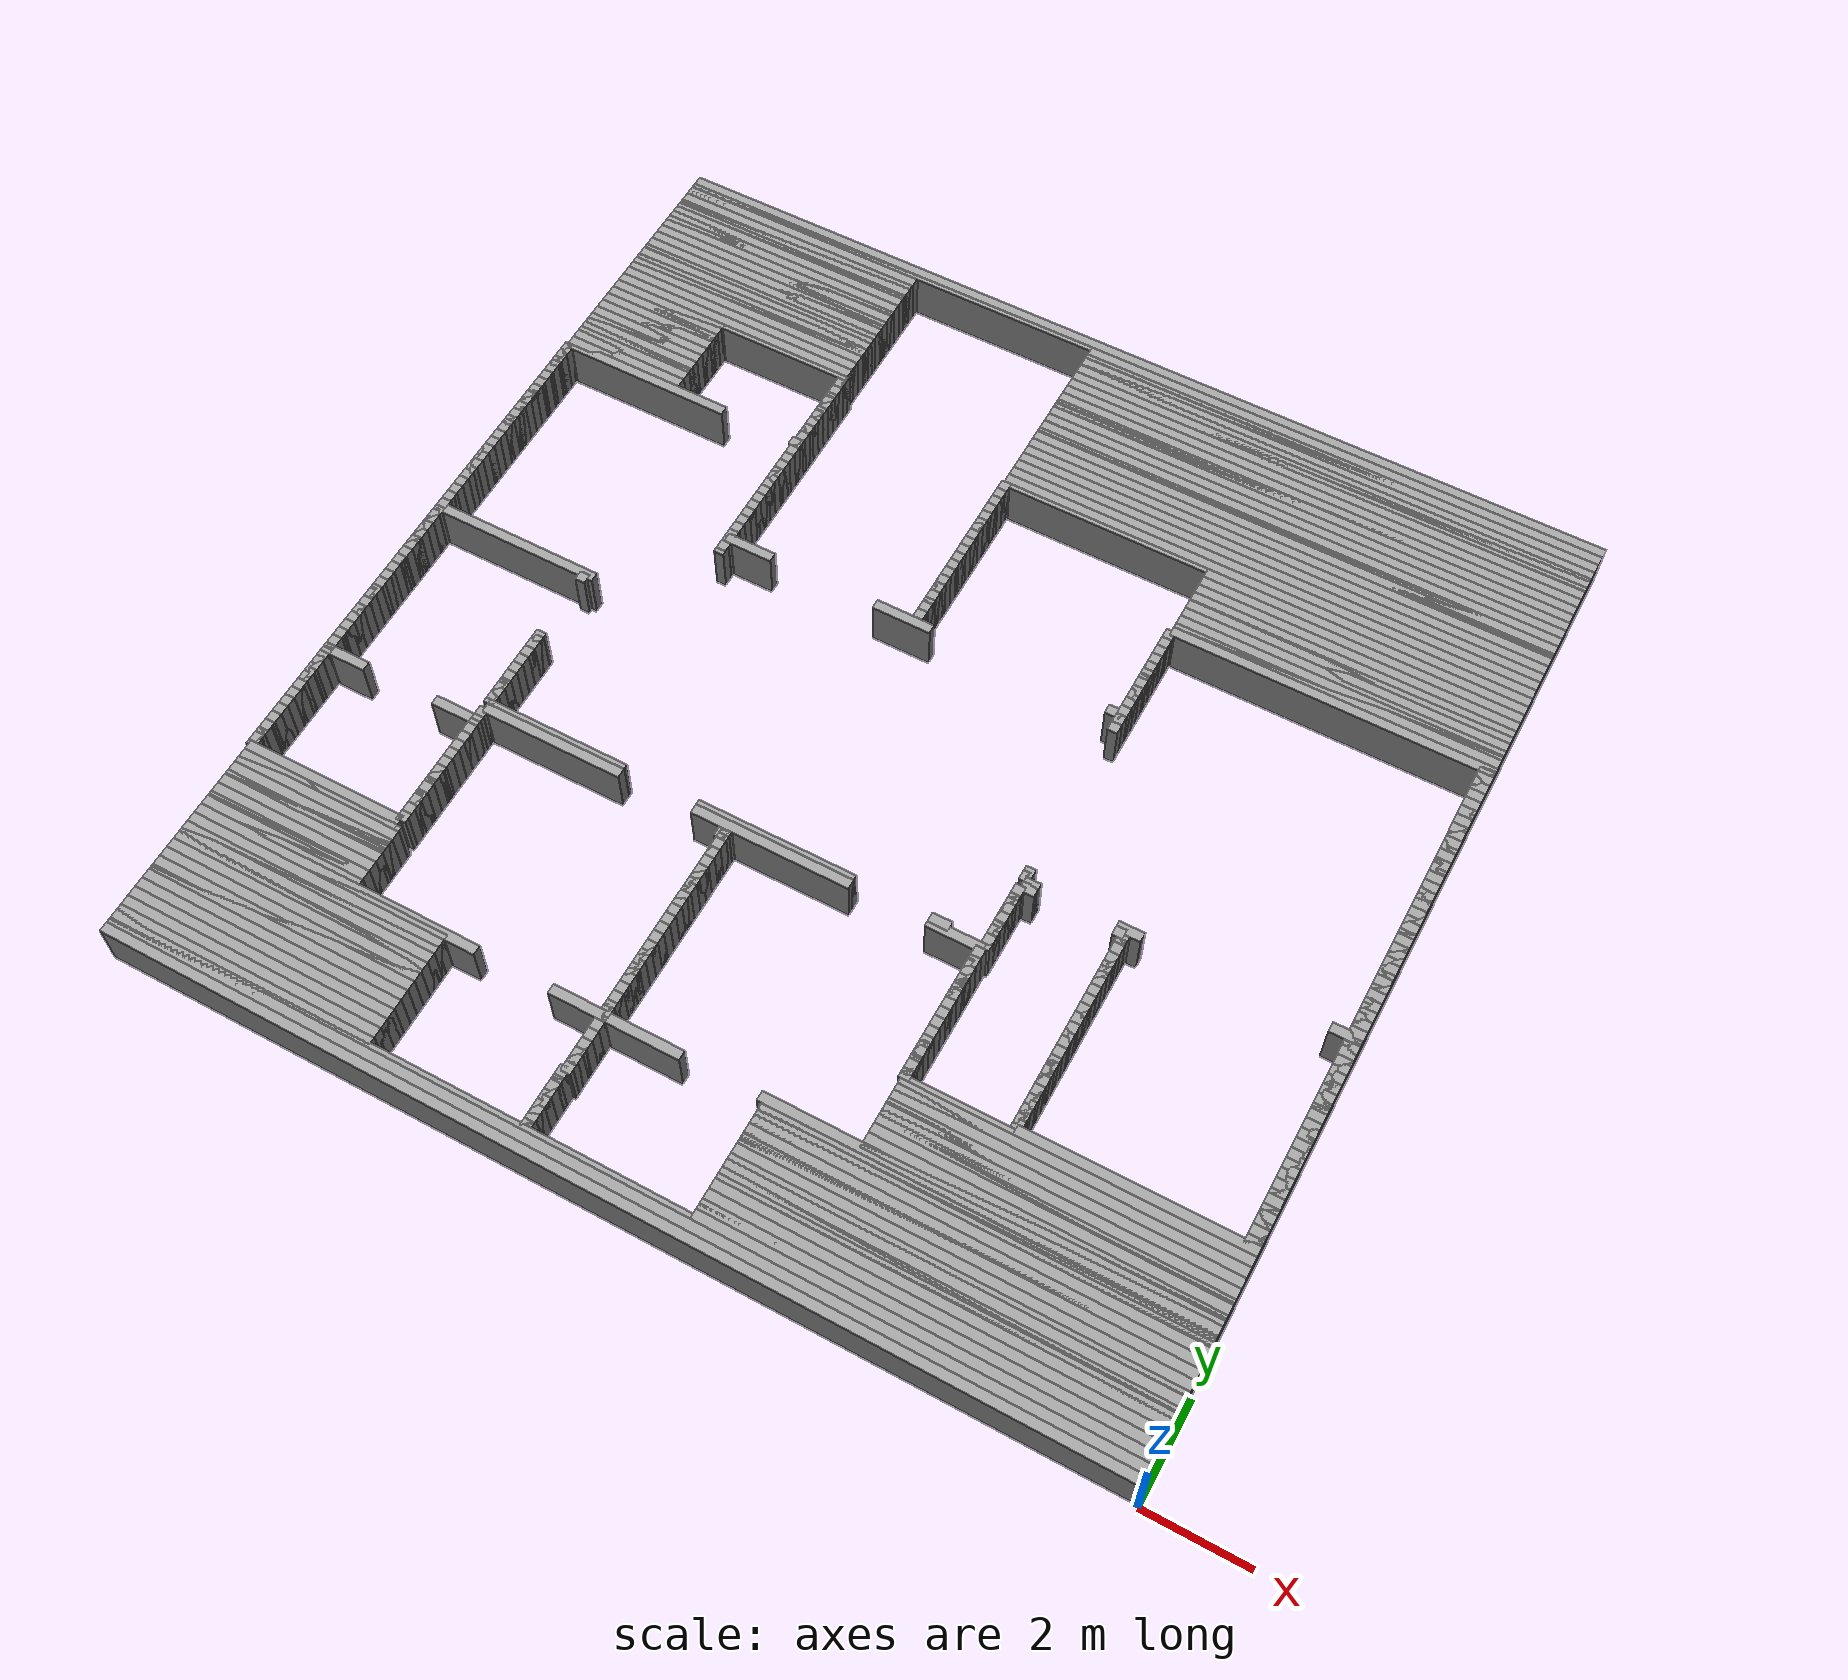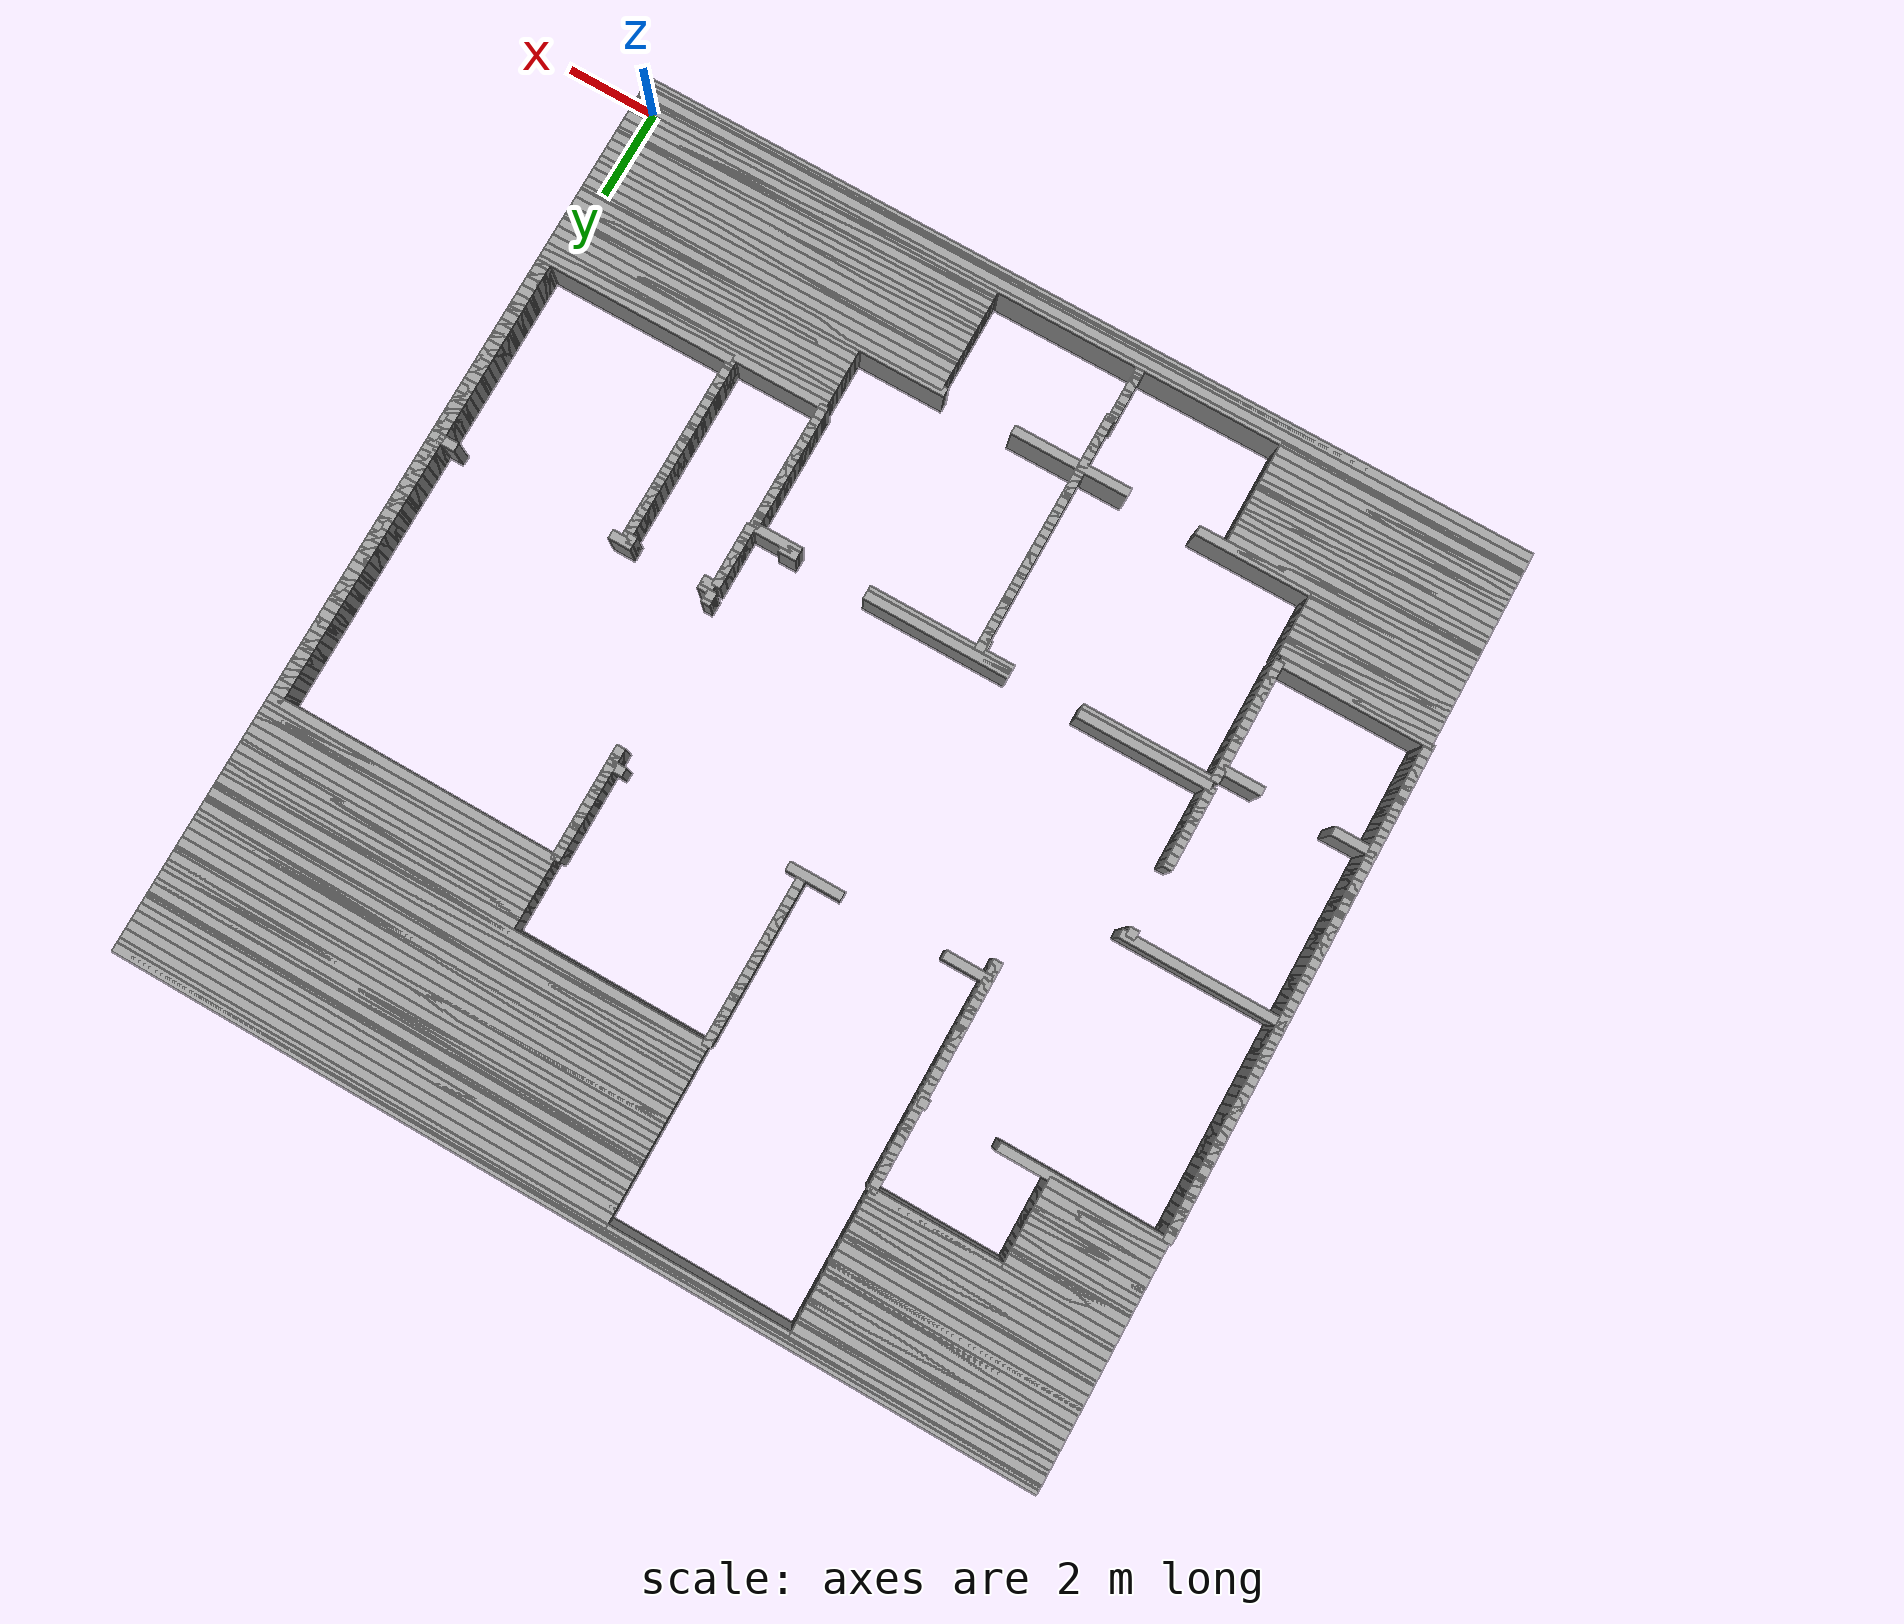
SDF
<?xml version='1.0' encoding='UTF-8'?>
<sdf version="1.6"><world name="GridMap"><inlude><uri>model://sun</uri></inlude><inlude><uri>model://ground_plane</uri></inlude><physics type="ode"><real_time_update_rate>1000.0</real_time_update_rate><max_step_size>0.001</max_step_size><real_time_factor>1</real_time_factor><ode><solver><type>quick</type><iters>150</iters><precon_iters>0</precon_iters><sor>1.4</sor><use_dynamic_moi_rescaling>1</use_dynamic_moi_rescaling></solver><constraints><cfm>0.00001</cfm><erp>0.2</erp><contact_max_correcting_vel>2000.000000</contact_max_correcting_vel><contact_surface_layer>0.01000</contact_surface_layer></constraints></ode></physics><model name="GridMap"><pose frame="">0 0 0 0 -0 0</pose><link name="Wall_(99.5,0.0)"><collision name="Wall_(99.5,0.0)_Collision"><geometry><box><size>19.900000000000002 0.2 1.0</size></box></geometry><pose frame="">-9.950000000000001 0.0 0.5 0 -0 0</pose></collision><visual name="Wall_(99.5,0.0)_Visual"><geometry><box><size>19.900000000000002 0.2 1.0</size></box></geometry><pose frame="">-9.950000000000001 0.0 0.5 0 -0 0</pose><material><script><uri>file://media/materials/scripts/gazebo.material</uri><name>Gazebo/Grey</name></script><ambient>1 1 1 1</ambient></material><meta><layer>0</layer></meta></visual><pose frame="">0 0 0.5 0 -0 0</pose></link><link name="Wall_(99.5,1.0)"><collision name="Wall_(99.5,1.0)_Collision"><geometry><box><size>19.900000000000002 0.2 1.0</size></box></geometry><pose frame="">-9.950000000000001 0.1 0.5 0 -0 0</pose></collision><visual name="Wall_(99.5,1.0)_Visual"><geometry><box><size>19.900000000000002 0.2 1.0</size></box></geometry><pose frame="">-9.950000000000001 0.1 0.5 0 -0 0</pose><material><script><uri>file://media/materials/scripts/gazebo.material</uri><name>Gazebo/Grey</name></script><ambient>1 1 1 1</ambient></material><meta><layer>0</layer></meta></visual><pose frame="">0 0 0.5 0 -0 0</pose></link><link name="Wall_(99.5,2.0)"><collision name="Wall_(99.5,2.0)_Collision"><geometry><box><size>19.900000000000002 0.2 1.0</size></box></geometry><pose frame="">-9.950000000000001 0.2 0.5 0 -0 0</pose></collision><visual name="Wall_(99.5,2.0)_Visual"><geometry><box><size>19.900000000000002 0.2 1.0</size></box></geometry><pose frame="">-9.950000000000001 0.2 0.5 0 -0 0</pose><material><script><uri>file://media/materials/scripts/gazebo.material</uri><name>Gazebo/Grey</name></script><ambient>1 1 1 1</ambient></material><meta><layer>0</layer></meta></visual><pose frame="">0 0 0.5 0 -0 0</pose></link><link name="Wall_(99.5,3.0)"><collision name="Wall_(99.5,3.0)_Collision"><geometry><box><size>19.900000000000002 0.2 1.0</size></box></geometry><pose frame="">-9.950000000000001 0.30000000000000004 0.5 0 -0 0</pose></collision><visual name="Wall_(99.5,3.0)_Visual"><geometry><box><size>19.900000000000002 0.2 1.0</size></box></geometry><pose frame="">-9.950000000000001 0.30000000000000004 0.5 0 -0 0</pose><material><script><uri>file://media/materials/scripts/gazebo.material</uri><name>Gazebo/Grey</name></script><ambient>1 1 1 1</ambient></material><meta><layer>0</layer></meta></visual><pose frame="">0 0 0.5 0 -0 0</pose></link><link name="Wall_(41.5,4.0)"><collision name="Wall_(41.5,4.0)_Collision"><geometry><box><size>8.3 0.2 1.0</size></box></geometry><pose frame="">-4.15 0.4 0.5 0 -0 0</pose></collision><visual name="Wall_(41.5,4.0)_Visual"><geometry><box><size>8.3 0.2 1.0</size></box></geometry><pose frame="">-4.15 0.4 0.5 0 -0 0</pose><material><script><uri>file://media/materials/scripts/gazebo.material</uri><name>Gazebo/Grey</name></script><ambient>1 1 1 1</ambient></material><meta><layer>0</layer></meta></visual><pose frame="">0 0 0.5 0 -0 0</pose></link><link name="Wall_(115.0,4.0)"><collision name="Wall_(115.0,4.0)_Collision"><geometry><box><size>0.2 0.2 1.0</size></box></geometry><pose frame="">-11.5 0.4 0.5 0 -0 0</pose></collision><visual name="Wall_(115.0,4.0)_Visual"><geometry><box><size>0.2 0.2 1.0</size></box></geometry><pose frame="">-11.5 0.4 0.5 0 -0 0</pose><material><script><uri>file://media/materials/scripts/gazebo.material</uri><name>Gazebo/Grey</name></script><ambient>1 1 1 1</ambient></material><meta><layer>0</layer></meta></visual><pose frame="">0 0 0.5 0 -0 0</pose></link><link name="Wall_(172.5,4.0)"><collision name="Wall_(172.5,4.0)_Collision"><geometry><box><size>5.300000000000001 0.2 1.0</size></box></geometry><pose frame="">-17.25 0.4 0.5 0 -0 0</pose></collision><visual name="Wall_(172.5,4.0)_Visual"><geometry><box><size>5.300000000000001 0.2 1.0</size></box></geometry><pose frame="">-17.25 0.4 0.5 0 -0 0</pose><material><script><uri>file://media/materials/scripts/gazebo.material</uri><name>Gazebo/Grey</name></script><ambient>1 1 1 1</ambient></material><meta><layer>0</layer></meta></visual><pose frame="">0 0 0.5 0 -0 0</pose></link><link name="Wall_(41.5,5.0)"><collision name="Wall_(41.5,5.0)_Collision"><geometry><box><size>8.3 0.2 1.0</size></box></geometry><pose frame="">-4.15 0.5 0.5 0 -0 0</pose></collision><visual name="Wall_(41.5,5.0)_Visual"><geometry><box><size>8.3 0.2 1.0</size></box></geometry><pose frame="">-4.15 0.5 0.5 0 -0 0</pose><material><script><uri>file://media/materials/scripts/gazebo.material</uri><name>Gazebo/Grey</name></script><ambient>1 1 1 1</ambient></material><meta><layer>0</layer></meta></visual><pose frame="">0 0 0.5 0 -0 0</pose></link><link name="Wall_(115.0,5.0)"><collision name="Wall_(115.0,5.0)_Collision"><geometry><box><size>0.2 0.2 1.0</size></box></geometry><pose frame="">-11.5 0.5 0.5 0 -0 0</pose></collision><visual name="Wall_(115.0,5.0)_Visual"><geometry><box><size>0.2 0.2 1.0</size></box></geometry><pose frame="">-11.5 0.5 0.5 0 -0 0</pose><material><script><uri>file://media/materials/scripts/gazebo.material</uri><name>Gazebo/Grey</name></script><ambient>1 1 1 1</ambient></material><meta><layer>0</layer></meta></visual><pose frame="">0 0 0.5 0 -0 0</pose></link><link name="Wall_(172.5,5.0)"><collision name="Wall_(172.5,5.0)_Collision"><geometry><box><size>5.300000000000001 0.2 1.0</size></box></geometry><pose frame="">-17.25 0.5 0.5 0 -0 0</pose></collision><visual name="Wall_(172.5,5.0)_Visual"><geometry><box><size>5.300000000000001 0.2 1.0</size></box></geometry><pose frame="">-17.25 0.5 0.5 0 -0 0</pose><material><script><uri>file://media/materials/scripts/gazebo.material</uri><name>Gazebo/Grey</name></script><ambient>1 1 1 1</ambient></material><meta><layer>0</layer></meta></visual><pose frame="">0 0 0.5 0 -0 0</pose></link><link name="Wall_(41.5,6.0)"><collision name="Wall_(41.5,6.0)_Collision"><geometry><box><size>8.3 0.2 1.0</size></box></geometry><pose frame="">-4.15 0.6000000000000001 0.5 0 -0 0</pose></collision><visual name="Wall_(41.5,6.0)_Visual"><geometry><box><size>8.3 0.2 1.0</size></box></geometry><pose frame="">-4.15 0.6000000000000001 0.5 0 -0 0</pose><material><script><uri>file://media/materials/scripts/gazebo.material</uri><name>Gazebo/Grey</name></script><ambient>1 1 1 1</ambient></material><meta><layer>0</layer></meta></visual><pose frame="">0 0 0.5 0 -0 0</pose></link><link name="Wall_(115.0,6.0)"><collision name="Wall_(115.0,6.0)_Collision"><geometry><box><size>0.2 0.2 1.0</size></box></geometry><pose frame="">-11.5 0.6000000000000001 0.5 0 -0 0</pose></collision><visual name="Wall_(115.0,6.0)_Visual"><geometry><box><size>0.2 0.2 1.0</size></box></geometry><pose frame="">-11.5 0.6000000000000001 0.5 0 -0 0</pose><material><script><uri>file://media/materials/scripts/gazebo.material</uri><name>Gazebo/Grey</name></script><ambient>1 1 1 1</ambient></material><meta><layer>0</layer></meta></visual><pose frame="">0 0 0.5 0 -0 0</pose></link><link name="Wall_(172.5,6.0)"><collision name="Wall_(172.5,6.0)_Collision"><geometry><box><size>5.300000000000001 0.2 1.0</size></box></geometry><pose frame="">-17.25 0.6000000000000001 0.5 0 -0 0</pose></collision><visual name="Wall_(172.5,6.0)_Visual"><geometry><box><size>5.300000000000001 0.2 1.0</size></box></geometry><pose frame="">-17.25 0.6000000000000001 0.5 0 -0 0</pose><material><script><uri>file://media/materials/scripts/gazebo.material</uri><name>Gazebo/Grey</name></script><ambient>1 1 1 1</ambient></material><meta><layer>0</layer></meta></visual><pose frame="">0 0 0.5 0 -0 0</pose></link><link name="Wall_(41.5,7.0)"><collision name="Wall_(41.5,7.0)_Collision"><geometry><box><size>8.3 0.2 1.0</size></box></geometry><pose frame="">-4.15 0.7000000000000001 0.5 0 -0 0</pose></collision><visual name="Wall_(41.5,7.0)_Visual"><geometry><box><size>8.3 0.2 1.0</size></box></geometry><pose frame="">-4.15 0.7000000000000001 0.5 0 -0 0</pose><material><script><uri>file://media/materials/scripts/gazebo.material</uri><name>Gazebo/Grey</name></script><ambient>1 1 1 1</ambient></material><meta><layer>0</layer></meta></visual><pose frame="">0 0 0.5 0 -0 0</pose></link><link name="Wall_(115.0,7.0)"><collision name="Wall_(115.0,7.0)_Collision"><geometry><box><size>0.2 0.2 1.0</size></box></geometry><pose frame="">-11.5 0.7000000000000001 0.5 0 -0 0</pose></collision><visual name="Wall_(115.0,7.0)_Visual"><geometry><box><size>0.2 0.2 1.0</size></box></geometry><pose frame="">-11.5 0.7000000000000001 0.5 0 -0 0</pose><material><script><uri>file://media/materials/scripts/gazebo.material</uri><name>Gazebo/Grey</name></script><ambient>1 1 1 1</ambient></material><meta><layer>0</layer></meta></visual><pose frame="">0 0 0.5 0 -0 0</pose></link><link name="Wall_(172.5,7.0)"><collision name="Wall_(172.5,7.0)_Collision"><geometry><box><size>5.300000000000001 0.2 1.0</size></box></geometry><pose frame="">-17.25 0.7000000000000001 0.5 0 -0 0</pose></collision><visual name="Wall_(172.5,7.0)_Visual"><geometry><box><size>5.300000000000001 0.2 1.0</size></box></geometry><pose frame="">-17.25 0.7000000000000001 0.5 0 -0 0</pose><material><script><uri>file://media/materials/scripts/gazebo.material</uri><name>Gazebo/Grey</name></script><ambient>1 1 1 1</ambient></material><meta><layer>0</layer></meta></visual><pose frame="">0 0 0.5 0 -0 0</pose></link><link name="Wall_(41.5,8.0)"><collision name="Wall_(41.5,8.0)_Collision"><geometry><box><size>8.3 0.2 1.0</size></box></geometry><pose frame="">-4.15 0.8 0.5 0 -0 0</pose></collision><visual name="Wall_(41.5,8.0)_Visual"><geometry><box><size>8.3 0.2 1.0</size></box></geometry><pose frame="">-4.15 0.8 0.5 0 -0 0</pose><material><script><uri>file://media/materials/scripts/gazebo.material</uri><name>Gazebo/Grey</name></script><ambient>1 1 1 1</ambient></material><meta><layer>0</layer></meta></visual><pose frame="">0 0 0.5 0 -0 0</pose></link><link name="Wall_(115.0,8.0)"><collision name="Wall_(115.0,8.0)_Collision"><geometry><box><size>0.2 0.2 1.0</size></box></geometry><pose frame="">-11.5 0.8 0.5 0 -0 0</pose></collision><visual name="Wall_(115.0,8.0)_Visual"><geometry><box><size>0.2 0.2 1.0</size></box></geometry><pose frame="">-11.5 0.8 0.5 0 -0 0</pose><material><script><uri>file://media/materials/scripts/gazebo.material</uri><name>Gazebo/Grey</name></script><ambient>1 1 1 1</ambient></material><meta><layer>0</layer></meta></visual><pose frame="">0 0 0.5 0 -0 0</pose></link><link name="Wall_(172.5,8.0)"><collision name="Wall_(172.5,8.0)_Collision"><geometry><box><size>5.300000000000001 0.2 1.0</size></box></geometry><pose frame="">-17.25 0.8 0.5 0 -0 0</pose></collision><visual name="Wall_(172.5,8.0)_Visual"><geometry><box><size>5.300000000000001 0.2 1.0</size></box></geometry><pose frame="">-17.25 0.8 0.5 0 -0 0</pose><material><script><uri>file://media/materials/scripts/gazebo.material</uri><name>Gazebo/Grey</name></script><ambient>1 1 1 1</ambient></material><meta><layer>0</layer></meta></visual><pose frame="">0 0 0.5 0 -0 0</pose></link><link name="Wall_(41.5,9.0)"><collision name="Wall_(41.5,9.0)_Collision"><geometry><box><size>8.3 0.2 1.0</size></box></geometry><pose frame="">-4.15 0.9 0.5 0 -0 0</pose></collision><visual name="Wall_(41.5,9.0)_Visual"><geometry><box><size>8.3 0.2 1.0</size></box></geometry><pose frame="">-4.15 0.9 0.5 0 -0 0</pose><material><script><uri>file://media/materials/scripts/gazebo.material</uri><name>Gazebo/Grey</name></script><ambient>1 1 1 1</ambient></material><meta><layer>0</layer></meta></visual><pose frame="">0 0 0.5 0 -0 0</pose></link><link name="Wall_(115.0,9.0)"><collision name="Wall_(115.0,9.0)_Collision"><geometry><box><size>0.2 0.2 1.0</size></box></geometry><pose frame="">-11.5 0.9 0.5 0 -0 0</pose></collision><visual name="Wall_(115.0,9.0)_Visual"><geometry><box><size>0.2 0.2 1.0</size></box></geometry><pose frame="">-11.5 0.9 0.5 0 -0 0</pose><material><script><uri>file://media/materials/scripts/gazebo.material</uri><name>Gazebo/Grey</name></script><ambient>1 1 1 1</ambient></material><meta><layer>0</layer></meta></visual><pose frame="">0 0 0.5 0 -0 0</pose></link><link name="Wall_(172.5,9.0)"><collision name="Wall_(172.5,9.0)_Collision"><geometry><box><size>5.300000000000001 0.2 1.0</size></box></geometry><pose frame="">-17.25 0.9 0.5 0 -0 0</pose></collision><visual name="Wall_(172.5,9.0)_Visual"><geometry><box><size>5.300000000000001 0.2 1.0</size></box></geometry><pose frame="">-17.25 0.9 0.5 0 -0 0</pose><material><script><uri>file://media/materials/scripts/gazebo.material</uri><name>Gazebo/Grey</name></script><ambient>1 1 1 1</ambient></material><meta><layer>0</layer></meta></visual><pose frame="">0 0 0.5 0 -0 0</pose></link><link name="Wall_(41.5,10.0)"><collision name="Wall_(41.5,10.0)_Collision"><geometry><box><size>8.3 0.2 1.0</size></box></geometry><pose frame="">-4.15 1.0 0.5 0 -0 0</pose></collision><visual name="Wall_(41.5,10.0)_Visual"><geometry><box><size>8.3 0.2 1.0</size></box></geometry><pose frame="">-4.15 1.0 0.5 0 -0 0</pose><material><script><uri>file://media/materials/scripts/gazebo.material</uri><name>Gazebo/Grey</name></script><ambient>1 1 1 1</ambient></material><meta><layer>0</layer></meta></visual><pose frame="">0 0 0.5 0 -0 0</pose></link><link name="Wall_(115.0,10.0)"><collision name="Wall_(115.0,10.0)_Collision"><geometry><box><size>0.2 0.2 1.0</size></box></geometry><pose frame="">-11.5 1.0 0.5 0 -0 0</pose></collision><visual name="Wall_(115.0,10.0)_Visual"><geometry><box><size>0.2 0.2 1.0</size></box></geometry><pose frame="">-11.5 1.0 0.5 0 -0 0</pose><material><script><uri>file://media/materials/scripts/gazebo.material</uri><name>Gazebo/Grey</name></script><ambient>1 1 1 1</ambient></material><meta><layer>0</layer></meta></visual><pose frame="">0 0 0.5 0 -0 0</pose></link><link name="Wall_(172.5,10.0)"><collision name="Wall_(172.5,10.0)_Collision"><geometry><box><size>5.300000000000001 0.2 1.0</size></box></geometry><pose frame="">-17.25 1.0 0.5 0 -0 0</pose></collision><visual name="Wall_(172.5,10.0)_Visual"><geometry><box><size>5.300000000000001 0.2 1.0</size></box></geometry><pose frame="">-17.25 1.0 0.5 0 -0 0</pose><material><script><uri>file://media/materials/scripts/gazebo.material</uri><name>Gazebo/Grey</name></script><ambient>1 1 1 1</ambient></material><meta><layer>0</layer></meta></visual><pose frame="">0 0 0.5 0 -0 0</pose></link><link name="Wall_(41.5,11.0)"><collision name="Wall_(41.5,11.0)_Collision"><geometry><box><size>8.3 0.2 1.0</size></box></geometry><pose frame="">-4.15 1.1 0.5 0 -0 0</pose></collision><visual name="Wall_(41.5,11.0)_Visual"><geometry><box><size>8.3 0.2 1.0</size></box></geometry><pose frame="">-4.15 1.1 0.5 0 -0 0</pose><material><script><uri>file://media/materials/scripts/gazebo.material</uri><name>Gazebo/Grey</name></script><ambient>1 1 1 1</ambient></material><meta><layer>0</layer></meta></visual><pose frame="">0 0 0.5 0 -0 0</pose></link><link name="Wall_(115.0,11.0)"><collision name="Wall_(115.0,11.0)_Collision"><geometry><box><size>0.2 0.2 1.0</size></box></geometry><pose frame="">-11.5 1.1 0.5 0 -0 0</pose></collision><visual name="Wall_(115.0,11.0)_Visual"><geometry><box><size>0.2 0.2 1.0</size></box></geometry><pose frame="">-11.5 1.1 0.5 0 -0 0</pose><material><script><uri>file://media/materials/scripts/gazebo.material</uri><name>Gazebo/Grey</name></script><ambient>1 1 1 1</ambient></material><meta><layer>0</layer></meta></visual><pose frame="">0 0 0.5 0 -0 0</pose></link><link name="Wall_(172.5,11.0)"><collision name="Wall_(172.5,11.0)_Collision"><geometry><box><size>5.300000000000001 0.2 1.0</size></box></geometry><pose frame="">-17.25 1.1 0.5 0 -0 0</pose></collision><visual name="Wall_(172.5,11.0)_Visual"><geometry><box><size>5.300000000000001 0.2 1.0</size></box></geometry><pose frame="">-17.25 1.1 0.5 0 -0 0</pose><material><script><uri>file://media/materials/scripts/gazebo.material</uri><name>Gazebo/Grey</name></script><ambient>1 1 1 1</ambient></material><meta><layer>0</layer></meta></visual><pose frame="">0 0 0.5 0 -0 0</pose></link><link name="Wall_(41.5,12.0)"><collision name="Wall_(41.5,12.0)_Collision"><geometry><box><size>8.3 0.2 1.0</size></box></geometry><pose frame="">-4.15 1.2000000000000002 0.5 0 -0 0</pose></collision><visual name="Wall_(41.5,12.0)_Visual"><geometry><box><size>8.3 0.2 1.0</size></box></geometry><pose frame="">-4.15 1.2000000000000002 0.5 0 -0 0</pose><material><script><uri>file://media/materials/scripts/gazebo.material</uri><name>Gazebo/Grey</name></script><ambient>1 1 1 1</ambient></material><meta><layer>0</layer></meta></visual><pose frame="">0 0 0.5 0 -0 0</pose></link><link name="Wall_(115.0,12.0)"><collision name="Wall_(115.0,12.0)_Collision"><geometry><box><size>0.2 0.2 1.0</size></box></geometry><pose frame="">-11.5 1.2000000000000002 0.5 0 -0 0</pose></collision><visual name="Wall_(115.0,12.0)_Visual"><geometry><box><size>0.2 0.2 1.0</size></box></geometry><pose frame="">-11.5 1.2000000000000002 0.5 0 -0 0</pose><material><script><uri>file://media/materials/scripts/gazebo.material</uri><name>Gazebo/Grey</name></script><ambient>1 1 1 1</ambient></material><meta><layer>0</layer></meta></visual><pose frame="">0 0 0.5 0 -0 0</pose></link><link name="Wall_(172.5,12.0)"><collision name="Wall_(172.5,12.0)_Collision"><geometry><box><size>5.300000000000001 0.2 1.0</size></box></geometry><pose frame="">-17.25 1.2000000000000002 0.5 0 -0 0</pose></collision><visual name="Wall_(172.5,12.0)_Visual"><geometry><box><size>5.300000000000001 0.2 1.0</size></box></geometry><pose frame="">-17.25 1.2000000000000002 0.5 0 -0 0</pose><material><script><uri>file://media/materials/scripts/gazebo.material</uri><name>Gazebo/Grey</name></script><ambient>1 1 1 1</ambient></material><meta><layer>0</layer></meta></visual><pose frame="">0 0 0.5 0 -0 0</pose></link><link name="Wall_(41.5,13.0)"><collision name="Wall_(41.5,13.0)_Collision"><geometry><box><size>8.3 0.2 1.0</size></box></geometry><pose frame="">-4.15 1.3 0.5 0 -0 0</pose></collision><visual name="Wall_(41.5,13.0)_Visual"><geometry><box><size>8.3 0.2 1.0</size></box></geometry><pose frame="">-4.15 1.3 0.5 0 -0 0</pose><material><script><uri>file://media/materials/scripts/gazebo.material</uri><name>Gazebo/Grey</name></script><ambient>1 1 1 1</ambient></material><meta><layer>0</layer></meta></visual><pose frame="">0 0 0.5 0 -0 0</pose></link><link name="Wall_(115.0,13.0)"><collision name="Wall_(115.0,13.0)_Collision"><geometry><box><size>0.2 0.2 1.0</size></box></geometry><pose frame="">-11.5 1.3 0.5 0 -0 0</pose></collision><visual name="Wall_(115.0,13.0)_Visual"><geometry><box><size>0.2 0.2 1.0</size></box></geometry><pose frame="">-11.5 1.3 0.5 0 -0 0</pose><material><script><uri>file://media/materials/scripts/gazebo.material</uri><name>Gazebo/Grey</name></script><ambient>1 1 1 1</ambient></material><meta><layer>0</layer></meta></visual><pose frame="">0 0 0.5 0 -0 0</pose></link><link name="Wall_(172.5,13.0)"><collision name="Wall_(172.5,13.0)_Collision"><geometry><box><size>5.300000000000001 0.2 1.0</size></box></geometry><pose frame="">-17.25 1.3 0.5 0 -0 0</pose></collision><visual name="Wall_(172.5,13.0)_Visual"><geometry><box><size>5.300000000000001 0.2 1.0</size></box></geometry><pose frame="">-17.25 1.3 0.5 0 -0 0</pose><material><script><uri>file://media/materials/scripts/gazebo.material</uri><name>Gazebo/Grey</name></script><ambient>1 1 1 1</ambient></material><meta><layer>0</layer></meta></visual><pose frame="">0 0 0.5 0 -0 0</pose></link><link name="Wall_(41.5,14.0)"><collision name="Wall_(41.5,14.0)_Collision"><geometry><box><size>8.3 0.2 1.0</size></box></geometry><pose frame="">-4.15 1.4000000000000001 0.5 0 -0 0</pose></collision><visual name="Wall_(41.5,14.0)_Visual"><geometry><box><size>8.3 0.2 1.0</size></box></geometry><pose frame="">-4.15 1.4000000000000001 0.5 0 -0 0</pose><material><script><uri>file://media/materials/scripts/gazebo.material</uri><name>Gazebo/Grey</name></script><ambient>1 1 1 1</ambient></material><meta><layer>0</layer></meta></visual><pose frame="">0 0 0.5 0 -0 0</pose></link><link name="Wall_(115.0,14.0)"><collision name="Wall_(115.0,14.0)_Collision"><geometry><box><size>0.2 0.2 1.0</size></box></geometry><pose frame="">-11.5 1.4000000000000001 0.5 0 -0 0</pose></collision><visual name="Wall_(115.0,14.0)_Visual"><geometry><box><size>0.2 0.2 1.0</size></box></geometry><pose frame="">-11.5 1.4000000000000001 0.5 0 -0 0</pose><material><script><uri>file://media/materials/scripts/gazebo.material</uri><name>Gazebo/Grey</name></script><ambient>1 1 1 1</ambient></material><meta><layer>0</layer></meta></visual><pose frame="">0 0 0.5 0 -0 0</pose></link><link name="Wall_(172.5,14.0)"><collision name="Wall_(172.5,14.0)_Collision"><geometry><box><size>5.300000000000001 0.2 1.0</size></box></geometry><pose frame="">-17.25 1.4000000000000001 0.5 0 -0 0</pose></collision><visual name="Wall_(172.5,14.0)_Visual"><geometry><box><size>5.300000000000001 0.2 1.0</size></box></geometry><pose frame="">-17.25 1.4000000000000001 0.5 0 -0 0</pose><material><script><uri>file://media/materials/scripts/gazebo.material</uri><name>Gazebo/Grey</name></script><ambient>1 1 1 1</ambient></material><meta><layer>0</layer></meta></visual><pose frame="">0 0 0.5 0 -0 0</pose></link><link name="Wall_(41.5,15.0)"><collision name="Wall_(41.5,15.0)_Collision"><geometry><box><size>8.3 0.2 1.0</size></box></geometry><pose frame="">-4.15 1.5 0.5 0 -0 0</pose></collision><visual name="Wall_(41.5,15.0)_Visual"><geometry><box><size>8.3 0.2 1.0</size></box></geometry><pose frame="">-4.15 1.5 0.5 0 -0 0</pose><material><script><uri>file://media/materials/scripts/gazebo.material</uri><name>Gazebo/Grey</name></script><ambient>1 1 1 1</ambient></material><meta><layer>0</layer></meta></visual><pose frame="">0 0 0.5 0 -0 0</pose></link><link name="Wall_(115.0,15.0)"><collision name="Wall_(115.0,15.0)_Collision"><geometry><box><size>0.2 0.2 1.0</size></box></geometry><pose frame="">-11.5 1.5 0.5 0 -0 0</pose></collision><visual name="Wall_(115.0,15.0)_Visual"><geometry><box><size>0.2 0.2 1.0</size></box></geometry><pose frame="">-11.5 1.5 0.5 0 -0 0</pose><material><script><uri>file://media/materials/scripts/gazebo.material</uri><name>Gazebo/Grey</name></script><ambient>1 1 1 1</ambient></material><meta><layer>0</layer></meta></visual><pose frame="">0 0 0.5 0 -0 0</pose></link><link name="Wall_(172.5,15.0)"><collision name="Wall_(172.5,15.0)_Collision"><geometry><box><size>5.300000000000001 0.2 1.0</size></box></geometry><pose frame="">-17.25 1.5 0.5 0 -0 0</pose></collision><visual name="Wall_(172.5,15.0)_Visual"><geometry><box><size>5.300000000000001 0.2 1.0</size></box></geometry><pose frame="">-17.25 1.5 0.5 0 -0 0</pose><material><script><uri>file://media/materials/scripts/gazebo.material</uri><name>Gazebo/Grey</name></script><ambient>1 1 1 1</ambient></material><meta><layer>0</layer></meta></visual><pose frame="">0 0 0.5 0 -0 0</pose></link><link name="Wall_(41.5,16.0)"><collision name="Wall_(41.5,16.0)_Collision"><geometry><box><size>8.3 0.2 1.0</size></box></geometry><pose frame="">-4.15 1.6 0.5 0 -0 0</pose></collision><visual name="Wall_(41.5,16.0)_Visual"><geometry><box><size>8.3 0.2 1.0</size></box></geometry><pose frame="">-4.15 1.6 0.5 0 -0 0</pose><material><script><uri>file://media/materials/scripts/gazebo.material</uri><name>Gazebo/Grey</name></script><ambient>1 1 1 1</ambient></material><meta><layer>0</layer></meta></visual><pose frame="">0 0 0.5 0 -0 0</pose></link><link name="Wall_(114.5,16.0)"><collision name="Wall_(114.5,16.0)_Collision"><geometry><box><size>0.2 0.2 1.0</size></box></geometry><pose frame="">-11.450000000000001 1.6 0.5 0 -0 0</pose></collision><visual name="Wall_(114.5,16.0)_Visual"><geometry><box><size>0.2 0.2 1.0</size></box></geometry><pose frame="">-11.450000000000001 1.6 0.5 0 -0 0</pose><material><script><uri>file://media/materials/scripts/gazebo.material</uri><name>Gazebo/Grey</name></script><ambient>1 1 1 1</ambient></material><meta><layer>0</layer></meta></visual><pose frame="">0 0 0.5 0 -0 0</pose></link><link name="Wall_(172.5,16.0)"><collision name="Wall_(172.5,16.0)_Collision"><geometry><box><size>5.300000000000001 0.2 1.0</size></box></geometry><pose frame="">-17.25 1.6 0.5 0 -0 0</pose></collision><visual name="Wall_(172.5,16.0)_Visual"><geometry><box><size>5.300000000000001 0.2 1.0</size></box></geometry><pose frame="">-17.25 1.6 0.5 0 -0 0</pose><material><script><uri>file://media/materials/scripts/gazebo.material</uri><name>Gazebo/Grey</name></script><ambient>1 1 1 1</ambient></material><meta><layer>0</layer></meta></visual><pose frame="">0 0 0.5 0 -0 0</pose></link><link name="Wall_(41.5,17.0)"><collision name="Wall_(41.5,17.0)_Collision"><geometry><box><size>8.3 0.2 1.0</size></box></geometry><pose frame="">-4.15 1.7000000000000002 0.5 0 -0 0</pose></collision><visual name="Wall_(41.5,17.0)_Visual"><geometry><box><size>8.3 0.2 1.0</size></box></geometry><pose frame="">-4.15 1.7000000000000002 0.5 0 -0 0</pose><material><script><uri>file://media/materials/scripts/gazebo.material</uri><name>Gazebo/Grey</name></script><ambient>1 1 1 1</ambient></material><meta><layer>0</layer></meta></visual><pose frame="">0 0 0.5 0 -0 0</pose></link><link name="Wall_(114.5,17.0)"><collision name="Wall_(114.5,17.0)_Collision"><geometry><box><size>0.2 0.2 1.0</size></box></geometry><pose frame="">-11.450000000000001 1.7000000000000002 0.5 0 -0 0</pose></collision><visual name="Wall_(114.5,17.0)_Visual"><geometry><box><size>0.2 0.2 1.0</size></box></geometry><pose frame="">-11.450000000000001 1.7000000000000002 0.5 0 -0 0</pose><material><script><uri>file://media/materials/scripts/gazebo.material</uri><name>Gazebo/Grey</name></script><ambient>1 1 1 1</ambient></material><meta><layer>0</layer></meta></visual><pose frame="">0 0 0.5 0 -0 0</pose></link><link name="Wall_(172.5,17.0)"><collision name="Wall_(172.5,17.0)_Collision"><geometry><box><size>5.300000000000001 0.2 1.0</size></box></geometry><pose frame="">-17.25 1.7000000000000002 0.5 0 -0 0</pose></collision><visual name="Wall_(172.5,17.0)_Visual"><geometry><box><size>5.300000000000001 0.2 1.0</size></box></geometry><pose frame="">-17.25 1.7000000000000002 0.5 0 -0 0</pose><material><script><uri>file://media/materials/scripts/gazebo.material</uri><name>Gazebo/Grey</name></script><ambient>1 1 1 1</ambient></material><meta><layer>0</layer></meta></visual><pose frame="">0 0 0.5 0 -0 0</pose></link><link name="Wall_(41.5,18.0)"><collision name="Wall_(41.5,18.0)_Collision"><geometry><box><size>8.3 0.2 1.0</size></box></geometry><pose frame="">-4.15 1.8 0.5 0 -0 0</pose></collision><visual name="Wall_(41.5,18.0)_Visual"><geometry><box><size>8.3 0.2 1.0</size></box></geometry><pose frame="">-4.15 1.8 0.5 0 -0 0</pose><material><script><uri>file://media/materials/scripts/gazebo.material</uri><name>Gazebo/Grey</name></script><ambient>1 1 1 1</ambient></material><meta><layer>0</layer></meta></visual><pose frame="">0 0 0.5 0 -0 0</pose></link><link name="Wall_(114.5,18.0)"><collision name="Wall_(114.5,18.0)_Collision"><geometry><box><size>0.2 0.2 1.0</size></box></geometry><pose frame="">-11.450000000000001 1.8 0.5 0 -0 0</pose></collision><visual name="Wall_(114.5,18.0)_Visual"><geometry><box><size>0.2 0.2 1.0</size></box></geometry><pose frame="">-11.450000000000001 1.8 0.5 0 -0 0</pose><material><script><uri>file://media/materials/scripts/gazebo.material</uri><name>Gazebo/Grey</name></script><ambient>1 1 1 1</ambient></material><meta><layer>0</layer></meta></visual><pose frame="">0 0 0.5 0 -0 0</pose></link><link name="Wall_(172.5,18.0)"><collision name="Wall_(172.5,18.0)_Collision"><geometry><box><size>5.300000000000001 0.2 1.0</size></box></geometry><pose frame="">-17.25 1.8 0.5 0 -0 0</pose></collision><visual name="Wall_(172.5,18.0)_Visual"><geometry><box><size>5.300000000000001 0.2 1.0</size></box></geometry><pose frame="">-17.25 1.8 0.5 0 -0 0</pose><material><script><uri>file://media/materials/scripts/gazebo.material</uri><name>Gazebo/Grey</name></script><ambient>1 1 1 1</ambient></material><meta><layer>0</layer></meta></visual><pose frame="">0 0 0.5 0 -0 0</pose></link><link name="Wall_(41.5,19.0)"><collision name="Wall_(41.5,19.0)_Collision"><geometry><box><size>8.3 0.2 1.0</size></box></geometry><pose frame="">-4.15 1.9000000000000001 0.5 0 -0 0</pose></collision><visual name="Wall_(41.5,19.0)_Visual"><geometry><box><size>8.3 0.2 1.0</size></box></geometry><pose frame="">-4.15 1.9000000000000001 0.5 0 -0 0</pose><material><script><uri>file://media/materials/scripts/gazebo.material</uri><name>Gazebo/Grey</name></script><ambient>1 1 1 1</ambient></material><meta><layer>0</layer></meta></visual><pose frame="">0 0 0.5 0 -0 0</pose></link><link name="Wall_(114.5,19.0)"><collision name="Wall_(114.5,19.0)_Collision"><geometry><box><size>0.2 0.2 1.0</size></box></geometry><pose frame="">-11.450000000000001 1.9000000000000001 0.5 0 -0 0</pose></collision><visual name="Wall_(114.5,19.0)_Visual"><geometry><box><size>0.2 0.2 1.0</size></box></geometry><pose frame="">-11.450000000000001 1.9000000000000001 0.5 0 -0 0</pose><material><script><uri>file://media/materials/scripts/gazebo.material</uri><name>Gazebo/Grey</name></script><ambient>1 1 1 1</ambient></material><meta><layer>0</layer></meta></visual><pose frame="">0 0 0.5 0 -0 0</pose></link><link name="Wall_(172.5,19.0)"><collision name="Wall_(172.5,19.0)_Collision"><geometry><box><size>5.300000000000001 0.2 1.0</size></box></geometry><pose frame="">-17.25 1.9000000000000001 0.5 0 -0 0</pose></collision><visual name="Wall_(172.5,19.0)_Visual"><geometry><box><size>5.300000000000001 0.2 1.0</size></box></geometry><pose frame="">-17.25 1.9000000000000001 0.5 0 -0 0</pose><material><script><uri>file://media/materials/scripts/gazebo.material</uri><name>Gazebo/Grey</name></script><ambient>1 1 1 1</ambient></material><meta><layer>0</layer></meta></visual><pose frame="">0 0 0.5 0 -0 0</pose></link><link name="Wall_(41.5,20.0)"><collision name="Wall_(41.5,20.0)_Collision"><geometry><box><size>8.3 0.2 1.0</size></box></geometry><pose frame="">-4.15 2.0 0.5 0 -0 0</pose></collision><visual name="Wall_(41.5,20.0)_Visual"><geometry><box><size>8.3 0.2 1.0</size></box></geometry><pose frame="">-4.15 2.0 0.5 0 -0 0</pose><material><script><uri>file://media/materials/scripts/gazebo.material</uri><name>Gazebo/Grey</name></script><ambient>1 1 1 1</ambient></material><meta><layer>0</layer></meta></visual><pose frame="">0 0 0.5 0 -0 0</pose></link><link name="Wall_(114.5,20.0)"><collision name="Wall_(114.5,20.0)_Collision"><geometry><box><size>0.2 0.2 1.0</size></box></geometry><pose frame="">-11.450000000000001 2.0 0.5 0 -0 0</pose></collision><visual name="Wall_(114.5,20.0)_Visual"><geometry><box><size>0.2 0.2 1.0</size></box></geometry><pose frame="">-11.450000000000001 2.0 0.5 0 -0 0</pose><material><script><uri>file://media/materials/scripts/gazebo.material</uri><name>Gazebo/Grey</name></script><ambient>1 1 1 1</ambient></material><meta><layer>0</layer></meta></visual><pose frame="">0 0 0.5 0 -0 0</pose></link><link name="Wall_(172.5,20.0)"><collision name="Wall_(172.5,20.0)_Collision"><geometry><box><size>5.300000000000001 0.2 1.0</size></box></geometry><pose frame="">-17.25 2.0 0.5 0 -0 0</pose></collision><visual name="Wall_(172.5,20.0)_Visual"><geometry><box><size>5.300000000000001 0.2 1.0</size></box></geometry><pose frame="">-17.25 2.0 0.5 0 -0 0</pose><material><script><uri>file://media/materials/scripts/gazebo.material</uri><name>Gazebo/Grey</name></script><ambient>1 1 1 1</ambient></material><meta><layer>0</layer></meta></visual><pose frame="">0 0 0.5 0 -0 0</pose></link><link name="Wall_(41.5,21.0)"><collision name="Wall_(41.5,21.0)_Collision"><geometry><box><size>8.3 0.2 1.0</size></box></geometry><pose frame="">-4.15 2.1 0.5 0 -0 0</pose></collision><visual name="Wall_(41.5,21.0)_Visual"><geometry><box><size>8.3 0.2 1.0</size></box></geometry><pose frame="">-4.15 2.1 0.5 0 -0 0</pose><material><script><uri>file://media/materials/scripts/gazebo.material</uri><name>Gazebo/Grey</name></script><ambient>1 1 1 1</ambient></material><meta><layer>0</layer></meta></visual><pose frame="">0 0 0.5 0 -0 0</pose></link><link name="Wall_(114.5,21.0)"><collision name="Wall_(114.5,21.0)_Collision"><geometry><box><size>0.2 0.2 1.0</size></box></geometry><pose frame="">-11.450000000000001 2.1 0.5 0 -0 0</pose></collision><visual name="Wall_(114.5,21.0)_Visual"><geometry><box><size>0.2 0.2 1.0</size></box></geometry><pose frame="">-11.450000000000001 2.1 0.5 0 -0 0</pose><material><script><uri>file://media/materials/scripts/gazebo.material</uri><name>Gazebo/Grey</name></script><ambient>1 1 1 1</ambient></material><meta><layer>0</layer></meta></visual><pose frame="">0 0 0.5 0 -0 0</pose></link><link name="Wall_(172.5,21.0)"><collision name="Wall_(172.5,21.0)_Collision"><geometry><box><size>5.300000000000001 0.2 1.0</size></box></geometry><pose frame="">-17.25 2.1 0.5 0 -0 0</pose></collision><visual name="Wall_(172.5,21.0)_Visual"><geometry><box><size>5.300000000000001 0.2 1.0</size></box></geometry><pose frame="">-17.25 2.1 0.5 0 -0 0</pose><material><script><uri>file://media/materials/scripts/gazebo.material</uri><name>Gazebo/Grey</name></script><ambient>1 1 1 1</ambient></material><meta><layer>0</layer></meta></visual><pose frame="">0 0 0.5 0 -0 0</pose></link><link name="Wall_(41.5,22.0)"><collision name="Wall_(41.5,22.0)_Collision"><geometry><box><size>8.3 0.2 1.0</size></box></geometry><pose frame="">-4.15 2.2 0.5 0 -0 0</pose></collision><visual name="Wall_(41.5,22.0)_Visual"><geometry><box><size>8.3 0.2 1.0</size></box></geometry><pose frame="">-4.15 2.2 0.5 0 -0 0</pose><material><script><uri>file://media/materials/scripts/gazebo.material</uri><name>Gazebo/Grey</name></script><ambient>1 1 1 1</ambient></material><meta><layer>0</layer></meta></visual><pose frame="">0 0 0.5 0 -0 0</pose></link><link name="Wall_(114.5,22.0)"><collision name="Wall_(114.5,22.0)_Collision"><geometry><box><size>0.2 0.2 1.0</size></box></geometry><pose frame="">-11.450000000000001 2.2 0.5 0 -0 0</pose></collision><visual name="Wall_(114.5,22.0)_Visual"><geometry><box><size>0.2 0.2 1.0</size></box></geometry><pose frame="">-11.450000000000001 2.2 0.5 0 -0 0</pose><material><script><uri>file://media/materials/scripts/gazebo.material</uri><name>Gazebo/Grey</name></script><ambient>1 1 1 1</ambient></material><meta><layer>0</layer></meta></visual><pose frame="">0 0 0.5 0 -0 0</pose></link><link name="Wall_(172.5,22.0)"><collision name="Wall_(172.5,22.0)_Collision"><geometry><box><size>5.300000000000001 0.2 1.0</size></box></geometry><pose frame="">-17.25 2.2 0.5 0 -0 0</pose></collision><visual name="Wall_(172.5,22.0)_Visual"><geometry><box><size>5.300000000000001 0.2 1.0</size></box></geometry><pose frame="">-17.25 2.2 0.5 0 -0 0</pose><material><script><uri>file://media/materials/scripts/gazebo.material</uri><name>Gazebo/Grey</name></script><ambient>1 1 1 1</ambient></material><meta><layer>0</layer></meta></visual><pose frame="">0 0 0.5 0 -0 0</pose></link><link name="Wall_(41.5,23.0)"><collision name="Wall_(41.5,23.0)_Collision"><geometry><box><size>8.3 0.2 1.0</size></box></geometry><pose frame="">-4.15 2.3000000000000003 0.5 0 -0 0</pose></collision><visual name="Wall_(41.5,23.0)_Visual"><geometry><box><size>8.3 0.2 1.0</size></box></geometry><pose frame="">-4.15 2.3000000000000003 0.5 0 -0 0</pose><material><script><uri>file://media/materials/scripts/gazebo.material</uri><name>Gazebo/Grey</name></script><ambient>1 1 1 1</ambient></material><meta><layer>0</layer></meta></visual><pose frame="">0 0 0.5 0 -0 0</pose></link><link name="Wall_(114.5,23.0)"><collision name="Wall_(114.5,23.0)_Collision"><geometry><box><size>0.2 0.2 1.0</size></box></geometry><pose frame="">-11.450000000000001 2.3000000000000003 0.5 0 -0 0</pose></collision><visual name="Wall_(114.5,23.0)_Visual"><geometry><box><size>0.2 0.2 1.0</size></box></geometry><pose frame="">-11.450000000000001 2.3000000000000003 0.5 0 -0 0</pose><material><script><uri>file://media/materials/scripts/gazebo.material</uri><name>Gazebo/Grey</name></script><ambient>1 1 1 1</ambient></material><meta><layer>0</layer></meta></visual><pose frame="">0 0 0.5 0 -0 0</pose></link><link name="Wall_(172.5,23.0)"><collision name="Wall_(172.5,23.0)_Collision"><geometry><box><size>5.300000000000001 0.2 1.0</size></box></geometry><pose frame="">-17.25 2.3000000000000003 0.5 0 -0 0</pose></collision><visual name="Wall_(172.5,23.0)_Visual"><geometry><box><size>5.300000000000001 0.2 1.0</size></box></geometry><pose frame="">-17.25 2.3000000000000003 0.5 0 -0 0</pose><material><script><uri>file://media/materials/scripts/gazebo.material</uri><name>Gazebo/Grey</name></script><ambient>1 1 1 1</ambient></material><meta><layer>0</layer></meta></visual><pose frame="">0 0 0.5 0 -0 0</pose></link><link name="Wall_(41.5,24.0)"><collision name="Wall_(41.5,24.0)_Collision"><geometry><box><size>8.3 0.2 1.0</size></box></geometry><pose frame="">-4.15 2.4000000000000004 0.5 0 -0 0</pose></collision><visual name="Wall_(41.5,24.0)_Visual"><geometry><box><size>8.3 0.2 1.0</size></box></geometry><pose frame="">-4.15 2.4000000000000004 0.5 0 -0 0</pose><material><script><uri>file://media/materials/scripts/gazebo.material</uri><name>Gazebo/Grey</name></script><ambient>1 1 1 1</ambient></material><meta><layer>0</layer></meta></visual><pose frame="">0 0 0.5 0 -0 0</pose></link><link name="Wall_(114.5,24.0)"><collision name="Wall_(114.5,24.0)_Collision"><geometry><box><size>0.2 0.2 1.0</size></box></geometry><pose frame="">-11.450000000000001 2.4000000000000004 0.5 0 -0 0</pose></collision><visual name="Wall_(114.5,24.0)_Visual"><geometry><box><size>0.2 0.2 1.0</size></box></geometry><pose frame="">-11.450000000000001 2.4000000000000004 0.5 0 -0 0</pose><material><script><uri>file://media/materials/scripts/gazebo.material</uri><name>Gazebo/Grey</name></script><ambient>1 1 1 1</ambient></material><meta><layer>0</layer></meta></visual><pose frame="">0 0 0.5 0 -0 0</pose></link><link name="Wall_(172.5,24.0)"><collision name="Wall_(172.5,24.0)_Collision"><geometry><box><size>5.300000000000001 0.2 1.0</size></box></geometry><pose frame="">-17.25 2.4000000000000004 0.5 0 -0 0</pose></collision><visual name="Wall_(172.5,24.0)_Visual"><geometry><box><size>5.300000000000001 0.2 1.0</size></box></geometry><pose frame="">-17.25 2.4000000000000004 0.5 0 -0 0</pose><material><script><uri>file://media/materials/scripts/gazebo.material</uri><name>Gazebo/Grey</name></script><ambient>1 1 1 1</ambient></material><meta><layer>0</layer></meta></visual><pose frame="">0 0 0.5 0 -0 0</pose></link><link name="Wall_(41.5,25.0)"><collision name="Wall_(41.5,25.0)_Collision"><geometry><box><size>8.3 0.2 1.0</size></box></geometry><pose frame="">-4.15 2.5 0.5 0 -0 0</pose></collision><visual name="Wall_(41.5,25.0)_Visual"><geometry><box><size>8.3 0.2 1.0</size></box></geometry><pose frame="">-4.15 2.5 0.5 0 -0 0</pose><material><script><uri>file://media/materials/scripts/gazebo.material</uri><name>Gazebo/Grey</name></script><ambient>1 1 1 1</ambient></material><meta><layer>0</layer></meta></visual><pose frame="">0 0 0.5 0 -0 0</pose></link><link name="Wall_(114.5,25.0)"><collision name="Wall_(114.5,25.0)_Collision"><geometry><box><size>0.2 0.2 1.0</size></box></geometry><pose frame="">-11.450000000000001 2.5 0.5 0 -0 0</pose></collision><visual name="Wall_(114.5,25.0)_Visual"><geometry><box><size>0.2 0.2 1.0</size></box></geometry><pose frame="">-11.450000000000001 2.5 0.5 0 -0 0</pose><material><script><uri>file://media/materials/scripts/gazebo.material</uri><name>Gazebo/Grey</name></script><ambient>1 1 1 1</ambient></material><meta><layer>0</layer></meta></visual><pose frame="">0 0 0.5 0 -0 0</pose></link><link name="Wall_(172.5,25.0)"><collision name="Wall_(172.5,25.0)_Collision"><geometry><box><size>5.300000000000001 0.2 1.0</size></box></geometry><pose frame="">-17.25 2.5 0.5 0 -0 0</pose></collision><visual name="Wall_(172.5,25.0)_Visual"><geometry><box><size>5.300000000000001 0.2 1.0</size></box></geometry><pose frame="">-17.25 2.5 0.5 0 -0 0</pose><material><script><uri>file://media/materials/scripts/gazebo.material</uri><name>Gazebo/Grey</name></script><ambient>1 1 1 1</ambient></material><meta><layer>0</layer></meta></visual><pose frame="">0 0 0.5 0 -0 0</pose></link><link name="Wall_(41.5,26.0)"><collision name="Wall_(41.5,26.0)_Collision"><geometry><box><size>8.3 0.2 1.0</size></box></geometry><pose frame="">-4.15 2.6 0.5 0 -0 0</pose></collision><visual name="Wall_(41.5,26.0)_Visual"><geometry><box><size>8.3 0.2 1.0</size></box></geometry><pose frame="">-4.15 2.6 0.5 0 -0 0</pose><material><script><uri>file://media/materials/scripts/gazebo.material</uri><name>Gazebo/Grey</name></script><ambient>1 1 1 1</ambient></material><meta><layer>0</layer></meta></visual><pose frame="">0 0 0.5 0 -0 0</pose></link><link name="Wall_(114.5,26.0)"><collision name="Wall_(114.5,26.0)_Collision"><geometry><box><size>0.2 0.2 1.0</size></box></geometry><pose frame="">-11.450000000000001 2.6 0.5 0 -0 0</pose></collision><visual name="Wall_(114.5,26.0)_Visual"><geometry><box><size>0.2 0.2 1.0</size></box></geometry><pose frame="">-11.450000000000001 2.6 0.5 0 -0 0</pose><material><script><uri>file://media/materials/scripts/gazebo.material</uri><name>Gazebo/Grey</name></script><ambient>1 1 1 1</ambient></material><meta><layer>0</layer></meta></visual><pose frame="">0 0 0.5 0 -0 0</pose></link><link name="Wall_(172.5,26.0)"><collision name="Wall_(172.5,26.0)_Collision"><geometry><box><size>5.300000000000001 0.2 1.0</size></box></geometry><pose frame="">-17.25 2.6 0.5 0 -0 0</pose></collision><visual name="Wall_(172.5,26.0)_Visual"><geometry><box><size>5.300000000000001 0.2 1.0</size></box></geometry><pose frame="">-17.25 2.6 0.5 0 -0 0</pose><material><script><uri>file://media/materials/scripts/gazebo.material</uri><name>Gazebo/Grey</name></script><ambient>1 1 1 1</ambient></material><meta><layer>0</layer></meta></visual><pose frame="">0 0 0.5 0 -0 0</pose></link><link name="Wall_(42.0,27.0)"><collision name="Wall_(42.0,27.0)_Collision"><geometry><box><size>8.4 0.2 1.0</size></box></geometry><pose frame="">-4.2 2.7 0.5 0 -0 0</pose></collision><visual name="Wall_(42.0,27.0)_Visual"><geometry><box><size>8.4 0.2 1.0</size></box></geometry><pose frame="">-4.2 2.7 0.5 0 -0 0</pose><material><script><uri>file://media/materials/scripts/gazebo.material</uri><name>Gazebo/Grey</name></script><ambient>1 1 1 1</ambient></material><meta><layer>0</layer></meta></visual><pose frame="">0 0 0.5 0 -0 0</pose></link><link name="Wall_(112.0,27.0)"><collision name="Wall_(112.0,27.0)_Collision"><geometry><box><size>2.6 0.2 1.0</size></box></geometry><pose frame="">-11.200000000000001 2.7 0.5 0 -0 0</pose></collision><visual name="Wall_(112.0,27.0)_Visual"><geometry><box><size>2.6 0.2 1.0</size></box></geometry><pose frame="">-11.200000000000001 2.7 0.5 0 -0 0</pose><material><script><uri>file://media/materials/scripts/gazebo.material</uri><name>Gazebo/Grey</name></script><ambient>1 1 1 1</ambient></material><meta><layer>0</layer></meta></visual><pose frame="">0 0 0.5 0 -0 0</pose></link><link name="Wall_(169.5,27.0)"><collision name="Wall_(169.5,27.0)_Collision"><geometry><box><size>5.9 0.2 1.0</size></box></geometry><pose frame="">-16.95 2.7 0.5 0 -0 0</pose></collision><visual name="Wall_(169.5,27.0)_Visual"><geometry><box><size>5.9 0.2 1.0</size></box></geometry><pose frame="">-16.95 2.7 0.5 0 -0 0</pose><material><script><uri>file://media/materials/scripts/gazebo.material</uri><name>Gazebo/Grey</name></script><ambient>1 1 1 1</ambient></material><meta><layer>0</layer></meta></visual><pose frame="">0 0 0.5 0 -0 0</pose></link><link name="Wall_(32.5,28.0)"><collision name="Wall_(32.5,28.0)_Collision"><geometry><box><size>6.5 0.2 1.0</size></box></geometry><pose frame="">-3.25 2.8000000000000003 0.5 0 -0 0</pose></collision><visual name="Wall_(32.5,28.0)_Visual"><geometry><box><size>6.5 0.2 1.0</size></box></geometry><pose frame="">-3.25 2.8000000000000003 0.5 0 -0 0</pose><material><script><uri>file://media/materials/scripts/gazebo.material</uri><name>Gazebo/Grey</name></script><ambient>1 1 1 1</ambient></material><meta><layer>0</layer></meta></visual><pose frame="">0 0 0.5 0 -0 0</pose></link><link name="Wall_(114.5,28.0)"><collision name="Wall_(114.5,28.0)_Collision"><geometry><box><size>0.2 0.2 1.0</size></box></geometry><pose frame="">-11.450000000000001 2.8000000000000003 0.5 0 -0 0</pose></collision><visual name="Wall_(114.5,28.0)_Visual"><geometry><box><size>0.2 0.2 1.0</size></box></geometry><pose frame="">-11.450000000000001 2.8000000000000003 0.5 0 -0 0</pose><material><script><uri>file://media/materials/scripts/gazebo.material</uri><name>Gazebo/Grey</name></script><ambient>1 1 1 1</ambient></material><meta><layer>0</layer></meta></visual><pose frame="">0 0 0.5 0 -0 0</pose></link><link name="Wall_(182.0,28.0)"><collision name="Wall_(182.0,28.0)_Collision"><geometry><box><size>3.4000000000000004 0.2 1.0</size></box></geometry><pose frame="">-18.2 2.8000000000000003 0.5 0 -0 0</pose></collision><visual name="Wall_(182.0,28.0)_Visual"><geometry><box><size>3.4000000000000004 0.2 1.0</size></box></geometry><pose frame="">-18.2 2.8000000000000003 0.5 0 -0 0</pose><material><script><uri>file://media/materials/scripts/gazebo.material</uri><name>Gazebo/Grey</name></script><ambient>1 1 1 1</ambient></material><meta><layer>0</layer></meta></visual><pose frame="">0 0 0.5 0 -0 0</pose></link><link name="Wall_(32.5,29.0)"><collision name="Wall_(32.5,29.0)_Collision"><geometry><box><size>6.5 0.2 1.0</size></box></geometry><pose frame="">-3.25 2.9000000000000004 0.5 0 -0 0</pose></collision><visual name="Wall_(32.5,29.0)_Visual"><geometry><box><size>6.5 0.2 1.0</size></box></geometry><pose frame="">-3.25 2.9000000000000004 0.5 0 -0 0</pose><material><script><uri>file://media/materials/scripts/gazebo.material</uri><name>Gazebo/Grey</name></script><ambient>1 1 1 1</ambient></material><meta><layer>0</layer></meta></visual><pose frame="">0 0 0.5 0 -0 0</pose></link><link name="Wall_(114.5,29.0)"><collision name="Wall_(114.5,29.0)_Collision"><geometry><box><size>0.2 0.2 1.0</size></box></geometry><pose frame="">-11.450000000000001 2.9000000000000004 0.5 0 -0 0</pose></collision><visual name="Wall_(114.5,29.0)_Visual"><geometry><box><size>0.2 0.2 1.0</size></box></geometry><pose frame="">-11.450000000000001 2.9000000000000004 0.5 0 -0 0</pose><material><script><uri>file://media/materials/scripts/gazebo.material</uri><name>Gazebo/Grey</name></script><ambient>1 1 1 1</ambient></material><meta><layer>0</layer></meta></visual><pose frame="">0 0 0.5 0 -0 0</pose></link><link name="Wall_(182.0,29.0)"><collision name="Wall_(182.0,29.0)_Collision"><geometry><box><size>3.4000000000000004 0.2 1.0</size></box></geometry><pose frame="">-18.2 2.9000000000000004 0.5 0 -0 0</pose></collision><visual name="Wall_(182.0,29.0)_Visual"><geometry><box><size>3.4000000000000004 0.2 1.0</size></box></geometry><pose frame="">-18.2 2.9000000000000004 0.5 0 -0 0</pose><material><script><uri>file://media/materials/scripts/gazebo.material</uri><name>Gazebo/Grey</name></script><ambient>1 1 1 1</ambient></material><meta><layer>0</layer></meta></visual><pose frame="">0 0 0.5 0 -0 0</pose></link><link name="Wall_(32.5,30.0)"><collision name="Wall_(32.5,30.0)_Collision"><geometry><box><size>6.5 0.2 1.0</size></box></geometry><pose frame="">-3.25 3.0 0.5 0 -0 0</pose></collision><visual name="Wall_(32.5,30.0)_Visual"><geometry><box><size>6.5 0.2 1.0</size></box></geometry><pose frame="">-3.25 3.0 0.5 0 -0 0</pose><material><script><uri>file://media/materials/scripts/gazebo.material</uri><name>Gazebo/Grey</name></script><ambient>1 1 1 1</ambient></material><meta><layer>0</layer></meta></visual><pose frame="">0 0 0.5 0 -0 0</pose></link><link name="Wall_(114.5,30.0)"><collision name="Wall_(114.5,30.0)_Collision"><geometry><box><size>0.2 0.2 1.0</size></box></geometry><pose frame="">-11.450000000000001 3.0 0.5 0 -0 0</pose></collision><visual name="Wall_(114.5,30.0)_Visual"><geometry><box><size>0.2 0.2 1.0</size></box></geometry><pose frame="">-11.450000000000001 3.0 0.5 0 -0 0</pose><material><script><uri>file://media/materials/scripts/gazebo.material</uri><name>Gazebo/Grey</name></script><ambient>1 1 1 1</ambient></material><meta><layer>0</layer></meta></visual><pose frame="">0 0 0.5 0 -0 0</pose></link><link name="Wall_(182.0,30.0)"><collision name="Wall_(182.0,30.0)_Collision"><geometry><box><size>3.4000000000000004 0.2 1.0</size></box></geometry><pose frame="">-18.2 3.0 0.5 0 -0 0</pose></collision><visual name="Wall_(182.0,30.0)_Visual"><geometry><box><size>3.4000000000000004 0.2 1.0</size></box></geometry><pose frame="">-18.2 3.0 0.5 0 -0 0</pose><material><script><uri>file://media/materials/scripts/gazebo.material</uri><name>Gazebo/Grey</name></script><ambient>1 1 1 1</ambient></material><meta><layer>0</layer></meta></visual><pose frame="">0 0 0.5 0 -0 0</pose></link><link name="Wall_(32.5,31.0)"><collision name="Wall_(32.5,31.0)_Collision"><geometry><box><size>6.5 0.2 1.0</size></box></geometry><pose frame="">-3.25 3.1 0.5 0 -0 0</pose></collision><visual name="Wall_(32.5,31.0)_Visual"><geometry><box><size>6.5 0.2 1.0</size></box></geometry><pose frame="">-3.25 3.1 0.5 0 -0 0</pose><material><script><uri>file://media/materials/scripts/gazebo.material</uri><name>Gazebo/Grey</name></script><ambient>1 1 1 1</ambient></material><meta><layer>0</layer></meta></visual><pose frame="">0 0 0.5 0 -0 0</pose></link><link name="Wall_(114.5,31.0)"><collision name="Wall_(114.5,31.0)_Collision"><geometry><box><size>0.2 0.2 1.0</size></box></geometry><pose frame="">-11.450000000000001 3.1 0.5 0 -0 0</pose></collision><visual name="Wall_(114.5,31.0)_Visual"><geometry><box><size>0.2 0.2 1.0</size></box></geometry><pose frame="">-11.450000000000001 3.1 0.5 0 -0 0</pose><material><script><uri>file://media/materials/scripts/gazebo.material</uri><name>Gazebo/Grey</name></script><ambient>1 1 1 1</ambient></material><meta><layer>0</layer></meta></visual><pose frame="">0 0 0.5 0 -0 0</pose></link><link name="Wall_(182.0,31.0)"><collision name="Wall_(182.0,31.0)_Collision"><geometry><box><size>3.4000000000000004 0.2 1.0</size></box></geometry><pose frame="">-18.2 3.1 0.5 0 -0 0</pose></collision><visual name="Wall_(182.0,31.0)_Visual"><geometry><box><size>3.4000000000000004 0.2 1.0</size></box></geometry><pose frame="">-18.2 3.1 0.5 0 -0 0</pose><material><script><uri>file://media/materials/scripts/gazebo.material</uri><name>Gazebo/Grey</name></script><ambient>1 1 1 1</ambient></material><meta><layer>0</layer></meta></visual><pose frame="">0 0 0.5 0 -0 0</pose></link><link name="Wall_(32.5,32.0)"><collision name="Wall_(32.5,32.0)_Collision"><geometry><box><size>6.5 0.2 1.0</size></box></geometry><pose frame="">-3.25 3.2 0.5 0 -0 0</pose></collision><visual name="Wall_(32.5,32.0)_Visual"><geometry><box><size>6.5 0.2 1.0</size></box></geometry><pose frame="">-3.25 3.2 0.5 0 -0 0</pose><material><script><uri>file://media/materials/scripts/gazebo.material</uri><name>Gazebo/Grey</name></script><ambient>1 1 1 1</ambient></material><meta><layer>0</layer></meta></visual><pose frame="">0 0 0.5 0 -0 0</pose></link><link name="Wall_(114.5,32.0)"><collision name="Wall_(114.5,32.0)_Collision"><geometry><box><size>0.2 0.2 1.0</size></box></geometry><pose frame="">-11.450000000000001 3.2 0.5 0 -0 0</pose></collision><visual name="Wall_(114.5,32.0)_Visual"><geometry><box><size>0.2 0.2 1.0</size></box></geometry><pose frame="">-11.450000000000001 3.2 0.5 0 -0 0</pose><material><script><uri>file://media/materials/scripts/gazebo.material</uri><name>Gazebo/Grey</name></script><ambient>1 1 1 1</ambient></material><meta><layer>0</layer></meta></visual><pose frame="">0 0 0.5 0 -0 0</pose></link><link name="Wall_(182.0,32.0)"><collision name="Wall_(182.0,32.0)_Collision"><geometry><box><size>3.4000000000000004 0.2 1.0</size></box></geometry><pose frame="">-18.2 3.2 0.5 0 -0 0</pose></collision><visual name="Wall_(182.0,32.0)_Visual"><geometry><box><size>3.4000000000000004 0.2 1.0</size></box></geometry><pose frame="">-18.2 3.2 0.5 0 -0 0</pose><material><script><uri>file://media/materials/scripts/gazebo.material</uri><name>Gazebo/Grey</name></script><ambient>1 1 1 1</ambient></material><meta><layer>0</layer></meta></visual><pose frame="">0 0 0.5 0 -0 0</pose></link><link name="Wall_(32.5,33.0)"><collision name="Wall_(32.5,33.0)_Collision"><geometry><box><size>6.5 0.2 1.0</size></box></geometry><pose frame="">-3.25 3.3000000000000003 0.5 0 -0 0</pose></collision><visual name="Wall_(32.5,33.0)_Visual"><geometry><box><size>6.5 0.2 1.0</size></box></geometry><pose frame="">-3.25 3.3000000000000003 0.5 0 -0 0</pose><material><script><uri>file://media/materials/scripts/gazebo.material</uri><name>Gazebo/Grey</name></script><ambient>1 1 1 1</ambient></material><meta><layer>0</layer></meta></visual><pose frame="">0 0 0.5 0 -0 0</pose></link><link name="Wall_(114.5,33.0)"><collision name="Wall_(114.5,33.0)_Collision"><geometry><box><size>0.2 0.2 1.0</size></box></geometry><pose frame="">-11.450000000000001 3.3000000000000003 0.5 0 -0 0</pose></collision><visual name="Wall_(114.5,33.0)_Visual"><geometry><box><size>0.2 0.2 1.0</size></box></geometry><pose frame="">-11.450000000000001 3.3000000000000003 0.5 0 -0 0</pose><material><script><uri>file://media/materials/scripts/gazebo.material</uri><name>Gazebo/Grey</name></script><ambient>1 1 1 1</ambient></material><meta><layer>0</layer></meta></visual><pose frame="">0 0 0.5 0 -0 0</pose></link><link name="Wall_(182.0,33.0)"><collision name="Wall_(182.0,33.0)_Collision"><geometry><box><size>3.4000000000000004 0.2 1.0</size></box></geometry><pose frame="">-18.2 3.3000000000000003 0.5 0 -0 0</pose></collision><visual name="Wall_(182.0,33.0)_Visual"><geometry><box><size>3.4000000000000004 0.2 1.0</size></box></geometry><pose frame="">-18.2 3.3000000000000003 0.5 0 -0 0</pose><material><script><uri>file://media/materials/scripts/gazebo.material</uri><name>Gazebo/Grey</name></script><ambient>1 1 1 1</ambient></material><meta><layer>0</layer></meta></visual><pose frame="">0 0 0.5 0 -0 0</pose></link><link name="Wall_(32.5,34.0)"><collision name="Wall_(32.5,34.0)_Collision"><geometry><box><size>6.5 0.2 1.0</size></box></geometry><pose frame="">-3.25 3.4000000000000004 0.5 0 -0 0</pose></collision><visual name="Wall_(32.5,34.0)_Visual"><geometry><box><size>6.5 0.2 1.0</size></box></geometry><pose frame="">-3.25 3.4000000000000004 0.5 0 -0 0</pose><material><script><uri>file://media/materials/scripts/gazebo.material</uri><name>Gazebo/Grey</name></script><ambient>1 1 1 1</ambient></material><meta><layer>0</layer></meta></visual><pose frame="">0 0 0.5 0 -0 0</pose></link><link name="Wall_(114.5,34.0)"><collision name="Wall_(114.5,34.0)_Collision"><geometry><box><size>0.2 0.2 1.0</size></box></geometry><pose frame="">-11.450000000000001 3.4000000000000004 0.5 0 -0 0</pose></collision><visual name="Wall_(114.5,34.0)_Visual"><geometry><box><size>0.2 0.2 1.0</size></box></geometry><pose frame="">-11.450000000000001 3.4000000000000004 0.5 0 -0 0</pose><material><script><uri>file://media/materials/scripts/gazebo.material</uri><name>Gazebo/Grey</name></script><ambient>1 1 1 1</ambient></material><meta><layer>0</layer></meta></visual><pose frame="">0 0 0.5 0 -0 0</pose></link><link name="Wall_(182.0,34.0)"><collision name="Wall_(182.0,34.0)_Collision"><geometry><box><size>3.4000000000000004 0.2 1.0</size></box></geometry><pose frame="">-18.2 3.4000000000000004 0.5 0 -0 0</pose></collision><visual name="Wall_(182.0,34.0)_Visual"><geometry><box><size>3.4000000000000004 0.2 1.0</size></box></geometry><pose frame="">-18.2 3.4000000000000004 0.5 0 -0 0</pose><material><script><uri>file://media/materials/scripts/gazebo.material</uri><name>Gazebo/Grey</name></script><ambient>1 1 1 1</ambient></material><meta><layer>0</layer></meta></visual><pose frame="">0 0 0.5 0 -0 0</pose></link><link name="Wall_(32.5,35.0)"><collision name="Wall_(32.5,35.0)_Collision"><geometry><box><size>6.5 0.2 1.0</size></box></geometry><pose frame="">-3.25 3.5 0.5 0 -0 0</pose></collision><visual name="Wall_(32.5,35.0)_Visual"><geometry><box><size>6.5 0.2 1.0</size></box></geometry><pose frame="">-3.25 3.5 0.5 0 -0 0</pose><material><script><uri>file://media/materials/scripts/gazebo.material</uri><name>Gazebo/Grey</name></script><ambient>1 1 1 1</ambient></material><meta><layer>0</layer></meta></visual><pose frame="">0 0 0.5 0 -0 0</pose></link><link name="Wall_(114.5,35.0)"><collision name="Wall_(114.5,35.0)_Collision"><geometry><box><size>0.2 0.2 1.0</size></box></geometry><pose frame="">-11.450000000000001 3.5 0.5 0 -0 0</pose></collision><visual name="Wall_(114.5,35.0)_Visual"><geometry><box><size>0.2 0.2 1.0</size></box></geometry><pose frame="">-11.450000000000001 3.5 0.5 0 -0 0</pose><material><script><uri>file://media/materials/scripts/gazebo.material</uri><name>Gazebo/Grey</name></script><ambient>1 1 1 1</ambient></material><meta><layer>0</layer></meta></visual><pose frame="">0 0 0.5 0 -0 0</pose></link><link name="Wall_(182.0,35.0)"><collision name="Wall_(182.0,35.0)_Collision"><geometry><box><size>3.4000000000000004 0.2 1.0</size></box></geometry><pose frame="">-18.2 3.5 0.5 0 -0 0</pose></collision><visual name="Wall_(182.0,35.0)_Visual"><geometry><box><size>3.4000000000000004 0.2 1.0</size></box></geometry><pose frame="">-18.2 3.5 0.5 0 -0 0</pose><material><script><uri>file://media/materials/scripts/gazebo.material</uri><name>Gazebo/Grey</name></script><ambient>1 1 1 1</ambient></material><meta><layer>0</layer></meta></visual><pose frame="">0 0 0.5 0 -0 0</pose></link><link name="Wall_(32.5,36.0)"><collision name="Wall_(32.5,36.0)_Collision"><geometry><box><size>6.5 0.2 1.0</size></box></geometry><pose frame="">-3.25 3.6 0.5 0 -0 0</pose></collision><visual name="Wall_(32.5,36.0)_Visual"><geometry><box><size>6.5 0.2 1.0</size></box></geometry><pose frame="">-3.25 3.6 0.5 0 -0 0</pose><material><script><uri>file://media/materials/scripts/gazebo.material</uri><name>Gazebo/Grey</name></script><ambient>1 1 1 1</ambient></material><meta><layer>0</layer></meta></visual><pose frame="">0 0 0.5 0 -0 0</pose></link><link name="Wall_(114.5,36.0)"><collision name="Wall_(114.5,36.0)_Collision"><geometry><box><size>0.2 0.2 1.0</size></box></geometry><pose frame="">-11.450000000000001 3.6 0.5 0 -0 0</pose></collision><visual name="Wall_(114.5,36.0)_Visual"><geometry><box><size>0.2 0.2 1.0</size></box></geometry><pose frame="">-11.450000000000001 3.6 0.5 0 -0 0</pose><material><script><uri>file://media/materials/scripts/gazebo.material</uri><name>Gazebo/Grey</name></script><ambient>1 1 1 1</ambient></material><meta><layer>0</layer></meta></visual><pose frame="">0 0 0.5 0 -0 0</pose></link><link name="Wall_(182.0,36.0)"><collision name="Wall_(182.0,36.0)_Collision"><geometry><box><size>3.4000000000000004 0.2 1.0</size></box></geometry><pose frame="">-18.2 3.6 0.5 0 -0 0</pose></collision><visual name="Wall_(182.0,36.0)_Visual"><geometry><box><size>3.4000000000000004 0.2 1.0</size></box></geometry><pose frame="">-18.2 3.6 0.5 0 -0 0</pose><material><script><uri>file://media/materials/scripts/gazebo.material</uri><name>Gazebo/Grey</name></script><ambient>1 1 1 1</ambient></material><meta><layer>0</layer></meta></visual><pose frame="">0 0 0.5 0 -0 0</pose></link><link name="Wall_(32.5,37.0)"><collision name="Wall_(32.5,37.0)_Collision"><geometry><box><size>6.5 0.2 1.0</size></box></geometry><pose frame="">-3.25 3.7 0.5 0 -0 0</pose></collision><visual name="Wall_(32.5,37.0)_Visual"><geometry><box><size>6.5 0.2 1.0</size></box></geometry><pose frame="">-3.25 3.7 0.5 0 -0 0</pose><material><script><uri>file://media/materials/scripts/gazebo.material</uri><name>Gazebo/Grey</name></script><ambient>1 1 1 1</ambient></material><meta><layer>0</layer></meta></visual><pose frame="">0 0 0.5 0 -0 0</pose></link><link name="Wall_(114.5,37.0)"><collision name="Wall_(114.5,37.0)_Collision"><geometry><box><size>0.2 0.2 1.0</size></box></geometry><pose frame="">-11.450000000000001 3.7 0.5 0 -0 0</pose></collision><visual name="Wall_(114.5,37.0)_Visual"><geometry><box><size>0.2 0.2 1.0</size></box></geometry><pose frame="">-11.450000000000001 3.7 0.5 0 -0 0</pose><material><script><uri>file://media/materials/scripts/gazebo.material</uri><name>Gazebo/Grey</name></script><ambient>1 1 1 1</ambient></material><meta><layer>0</layer></meta></visual><pose frame="">0 0 0.5 0 -0 0</pose></link><link name="Wall_(182.0,37.0)"><collision name="Wall_(182.0,37.0)_Collision"><geometry><box><size>3.4000000000000004 0.2 1.0</size></box></geometry><pose frame="">-18.2 3.7 0.5 0 -0 0</pose></collision><visual name="Wall_(182.0,37.0)_Visual"><geometry><box><size>3.4000000000000004 0.2 1.0</size></box></geometry><pose frame="">-18.2 3.7 0.5 0 -0 0</pose><material><script><uri>file://media/materials/scripts/gazebo.material</uri><name>Gazebo/Grey</name></script><ambient>1 1 1 1</ambient></material><meta><layer>0</layer></meta></visual><pose frame="">0 0 0.5 0 -0 0</pose></link><link name="Wall_(32.5,38.0)"><collision name="Wall_(32.5,38.0)_Collision"><geometry><box><size>6.5 0.2 1.0</size></box></geometry><pose frame="">-3.25 3.8000000000000003 0.5 0 -0 0</pose></collision><visual name="Wall_(32.5,38.0)_Visual"><geometry><box><size>6.5 0.2 1.0</size></box></geometry><pose frame="">-3.25 3.8000000000000003 0.5 0 -0 0</pose><material><script><uri>file://media/materials/scripts/gazebo.material</uri><name>Gazebo/Grey</name></script><ambient>1 1 1 1</ambient></material><meta><layer>0</layer></meta></visual><pose frame="">0 0 0.5 0 -0 0</pose></link><link name="Wall_(114.5,38.0)"><collision name="Wall_(114.5,38.0)_Collision"><geometry><box><size>0.2 0.2 1.0</size></box></geometry><pose frame="">-11.450000000000001 3.8000000000000003 0.5 0 -0 0</pose></collision><visual name="Wall_(114.5,38.0)_Visual"><geometry><box><size>0.2 0.2 1.0</size></box></geometry><pose frame="">-11.450000000000001 3.8000000000000003 0.5 0 -0 0</pose><material><script><uri>file://media/materials/scripts/gazebo.material</uri><name>Gazebo/Grey</name></script><ambient>1 1 1 1</ambient></material><meta><layer>0</layer></meta></visual><pose frame="">0 0 0.5 0 -0 0</pose></link><link name="Wall_(182.0,38.0)"><collision name="Wall_(182.0,38.0)_Collision"><geometry><box><size>3.4000000000000004 0.2 1.0</size></box></geometry><pose frame="">-18.2 3.8000000000000003 0.5 0 -0 0</pose></collision><visual name="Wall_(182.0,38.0)_Visual"><geometry><box><size>3.4000000000000004 0.2 1.0</size></box></geometry><pose frame="">-18.2 3.8000000000000003 0.5 0 -0 0</pose><material><script><uri>file://media/materials/scripts/gazebo.material</uri><name>Gazebo/Grey</name></script><ambient>1 1 1 1</ambient></material><meta><layer>0</layer></meta></visual><pose frame="">0 0 0.5 0 -0 0</pose></link><link name="Wall_(32.5,39.0)"><collision name="Wall_(32.5,39.0)_Collision"><geometry><box><size>6.5 0.2 1.0</size></box></geometry><pose frame="">-3.25 3.9000000000000004 0.5 0 -0 0</pose></collision><visual name="Wall_(32.5,39.0)_Visual"><geometry><box><size>6.5 0.2 1.0</size></box></geometry><pose frame="">-3.25 3.9000000000000004 0.5 0 -0 0</pose><material><script><uri>file://media/materials/scripts/gazebo.material</uri><name>Gazebo/Grey</name></script><ambient>1 1 1 1</ambient></material><meta><layer>0</layer></meta></visual><pose frame="">0 0 0.5 0 -0 0</pose></link><link name="Wall_(114.5,39.0)"><collision name="Wall_(114.5,39.0)_Collision"><geometry><box><size>0.2 0.2 1.0</size></box></geometry><pose frame="">-11.450000000000001 3.9000000000000004 0.5 0 -0 0</pose></collision><visual name="Wall_(114.5,39.0)_Visual"><geometry><box><size>0.2 0.2 1.0</size></box></geometry><pose frame="">-11.450000000000001 3.9000000000000004 0.5 0 -0 0</pose><material><script><uri>file://media/materials/scripts/gazebo.material</uri><name>Gazebo/Grey</name></script><ambient>1 1 1 1</ambient></material><meta><layer>0</layer></meta></visual><pose frame="">0 0 0.5 0 -0 0</pose></link><link name="Wall_(182.0,39.0)"><collision name="Wall_(182.0,39.0)_Collision"><geometry><box><size>3.4000000000000004 0.2 1.0</size></box></geometry><pose frame="">-18.2 3.9000000000000004 0.5 0 -0 0</pose></collision><visual name="Wall_(182.0,39.0)_Visual"><geometry><box><size>3.4000000000000004 0.2 1.0</size></box></geometry><pose frame="">-18.2 3.9000000000000004 0.5 0 -0 0</pose><material><script><uri>file://media/materials/scripts/gazebo.material</uri><name>Gazebo/Grey</name></script><ambient>1 1 1 1</ambient></material><meta><layer>0</layer></meta></visual><pose frame="">0 0 0.5 0 -0 0</pose></link><link name="Wall_(32.5,40.0)"><collision name="Wall_(32.5,40.0)_Collision"><geometry><box><size>6.5 0.2 1.0</size></box></geometry><pose frame="">-3.25 4.0 0.5 0 -0 0</pose></collision><visual name="Wall_(32.5,40.0)_Visual"><geometry><box><size>6.5 0.2 1.0</size></box></geometry><pose frame="">-3.25 4.0 0.5 0 -0 0</pose><material><script><uri>file://media/materials/scripts/gazebo.material</uri><name>Gazebo/Grey</name></script><ambient>1 1 1 1</ambient></material><meta><layer>0</layer></meta></visual><pose frame="">0 0 0.5 0 -0 0</pose></link><link name="Wall_(114.5,40.0)"><collision name="Wall_(114.5,40.0)_Collision"><geometry><box><size>0.2 0.2 1.0</size></box></geometry><pose frame="">-11.450000000000001 4.0 0.5 0 -0 0</pose></collision><visual name="Wall_(114.5,40.0)_Visual"><geometry><box><size>0.2 0.2 1.0</size></box></geometry><pose frame="">-11.450000000000001 4.0 0.5 0 -0 0</pose><material><script><uri>file://media/materials/scripts/gazebo.material</uri><name>Gazebo/Grey</name></script><ambient>1 1 1 1</ambient></material><meta><layer>0</layer></meta></visual><pose frame="">0 0 0.5 0 -0 0</pose></link><link name="Wall_(182.0,40.0)"><collision name="Wall_(182.0,40.0)_Collision"><geometry><box><size>3.4000000000000004 0.2 1.0</size></box></geometry><pose frame="">-18.2 4.0 0.5 0 -0 0</pose></collision><visual name="Wall_(182.0,40.0)_Visual"><geometry><box><size>3.4000000000000004 0.2 1.0</size></box></geometry><pose frame="">-18.2 4.0 0.5 0 -0 0</pose><material><script><uri>file://media/materials/scripts/gazebo.material</uri><name>Gazebo/Grey</name></script><ambient>1 1 1 1</ambient></material><meta><layer>0</layer></meta></visual><pose frame="">0 0 0.5 0 -0 0</pose></link><link name="Wall_(32.5,41.0)"><collision name="Wall_(32.5,41.0)_Collision"><geometry><box><size>6.5 0.2 1.0</size></box></geometry><pose frame="">-3.25 4.1000000000000005 0.5 0 -0 0</pose></collision><visual name="Wall_(32.5,41.0)_Visual"><geometry><box><size>6.5 0.2 1.0</size></box></geometry><pose frame="">-3.25 4.1000000000000005 0.5 0 -0 0</pose><material><script><uri>file://media/materials/scripts/gazebo.material</uri><name>Gazebo/Grey</name></script><ambient>1 1 1 1</ambient></material><meta><layer>0</layer></meta></visual><pose frame="">0 0 0.5 0 -0 0</pose></link><link name="Wall_(114.5,41.0)"><collision name="Wall_(114.5,41.0)_Collision"><geometry><box><size>0.2 0.2 1.0</size></box></geometry><pose frame="">-11.450000000000001 4.1000000000000005 0.5 0 -0 0</pose></collision><visual name="Wall_(114.5,41.0)_Visual"><geometry><box><size>0.2 0.2 1.0</size></box></geometry><pose frame="">-11.450000000000001 4.1000000000000005 0.5 0 -0 0</pose><material><script><uri>file://media/materials/scripts/gazebo.material</uri><name>Gazebo/Grey</name></script><ambient>1 1 1 1</ambient></material><meta><layer>0</layer></meta></visual><pose frame="">0 0 0.5 0 -0 0</pose></link><link name="Wall_(182.5,41.0)"><collision name="Wall_(182.5,41.0)_Collision"><geometry><box><size>3.3000000000000003 0.2 1.0</size></box></geometry><pose frame="">-18.25 4.1000000000000005 0.5 0 -0 0</pose></collision><visual name="Wall_(182.5,41.0)_Visual"><geometry><box><size>3.3000000000000003 0.2 1.0</size></box></geometry><pose frame="">-18.25 4.1000000000000005 0.5 0 -0 0</pose><material><script><uri>file://media/materials/scripts/gazebo.material</uri><name>Gazebo/Grey</name></script><ambient>1 1 1 1</ambient></material><meta><layer>0</layer></meta></visual><pose frame="">0 0 0.5 0 -0 0</pose></link><link name="Wall_(22.0,42.0)"><collision name="Wall_(22.0,42.0)_Collision"><geometry><box><size>4.4 0.2 1.0</size></box></geometry><pose frame="">-2.2 4.2 0.5 0 -0 0</pose></collision><visual name="Wall_(22.0,42.0)_Visual"><geometry><box><size>4.4 0.2 1.0</size></box></geometry><pose frame="">-2.2 4.2 0.5 0 -0 0</pose><material><script><uri>file://media/materials/scripts/gazebo.material</uri><name>Gazebo/Grey</name></script><ambient>1 1 1 1</ambient></material><meta><layer>0</layer></meta></visual><pose frame="">0 0 0.5 0 -0 0</pose></link><link name="Wall_(64.5,42.0)"><collision name="Wall_(64.5,42.0)_Collision"><geometry><box><size>0.2 0.2 1.0</size></box></geometry><pose frame="">-6.45 4.2 0.5 0 -0 0</pose></collision><visual name="Wall_(64.5,42.0)_Visual"><geometry><box><size>0.2 0.2 1.0</size></box></geometry><pose frame="">-6.45 4.2 0.5 0 -0 0</pose><material><script><uri>file://media/materials/scripts/gazebo.material</uri><name>Gazebo/Grey</name></script><ambient>1 1 1 1</ambient></material><meta><layer>0</layer></meta></visual><pose frame="">0 0 0.5 0 -0 0</pose></link><link name="Wall_(114.5,42.0)"><collision name="Wall_(114.5,42.0)_Collision"><geometry><box><size>0.2 0.2 1.0</size></box></geometry><pose frame="">-11.450000000000001 4.2 0.5 0 -0 0</pose></collision><visual name="Wall_(114.5,42.0)_Visual"><geometry><box><size>0.2 0.2 1.0</size></box></geometry><pose frame="">-11.450000000000001 4.2 0.5 0 -0 0</pose><material><script><uri>file://media/materials/scripts/gazebo.material</uri><name>Gazebo/Grey</name></script><ambient>1 1 1 1</ambient></material><meta><layer>0</layer></meta></visual><pose frame="">0 0 0.5 0 -0 0</pose></link><link name="Wall_(182.5,42.0)"><collision name="Wall_(182.5,42.0)_Collision"><geometry><box><size>3.3000000000000003 0.2 1.0</size></box></geometry><pose frame="">-18.25 4.2 0.5 0 -0 0</pose></collision><visual name="Wall_(182.5,42.0)_Visual"><geometry><box><size>3.3000000000000003 0.2 1.0</size></box></geometry><pose frame="">-18.25 4.2 0.5 0 -0 0</pose><material><script><uri>file://media/materials/scripts/gazebo.material</uri><name>Gazebo/Grey</name></script><ambient>1 1 1 1</ambient></material><meta><layer>0</layer></meta></visual><pose frame="">0 0 0.5 0 -0 0</pose></link><link name="Wall_(1.5,43.0)"><collision name="Wall_(1.5,43.0)_Collision"><geometry><box><size>0.30000000000000004 0.2 1.0</size></box></geometry><pose frame="">-0.15000000000000002 4.3 0.5 0 -0 0</pose></collision><visual name="Wall_(1.5,43.0)_Visual"><geometry><box><size>0.30000000000000004 0.2 1.0</size></box></geometry><pose frame="">-0.15000000000000002 4.3 0.5 0 -0 0</pose><material><script><uri>file://media/materials/scripts/gazebo.material</uri><name>Gazebo/Grey</name></script><ambient>1 1 1 1</ambient></material><meta><layer>0</layer></meta></visual><pose frame="">0 0 0.5 0 -0 0</pose></link><link name="Wall_(44.0,43.0)"><collision name="Wall_(44.0,43.0)_Collision"><geometry><box><size>0.2 0.2 1.0</size></box></geometry><pose frame="">-4.4 4.3 0.5 0 -0 0</pose></collision><visual name="Wall_(44.0,43.0)_Visual"><geometry><box><size>0.2 0.2 1.0</size></box></geometry><pose frame="">-4.4 4.3 0.5 0 -0 0</pose><material><script><uri>file://media/materials/scripts/gazebo.material</uri><name>Gazebo/Grey</name></script><ambient>1 1 1 1</ambient></material><meta><layer>0</layer></meta></visual><pose frame="">0 0 0.5 0 -0 0</pose></link><link name="Wall_(64.5,43.0)"><collision name="Wall_(64.5,43.0)_Collision"><geometry><box><size>0.2 0.2 1.0</size></box></geometry><pose frame="">-6.45 4.3 0.5 0 -0 0</pose></collision><visual name="Wall_(64.5,43.0)_Visual"><geometry><box><size>0.2 0.2 1.0</size></box></geometry><pose frame="">-6.45 4.3 0.5 0 -0 0</pose><material><script><uri>file://media/materials/scripts/gazebo.material</uri><name>Gazebo/Grey</name></script><ambient>1 1 1 1</ambient></material><meta><layer>0</layer></meta></visual><pose frame="">0 0 0.5 0 -0 0</pose></link><link name="Wall_(114.5,43.0)"><collision name="Wall_(114.5,43.0)_Collision"><geometry><box><size>0.2 0.2 1.0</size></box></geometry><pose frame="">-11.450000000000001 4.3 0.5 0 -0 0</pose></collision><visual name="Wall_(114.5,43.0)_Visual"><geometry><box><size>0.2 0.2 1.0</size></box></geometry><pose frame="">-11.450000000000001 4.3 0.5 0 -0 0</pose><material><script><uri>file://media/materials/scripts/gazebo.material</uri><name>Gazebo/Grey</name></script><ambient>1 1 1 1</ambient></material><meta><layer>0</layer></meta></visual><pose frame="">0 0 0.5 0 -0 0</pose></link><link name="Wall_(166.0,43.0)"><collision name="Wall_(166.0,43.0)_Collision"><geometry><box><size>0.2 0.2 1.0</size></box></geometry><pose frame="">-16.6 4.3 0.5 0 -0 0</pose></collision><visual name="Wall_(166.0,43.0)_Visual"><geometry><box><size>0.2 0.2 1.0</size></box></geometry><pose frame="">-16.6 4.3 0.5 0 -0 0</pose><material><script><uri>file://media/materials/scripts/gazebo.material</uri><name>Gazebo/Grey</name></script><ambient>1 1 1 1</ambient></material><meta><layer>0</layer></meta></visual><pose frame="">0 0 0.5 0 -0 0</pose></link><link name="Wall_(198.5,43.0)"><collision name="Wall_(198.5,43.0)_Collision"><geometry><box><size>0.2 0.2 1.0</size></box></geometry><pose frame="">-19.85 4.3 0.5 0 -0 0</pose></collision><visual name="Wall_(198.5,43.0)_Visual"><geometry><box><size>0.2 0.2 1.0</size></box></geometry><pose frame="">-19.85 4.3 0.5 0 -0 0</pose><material><script><uri>file://media/materials/scripts/gazebo.material</uri><name>Gazebo/Grey</name></script><ambient>1 1 1 1</ambient></material><meta><layer>0</layer></meta></visual><pose frame="">0 0 0.5 0 -0 0</pose></link><link name="Wall_(1.5,44.0)"><collision name="Wall_(1.5,44.0)_Collision"><geometry><box><size>0.30000000000000004 0.2 1.0</size></box></geometry><pose frame="">-0.15000000000000002 4.4 0.5 0 -0 0</pose></collision><visual name="Wall_(1.5,44.0)_Visual"><geometry><box><size>0.30000000000000004 0.2 1.0</size></box></geometry><pose frame="">-0.15000000000000002 4.4 0.5 0 -0 0</pose><material><script><uri>file://media/materials/scripts/gazebo.material</uri><name>Gazebo/Grey</name></script><ambient>1 1 1 1</ambient></material><meta><layer>0</layer></meta></visual><pose frame="">0 0 0.5 0 -0 0</pose></link><link name="Wall_(44.0,44.0)"><collision name="Wall_(44.0,44.0)_Collision"><geometry><box><size>0.2 0.2 1.0</size></box></geometry><pose frame="">-4.4 4.4 0.5 0 -0 0</pose></collision><visual name="Wall_(44.0,44.0)_Visual"><geometry><box><size>0.2 0.2 1.0</size></box></geometry><pose frame="">-4.4 4.4 0.5 0 -0 0</pose><material><script><uri>file://media/materials/scripts/gazebo.material</uri><name>Gazebo/Grey</name></script><ambient>1 1 1 1</ambient></material><meta><layer>0</layer></meta></visual><pose frame="">0 0 0.5 0 -0 0</pose></link><link name="Wall_(64.5,44.0)"><collision name="Wall_(64.5,44.0)_Collision"><geometry><box><size>0.2 0.2 1.0</size></box></geometry><pose frame="">-6.45 4.4 0.5 0 -0 0</pose></collision><visual name="Wall_(64.5,44.0)_Visual"><geometry><box><size>0.2 0.2 1.0</size></box></geometry><pose frame="">-6.45 4.4 0.5 0 -0 0</pose><material><script><uri>file://media/materials/scripts/gazebo.material</uri><name>Gazebo/Grey</name></script><ambient>1 1 1 1</ambient></material><meta><layer>0</layer></meta></visual><pose frame="">0 0 0.5 0 -0 0</pose></link><link name="Wall_(114.5,44.0)"><collision name="Wall_(114.5,44.0)_Collision"><geometry><box><size>0.2 0.2 1.0</size></box></geometry><pose frame="">-11.450000000000001 4.4 0.5 0 -0 0</pose></collision><visual name="Wall_(114.5,44.0)_Visual"><geometry><box><size>0.2 0.2 1.0</size></box></geometry><pose frame="">-11.450000000000001 4.4 0.5 0 -0 0</pose><material><script><uri>file://media/materials/scripts/gazebo.material</uri><name>Gazebo/Grey</name></script><ambient>1 1 1 1</ambient></material><meta><layer>0</layer></meta></visual><pose frame="">0 0 0.5 0 -0 0</pose></link><link name="Wall_(166.0,44.0)"><collision name="Wall_(166.0,44.0)_Collision"><geometry><box><size>0.2 0.2 1.0</size></box></geometry><pose frame="">-16.6 4.4 0.5 0 -0 0</pose></collision><visual name="Wall_(166.0,44.0)_Visual"><geometry><box><size>0.2 0.2 1.0</size></box></geometry><pose frame="">-16.6 4.4 0.5 0 -0 0</pose><material><script><uri>file://media/materials/scripts/gazebo.material</uri><name>Gazebo/Grey</name></script><ambient>1 1 1 1</ambient></material><meta><layer>0</layer></meta></visual><pose frame="">0 0 0.5 0 -0 0</pose></link><link name="Wall_(198.5,44.0)"><collision name="Wall_(198.5,44.0)_Collision"><geometry><box><size>0.2 0.2 1.0</size></box></geometry><pose frame="">-19.85 4.4 0.5 0 -0 0</pose></collision><visual name="Wall_(198.5,44.0)_Visual"><geometry><box><size>0.2 0.2 1.0</size></box></geometry><pose frame="">-19.85 4.4 0.5 0 -0 0</pose><material><script><uri>file://media/materials/scripts/gazebo.material</uri><name>Gazebo/Grey</name></script><ambient>1 1 1 1</ambient></material><meta><layer>0</layer></meta></visual><pose frame="">0 0 0.5 0 -0 0</pose></link><link name="Wall_(1.5,45.0)"><collision name="Wall_(1.5,45.0)_Collision"><geometry><box><size>0.30000000000000004 0.2 1.0</size></box></geometry><pose frame="">-0.15000000000000002 4.5 0.5 0 -0 0</pose></collision><visual name="Wall_(1.5,45.0)_Visual"><geometry><box><size>0.30000000000000004 0.2 1.0</size></box></geometry><pose frame="">-0.15000000000000002 4.5 0.5 0 -0 0</pose><material><script><uri>file://media/materials/scripts/gazebo.material</uri><name>Gazebo/Grey</name></script><ambient>1 1 1 1</ambient></material><meta><layer>0</layer></meta></visual><pose frame="">0 0 0.5 0 -0 0</pose></link><link name="Wall_(44.0,45.0)"><collision name="Wall_(44.0,45.0)_Collision"><geometry><box><size>0.2 0.2 1.0</size></box></geometry><pose frame="">-4.4 4.5 0.5 0 -0 0</pose></collision><visual name="Wall_(44.0,45.0)_Visual"><geometry><box><size>0.2 0.2 1.0</size></box></geometry><pose frame="">-4.4 4.5 0.5 0 -0 0</pose><material><script><uri>file://media/materials/scripts/gazebo.material</uri><name>Gazebo/Grey</name></script><ambient>1 1 1 1</ambient></material><meta><layer>0</layer></meta></visual><pose frame="">0 0 0.5 0 -0 0</pose></link><link name="Wall_(64.5,45.0)"><collision name="Wall_(64.5,45.0)_Collision"><geometry><box><size>0.2 0.2 1.0</size></box></geometry><pose frame="">-6.45 4.5 0.5 0 -0 0</pose></collision><visual name="Wall_(64.5,45.0)_Visual"><geometry><box><size>0.2 0.2 1.0</size></box></geometry><pose frame="">-6.45 4.5 0.5 0 -0 0</pose><material><script><uri>file://media/materials/scripts/gazebo.material</uri><name>Gazebo/Grey</name></script><ambient>1 1 1 1</ambient></material><meta><layer>0</layer></meta></visual><pose frame="">0 0 0.5 0 -0 0</pose></link><link name="Wall_(114.5,45.0)"><collision name="Wall_(114.5,45.0)_Collision"><geometry><box><size>0.2 0.2 1.0</size></box></geometry><pose frame="">-11.450000000000001 4.5 0.5 0 -0 0</pose></collision><visual name="Wall_(114.5,45.0)_Visual"><geometry><box><size>0.2 0.2 1.0</size></box></geometry><pose frame="">-11.450000000000001 4.5 0.5 0 -0 0</pose><material><script><uri>file://media/materials/scripts/gazebo.material</uri><name>Gazebo/Grey</name></script><ambient>1 1 1 1</ambient></material><meta><layer>0</layer></meta></visual><pose frame="">0 0 0.5 0 -0 0</pose></link><link name="Wall_(166.0,45.0)"><collision name="Wall_(166.0,45.0)_Collision"><geometry><box><size>0.2 0.2 1.0</size></box></geometry><pose frame="">-16.6 4.5 0.5 0 -0 0</pose></collision><visual name="Wall_(166.0,45.0)_Visual"><geometry><box><size>0.2 0.2 1.0</size></box></geometry><pose frame="">-16.6 4.5 0.5 0 -0 0</pose><material><script><uri>file://media/materials/scripts/gazebo.material</uri><name>Gazebo/Grey</name></script><ambient>1 1 1 1</ambient></material><meta><layer>0</layer></meta></visual><pose frame="">0 0 0.5 0 -0 0</pose></link><link name="Wall_(198.5,45.0)"><collision name="Wall_(198.5,45.0)_Collision"><geometry><box><size>0.2 0.2 1.0</size></box></geometry><pose frame="">-19.85 4.5 0.5 0 -0 0</pose></collision><visual name="Wall_(198.5,45.0)_Visual"><geometry><box><size>0.2 0.2 1.0</size></box></geometry><pose frame="">-19.85 4.5 0.5 0 -0 0</pose><material><script><uri>file://media/materials/scripts/gazebo.material</uri><name>Gazebo/Grey</name></script><ambient>1 1 1 1</ambient></material><meta><layer>0</layer></meta></visual><pose frame="">0 0 0.5 0 -0 0</pose></link><link name="Wall_(1.5,46.0)"><collision name="Wall_(1.5,46.0)_Collision"><geometry><box><size>0.30000000000000004 0.2 1.0</size></box></geometry><pose frame="">-0.15000000000000002 4.6000000000000005 0.5 0 -0 0</pose></collision><visual name="Wall_(1.5,46.0)_Visual"><geometry><box><size>0.30000000000000004 0.2 1.0</size></box></geometry><pose frame="">-0.15000000000000002 4.6000000000000005 0.5 0 -0 0</pose><material><script><uri>file://media/materials/scripts/gazebo.material</uri><name>Gazebo/Grey</name></script><ambient>1 1 1 1</ambient></material><meta><layer>0</layer></meta></visual><pose frame="">0 0 0.5 0 -0 0</pose></link><link name="Wall_(44.0,46.0)"><collision name="Wall_(44.0,46.0)_Collision"><geometry><box><size>0.2 0.2 1.0</size></box></geometry><pose frame="">-4.4 4.6000000000000005 0.5 0 -0 0</pose></collision><visual name="Wall_(44.0,46.0)_Visual"><geometry><box><size>0.2 0.2 1.0</size></box></geometry><pose frame="">-4.4 4.6000000000000005 0.5 0 -0 0</pose><material><script><uri>file://media/materials/scripts/gazebo.material</uri><name>Gazebo/Grey</name></script><ambient>1 1 1 1</ambient></material><meta><layer>0</layer></meta></visual><pose frame="">0 0 0.5 0 -0 0</pose></link><link name="Wall_(64.5,46.0)"><collision name="Wall_(64.5,46.0)_Collision"><geometry><box><size>0.2 0.2 1.0</size></box></geometry><pose frame="">-6.45 4.6000000000000005 0.5 0 -0 0</pose></collision><visual name="Wall_(64.5,46.0)_Visual"><geometry><box><size>0.2 0.2 1.0</size></box></geometry><pose frame="">-6.45 4.6000000000000005 0.5 0 -0 0</pose><material><script><uri>file://media/materials/scripts/gazebo.material</uri><name>Gazebo/Grey</name></script><ambient>1 1 1 1</ambient></material><meta><layer>0</layer></meta></visual><pose frame="">0 0 0.5 0 -0 0</pose></link><link name="Wall_(114.5,46.0)"><collision name="Wall_(114.5,46.0)_Collision"><geometry><box><size>0.2 0.2 1.0</size></box></geometry><pose frame="">-11.450000000000001 4.6000000000000005 0.5 0 -0 0</pose></collision><visual name="Wall_(114.5,46.0)_Visual"><geometry><box><size>0.2 0.2 1.0</size></box></geometry><pose frame="">-11.450000000000001 4.6000000000000005 0.5 0 -0 0</pose><material><script><uri>file://media/materials/scripts/gazebo.material</uri><name>Gazebo/Grey</name></script><ambient>1 1 1 1</ambient></material><meta><layer>0</layer></meta></visual><pose frame="">0 0 0.5 0 -0 0</pose></link><link name="Wall_(166.0,46.0)"><collision name="Wall_(166.0,46.0)_Collision"><geometry><box><size>0.2 0.2 1.0</size></box></geometry><pose frame="">-16.6 4.6000000000000005 0.5 0 -0 0</pose></collision><visual name="Wall_(166.0,46.0)_Visual"><geometry><box><size>0.2 0.2 1.0</size></box></geometry><pose frame="">-16.6 4.6000000000000005 0.5 0 -0 0</pose><material><script><uri>file://media/materials/scripts/gazebo.material</uri><name>Gazebo/Grey</name></script><ambient>1 1 1 1</ambient></material><meta><layer>0</layer></meta></visual><pose frame="">0 0 0.5 0 -0 0</pose></link><link name="Wall_(198.5,46.0)"><collision name="Wall_(198.5,46.0)_Collision"><geometry><box><size>0.2 0.2 1.0</size></box></geometry><pose frame="">-19.85 4.6000000000000005 0.5 0 -0 0</pose></collision><visual name="Wall_(198.5,46.0)_Visual"><geometry><box><size>0.2 0.2 1.0</size></box></geometry><pose frame="">-19.85 4.6000000000000005 0.5 0 -0 0</pose><material><script><uri>file://media/materials/scripts/gazebo.material</uri><name>Gazebo/Grey</name></script><ambient>1 1 1 1</ambient></material><meta><layer>0</layer></meta></visual><pose frame="">0 0 0.5 0 -0 0</pose></link><link name="Wall_(1.5,47.0)"><collision name="Wall_(1.5,47.0)_Collision"><geometry><box><size>0.30000000000000004 0.2 1.0</size></box></geometry><pose frame="">-0.15000000000000002 4.7 0.5 0 -0 0</pose></collision><visual name="Wall_(1.5,47.0)_Visual"><geometry><box><size>0.30000000000000004 0.2 1.0</size></box></geometry><pose frame="">-0.15000000000000002 4.7 0.5 0 -0 0</pose><material><script><uri>file://media/materials/scripts/gazebo.material</uri><name>Gazebo/Grey</name></script><ambient>1 1 1 1</ambient></material><meta><layer>0</layer></meta></visual><pose frame="">0 0 0.5 0 -0 0</pose></link><link name="Wall_(44.0,47.0)"><collision name="Wall_(44.0,47.0)_Collision"><geometry><box><size>0.2 0.2 1.0</size></box></geometry><pose frame="">-4.4 4.7 0.5 0 -0 0</pose></collision><visual name="Wall_(44.0,47.0)_Visual"><geometry><box><size>0.2 0.2 1.0</size></box></geometry><pose frame="">-4.4 4.7 0.5 0 -0 0</pose><material><script><uri>file://media/materials/scripts/gazebo.material</uri><name>Gazebo/Grey</name></script><ambient>1 1 1 1</ambient></material><meta><layer>0</layer></meta></visual><pose frame="">0 0 0.5 0 -0 0</pose></link><link name="Wall_(64.5,47.0)"><collision name="Wall_(64.5,47.0)_Collision"><geometry><box><size>0.2 0.2 1.0</size></box></geometry><pose frame="">-6.45 4.7 0.5 0 -0 0</pose></collision><visual name="Wall_(64.5,47.0)_Visual"><geometry><box><size>0.2 0.2 1.0</size></box></geometry><pose frame="">-6.45 4.7 0.5 0 -0 0</pose><material><script><uri>file://media/materials/scripts/gazebo.material</uri><name>Gazebo/Grey</name></script><ambient>1 1 1 1</ambient></material><meta><layer>0</layer></meta></visual><pose frame="">0 0 0.5 0 -0 0</pose></link><link name="Wall_(114.5,47.0)"><collision name="Wall_(114.5,47.0)_Collision"><geometry><box><size>0.2 0.2 1.0</size></box></geometry><pose frame="">-11.450000000000001 4.7 0.5 0 -0 0</pose></collision><visual name="Wall_(114.5,47.0)_Visual"><geometry><box><size>0.2 0.2 1.0</size></box></geometry><pose frame="">-11.450000000000001 4.7 0.5 0 -0 0</pose><material><script><uri>file://media/materials/scripts/gazebo.material</uri><name>Gazebo/Grey</name></script><ambient>1 1 1 1</ambient></material><meta><layer>0</layer></meta></visual><pose frame="">0 0 0.5 0 -0 0</pose></link><link name="Wall_(166.0,47.0)"><collision name="Wall_(166.0,47.0)_Collision"><geometry><box><size>0.2 0.2 1.0</size></box></geometry><pose frame="">-16.6 4.7 0.5 0 -0 0</pose></collision><visual name="Wall_(166.0,47.0)_Visual"><geometry><box><size>0.2 0.2 1.0</size></box></geometry><pose frame="">-16.6 4.7 0.5 0 -0 0</pose><material><script><uri>file://media/materials/scripts/gazebo.material</uri><name>Gazebo/Grey</name></script><ambient>1 1 1 1</ambient></material><meta><layer>0</layer></meta></visual><pose frame="">0 0 0.5 0 -0 0</pose></link><link name="Wall_(198.5,47.0)"><collision name="Wall_(198.5,47.0)_Collision"><geometry><box><size>0.2 0.2 1.0</size></box></geometry><pose frame="">-19.85 4.7 0.5 0 -0 0</pose></collision><visual name="Wall_(198.5,47.0)_Visual"><geometry><box><size>0.2 0.2 1.0</size></box></geometry><pose frame="">-19.85 4.7 0.5 0 -0 0</pose><material><script><uri>file://media/materials/scripts/gazebo.material</uri><name>Gazebo/Grey</name></script><ambient>1 1 1 1</ambient></material><meta><layer>0</layer></meta></visual><pose frame="">0 0 0.5 0 -0 0</pose></link><link name="Wall_(1.5,48.0)"><collision name="Wall_(1.5,48.0)_Collision"><geometry><box><size>0.30000000000000004 0.2 1.0</size></box></geometry><pose frame="">-0.15000000000000002 4.800000000000001 0.5 0 -0 0</pose></collision><visual name="Wall_(1.5,48.0)_Visual"><geometry><box><size>0.30000000000000004 0.2 1.0</size></box></geometry><pose frame="">-0.15000000000000002 4.800000000000001 0.5 0 -0 0</pose><material><script><uri>file://media/materials/scripts/gazebo.material</uri><name>Gazebo/Grey</name></script><ambient>1 1 1 1</ambient></material><meta><layer>0</layer></meta></visual><pose frame="">0 0 0.5 0 -0 0</pose></link><link name="Wall_(44.0,48.0)"><collision name="Wall_(44.0,48.0)_Collision"><geometry><box><size>0.2 0.2 1.0</size></box></geometry><pose frame="">-4.4 4.800000000000001 0.5 0 -0 0</pose></collision><visual name="Wall_(44.0,48.0)_Visual"><geometry><box><size>0.2 0.2 1.0</size></box></geometry><pose frame="">-4.4 4.800000000000001 0.5 0 -0 0</pose><material><script><uri>file://media/materials/scripts/gazebo.material</uri><name>Gazebo/Grey</name></script><ambient>1 1 1 1</ambient></material><meta><layer>0</layer></meta></visual><pose frame="">0 0 0.5 0 -0 0</pose></link><link name="Wall_(64.5,48.0)"><collision name="Wall_(64.5,48.0)_Collision"><geometry><box><size>0.2 0.2 1.0</size></box></geometry><pose frame="">-6.45 4.800000000000001 0.5 0 -0 0</pose></collision><visual name="Wall_(64.5,48.0)_Visual"><geometry><box><size>0.2 0.2 1.0</size></box></geometry><pose frame="">-6.45 4.800000000000001 0.5 0 -0 0</pose><material><script><uri>file://media/materials/scripts/gazebo.material</uri><name>Gazebo/Grey</name></script><ambient>1 1 1 1</ambient></material><meta><layer>0</layer></meta></visual><pose frame="">0 0 0.5 0 -0 0</pose></link><link name="Wall_(114.5,48.0)"><collision name="Wall_(114.5,48.0)_Collision"><geometry><box><size>0.2 0.2 1.0</size></box></geometry><pose frame="">-11.450000000000001 4.800000000000001 0.5 0 -0 0</pose></collision><visual name="Wall_(114.5,48.0)_Visual"><geometry><box><size>0.2 0.2 1.0</size></box></geometry><pose frame="">-11.450000000000001 4.800000000000001 0.5 0 -0 0</pose><material><script><uri>file://media/materials/scripts/gazebo.material</uri><name>Gazebo/Grey</name></script><ambient>1 1 1 1</ambient></material><meta><layer>0</layer></meta></visual><pose frame="">0 0 0.5 0 -0 0</pose></link><link name="Wall_(166.0,48.0)"><collision name="Wall_(166.0,48.0)_Collision"><geometry><box><size>0.2 0.2 1.0</size></box></geometry><pose frame="">-16.6 4.800000000000001 0.5 0 -0 0</pose></collision><visual name="Wall_(166.0,48.0)_Visual"><geometry><box><size>0.2 0.2 1.0</size></box></geometry><pose frame="">-16.6 4.800000000000001 0.5 0 -0 0</pose><material><script><uri>file://media/materials/scripts/gazebo.material</uri><name>Gazebo/Grey</name></script><ambient>1 1 1 1</ambient></material><meta><layer>0</layer></meta></visual><pose frame="">0 0 0.5 0 -0 0</pose></link><link name="Wall_(198.5,48.0)"><collision name="Wall_(198.5,48.0)_Collision"><geometry><box><size>0.2 0.2 1.0</size></box></geometry><pose frame="">-19.85 4.800000000000001 0.5 0 -0 0</pose></collision><visual name="Wall_(198.5,48.0)_Visual"><geometry><box><size>0.2 0.2 1.0</size></box></geometry><pose frame="">-19.85 4.800000000000001 0.5 0 -0 0</pose><material><script><uri>file://media/materials/scripts/gazebo.material</uri><name>Gazebo/Grey</name></script><ambient>1 1 1 1</ambient></material><meta><layer>0</layer></meta></visual><pose frame="">0 0 0.5 0 -0 0</pose></link><link name="Wall_(1.5,49.0)"><collision name="Wall_(1.5,49.0)_Collision"><geometry><box><size>0.30000000000000004 0.2 1.0</size></box></geometry><pose frame="">-0.15000000000000002 4.9 0.5 0 -0 0</pose></collision><visual name="Wall_(1.5,49.0)_Visual"><geometry><box><size>0.30000000000000004 0.2 1.0</size></box></geometry><pose frame="">-0.15000000000000002 4.9 0.5 0 -0 0</pose><material><script><uri>file://media/materials/scripts/gazebo.material</uri><name>Gazebo/Grey</name></script><ambient>1 1 1 1</ambient></material><meta><layer>0</layer></meta></visual><pose frame="">0 0 0.5 0 -0 0</pose></link><link name="Wall_(44.0,49.0)"><collision name="Wall_(44.0,49.0)_Collision"><geometry><box><size>0.2 0.2 1.0</size></box></geometry><pose frame="">-4.4 4.9 0.5 0 -0 0</pose></collision><visual name="Wall_(44.0,49.0)_Visual"><geometry><box><size>0.2 0.2 1.0</size></box></geometry><pose frame="">-4.4 4.9 0.5 0 -0 0</pose><material><script><uri>file://media/materials/scripts/gazebo.material</uri><name>Gazebo/Grey</name></script><ambient>1 1 1 1</ambient></material><meta><layer>0</layer></meta></visual><pose frame="">0 0 0.5 0 -0 0</pose></link><link name="Wall_(64.5,49.0)"><collision name="Wall_(64.5,49.0)_Collision"><geometry><box><size>0.2 0.2 1.0</size></box></geometry><pose frame="">-6.45 4.9 0.5 0 -0 0</pose></collision><visual name="Wall_(64.5,49.0)_Visual"><geometry><box><size>0.2 0.2 1.0</size></box></geometry><pose frame="">-6.45 4.9 0.5 0 -0 0</pose><material><script><uri>file://media/materials/scripts/gazebo.material</uri><name>Gazebo/Grey</name></script><ambient>1 1 1 1</ambient></material><meta><layer>0</layer></meta></visual><pose frame="">0 0 0.5 0 -0 0</pose></link><link name="Wall_(114.5,49.0)"><collision name="Wall_(114.5,49.0)_Collision"><geometry><box><size>0.2 0.2 1.0</size></box></geometry><pose frame="">-11.450000000000001 4.9 0.5 0 -0 0</pose></collision><visual name="Wall_(114.5,49.0)_Visual"><geometry><box><size>0.2 0.2 1.0</size></box></geometry><pose frame="">-11.450000000000001 4.9 0.5 0 -0 0</pose><material><script><uri>file://media/materials/scripts/gazebo.material</uri><name>Gazebo/Grey</name></script><ambient>1 1 1 1</ambient></material><meta><layer>0</layer></meta></visual><pose frame="">0 0 0.5 0 -0 0</pose></link><link name="Wall_(166.0,49.0)"><collision name="Wall_(166.0,49.0)_Collision"><geometry><box><size>0.2 0.2 1.0</size></box></geometry><pose frame="">-16.6 4.9 0.5 0 -0 0</pose></collision><visual name="Wall_(166.0,49.0)_Visual"><geometry><box><size>0.2 0.2 1.0</size></box></geometry><pose frame="">-16.6 4.9 0.5 0 -0 0</pose><material><script><uri>file://media/materials/scripts/gazebo.material</uri><name>Gazebo/Grey</name></script><ambient>1 1 1 1</ambient></material><meta><layer>0</layer></meta></visual><pose frame="">0 0 0.5 0 -0 0</pose></link><link name="Wall_(198.5,49.0)"><collision name="Wall_(198.5,49.0)_Collision"><geometry><box><size>0.2 0.2 1.0</size></box></geometry><pose frame="">-19.85 4.9 0.5 0 -0 0</pose></collision><visual name="Wall_(198.5,49.0)_Visual"><geometry><box><size>0.2 0.2 1.0</size></box></geometry><pose frame="">-19.85 4.9 0.5 0 -0 0</pose><material><script><uri>file://media/materials/scripts/gazebo.material</uri><name>Gazebo/Grey</name></script><ambient>1 1 1 1</ambient></material><meta><layer>0</layer></meta></visual><pose frame="">0 0 0.5 0 -0 0</pose></link><link name="Wall_(1.5,50.0)"><collision name="Wall_(1.5,50.0)_Collision"><geometry><box><size>0.30000000000000004 0.2 1.0</size></box></geometry><pose frame="">-0.15000000000000002 5.0 0.5 0 -0 0</pose></collision><visual name="Wall_(1.5,50.0)_Visual"><geometry><box><size>0.30000000000000004 0.2 1.0</size></box></geometry><pose frame="">-0.15000000000000002 5.0 0.5 0 -0 0</pose><material><script><uri>file://media/materials/scripts/gazebo.material</uri><name>Gazebo/Grey</name></script><ambient>1 1 1 1</ambient></material><meta><layer>0</layer></meta></visual><pose frame="">0 0 0.5 0 -0 0</pose></link><link name="Wall_(44.0,50.0)"><collision name="Wall_(44.0,50.0)_Collision"><geometry><box><size>0.2 0.2 1.0</size></box></geometry><pose frame="">-4.4 5.0 0.5 0 -0 0</pose></collision><visual name="Wall_(44.0,50.0)_Visual"><geometry><box><size>0.2 0.2 1.0</size></box></geometry><pose frame="">-4.4 5.0 0.5 0 -0 0</pose><material><script><uri>file://media/materials/scripts/gazebo.material</uri><name>Gazebo/Grey</name></script><ambient>1 1 1 1</ambient></material><meta><layer>0</layer></meta></visual><pose frame="">0 0 0.5 0 -0 0</pose></link><link name="Wall_(64.5,50.0)"><collision name="Wall_(64.5,50.0)_Collision"><geometry><box><size>0.2 0.2 1.0</size></box></geometry><pose frame="">-6.45 5.0 0.5 0 -0 0</pose></collision><visual name="Wall_(64.5,50.0)_Visual"><geometry><box><size>0.2 0.2 1.0</size></box></geometry><pose frame="">-6.45 5.0 0.5 0 -0 0</pose><material><script><uri>file://media/materials/scripts/gazebo.material</uri><name>Gazebo/Grey</name></script><ambient>1 1 1 1</ambient></material><meta><layer>0</layer></meta></visual><pose frame="">0 0 0.5 0 -0 0</pose></link><link name="Wall_(114.5,50.0)"><collision name="Wall_(114.5,50.0)_Collision"><geometry><box><size>0.2 0.2 1.0</size></box></geometry><pose frame="">-11.450000000000001 5.0 0.5 0 -0 0</pose></collision><visual name="Wall_(114.5,50.0)_Visual"><geometry><box><size>0.2 0.2 1.0</size></box></geometry><pose frame="">-11.450000000000001 5.0 0.5 0 -0 0</pose><material><script><uri>file://media/materials/scripts/gazebo.material</uri><name>Gazebo/Grey</name></script><ambient>1 1 1 1</ambient></material><meta><layer>0</layer></meta></visual><pose frame="">0 0 0.5 0 -0 0</pose></link><link name="Wall_(166.0,50.0)"><collision name="Wall_(166.0,50.0)_Collision"><geometry><box><size>0.2 0.2 1.0</size></box></geometry><pose frame="">-16.6 5.0 0.5 0 -0 0</pose></collision><visual name="Wall_(166.0,50.0)_Visual"><geometry><box><size>0.2 0.2 1.0</size></box></geometry><pose frame="">-16.6 5.0 0.5 0 -0 0</pose><material><script><uri>file://media/materials/scripts/gazebo.material</uri><name>Gazebo/Grey</name></script><ambient>1 1 1 1</ambient></material><meta><layer>0</layer></meta></visual><pose frame="">0 0 0.5 0 -0 0</pose></link><link name="Wall_(198.5,50.0)"><collision name="Wall_(198.5,50.0)_Collision"><geometry><box><size>0.2 0.2 1.0</size></box></geometry><pose frame="">-19.85 5.0 0.5 0 -0 0</pose></collision><visual name="Wall_(198.5,50.0)_Visual"><geometry><box><size>0.2 0.2 1.0</size></box></geometry><pose frame="">-19.85 5.0 0.5 0 -0 0</pose><material><script><uri>file://media/materials/scripts/gazebo.material</uri><name>Gazebo/Grey</name></script><ambient>1 1 1 1</ambient></material><meta><layer>0</layer></meta></visual><pose frame="">0 0 0.5 0 -0 0</pose></link><link name="Wall_(1.5,51.0)"><collision name="Wall_(1.5,51.0)_Collision"><geometry><box><size>0.30000000000000004 0.2 1.0</size></box></geometry><pose frame="">-0.15000000000000002 5.1000000000000005 0.5 0 -0 0</pose></collision><visual name="Wall_(1.5,51.0)_Visual"><geometry><box><size>0.30000000000000004 0.2 1.0</size></box></geometry><pose frame="">-0.15000000000000002 5.1000000000000005 0.5 0 -0 0</pose><material><script><uri>file://media/materials/scripts/gazebo.material</uri><name>Gazebo/Grey</name></script><ambient>1 1 1 1</ambient></material><meta><layer>0</layer></meta></visual><pose frame="">0 0 0.5 0 -0 0</pose></link><link name="Wall_(44.0,51.0)"><collision name="Wall_(44.0,51.0)_Collision"><geometry><box><size>0.2 0.2 1.0</size></box></geometry><pose frame="">-4.4 5.1000000000000005 0.5 0 -0 0</pose></collision><visual name="Wall_(44.0,51.0)_Visual"><geometry><box><size>0.2 0.2 1.0</size></box></geometry><pose frame="">-4.4 5.1000000000000005 0.5 0 -0 0</pose><material><script><uri>file://media/materials/scripts/gazebo.material</uri><name>Gazebo/Grey</name></script><ambient>1 1 1 1</ambient></material><meta><layer>0</layer></meta></visual><pose frame="">0 0 0.5 0 -0 0</pose></link><link name="Wall_(64.5,51.0)"><collision name="Wall_(64.5,51.0)_Collision"><geometry><box><size>0.2 0.2 1.0</size></box></geometry><pose frame="">-6.45 5.1000000000000005 0.5 0 -0 0</pose></collision><visual name="Wall_(64.5,51.0)_Visual"><geometry><box><size>0.2 0.2 1.0</size></box></geometry><pose frame="">-6.45 5.1000000000000005 0.5 0 -0 0</pose><material><script><uri>file://media/materials/scripts/gazebo.material</uri><name>Gazebo/Grey</name></script><ambient>1 1 1 1</ambient></material><meta><layer>0</layer></meta></visual><pose frame="">0 0 0.5 0 -0 0</pose></link><link name="Wall_(114.5,51.0)"><collision name="Wall_(114.5,51.0)_Collision"><geometry><box><size>0.2 0.2 1.0</size></box></geometry><pose frame="">-11.450000000000001 5.1000000000000005 0.5 0 -0 0</pose></collision><visual name="Wall_(114.5,51.0)_Visual"><geometry><box><size>0.2 0.2 1.0</size></box></geometry><pose frame="">-11.450000000000001 5.1000000000000005 0.5 0 -0 0</pose><material><script><uri>file://media/materials/scripts/gazebo.material</uri><name>Gazebo/Grey</name></script><ambient>1 1 1 1</ambient></material><meta><layer>0</layer></meta></visual><pose frame="">0 0 0.5 0 -0 0</pose></link><link name="Wall_(166.0,51.0)"><collision name="Wall_(166.0,51.0)_Collision"><geometry><box><size>0.2 0.2 1.0</size></box></geometry><pose frame="">-16.6 5.1000000000000005 0.5 0 -0 0</pose></collision><visual name="Wall_(166.0,51.0)_Visual"><geometry><box><size>0.2 0.2 1.0</size></box></geometry><pose frame="">-16.6 5.1000000000000005 0.5 0 -0 0</pose><material><script><uri>file://media/materials/scripts/gazebo.material</uri><name>Gazebo/Grey</name></script><ambient>1 1 1 1</ambient></material><meta><layer>0</layer></meta></visual><pose frame="">0 0 0.5 0 -0 0</pose></link><link name="Wall_(198.5,51.0)"><collision name="Wall_(198.5,51.0)_Collision"><geometry><box><size>0.2 0.2 1.0</size></box></geometry><pose frame="">-19.85 5.1000000000000005 0.5 0 -0 0</pose></collision><visual name="Wall_(198.5,51.0)_Visual"><geometry><box><size>0.2 0.2 1.0</size></box></geometry><pose frame="">-19.85 5.1000000000000005 0.5 0 -0 0</pose><material><script><uri>file://media/materials/scripts/gazebo.material</uri><name>Gazebo/Grey</name></script><ambient>1 1 1 1</ambient></material><meta><layer>0</layer></meta></visual><pose frame="">0 0 0.5 0 -0 0</pose></link><link name="Wall_(1.5,52.0)"><collision name="Wall_(1.5,52.0)_Collision"><geometry><box><size>0.30000000000000004 0.2 1.0</size></box></geometry><pose frame="">-0.15000000000000002 5.2 0.5 0 -0 0</pose></collision><visual name="Wall_(1.5,52.0)_Visual"><geometry><box><size>0.30000000000000004 0.2 1.0</size></box></geometry><pose frame="">-0.15000000000000002 5.2 0.5 0 -0 0</pose><material><script><uri>file://media/materials/scripts/gazebo.material</uri><name>Gazebo/Grey</name></script><ambient>1 1 1 1</ambient></material><meta><layer>0</layer></meta></visual><pose frame="">0 0 0.5 0 -0 0</pose></link><link name="Wall_(44.0,52.0)"><collision name="Wall_(44.0,52.0)_Collision"><geometry><box><size>0.2 0.2 1.0</size></box></geometry><pose frame="">-4.4 5.2 0.5 0 -0 0</pose></collision><visual name="Wall_(44.0,52.0)_Visual"><geometry><box><size>0.2 0.2 1.0</size></box></geometry><pose frame="">-4.4 5.2 0.5 0 -0 0</pose><material><script><uri>file://media/materials/scripts/gazebo.material</uri><name>Gazebo/Grey</name></script><ambient>1 1 1 1</ambient></material><meta><layer>0</layer></meta></visual><pose frame="">0 0 0.5 0 -0 0</pose></link><link name="Wall_(64.5,52.0)"><collision name="Wall_(64.5,52.0)_Collision"><geometry><box><size>0.2 0.2 1.0</size></box></geometry><pose frame="">-6.45 5.2 0.5 0 -0 0</pose></collision><visual name="Wall_(64.5,52.0)_Visual"><geometry><box><size>0.2 0.2 1.0</size></box></geometry><pose frame="">-6.45 5.2 0.5 0 -0 0</pose><material><script><uri>file://media/materials/scripts/gazebo.material</uri><name>Gazebo/Grey</name></script><ambient>1 1 1 1</ambient></material><meta><layer>0</layer></meta></visual><pose frame="">0 0 0.5 0 -0 0</pose></link><link name="Wall_(114.5,52.0)"><collision name="Wall_(114.5,52.0)_Collision"><geometry><box><size>0.2 0.2 1.0</size></box></geometry><pose frame="">-11.450000000000001 5.2 0.5 0 -0 0</pose></collision><visual name="Wall_(114.5,52.0)_Visual"><geometry><box><size>0.2 0.2 1.0</size></box></geometry><pose frame="">-11.450000000000001 5.2 0.5 0 -0 0</pose><material><script><uri>file://media/materials/scripts/gazebo.material</uri><name>Gazebo/Grey</name></script><ambient>1 1 1 1</ambient></material><meta><layer>0</layer></meta></visual><pose frame="">0 0 0.5 0 -0 0</pose></link><link name="Wall_(166.0,52.0)"><collision name="Wall_(166.0,52.0)_Collision"><geometry><box><size>0.2 0.2 1.0</size></box></geometry><pose frame="">-16.6 5.2 0.5 0 -0 0</pose></collision><visual name="Wall_(166.0,52.0)_Visual"><geometry><box><size>0.2 0.2 1.0</size></box></geometry><pose frame="">-16.6 5.2 0.5 0 -0 0</pose><material><script><uri>file://media/materials/scripts/gazebo.material</uri><name>Gazebo/Grey</name></script><ambient>1 1 1 1</ambient></material><meta><layer>0</layer></meta></visual><pose frame="">0 0 0.5 0 -0 0</pose></link><link name="Wall_(198.5,52.0)"><collision name="Wall_(198.5,52.0)_Collision"><geometry><box><size>0.2 0.2 1.0</size></box></geometry><pose frame="">-19.85 5.2 0.5 0 -0 0</pose></collision><visual name="Wall_(198.5,52.0)_Visual"><geometry><box><size>0.2 0.2 1.0</size></box></geometry><pose frame="">-19.85 5.2 0.5 0 -0 0</pose><material><script><uri>file://media/materials/scripts/gazebo.material</uri><name>Gazebo/Grey</name></script><ambient>1 1 1 1</ambient></material><meta><layer>0</layer></meta></visual><pose frame="">0 0 0.5 0 -0 0</pose></link><link name="Wall_(1.5,53.0)"><collision name="Wall_(1.5,53.0)_Collision"><geometry><box><size>0.30000000000000004 0.2 1.0</size></box></geometry><pose frame="">-0.15000000000000002 5.300000000000001 0.5 0 -0 0</pose></collision><visual name="Wall_(1.5,53.0)_Visual"><geometry><box><size>0.30000000000000004 0.2 1.0</size></box></geometry><pose frame="">-0.15000000000000002 5.300000000000001 0.5 0 -0 0</pose><material><script><uri>file://media/materials/scripts/gazebo.material</uri><name>Gazebo/Grey</name></script><ambient>1 1 1 1</ambient></material><meta><layer>0</layer></meta></visual><pose frame="">0 0 0.5 0 -0 0</pose></link><link name="Wall_(44.0,53.0)"><collision name="Wall_(44.0,53.0)_Collision"><geometry><box><size>0.2 0.2 1.0</size></box></geometry><pose frame="">-4.4 5.300000000000001 0.5 0 -0 0</pose></collision><visual name="Wall_(44.0,53.0)_Visual"><geometry><box><size>0.2 0.2 1.0</size></box></geometry><pose frame="">-4.4 5.300000000000001 0.5 0 -0 0</pose><material><script><uri>file://media/materials/scripts/gazebo.material</uri><name>Gazebo/Grey</name></script><ambient>1 1 1 1</ambient></material><meta><layer>0</layer></meta></visual><pose frame="">0 0 0.5 0 -0 0</pose></link><link name="Wall_(64.5,53.0)"><collision name="Wall_(64.5,53.0)_Collision"><geometry><box><size>0.2 0.2 1.0</size></box></geometry><pose frame="">-6.45 5.300000000000001 0.5 0 -0 0</pose></collision><visual name="Wall_(64.5,53.0)_Visual"><geometry><box><size>0.2 0.2 1.0</size></box></geometry><pose frame="">-6.45 5.300000000000001 0.5 0 -0 0</pose><material><script><uri>file://media/materials/scripts/gazebo.material</uri><name>Gazebo/Grey</name></script><ambient>1 1 1 1</ambient></material><meta><layer>0</layer></meta></visual><pose frame="">0 0 0.5 0 -0 0</pose></link><link name="Wall_(114.5,53.0)"><collision name="Wall_(114.5,53.0)_Collision"><geometry><box><size>0.2 0.2 1.0</size></box></geometry><pose frame="">-11.450000000000001 5.300000000000001 0.5 0 -0 0</pose></collision><visual name="Wall_(114.5,53.0)_Visual"><geometry><box><size>0.2 0.2 1.0</size></box></geometry><pose frame="">-11.450000000000001 5.300000000000001 0.5 0 -0 0</pose><material><script><uri>file://media/materials/scripts/gazebo.material</uri><name>Gazebo/Grey</name></script><ambient>1 1 1 1</ambient></material><meta><layer>0</layer></meta></visual><pose frame="">0 0 0.5 0 -0 0</pose></link><link name="Wall_(166.0,53.0)"><collision name="Wall_(166.0,53.0)_Collision"><geometry><box><size>0.2 0.2 1.0</size></box></geometry><pose frame="">-16.6 5.300000000000001 0.5 0 -0 0</pose></collision><visual name="Wall_(166.0,53.0)_Visual"><geometry><box><size>0.2 0.2 1.0</size></box></geometry><pose frame="">-16.6 5.300000000000001 0.5 0 -0 0</pose><material><script><uri>file://media/materials/scripts/gazebo.material</uri><name>Gazebo/Grey</name></script><ambient>1 1 1 1</ambient></material><meta><layer>0</layer></meta></visual><pose frame="">0 0 0.5 0 -0 0</pose></link><link name="Wall_(198.5,53.0)"><collision name="Wall_(198.5,53.0)_Collision"><geometry><box><size>0.2 0.2 1.0</size></box></geometry><pose frame="">-19.85 5.300000000000001 0.5 0 -0 0</pose></collision><visual name="Wall_(198.5,53.0)_Visual"><geometry><box><size>0.2 0.2 1.0</size></box></geometry><pose frame="">-19.85 5.300000000000001 0.5 0 -0 0</pose><material><script><uri>file://media/materials/scripts/gazebo.material</uri><name>Gazebo/Grey</name></script><ambient>1 1 1 1</ambient></material><meta><layer>0</layer></meta></visual><pose frame="">0 0 0.5 0 -0 0</pose></link><link name="Wall_(1.5,54.0)"><collision name="Wall_(1.5,54.0)_Collision"><geometry><box><size>0.30000000000000004 0.2 1.0</size></box></geometry><pose frame="">-0.15000000000000002 5.4 0.5 0 -0 0</pose></collision><visual name="Wall_(1.5,54.0)_Visual"><geometry><box><size>0.30000000000000004 0.2 1.0</size></box></geometry><pose frame="">-0.15000000000000002 5.4 0.5 0 -0 0</pose><material><script><uri>file://media/materials/scripts/gazebo.material</uri><name>Gazebo/Grey</name></script><ambient>1 1 1 1</ambient></material><meta><layer>0</layer></meta></visual><pose frame="">0 0 0.5 0 -0 0</pose></link><link name="Wall_(44.0,54.0)"><collision name="Wall_(44.0,54.0)_Collision"><geometry><box><size>0.2 0.2 1.0</size></box></geometry><pose frame="">-4.4 5.4 0.5 0 -0 0</pose></collision><visual name="Wall_(44.0,54.0)_Visual"><geometry><box><size>0.2 0.2 1.0</size></box></geometry><pose frame="">-4.4 5.4 0.5 0 -0 0</pose><material><script><uri>file://media/materials/scripts/gazebo.material</uri><name>Gazebo/Grey</name></script><ambient>1 1 1 1</ambient></material><meta><layer>0</layer></meta></visual><pose frame="">0 0 0.5 0 -0 0</pose></link><link name="Wall_(64.5,54.0)"><collision name="Wall_(64.5,54.0)_Collision"><geometry><box><size>0.2 0.2 1.0</size></box></geometry><pose frame="">-6.45 5.4 0.5 0 -0 0</pose></collision><visual name="Wall_(64.5,54.0)_Visual"><geometry><box><size>0.2 0.2 1.0</size></box></geometry><pose frame="">-6.45 5.4 0.5 0 -0 0</pose><material><script><uri>file://media/materials/scripts/gazebo.material</uri><name>Gazebo/Grey</name></script><ambient>1 1 1 1</ambient></material><meta><layer>0</layer></meta></visual><pose frame="">0 0 0.5 0 -0 0</pose></link><link name="Wall_(114.5,54.0)"><collision name="Wall_(114.5,54.0)_Collision"><geometry><box><size>0.2 0.2 1.0</size></box></geometry><pose frame="">-11.450000000000001 5.4 0.5 0 -0 0</pose></collision><visual name="Wall_(114.5,54.0)_Visual"><geometry><box><size>0.2 0.2 1.0</size></box></geometry><pose frame="">-11.450000000000001 5.4 0.5 0 -0 0</pose><material><script><uri>file://media/materials/scripts/gazebo.material</uri><name>Gazebo/Grey</name></script><ambient>1 1 1 1</ambient></material><meta><layer>0</layer></meta></visual><pose frame="">0 0 0.5 0 -0 0</pose></link><link name="Wall_(166.0,54.0)"><collision name="Wall_(166.0,54.0)_Collision"><geometry><box><size>0.2 0.2 1.0</size></box></geometry><pose frame="">-16.6 5.4 0.5 0 -0 0</pose></collision><visual name="Wall_(166.0,54.0)_Visual"><geometry><box><size>0.2 0.2 1.0</size></box></geometry><pose frame="">-16.6 5.4 0.5 0 -0 0</pose><material><script><uri>file://media/materials/scripts/gazebo.material</uri><name>Gazebo/Grey</name></script><ambient>1 1 1 1</ambient></material><meta><layer>0</layer></meta></visual><pose frame="">0 0 0.5 0 -0 0</pose></link><link name="Wall_(198.5,54.0)"><collision name="Wall_(198.5,54.0)_Collision"><geometry><box><size>0.2 0.2 1.0</size></box></geometry><pose frame="">-19.85 5.4 0.5 0 -0 0</pose></collision><visual name="Wall_(198.5,54.0)_Visual"><geometry><box><size>0.2 0.2 1.0</size></box></geometry><pose frame="">-19.85 5.4 0.5 0 -0 0</pose><material><script><uri>file://media/materials/scripts/gazebo.material</uri><name>Gazebo/Grey</name></script><ambient>1 1 1 1</ambient></material><meta><layer>0</layer></meta></visual><pose frame="">0 0 0.5 0 -0 0</pose></link><link name="Wall_(1.5,55.0)"><collision name="Wall_(1.5,55.0)_Collision"><geometry><box><size>0.30000000000000004 0.2 1.0</size></box></geometry><pose frame="">-0.15000000000000002 5.5 0.5 0 -0 0</pose></collision><visual name="Wall_(1.5,55.0)_Visual"><geometry><box><size>0.30000000000000004 0.2 1.0</size></box></geometry><pose frame="">-0.15000000000000002 5.5 0.5 0 -0 0</pose><material><script><uri>file://media/materials/scripts/gazebo.material</uri><name>Gazebo/Grey</name></script><ambient>1 1 1 1</ambient></material><meta><layer>0</layer></meta></visual><pose frame="">0 0 0.5 0 -0 0</pose></link><link name="Wall_(44.0,55.0)"><collision name="Wall_(44.0,55.0)_Collision"><geometry><box><size>0.2 0.2 1.0</size></box></geometry><pose frame="">-4.4 5.5 0.5 0 -0 0</pose></collision><visual name="Wall_(44.0,55.0)_Visual"><geometry><box><size>0.2 0.2 1.0</size></box></geometry><pose frame="">-4.4 5.5 0.5 0 -0 0</pose><material><script><uri>file://media/materials/scripts/gazebo.material</uri><name>Gazebo/Grey</name></script><ambient>1 1 1 1</ambient></material><meta><layer>0</layer></meta></visual><pose frame="">0 0 0.5 0 -0 0</pose></link><link name="Wall_(64.5,55.0)"><collision name="Wall_(64.5,55.0)_Collision"><geometry><box><size>0.2 0.2 1.0</size></box></geometry><pose frame="">-6.45 5.5 0.5 0 -0 0</pose></collision><visual name="Wall_(64.5,55.0)_Visual"><geometry><box><size>0.2 0.2 1.0</size></box></geometry><pose frame="">-6.45 5.5 0.5 0 -0 0</pose><material><script><uri>file://media/materials/scripts/gazebo.material</uri><name>Gazebo/Grey</name></script><ambient>1 1 1 1</ambient></material><meta><layer>0</layer></meta></visual><pose frame="">0 0 0.5 0 -0 0</pose></link><link name="Wall_(114.5,55.0)"><collision name="Wall_(114.5,55.0)_Collision"><geometry><box><size>0.2 0.2 1.0</size></box></geometry><pose frame="">-11.450000000000001 5.5 0.5 0 -0 0</pose></collision><visual name="Wall_(114.5,55.0)_Visual"><geometry><box><size>0.2 0.2 1.0</size></box></geometry><pose frame="">-11.450000000000001 5.5 0.5 0 -0 0</pose><material><script><uri>file://media/materials/scripts/gazebo.material</uri><name>Gazebo/Grey</name></script><ambient>1 1 1 1</ambient></material><meta><layer>0</layer></meta></visual><pose frame="">0 0 0.5 0 -0 0</pose></link><link name="Wall_(166.0,55.0)"><collision name="Wall_(166.0,55.0)_Collision"><geometry><box><size>0.2 0.2 1.0</size></box></geometry><pose frame="">-16.6 5.5 0.5 0 -0 0</pose></collision><visual name="Wall_(166.0,55.0)_Visual"><geometry><box><size>0.2 0.2 1.0</size></box></geometry><pose frame="">-16.6 5.5 0.5 0 -0 0</pose><material><script><uri>file://media/materials/scripts/gazebo.material</uri><name>Gazebo/Grey</name></script><ambient>1 1 1 1</ambient></material><meta><layer>0</layer></meta></visual><pose frame="">0 0 0.5 0 -0 0</pose></link><link name="Wall_(198.5,55.0)"><collision name="Wall_(198.5,55.0)_Collision"><geometry><box><size>0.2 0.2 1.0</size></box></geometry><pose frame="">-19.85 5.5 0.5 0 -0 0</pose></collision><visual name="Wall_(198.5,55.0)_Visual"><geometry><box><size>0.2 0.2 1.0</size></box></geometry><pose frame="">-19.85 5.5 0.5 0 -0 0</pose><material><script><uri>file://media/materials/scripts/gazebo.material</uri><name>Gazebo/Grey</name></script><ambient>1 1 1 1</ambient></material><meta><layer>0</layer></meta></visual><pose frame="">0 0 0.5 0 -0 0</pose></link><link name="Wall_(1.5,56.0)"><collision name="Wall_(1.5,56.0)_Collision"><geometry><box><size>0.30000000000000004 0.2 1.0</size></box></geometry><pose frame="">-0.15000000000000002 5.6000000000000005 0.5 0 -0 0</pose></collision><visual name="Wall_(1.5,56.0)_Visual"><geometry><box><size>0.30000000000000004 0.2 1.0</size></box></geometry><pose frame="">-0.15000000000000002 5.6000000000000005 0.5 0 -0 0</pose><material><script><uri>file://media/materials/scripts/gazebo.material</uri><name>Gazebo/Grey</name></script><ambient>1 1 1 1</ambient></material><meta><layer>0</layer></meta></visual><pose frame="">0 0 0.5 0 -0 0</pose></link><link name="Wall_(44.0,56.0)"><collision name="Wall_(44.0,56.0)_Collision"><geometry><box><size>0.2 0.2 1.0</size></box></geometry><pose frame="">-4.4 5.6000000000000005 0.5 0 -0 0</pose></collision><visual name="Wall_(44.0,56.0)_Visual"><geometry><box><size>0.2 0.2 1.0</size></box></geometry><pose frame="">-4.4 5.6000000000000005 0.5 0 -0 0</pose><material><script><uri>file://media/materials/scripts/gazebo.material</uri><name>Gazebo/Grey</name></script><ambient>1 1 1 1</ambient></material><meta><layer>0</layer></meta></visual><pose frame="">0 0 0.5 0 -0 0</pose></link><link name="Wall_(64.5,56.0)"><collision name="Wall_(64.5,56.0)_Collision"><geometry><box><size>0.2 0.2 1.0</size></box></geometry><pose frame="">-6.45 5.6000000000000005 0.5 0 -0 0</pose></collision><visual name="Wall_(64.5,56.0)_Visual"><geometry><box><size>0.2 0.2 1.0</size></box></geometry><pose frame="">-6.45 5.6000000000000005 0.5 0 -0 0</pose><material><script><uri>file://media/materials/scripts/gazebo.material</uri><name>Gazebo/Grey</name></script><ambient>1 1 1 1</ambient></material><meta><layer>0</layer></meta></visual><pose frame="">0 0 0.5 0 -0 0</pose></link><link name="Wall_(114.5,56.0)"><collision name="Wall_(114.5,56.0)_Collision"><geometry><box><size>0.2 0.2 1.0</size></box></geometry><pose frame="">-11.450000000000001 5.6000000000000005 0.5 0 -0 0</pose></collision><visual name="Wall_(114.5,56.0)_Visual"><geometry><box><size>0.2 0.2 1.0</size></box></geometry><pose frame="">-11.450000000000001 5.6000000000000005 0.5 0 -0 0</pose><material><script><uri>file://media/materials/scripts/gazebo.material</uri><name>Gazebo/Grey</name></script><ambient>1 1 1 1</ambient></material><meta><layer>0</layer></meta></visual><pose frame="">0 0 0.5 0 -0 0</pose></link><link name="Wall_(166.0,56.0)"><collision name="Wall_(166.0,56.0)_Collision"><geometry><box><size>0.2 0.2 1.0</size></box></geometry><pose frame="">-16.6 5.6000000000000005 0.5 0 -0 0</pose></collision><visual name="Wall_(166.0,56.0)_Visual"><geometry><box><size>0.2 0.2 1.0</size></box></geometry><pose frame="">-16.6 5.6000000000000005 0.5 0 -0 0</pose><material><script><uri>file://media/materials/scripts/gazebo.material</uri><name>Gazebo/Grey</name></script><ambient>1 1 1 1</ambient></material><meta><layer>0</layer></meta></visual><pose frame="">0 0 0.5 0 -0 0</pose></link><link name="Wall_(198.5,56.0)"><collision name="Wall_(198.5,56.0)_Collision"><geometry><box><size>0.2 0.2 1.0</size></box></geometry><pose frame="">-19.85 5.6000000000000005 0.5 0 -0 0</pose></collision><visual name="Wall_(198.5,56.0)_Visual"><geometry><box><size>0.2 0.2 1.0</size></box></geometry><pose frame="">-19.85 5.6000000000000005 0.5 0 -0 0</pose><material><script><uri>file://media/materials/scripts/gazebo.material</uri><name>Gazebo/Grey</name></script><ambient>1 1 1 1</ambient></material><meta><layer>0</layer></meta></visual><pose frame="">0 0 0.5 0 -0 0</pose></link><link name="Wall_(1.5,57.0)"><collision name="Wall_(1.5,57.0)_Collision"><geometry><box><size>0.30000000000000004 0.2 1.0</size></box></geometry><pose frame="">-0.15000000000000002 5.7 0.5 0 -0 0</pose></collision><visual name="Wall_(1.5,57.0)_Visual"><geometry><box><size>0.30000000000000004 0.2 1.0</size></box></geometry><pose frame="">-0.15000000000000002 5.7 0.5 0 -0 0</pose><material><script><uri>file://media/materials/scripts/gazebo.material</uri><name>Gazebo/Grey</name></script><ambient>1 1 1 1</ambient></material><meta><layer>0</layer></meta></visual><pose frame="">0 0 0.5 0 -0 0</pose></link><link name="Wall_(44.0,57.0)"><collision name="Wall_(44.0,57.0)_Collision"><geometry><box><size>0.2 0.2 1.0</size></box></geometry><pose frame="">-4.4 5.7 0.5 0 -0 0</pose></collision><visual name="Wall_(44.0,57.0)_Visual"><geometry><box><size>0.2 0.2 1.0</size></box></geometry><pose frame="">-4.4 5.7 0.5 0 -0 0</pose><material><script><uri>file://media/materials/scripts/gazebo.material</uri><name>Gazebo/Grey</name></script><ambient>1 1 1 1</ambient></material><meta><layer>0</layer></meta></visual><pose frame="">0 0 0.5 0 -0 0</pose></link><link name="Wall_(64.5,57.0)"><collision name="Wall_(64.5,57.0)_Collision"><geometry><box><size>0.2 0.2 1.0</size></box></geometry><pose frame="">-6.45 5.7 0.5 0 -0 0</pose></collision><visual name="Wall_(64.5,57.0)_Visual"><geometry><box><size>0.2 0.2 1.0</size></box></geometry><pose frame="">-6.45 5.7 0.5 0 -0 0</pose><material><script><uri>file://media/materials/scripts/gazebo.material</uri><name>Gazebo/Grey</name></script><ambient>1 1 1 1</ambient></material><meta><layer>0</layer></meta></visual><pose frame="">0 0 0.5 0 -0 0</pose></link><link name="Wall_(114.5,57.0)"><collision name="Wall_(114.5,57.0)_Collision"><geometry><box><size>0.2 0.2 1.0</size></box></geometry><pose frame="">-11.450000000000001 5.7 0.5 0 -0 0</pose></collision><visual name="Wall_(114.5,57.0)_Visual"><geometry><box><size>0.2 0.2 1.0</size></box></geometry><pose frame="">-11.450000000000001 5.7 0.5 0 -0 0</pose><material><script><uri>file://media/materials/scripts/gazebo.material</uri><name>Gazebo/Grey</name></script><ambient>1 1 1 1</ambient></material><meta><layer>0</layer></meta></visual><pose frame="">0 0 0.5 0 -0 0</pose></link><link name="Wall_(166.0,57.0)"><collision name="Wall_(166.0,57.0)_Collision"><geometry><box><size>0.2 0.2 1.0</size></box></geometry><pose frame="">-16.6 5.7 0.5 0 -0 0</pose></collision><visual name="Wall_(166.0,57.0)_Visual"><geometry><box><size>0.2 0.2 1.0</size></box></geometry><pose frame="">-16.6 5.7 0.5 0 -0 0</pose><material><script><uri>file://media/materials/scripts/gazebo.material</uri><name>Gazebo/Grey</name></script><ambient>1 1 1 1</ambient></material><meta><layer>0</layer></meta></visual><pose frame="">0 0 0.5 0 -0 0</pose></link><link name="Wall_(198.5,57.0)"><collision name="Wall_(198.5,57.0)_Collision"><geometry><box><size>0.2 0.2 1.0</size></box></geometry><pose frame="">-19.85 5.7 0.5 0 -0 0</pose></collision><visual name="Wall_(198.5,57.0)_Visual"><geometry><box><size>0.2 0.2 1.0</size></box></geometry><pose frame="">-19.85 5.7 0.5 0 -0 0</pose><material><script><uri>file://media/materials/scripts/gazebo.material</uri><name>Gazebo/Grey</name></script><ambient>1 1 1 1</ambient></material><meta><layer>0</layer></meta></visual><pose frame="">0 0 0.5 0 -0 0</pose></link><link name="Wall_(1.5,58.0)"><collision name="Wall_(1.5,58.0)_Collision"><geometry><box><size>0.30000000000000004 0.2 1.0</size></box></geometry><pose frame="">-0.15000000000000002 5.800000000000001 0.5 0 -0 0</pose></collision><visual name="Wall_(1.5,58.0)_Visual"><geometry><box><size>0.30000000000000004 0.2 1.0</size></box></geometry><pose frame="">-0.15000000000000002 5.800000000000001 0.5 0 -0 0</pose><material><script><uri>file://media/materials/scripts/gazebo.material</uri><name>Gazebo/Grey</name></script><ambient>1 1 1 1</ambient></material><meta><layer>0</layer></meta></visual><pose frame="">0 0 0.5 0 -0 0</pose></link><link name="Wall_(44.0,58.0)"><collision name="Wall_(44.0,58.0)_Collision"><geometry><box><size>0.2 0.2 1.0</size></box></geometry><pose frame="">-4.4 5.800000000000001 0.5 0 -0 0</pose></collision><visual name="Wall_(44.0,58.0)_Visual"><geometry><box><size>0.2 0.2 1.0</size></box></geometry><pose frame="">-4.4 5.800000000000001 0.5 0 -0 0</pose><material><script><uri>file://media/materials/scripts/gazebo.material</uri><name>Gazebo/Grey</name></script><ambient>1 1 1 1</ambient></material><meta><layer>0</layer></meta></visual><pose frame="">0 0 0.5 0 -0 0</pose></link><link name="Wall_(64.5,58.0)"><collision name="Wall_(64.5,58.0)_Collision"><geometry><box><size>0.2 0.2 1.0</size></box></geometry><pose frame="">-6.45 5.800000000000001 0.5 0 -0 0</pose></collision><visual name="Wall_(64.5,58.0)_Visual"><geometry><box><size>0.2 0.2 1.0</size></box></geometry><pose frame="">-6.45 5.800000000000001 0.5 0 -0 0</pose><material><script><uri>file://media/materials/scripts/gazebo.material</uri><name>Gazebo/Grey</name></script><ambient>1 1 1 1</ambient></material><meta><layer>0</layer></meta></visual><pose frame="">0 0 0.5 0 -0 0</pose></link><link name="Wall_(114.5,58.0)"><collision name="Wall_(114.5,58.0)_Collision"><geometry><box><size>0.2 0.2 1.0</size></box></geometry><pose frame="">-11.450000000000001 5.800000000000001 0.5 0 -0 0</pose></collision><visual name="Wall_(114.5,58.0)_Visual"><geometry><box><size>0.2 0.2 1.0</size></box></geometry><pose frame="">-11.450000000000001 5.800000000000001 0.5 0 -0 0</pose><material><script><uri>file://media/materials/scripts/gazebo.material</uri><name>Gazebo/Grey</name></script><ambient>1 1 1 1</ambient></material><meta><layer>0</layer></meta></visual><pose frame="">0 0 0.5 0 -0 0</pose></link><link name="Wall_(166.0,58.0)"><collision name="Wall_(166.0,58.0)_Collision"><geometry><box><size>0.2 0.2 1.0</size></box></geometry><pose frame="">-16.6 5.800000000000001 0.5 0 -0 0</pose></collision><visual name="Wall_(166.0,58.0)_Visual"><geometry><box><size>0.2 0.2 1.0</size></box></geometry><pose frame="">-16.6 5.800000000000001 0.5 0 -0 0</pose><material><script><uri>file://media/materials/scripts/gazebo.material</uri><name>Gazebo/Grey</name></script><ambient>1 1 1 1</ambient></material><meta><layer>0</layer></meta></visual><pose frame="">0 0 0.5 0 -0 0</pose></link><link name="Wall_(198.5,58.0)"><collision name="Wall_(198.5,58.0)_Collision"><geometry><box><size>0.2 0.2 1.0</size></box></geometry><pose frame="">-19.85 5.800000000000001 0.5 0 -0 0</pose></collision><visual name="Wall_(198.5,58.0)_Visual"><geometry><box><size>0.2 0.2 1.0</size></box></geometry><pose frame="">-19.85 5.800000000000001 0.5 0 -0 0</pose><material><script><uri>file://media/materials/scripts/gazebo.material</uri><name>Gazebo/Grey</name></script><ambient>1 1 1 1</ambient></material><meta><layer>0</layer></meta></visual><pose frame="">0 0 0.5 0 -0 0</pose></link><link name="Wall_(1.5,59.0)"><collision name="Wall_(1.5,59.0)_Collision"><geometry><box><size>0.30000000000000004 0.2 1.0</size></box></geometry><pose frame="">-0.15000000000000002 5.9 0.5 0 -0 0</pose></collision><visual name="Wall_(1.5,59.0)_Visual"><geometry><box><size>0.30000000000000004 0.2 1.0</size></box></geometry><pose frame="">-0.15000000000000002 5.9 0.5 0 -0 0</pose><material><script><uri>file://media/materials/scripts/gazebo.material</uri><name>Gazebo/Grey</name></script><ambient>1 1 1 1</ambient></material><meta><layer>0</layer></meta></visual><pose frame="">0 0 0.5 0 -0 0</pose></link><link name="Wall_(44.0,59.0)"><collision name="Wall_(44.0,59.0)_Collision"><geometry><box><size>0.2 0.2 1.0</size></box></geometry><pose frame="">-4.4 5.9 0.5 0 -0 0</pose></collision><visual name="Wall_(44.0,59.0)_Visual"><geometry><box><size>0.2 0.2 1.0</size></box></geometry><pose frame="">-4.4 5.9 0.5 0 -0 0</pose><material><script><uri>file://media/materials/scripts/gazebo.material</uri><name>Gazebo/Grey</name></script><ambient>1 1 1 1</ambient></material><meta><layer>0</layer></meta></visual><pose frame="">0 0 0.5 0 -0 0</pose></link><link name="Wall_(64.5,59.0)"><collision name="Wall_(64.5,59.0)_Collision"><geometry><box><size>0.2 0.2 1.0</size></box></geometry><pose frame="">-6.45 5.9 0.5 0 -0 0</pose></collision><visual name="Wall_(64.5,59.0)_Visual"><geometry><box><size>0.2 0.2 1.0</size></box></geometry><pose frame="">-6.45 5.9 0.5 0 -0 0</pose><material><script><uri>file://media/materials/scripts/gazebo.material</uri><name>Gazebo/Grey</name></script><ambient>1 1 1 1</ambient></material><meta><layer>0</layer></meta></visual><pose frame="">0 0 0.5 0 -0 0</pose></link><link name="Wall_(114.5,59.0)"><collision name="Wall_(114.5,59.0)_Collision"><geometry><box><size>0.2 0.2 1.0</size></box></geometry><pose frame="">-11.450000000000001 5.9 0.5 0 -0 0</pose></collision><visual name="Wall_(114.5,59.0)_Visual"><geometry><box><size>0.2 0.2 1.0</size></box></geometry><pose frame="">-11.450000000000001 5.9 0.5 0 -0 0</pose><material><script><uri>file://media/materials/scripts/gazebo.material</uri><name>Gazebo/Grey</name></script><ambient>1 1 1 1</ambient></material><meta><layer>0</layer></meta></visual><pose frame="">0 0 0.5 0 -0 0</pose></link><link name="Wall_(166.0,59.0)"><collision name="Wall_(166.0,59.0)_Collision"><geometry><box><size>0.2 0.2 1.0</size></box></geometry><pose frame="">-16.6 5.9 0.5 0 -0 0</pose></collision><visual name="Wall_(166.0,59.0)_Visual"><geometry><box><size>0.2 0.2 1.0</size></box></geometry><pose frame="">-16.6 5.9 0.5 0 -0 0</pose><material><script><uri>file://media/materials/scripts/gazebo.material</uri><name>Gazebo/Grey</name></script><ambient>1 1 1 1</ambient></material><meta><layer>0</layer></meta></visual><pose frame="">0 0 0.5 0 -0 0</pose></link><link name="Wall_(198.5,59.0)"><collision name="Wall_(198.5,59.0)_Collision"><geometry><box><size>0.2 0.2 1.0</size></box></geometry><pose frame="">-19.85 5.9 0.5 0 -0 0</pose></collision><visual name="Wall_(198.5,59.0)_Visual"><geometry><box><size>0.2 0.2 1.0</size></box></geometry><pose frame="">-19.85 5.9 0.5 0 -0 0</pose><material><script><uri>file://media/materials/scripts/gazebo.material</uri><name>Gazebo/Grey</name></script><ambient>1 1 1 1</ambient></material><meta><layer>0</layer></meta></visual><pose frame="">0 0 0.5 0 -0 0</pose></link><link name="Wall_(1.5,60.0)"><collision name="Wall_(1.5,60.0)_Collision"><geometry><box><size>0.30000000000000004 0.2 1.0</size></box></geometry><pose frame="">-0.15000000000000002 6.0 0.5 0 -0 0</pose></collision><visual name="Wall_(1.5,60.0)_Visual"><geometry><box><size>0.30000000000000004 0.2 1.0</size></box></geometry><pose frame="">-0.15000000000000002 6.0 0.5 0 -0 0</pose><material><script><uri>file://media/materials/scripts/gazebo.material</uri><name>Gazebo/Grey</name></script><ambient>1 1 1 1</ambient></material><meta><layer>0</layer></meta></visual><pose frame="">0 0 0.5 0 -0 0</pose></link><link name="Wall_(44.0,60.0)"><collision name="Wall_(44.0,60.0)_Collision"><geometry><box><size>0.2 0.2 1.0</size></box></geometry><pose frame="">-4.4 6.0 0.5 0 -0 0</pose></collision><visual name="Wall_(44.0,60.0)_Visual"><geometry><box><size>0.2 0.2 1.0</size></box></geometry><pose frame="">-4.4 6.0 0.5 0 -0 0</pose><material><script><uri>file://media/materials/scripts/gazebo.material</uri><name>Gazebo/Grey</name></script><ambient>1 1 1 1</ambient></material><meta><layer>0</layer></meta></visual><pose frame="">0 0 0.5 0 -0 0</pose></link><link name="Wall_(64.5,60.0)"><collision name="Wall_(64.5,60.0)_Collision"><geometry><box><size>0.2 0.2 1.0</size></box></geometry><pose frame="">-6.45 6.0 0.5 0 -0 0</pose></collision><visual name="Wall_(64.5,60.0)_Visual"><geometry><box><size>0.2 0.2 1.0</size></box></geometry><pose frame="">-6.45 6.0 0.5 0 -0 0</pose><material><script><uri>file://media/materials/scripts/gazebo.material</uri><name>Gazebo/Grey</name></script><ambient>1 1 1 1</ambient></material><meta><layer>0</layer></meta></visual><pose frame="">0 0 0.5 0 -0 0</pose></link><link name="Wall_(114.5,60.0)"><collision name="Wall_(114.5,60.0)_Collision"><geometry><box><size>0.2 0.2 1.0</size></box></geometry><pose frame="">-11.450000000000001 6.0 0.5 0 -0 0</pose></collision><visual name="Wall_(114.5,60.0)_Visual"><geometry><box><size>0.2 0.2 1.0</size></box></geometry><pose frame="">-11.450000000000001 6.0 0.5 0 -0 0</pose><material><script><uri>file://media/materials/scripts/gazebo.material</uri><name>Gazebo/Grey</name></script><ambient>1 1 1 1</ambient></material><meta><layer>0</layer></meta></visual><pose frame="">0 0 0.5 0 -0 0</pose></link><link name="Wall_(166.0,60.0)"><collision name="Wall_(166.0,60.0)_Collision"><geometry><box><size>0.2 0.2 1.0</size></box></geometry><pose frame="">-16.6 6.0 0.5 0 -0 0</pose></collision><visual name="Wall_(166.0,60.0)_Visual"><geometry><box><size>0.2 0.2 1.0</size></box></geometry><pose frame="">-16.6 6.0 0.5 0 -0 0</pose><material><script><uri>file://media/materials/scripts/gazebo.material</uri><name>Gazebo/Grey</name></script><ambient>1 1 1 1</ambient></material><meta><layer>0</layer></meta></visual><pose frame="">0 0 0.5 0 -0 0</pose></link><link name="Wall_(198.5,60.0)"><collision name="Wall_(198.5,60.0)_Collision"><geometry><box><size>0.2 0.2 1.0</size></box></geometry><pose frame="">-19.85 6.0 0.5 0 -0 0</pose></collision><visual name="Wall_(198.5,60.0)_Visual"><geometry><box><size>0.2 0.2 1.0</size></box></geometry><pose frame="">-19.85 6.0 0.5 0 -0 0</pose><material><script><uri>file://media/materials/scripts/gazebo.material</uri><name>Gazebo/Grey</name></script><ambient>1 1 1 1</ambient></material><meta><layer>0</layer></meta></visual><pose frame="">0 0 0.5 0 -0 0</pose></link><link name="Wall_(1.5,61.0)"><collision name="Wall_(1.5,61.0)_Collision"><geometry><box><size>0.30000000000000004 0.2 1.0</size></box></geometry><pose frame="">-0.15000000000000002 6.1000000000000005 0.5 0 -0 0</pose></collision><visual name="Wall_(1.5,61.0)_Visual"><geometry><box><size>0.30000000000000004 0.2 1.0</size></box></geometry><pose frame="">-0.15000000000000002 6.1000000000000005 0.5 0 -0 0</pose><material><script><uri>file://media/materials/scripts/gazebo.material</uri><name>Gazebo/Grey</name></script><ambient>1 1 1 1</ambient></material><meta><layer>0</layer></meta></visual><pose frame="">0 0 0.5 0 -0 0</pose></link><link name="Wall_(44.0,61.0)"><collision name="Wall_(44.0,61.0)_Collision"><geometry><box><size>0.2 0.2 1.0</size></box></geometry><pose frame="">-4.4 6.1000000000000005 0.5 0 -0 0</pose></collision><visual name="Wall_(44.0,61.0)_Visual"><geometry><box><size>0.2 0.2 1.0</size></box></geometry><pose frame="">-4.4 6.1000000000000005 0.5 0 -0 0</pose><material><script><uri>file://media/materials/scripts/gazebo.material</uri><name>Gazebo/Grey</name></script><ambient>1 1 1 1</ambient></material><meta><layer>0</layer></meta></visual><pose frame="">0 0 0.5 0 -0 0</pose></link><link name="Wall_(64.5,61.0)"><collision name="Wall_(64.5,61.0)_Collision"><geometry><box><size>0.2 0.2 1.0</size></box></geometry><pose frame="">-6.45 6.1000000000000005 0.5 0 -0 0</pose></collision><visual name="Wall_(64.5,61.0)_Visual"><geometry><box><size>0.2 0.2 1.0</size></box></geometry><pose frame="">-6.45 6.1000000000000005 0.5 0 -0 0</pose><material><script><uri>file://media/materials/scripts/gazebo.material</uri><name>Gazebo/Grey</name></script><ambient>1 1 1 1</ambient></material><meta><layer>0</layer></meta></visual><pose frame="">0 0 0.5 0 -0 0</pose></link><link name="Wall_(114.5,61.0)"><collision name="Wall_(114.5,61.0)_Collision"><geometry><box><size>0.2 0.2 1.0</size></box></geometry><pose frame="">-11.450000000000001 6.1000000000000005 0.5 0 -0 0</pose></collision><visual name="Wall_(114.5,61.0)_Visual"><geometry><box><size>0.2 0.2 1.0</size></box></geometry><pose frame="">-11.450000000000001 6.1000000000000005 0.5 0 -0 0</pose><material><script><uri>file://media/materials/scripts/gazebo.material</uri><name>Gazebo/Grey</name></script><ambient>1 1 1 1</ambient></material><meta><layer>0</layer></meta></visual><pose frame="">0 0 0.5 0 -0 0</pose></link><link name="Wall_(166.0,61.0)"><collision name="Wall_(166.0,61.0)_Collision"><geometry><box><size>0.2 0.2 1.0</size></box></geometry><pose frame="">-16.6 6.1000000000000005 0.5 0 -0 0</pose></collision><visual name="Wall_(166.0,61.0)_Visual"><geometry><box><size>0.2 0.2 1.0</size></box></geometry><pose frame="">-16.6 6.1000000000000005 0.5 0 -0 0</pose><material><script><uri>file://media/materials/scripts/gazebo.material</uri><name>Gazebo/Grey</name></script><ambient>1 1 1 1</ambient></material><meta><layer>0</layer></meta></visual><pose frame="">0 0 0.5 0 -0 0</pose></link><link name="Wall_(198.5,61.0)"><collision name="Wall_(198.5,61.0)_Collision"><geometry><box><size>0.2 0.2 1.0</size></box></geometry><pose frame="">-19.85 6.1000000000000005 0.5 0 -0 0</pose></collision><visual name="Wall_(198.5,61.0)_Visual"><geometry><box><size>0.2 0.2 1.0</size></box></geometry><pose frame="">-19.85 6.1000000000000005 0.5 0 -0 0</pose><material><script><uri>file://media/materials/scripts/gazebo.material</uri><name>Gazebo/Grey</name></script><ambient>1 1 1 1</ambient></material><meta><layer>0</layer></meta></visual><pose frame="">0 0 0.5 0 -0 0</pose></link><link name="Wall_(1.5,62.0)"><collision name="Wall_(1.5,62.0)_Collision"><geometry><box><size>0.30000000000000004 0.2 1.0</size></box></geometry><pose frame="">-0.15000000000000002 6.2 0.5 0 -0 0</pose></collision><visual name="Wall_(1.5,62.0)_Visual"><geometry><box><size>0.30000000000000004 0.2 1.0</size></box></geometry><pose frame="">-0.15000000000000002 6.2 0.5 0 -0 0</pose><material><script><uri>file://media/materials/scripts/gazebo.material</uri><name>Gazebo/Grey</name></script><ambient>1 1 1 1</ambient></material><meta><layer>0</layer></meta></visual><pose frame="">0 0 0.5 0 -0 0</pose></link><link name="Wall_(44.0,62.0)"><collision name="Wall_(44.0,62.0)_Collision"><geometry><box><size>0.2 0.2 1.0</size></box></geometry><pose frame="">-4.4 6.2 0.5 0 -0 0</pose></collision><visual name="Wall_(44.0,62.0)_Visual"><geometry><box><size>0.2 0.2 1.0</size></box></geometry><pose frame="">-4.4 6.2 0.5 0 -0 0</pose><material><script><uri>file://media/materials/scripts/gazebo.material</uri><name>Gazebo/Grey</name></script><ambient>1 1 1 1</ambient></material><meta><layer>0</layer></meta></visual><pose frame="">0 0 0.5 0 -0 0</pose></link><link name="Wall_(64.5,62.0)"><collision name="Wall_(64.5,62.0)_Collision"><geometry><box><size>0.2 0.2 1.0</size></box></geometry><pose frame="">-6.45 6.2 0.5 0 -0 0</pose></collision><visual name="Wall_(64.5,62.0)_Visual"><geometry><box><size>0.2 0.2 1.0</size></box></geometry><pose frame="">-6.45 6.2 0.5 0 -0 0</pose><material><script><uri>file://media/materials/scripts/gazebo.material</uri><name>Gazebo/Grey</name></script><ambient>1 1 1 1</ambient></material><meta><layer>0</layer></meta></visual><pose frame="">0 0 0.5 0 -0 0</pose></link><link name="Wall_(114.5,62.0)"><collision name="Wall_(114.5,62.0)_Collision"><geometry><box><size>0.2 0.2 1.0</size></box></geometry><pose frame="">-11.450000000000001 6.2 0.5 0 -0 0</pose></collision><visual name="Wall_(114.5,62.0)_Visual"><geometry><box><size>0.2 0.2 1.0</size></box></geometry><pose frame="">-11.450000000000001 6.2 0.5 0 -0 0</pose><material><script><uri>file://media/materials/scripts/gazebo.material</uri><name>Gazebo/Grey</name></script><ambient>1 1 1 1</ambient></material><meta><layer>0</layer></meta></visual><pose frame="">0 0 0.5 0 -0 0</pose></link><link name="Wall_(166.0,62.0)"><collision name="Wall_(166.0,62.0)_Collision"><geometry><box><size>0.2 0.2 1.0</size></box></geometry><pose frame="">-16.6 6.2 0.5 0 -0 0</pose></collision><visual name="Wall_(166.0,62.0)_Visual"><geometry><box><size>0.2 0.2 1.0</size></box></geometry><pose frame="">-16.6 6.2 0.5 0 -0 0</pose><material><script><uri>file://media/materials/scripts/gazebo.material</uri><name>Gazebo/Grey</name></script><ambient>1 1 1 1</ambient></material><meta><layer>0</layer></meta></visual><pose frame="">0 0 0.5 0 -0 0</pose></link><link name="Wall_(198.5,62.0)"><collision name="Wall_(198.5,62.0)_Collision"><geometry><box><size>0.2 0.2 1.0</size></box></geometry><pose frame="">-19.85 6.2 0.5 0 -0 0</pose></collision><visual name="Wall_(198.5,62.0)_Visual"><geometry><box><size>0.2 0.2 1.0</size></box></geometry><pose frame="">-19.85 6.2 0.5 0 -0 0</pose><material><script><uri>file://media/materials/scripts/gazebo.material</uri><name>Gazebo/Grey</name></script><ambient>1 1 1 1</ambient></material><meta><layer>0</layer></meta></visual><pose frame="">0 0 0.5 0 -0 0</pose></link><link name="Wall_(1.5,63.0)"><collision name="Wall_(1.5,63.0)_Collision"><geometry><box><size>0.30000000000000004 0.2 1.0</size></box></geometry><pose frame="">-0.15000000000000002 6.300000000000001 0.5 0 -0 0</pose></collision><visual name="Wall_(1.5,63.0)_Visual"><geometry><box><size>0.30000000000000004 0.2 1.0</size></box></geometry><pose frame="">-0.15000000000000002 6.300000000000001 0.5 0 -0 0</pose><material><script><uri>file://media/materials/scripts/gazebo.material</uri><name>Gazebo/Grey</name></script><ambient>1 1 1 1</ambient></material><meta><layer>0</layer></meta></visual><pose frame="">0 0 0.5 0 -0 0</pose></link><link name="Wall_(44.0,63.0)"><collision name="Wall_(44.0,63.0)_Collision"><geometry><box><size>0.2 0.2 1.0</size></box></geometry><pose frame="">-4.4 6.300000000000001 0.5 0 -0 0</pose></collision><visual name="Wall_(44.0,63.0)_Visual"><geometry><box><size>0.2 0.2 1.0</size></box></geometry><pose frame="">-4.4 6.300000000000001 0.5 0 -0 0</pose><material><script><uri>file://media/materials/scripts/gazebo.material</uri><name>Gazebo/Grey</name></script><ambient>1 1 1 1</ambient></material><meta><layer>0</layer></meta></visual><pose frame="">0 0 0.5 0 -0 0</pose></link><link name="Wall_(64.5,63.0)"><collision name="Wall_(64.5,63.0)_Collision"><geometry><box><size>0.2 0.2 1.0</size></box></geometry><pose frame="">-6.45 6.300000000000001 0.5 0 -0 0</pose></collision><visual name="Wall_(64.5,63.0)_Visual"><geometry><box><size>0.2 0.2 1.0</size></box></geometry><pose frame="">-6.45 6.300000000000001 0.5 0 -0 0</pose><material><script><uri>file://media/materials/scripts/gazebo.material</uri><name>Gazebo/Grey</name></script><ambient>1 1 1 1</ambient></material><meta><layer>0</layer></meta></visual><pose frame="">0 0 0.5 0 -0 0</pose></link><link name="Wall_(114.5,63.0)"><collision name="Wall_(114.5,63.0)_Collision"><geometry><box><size>0.2 0.2 1.0</size></box></geometry><pose frame="">-11.450000000000001 6.300000000000001 0.5 0 -0 0</pose></collision><visual name="Wall_(114.5,63.0)_Visual"><geometry><box><size>0.2 0.2 1.0</size></box></geometry><pose frame="">-11.450000000000001 6.300000000000001 0.5 0 -0 0</pose><material><script><uri>file://media/materials/scripts/gazebo.material</uri><name>Gazebo/Grey</name></script><ambient>1 1 1 1</ambient></material><meta><layer>0</layer></meta></visual><pose frame="">0 0 0.5 0 -0 0</pose></link><link name="Wall_(166.0,63.0)"><collision name="Wall_(166.0,63.0)_Collision"><geometry><box><size>0.2 0.2 1.0</size></box></geometry><pose frame="">-16.6 6.300000000000001 0.5 0 -0 0</pose></collision><visual name="Wall_(166.0,63.0)_Visual"><geometry><box><size>0.2 0.2 1.0</size></box></geometry><pose frame="">-16.6 6.300000000000001 0.5 0 -0 0</pose><material><script><uri>file://media/materials/scripts/gazebo.material</uri><name>Gazebo/Grey</name></script><ambient>1 1 1 1</ambient></material><meta><layer>0</layer></meta></visual><pose frame="">0 0 0.5 0 -0 0</pose></link><link name="Wall_(198.5,63.0)"><collision name="Wall_(198.5,63.0)_Collision"><geometry><box><size>0.2 0.2 1.0</size></box></geometry><pose frame="">-19.85 6.300000000000001 0.5 0 -0 0</pose></collision><visual name="Wall_(198.5,63.0)_Visual"><geometry><box><size>0.2 0.2 1.0</size></box></geometry><pose frame="">-19.85 6.300000000000001 0.5 0 -0 0</pose><material><script><uri>file://media/materials/scripts/gazebo.material</uri><name>Gazebo/Grey</name></script><ambient>1 1 1 1</ambient></material><meta><layer>0</layer></meta></visual><pose frame="">0 0 0.5 0 -0 0</pose></link><link name="Wall_(1.5,64.0)"><collision name="Wall_(1.5,64.0)_Collision"><geometry><box><size>0.30000000000000004 0.2 1.0</size></box></geometry><pose frame="">-0.15000000000000002 6.4 0.5 0 -0 0</pose></collision><visual name="Wall_(1.5,64.0)_Visual"><geometry><box><size>0.30000000000000004 0.2 1.0</size></box></geometry><pose frame="">-0.15000000000000002 6.4 0.5 0 -0 0</pose><material><script><uri>file://media/materials/scripts/gazebo.material</uri><name>Gazebo/Grey</name></script><ambient>1 1 1 1</ambient></material><meta><layer>0</layer></meta></visual><pose frame="">0 0 0.5 0 -0 0</pose></link><link name="Wall_(44.0,64.0)"><collision name="Wall_(44.0,64.0)_Collision"><geometry><box><size>0.2 0.2 1.0</size></box></geometry><pose frame="">-4.4 6.4 0.5 0 -0 0</pose></collision><visual name="Wall_(44.0,64.0)_Visual"><geometry><box><size>0.2 0.2 1.0</size></box></geometry><pose frame="">-4.4 6.4 0.5 0 -0 0</pose><material><script><uri>file://media/materials/scripts/gazebo.material</uri><name>Gazebo/Grey</name></script><ambient>1 1 1 1</ambient></material><meta><layer>0</layer></meta></visual><pose frame="">0 0 0.5 0 -0 0</pose></link><link name="Wall_(64.5,64.0)"><collision name="Wall_(64.5,64.0)_Collision"><geometry><box><size>0.2 0.2 1.0</size></box></geometry><pose frame="">-6.45 6.4 0.5 0 -0 0</pose></collision><visual name="Wall_(64.5,64.0)_Visual"><geometry><box><size>0.2 0.2 1.0</size></box></geometry><pose frame="">-6.45 6.4 0.5 0 -0 0</pose><material><script><uri>file://media/materials/scripts/gazebo.material</uri><name>Gazebo/Grey</name></script><ambient>1 1 1 1</ambient></material><meta><layer>0</layer></meta></visual><pose frame="">0 0 0.5 0 -0 0</pose></link><link name="Wall_(114.5,64.0)"><collision name="Wall_(114.5,64.0)_Collision"><geometry><box><size>0.2 0.2 1.0</size></box></geometry><pose frame="">-11.450000000000001 6.4 0.5 0 -0 0</pose></collision><visual name="Wall_(114.5,64.0)_Visual"><geometry><box><size>0.2 0.2 1.0</size></box></geometry><pose frame="">-11.450000000000001 6.4 0.5 0 -0 0</pose><material><script><uri>file://media/materials/scripts/gazebo.material</uri><name>Gazebo/Grey</name></script><ambient>1 1 1 1</ambient></material><meta><layer>0</layer></meta></visual><pose frame="">0 0 0.5 0 -0 0</pose></link><link name="Wall_(166.0,64.0)"><collision name="Wall_(166.0,64.0)_Collision"><geometry><box><size>0.2 0.2 1.0</size></box></geometry><pose frame="">-16.6 6.4 0.5 0 -0 0</pose></collision><visual name="Wall_(166.0,64.0)_Visual"><geometry><box><size>0.2 0.2 1.0</size></box></geometry><pose frame="">-16.6 6.4 0.5 0 -0 0</pose><material><script><uri>file://media/materials/scripts/gazebo.material</uri><name>Gazebo/Grey</name></script><ambient>1 1 1 1</ambient></material><meta><layer>0</layer></meta></visual><pose frame="">0 0 0.5 0 -0 0</pose></link><link name="Wall_(198.5,64.0)"><collision name="Wall_(198.5,64.0)_Collision"><geometry><box><size>0.2 0.2 1.0</size></box></geometry><pose frame="">-19.85 6.4 0.5 0 -0 0</pose></collision><visual name="Wall_(198.5,64.0)_Visual"><geometry><box><size>0.2 0.2 1.0</size></box></geometry><pose frame="">-19.85 6.4 0.5 0 -0 0</pose><material><script><uri>file://media/materials/scripts/gazebo.material</uri><name>Gazebo/Grey</name></script><ambient>1 1 1 1</ambient></material><meta><layer>0</layer></meta></visual><pose frame="">0 0 0.5 0 -0 0</pose></link><link name="Wall_(1.5,65.0)"><collision name="Wall_(1.5,65.0)_Collision"><geometry><box><size>0.30000000000000004 0.2 1.0</size></box></geometry><pose frame="">-0.15000000000000002 6.5 0.5 0 -0 0</pose></collision><visual name="Wall_(1.5,65.0)_Visual"><geometry><box><size>0.30000000000000004 0.2 1.0</size></box></geometry><pose frame="">-0.15000000000000002 6.5 0.5 0 -0 0</pose><material><script><uri>file://media/materials/scripts/gazebo.material</uri><name>Gazebo/Grey</name></script><ambient>1 1 1 1</ambient></material><meta><layer>0</layer></meta></visual><pose frame="">0 0 0.5 0 -0 0</pose></link><link name="Wall_(44.0,65.0)"><collision name="Wall_(44.0,65.0)_Collision"><geometry><box><size>0.2 0.2 1.0</size></box></geometry><pose frame="">-4.4 6.5 0.5 0 -0 0</pose></collision><visual name="Wall_(44.0,65.0)_Visual"><geometry><box><size>0.2 0.2 1.0</size></box></geometry><pose frame="">-4.4 6.5 0.5 0 -0 0</pose><material><script><uri>file://media/materials/scripts/gazebo.material</uri><name>Gazebo/Grey</name></script><ambient>1 1 1 1</ambient></material><meta><layer>0</layer></meta></visual><pose frame="">0 0 0.5 0 -0 0</pose></link><link name="Wall_(64.5,65.0)"><collision name="Wall_(64.5,65.0)_Collision"><geometry><box><size>0.2 0.2 1.0</size></box></geometry><pose frame="">-6.45 6.5 0.5 0 -0 0</pose></collision><visual name="Wall_(64.5,65.0)_Visual"><geometry><box><size>0.2 0.2 1.0</size></box></geometry><pose frame="">-6.45 6.5 0.5 0 -0 0</pose><material><script><uri>file://media/materials/scripts/gazebo.material</uri><name>Gazebo/Grey</name></script><ambient>1 1 1 1</ambient></material><meta><layer>0</layer></meta></visual><pose frame="">0 0 0.5 0 -0 0</pose></link><link name="Wall_(114.5,65.0)"><collision name="Wall_(114.5,65.0)_Collision"><geometry><box><size>0.2 0.2 1.0</size></box></geometry><pose frame="">-11.450000000000001 6.5 0.5 0 -0 0</pose></collision><visual name="Wall_(114.5,65.0)_Visual"><geometry><box><size>0.2 0.2 1.0</size></box></geometry><pose frame="">-11.450000000000001 6.5 0.5 0 -0 0</pose><material><script><uri>file://media/materials/scripts/gazebo.material</uri><name>Gazebo/Grey</name></script><ambient>1 1 1 1</ambient></material><meta><layer>0</layer></meta></visual><pose frame="">0 0 0.5 0 -0 0</pose></link><link name="Wall_(166.0,65.0)"><collision name="Wall_(166.0,65.0)_Collision"><geometry><box><size>0.2 0.2 1.0</size></box></geometry><pose frame="">-16.6 6.5 0.5 0 -0 0</pose></collision><visual name="Wall_(166.0,65.0)_Visual"><geometry><box><size>0.2 0.2 1.0</size></box></geometry><pose frame="">-16.6 6.5 0.5 0 -0 0</pose><material><script><uri>file://media/materials/scripts/gazebo.material</uri><name>Gazebo/Grey</name></script><ambient>1 1 1 1</ambient></material><meta><layer>0</layer></meta></visual><pose frame="">0 0 0.5 0 -0 0</pose></link><link name="Wall_(198.5,65.0)"><collision name="Wall_(198.5,65.0)_Collision"><geometry><box><size>0.2 0.2 1.0</size></box></geometry><pose frame="">-19.85 6.5 0.5 0 -0 0</pose></collision><visual name="Wall_(198.5,65.0)_Visual"><geometry><box><size>0.2 0.2 1.0</size></box></geometry><pose frame="">-19.85 6.5 0.5 0 -0 0</pose><material><script><uri>file://media/materials/scripts/gazebo.material</uri><name>Gazebo/Grey</name></script><ambient>1 1 1 1</ambient></material><meta><layer>0</layer></meta></visual><pose frame="">0 0 0.5 0 -0 0</pose></link><link name="Wall_(1.5,66.0)"><collision name="Wall_(1.5,66.0)_Collision"><geometry><box><size>0.30000000000000004 0.2 1.0</size></box></geometry><pose frame="">-0.15000000000000002 6.6000000000000005 0.5 0 -0 0</pose></collision><visual name="Wall_(1.5,66.0)_Visual"><geometry><box><size>0.30000000000000004 0.2 1.0</size></box></geometry><pose frame="">-0.15000000000000002 6.6000000000000005 0.5 0 -0 0</pose><material><script><uri>file://media/materials/scripts/gazebo.material</uri><name>Gazebo/Grey</name></script><ambient>1 1 1 1</ambient></material><meta><layer>0</layer></meta></visual><pose frame="">0 0 0.5 0 -0 0</pose></link><link name="Wall_(44.0,66.0)"><collision name="Wall_(44.0,66.0)_Collision"><geometry><box><size>0.2 0.2 1.0</size></box></geometry><pose frame="">-4.4 6.6000000000000005 0.5 0 -0 0</pose></collision><visual name="Wall_(44.0,66.0)_Visual"><geometry><box><size>0.2 0.2 1.0</size></box></geometry><pose frame="">-4.4 6.6000000000000005 0.5 0 -0 0</pose><material><script><uri>file://media/materials/scripts/gazebo.material</uri><name>Gazebo/Grey</name></script><ambient>1 1 1 1</ambient></material><meta><layer>0</layer></meta></visual><pose frame="">0 0 0.5 0 -0 0</pose></link><link name="Wall_(64.5,66.0)"><collision name="Wall_(64.5,66.0)_Collision"><geometry><box><size>0.2 0.2 1.0</size></box></geometry><pose frame="">-6.45 6.6000000000000005 0.5 0 -0 0</pose></collision><visual name="Wall_(64.5,66.0)_Visual"><geometry><box><size>0.2 0.2 1.0</size></box></geometry><pose frame="">-6.45 6.6000000000000005 0.5 0 -0 0</pose><material><script><uri>file://media/materials/scripts/gazebo.material</uri><name>Gazebo/Grey</name></script><ambient>1 1 1 1</ambient></material><meta><layer>0</layer></meta></visual><pose frame="">0 0 0.5 0 -0 0</pose></link><link name="Wall_(114.5,66.0)"><collision name="Wall_(114.5,66.0)_Collision"><geometry><box><size>0.2 0.2 1.0</size></box></geometry><pose frame="">-11.450000000000001 6.6000000000000005 0.5 0 -0 0</pose></collision><visual name="Wall_(114.5,66.0)_Visual"><geometry><box><size>0.2 0.2 1.0</size></box></geometry><pose frame="">-11.450000000000001 6.6000000000000005 0.5 0 -0 0</pose><material><script><uri>file://media/materials/scripts/gazebo.material</uri><name>Gazebo/Grey</name></script><ambient>1 1 1 1</ambient></material><meta><layer>0</layer></meta></visual><pose frame="">0 0 0.5 0 -0 0</pose></link><link name="Wall_(170.5,66.0)"><collision name="Wall_(170.5,66.0)_Collision"><geometry><box><size>0.9 0.2 1.0</size></box></geometry><pose frame="">-17.05 6.6000000000000005 0.5 0 -0 0</pose></collision><visual name="Wall_(170.5,66.0)_Visual"><geometry><box><size>0.9 0.2 1.0</size></box></geometry><pose frame="">-17.05 6.6000000000000005 0.5 0 -0 0</pose><material><script><uri>file://media/materials/scripts/gazebo.material</uri><name>Gazebo/Grey</name></script><ambient>1 1 1 1</ambient></material><meta><layer>0</layer></meta></visual><pose frame="">0 0 0.5 0 -0 0</pose></link><link name="Wall_(194.5,66.0)"><collision name="Wall_(194.5,66.0)_Collision"><geometry><box><size>0.9 0.2 1.0</size></box></geometry><pose frame="">-19.450000000000003 6.6000000000000005 0.5 0 -0 0</pose></collision><visual name="Wall_(194.5,66.0)_Visual"><geometry><box><size>0.9 0.2 1.0</size></box></geometry><pose frame="">-19.450000000000003 6.6000000000000005 0.5 0 -0 0</pose><material><script><uri>file://media/materials/scripts/gazebo.material</uri><name>Gazebo/Grey</name></script><ambient>1 1 1 1</ambient></material><meta><layer>0</layer></meta></visual><pose frame="">0 0 0.5 0 -0 0</pose></link><link name="Wall_(1.5,67.0)"><collision name="Wall_(1.5,67.0)_Collision"><geometry><box><size>0.30000000000000004 0.2 1.0</size></box></geometry><pose frame="">-0.15000000000000002 6.7 0.5 0 -0 0</pose></collision><visual name="Wall_(1.5,67.0)_Visual"><geometry><box><size>0.30000000000000004 0.2 1.0</size></box></geometry><pose frame="">-0.15000000000000002 6.7 0.5 0 -0 0</pose><material><script><uri>file://media/materials/scripts/gazebo.material</uri><name>Gazebo/Grey</name></script><ambient>1 1 1 1</ambient></material><meta><layer>0</layer></meta></visual><pose frame="">0 0 0.5 0 -0 0</pose></link><link name="Wall_(44.0,67.0)"><collision name="Wall_(44.0,67.0)_Collision"><geometry><box><size>0.2 0.2 1.0</size></box></geometry><pose frame="">-4.4 6.7 0.5 0 -0 0</pose></collision><visual name="Wall_(44.0,67.0)_Visual"><geometry><box><size>0.2 0.2 1.0</size></box></geometry><pose frame="">-4.4 6.7 0.5 0 -0 0</pose><material><script><uri>file://media/materials/scripts/gazebo.material</uri><name>Gazebo/Grey</name></script><ambient>1 1 1 1</ambient></material><meta><layer>0</layer></meta></visual><pose frame="">0 0 0.5 0 -0 0</pose></link><link name="Wall_(64.5,67.0)"><collision name="Wall_(64.5,67.0)_Collision"><geometry><box><size>0.2 0.2 1.0</size></box></geometry><pose frame="">-6.45 6.7 0.5 0 -0 0</pose></collision><visual name="Wall_(64.5,67.0)_Visual"><geometry><box><size>0.2 0.2 1.0</size></box></geometry><pose frame="">-6.45 6.7 0.5 0 -0 0</pose><material><script><uri>file://media/materials/scripts/gazebo.material</uri><name>Gazebo/Grey</name></script><ambient>1 1 1 1</ambient></material><meta><layer>0</layer></meta></visual><pose frame="">0 0 0.5 0 -0 0</pose></link><link name="Wall_(115.0,67.0)"><collision name="Wall_(115.0,67.0)_Collision"><geometry><box><size>0.2 0.2 1.0</size></box></geometry><pose frame="">-11.5 6.7 0.5 0 -0 0</pose></collision><visual name="Wall_(115.0,67.0)_Visual"><geometry><box><size>0.2 0.2 1.0</size></box></geometry><pose frame="">-11.5 6.7 0.5 0 -0 0</pose><material><script><uri>file://media/materials/scripts/gazebo.material</uri><name>Gazebo/Grey</name></script><ambient>1 1 1 1</ambient></material><meta><layer>0</layer></meta></visual><pose frame="">0 0 0.5 0 -0 0</pose></link><link name="Wall_(166.0,67.0)"><collision name="Wall_(166.0,67.0)_Collision"><geometry><box><size>0.2 0.2 1.0</size></box></geometry><pose frame="">-16.6 6.7 0.5 0 -0 0</pose></collision><visual name="Wall_(166.0,67.0)_Visual"><geometry><box><size>0.2 0.2 1.0</size></box></geometry><pose frame="">-16.6 6.7 0.5 0 -0 0</pose><material><script><uri>file://media/materials/scripts/gazebo.material</uri><name>Gazebo/Grey</name></script><ambient>1 1 1 1</ambient></material><meta><layer>0</layer></meta></visual><pose frame="">0 0 0.5 0 -0 0</pose></link><link name="Wall_(198.5,67.0)"><collision name="Wall_(198.5,67.0)_Collision"><geometry><box><size>0.2 0.2 1.0</size></box></geometry><pose frame="">-19.85 6.7 0.5 0 -0 0</pose></collision><visual name="Wall_(198.5,67.0)_Visual"><geometry><box><size>0.2 0.2 1.0</size></box></geometry><pose frame="">-19.85 6.7 0.5 0 -0 0</pose><material><script><uri>file://media/materials/scripts/gazebo.material</uri><name>Gazebo/Grey</name></script><ambient>1 1 1 1</ambient></material><meta><layer>0</layer></meta></visual><pose frame="">0 0 0.5 0 -0 0</pose></link><link name="Wall_(1.5,68.0)"><collision name="Wall_(1.5,68.0)_Collision"><geometry><box><size>0.30000000000000004 0.2 1.0</size></box></geometry><pose frame="">-0.15000000000000002 6.800000000000001 0.5 0 -0 0</pose></collision><visual name="Wall_(1.5,68.0)_Visual"><geometry><box><size>0.30000000000000004 0.2 1.0</size></box></geometry><pose frame="">-0.15000000000000002 6.800000000000001 0.5 0 -0 0</pose><material><script><uri>file://media/materials/scripts/gazebo.material</uri><name>Gazebo/Grey</name></script><ambient>1 1 1 1</ambient></material><meta><layer>0</layer></meta></visual><pose frame="">0 0 0.5 0 -0 0</pose></link><link name="Wall_(44.0,68.0)"><collision name="Wall_(44.0,68.0)_Collision"><geometry><box><size>0.2 0.2 1.0</size></box></geometry><pose frame="">-4.4 6.800000000000001 0.5 0 -0 0</pose></collision><visual name="Wall_(44.0,68.0)_Visual"><geometry><box><size>0.2 0.2 1.0</size></box></geometry><pose frame="">-4.4 6.800000000000001 0.5 0 -0 0</pose><material><script><uri>file://media/materials/scripts/gazebo.material</uri><name>Gazebo/Grey</name></script><ambient>1 1 1 1</ambient></material><meta><layer>0</layer></meta></visual><pose frame="">0 0 0.5 0 -0 0</pose></link><link name="Wall_(64.5,68.0)"><collision name="Wall_(64.5,68.0)_Collision"><geometry><box><size>0.2 0.2 1.0</size></box></geometry><pose frame="">-6.45 6.800000000000001 0.5 0 -0 0</pose></collision><visual name="Wall_(64.5,68.0)_Visual"><geometry><box><size>0.2 0.2 1.0</size></box></geometry><pose frame="">-6.45 6.800000000000001 0.5 0 -0 0</pose><material><script><uri>file://media/materials/scripts/gazebo.material</uri><name>Gazebo/Grey</name></script><ambient>1 1 1 1</ambient></material><meta><layer>0</layer></meta></visual><pose frame="">0 0 0.5 0 -0 0</pose></link><link name="Wall_(114.5,68.0)"><collision name="Wall_(114.5,68.0)_Collision"><geometry><box><size>0.2 0.2 1.0</size></box></geometry><pose frame="">-11.450000000000001 6.800000000000001 0.5 0 -0 0</pose></collision><visual name="Wall_(114.5,68.0)_Visual"><geometry><box><size>0.2 0.2 1.0</size></box></geometry><pose frame="">-11.450000000000001 6.800000000000001 0.5 0 -0 0</pose><material><script><uri>file://media/materials/scripts/gazebo.material</uri><name>Gazebo/Grey</name></script><ambient>1 1 1 1</ambient></material><meta><layer>0</layer></meta></visual><pose frame="">0 0 0.5 0 -0 0</pose></link><link name="Wall_(166.0,68.0)"><collision name="Wall_(166.0,68.0)_Collision"><geometry><box><size>0.2 0.2 1.0</size></box></geometry><pose frame="">-16.6 6.800000000000001 0.5 0 -0 0</pose></collision><visual name="Wall_(166.0,68.0)_Visual"><geometry><box><size>0.2 0.2 1.0</size></box></geometry><pose frame="">-16.6 6.800000000000001 0.5 0 -0 0</pose><material><script><uri>file://media/materials/scripts/gazebo.material</uri><name>Gazebo/Grey</name></script><ambient>1 1 1 1</ambient></material><meta><layer>0</layer></meta></visual><pose frame="">0 0 0.5 0 -0 0</pose></link><link name="Wall_(198.5,68.0)"><collision name="Wall_(198.5,68.0)_Collision"><geometry><box><size>0.2 0.2 1.0</size></box></geometry><pose frame="">-19.85 6.800000000000001 0.5 0 -0 0</pose></collision><visual name="Wall_(198.5,68.0)_Visual"><geometry><box><size>0.2 0.2 1.0</size></box></geometry><pose frame="">-19.85 6.800000000000001 0.5 0 -0 0</pose><material><script><uri>file://media/materials/scripts/gazebo.material</uri><name>Gazebo/Grey</name></script><ambient>1 1 1 1</ambient></material><meta><layer>0</layer></meta></visual><pose frame="">0 0 0.5 0 -0 0</pose></link><link name="Wall_(1.5,69.0)"><collision name="Wall_(1.5,69.0)_Collision"><geometry><box><size>0.30000000000000004 0.2 1.0</size></box></geometry><pose frame="">-0.15000000000000002 6.9 0.5 0 -0 0</pose></collision><visual name="Wall_(1.5,69.0)_Visual"><geometry><box><size>0.30000000000000004 0.2 1.0</size></box></geometry><pose frame="">-0.15000000000000002 6.9 0.5 0 -0 0</pose><material><script><uri>file://media/materials/scripts/gazebo.material</uri><name>Gazebo/Grey</name></script><ambient>1 1 1 1</ambient></material><meta><layer>0</layer></meta></visual><pose frame="">0 0 0.5 0 -0 0</pose></link><link name="Wall_(44.0,69.0)"><collision name="Wall_(44.0,69.0)_Collision"><geometry><box><size>0.2 0.2 1.0</size></box></geometry><pose frame="">-4.4 6.9 0.5 0 -0 0</pose></collision><visual name="Wall_(44.0,69.0)_Visual"><geometry><box><size>0.2 0.2 1.0</size></box></geometry><pose frame="">-4.4 6.9 0.5 0 -0 0</pose><material><script><uri>file://media/materials/scripts/gazebo.material</uri><name>Gazebo/Grey</name></script><ambient>1 1 1 1</ambient></material><meta><layer>0</layer></meta></visual><pose frame="">0 0 0.5 0 -0 0</pose></link><link name="Wall_(69.5,69.0)"><collision name="Wall_(69.5,69.0)_Collision"><geometry><box><size>1.1 0.2 1.0</size></box></geometry><pose frame="">-6.95 6.9 0.5 0 -0 0</pose></collision><visual name="Wall_(69.5,69.0)_Visual"><geometry><box><size>1.1 0.2 1.0</size></box></geometry><pose frame="">-6.95 6.9 0.5 0 -0 0</pose><material><script><uri>file://media/materials/scripts/gazebo.material</uri><name>Gazebo/Grey</name></script><ambient>1 1 1 1</ambient></material><meta><layer>0</layer></meta></visual><pose frame="">0 0 0.5 0 -0 0</pose></link><link name="Wall_(106.0,69.0)"><collision name="Wall_(106.0,69.0)_Collision"><geometry><box><size>3.2 0.2 1.0</size></box></geometry><pose frame="">-10.600000000000001 6.9 0.5 0 -0 0</pose></collision><visual name="Wall_(106.0,69.0)_Visual"><geometry><box><size>3.2 0.2 1.0</size></box></geometry><pose frame="">-10.600000000000001 6.9 0.5 0 -0 0</pose><material><script><uri>file://media/materials/scripts/gazebo.material</uri><name>Gazebo/Grey</name></script><ambient>1 1 1 1</ambient></material><meta><layer>0</layer></meta></visual><pose frame="">0 0 0.5 0 -0 0</pose></link><link name="Wall_(151.5,69.0)"><collision name="Wall_(151.5,69.0)_Collision"><geometry><box><size>2.9000000000000004 0.2 1.0</size></box></geometry><pose frame="">-15.15 6.9 0.5 0 -0 0</pose></collision><visual name="Wall_(151.5,69.0)_Visual"><geometry><box><size>2.9000000000000004 0.2 1.0</size></box></geometry><pose frame="">-15.15 6.9 0.5 0 -0 0</pose><material><script><uri>file://media/materials/scripts/gazebo.material</uri><name>Gazebo/Grey</name></script><ambient>1 1 1 1</ambient></material><meta><layer>0</layer></meta></visual><pose frame="">0 0 0.5 0 -0 0</pose></link><link name="Wall_(198.5,69.0)"><collision name="Wall_(198.5,69.0)_Collision"><geometry><box><size>0.2 0.2 1.0</size></box></geometry><pose frame="">-19.85 6.9 0.5 0 -0 0</pose></collision><visual name="Wall_(198.5,69.0)_Visual"><geometry><box><size>0.2 0.2 1.0</size></box></geometry><pose frame="">-19.85 6.9 0.5 0 -0 0</pose><material><script><uri>file://media/materials/scripts/gazebo.material</uri><name>Gazebo/Grey</name></script><ambient>1 1 1 1</ambient></material><meta><layer>0</layer></meta></visual><pose frame="">0 0 0.5 0 -0 0</pose></link><link name="Wall_(1.5,70.0)"><collision name="Wall_(1.5,70.0)_Collision"><geometry><box><size>0.30000000000000004 0.2 1.0</size></box></geometry><pose frame="">-0.15000000000000002 7.0 0.5 0 -0 0</pose></collision><visual name="Wall_(1.5,70.0)_Visual"><geometry><box><size>0.30000000000000004 0.2 1.0</size></box></geometry><pose frame="">-0.15000000000000002 7.0 0.5 0 -0 0</pose><material><script><uri>file://media/materials/scripts/gazebo.material</uri><name>Gazebo/Grey</name></script><ambient>1 1 1 1</ambient></material><meta><layer>0</layer></meta></visual><pose frame="">0 0 0.5 0 -0 0</pose></link><link name="Wall_(44.0,70.0)"><collision name="Wall_(44.0,70.0)_Collision"><geometry><box><size>0.2 0.2 1.0</size></box></geometry><pose frame="">-4.4 7.0 0.5 0 -0 0</pose></collision><visual name="Wall_(44.0,70.0)_Visual"><geometry><box><size>0.2 0.2 1.0</size></box></geometry><pose frame="">-4.4 7.0 0.5 0 -0 0</pose><material><script><uri>file://media/materials/scripts/gazebo.material</uri><name>Gazebo/Grey</name></script><ambient>1 1 1 1</ambient></material><meta><layer>0</layer></meta></visual><pose frame="">0 0 0.5 0 -0 0</pose></link><link name="Wall_(64.0,70.0)"><collision name="Wall_(64.0,70.0)_Collision"><geometry><box><size>0.2 0.2 1.0</size></box></geometry><pose frame="">-6.4 7.0 0.5 0 -0 0</pose></collision><visual name="Wall_(64.0,70.0)_Visual"><geometry><box><size>0.2 0.2 1.0</size></box></geometry><pose frame="">-6.4 7.0 0.5 0 -0 0</pose><material><script><uri>file://media/materials/scripts/gazebo.material</uri><name>Gazebo/Grey</name></script><ambient>1 1 1 1</ambient></material><meta><layer>0</layer></meta></visual><pose frame="">0 0 0.5 0 -0 0</pose></link><link name="Wall_(73.0,70.0)"><collision name="Wall_(73.0,70.0)_Collision"><geometry><box><size>0.4 0.2 1.0</size></box></geometry><pose frame="">-7.300000000000001 7.0 0.5 0 -0 0</pose></collision><visual name="Wall_(73.0,70.0)_Visual"><geometry><box><size>0.4 0.2 1.0</size></box></geometry><pose frame="">-7.300000000000001 7.0 0.5 0 -0 0</pose><material><script><uri>file://media/materials/scripts/gazebo.material</uri><name>Gazebo/Grey</name></script><ambient>1 1 1 1</ambient></material><meta><layer>0</layer></meta></visual><pose frame="">0 0 0.5 0 -0 0</pose></link><link name="Wall_(106.0,70.0)"><collision name="Wall_(106.0,70.0)_Collision"><geometry><box><size>3.2 0.2 1.0</size></box></geometry><pose frame="">-10.600000000000001 7.0 0.5 0 -0 0</pose></collision><visual name="Wall_(106.0,70.0)_Visual"><geometry><box><size>3.2 0.2 1.0</size></box></geometry><pose frame="">-10.600000000000001 7.0 0.5 0 -0 0</pose><material><script><uri>file://media/materials/scripts/gazebo.material</uri><name>Gazebo/Grey</name></script><ambient>1 1 1 1</ambient></material><meta><layer>0</layer></meta></visual><pose frame="">0 0 0.5 0 -0 0</pose></link><link name="Wall_(151.5,70.0)"><collision name="Wall_(151.5,70.0)_Collision"><geometry><box><size>2.9000000000000004 0.2 1.0</size></box></geometry><pose frame="">-15.15 7.0 0.5 0 -0 0</pose></collision><visual name="Wall_(151.5,70.0)_Visual"><geometry><box><size>2.9000000000000004 0.2 1.0</size></box></geometry><pose frame="">-15.15 7.0 0.5 0 -0 0</pose><material><script><uri>file://media/materials/scripts/gazebo.material</uri><name>Gazebo/Grey</name></script><ambient>1 1 1 1</ambient></material><meta><layer>0</layer></meta></visual><pose frame="">0 0 0.5 0 -0 0</pose></link><link name="Wall_(198.5,70.0)"><collision name="Wall_(198.5,70.0)_Collision"><geometry><box><size>0.2 0.2 1.0</size></box></geometry><pose frame="">-19.85 7.0 0.5 0 -0 0</pose></collision><visual name="Wall_(198.5,70.0)_Visual"><geometry><box><size>0.2 0.2 1.0</size></box></geometry><pose frame="">-19.85 7.0 0.5 0 -0 0</pose><material><script><uri>file://media/materials/scripts/gazebo.material</uri><name>Gazebo/Grey</name></script><ambient>1 1 1 1</ambient></material><meta><layer>0</layer></meta></visual><pose frame="">0 0 0.5 0 -0 0</pose></link><link name="Wall_(1.5,71.0)"><collision name="Wall_(1.5,71.0)_Collision"><geometry><box><size>0.30000000000000004 0.2 1.0</size></box></geometry><pose frame="">-0.15000000000000002 7.1000000000000005 0.5 0 -0 0</pose></collision><visual name="Wall_(1.5,71.0)_Visual"><geometry><box><size>0.30000000000000004 0.2 1.0</size></box></geometry><pose frame="">-0.15000000000000002 7.1000000000000005 0.5 0 -0 0</pose><material><script><uri>file://media/materials/scripts/gazebo.material</uri><name>Gazebo/Grey</name></script><ambient>1 1 1 1</ambient></material><meta><layer>0</layer></meta></visual><pose frame="">0 0 0.5 0 -0 0</pose></link><link name="Wall_(44.0,71.0)"><collision name="Wall_(44.0,71.0)_Collision"><geometry><box><size>0.2 0.2 1.0</size></box></geometry><pose frame="">-4.4 7.1000000000000005 0.5 0 -0 0</pose></collision><visual name="Wall_(44.0,71.0)_Visual"><geometry><box><size>0.2 0.2 1.0</size></box></geometry><pose frame="">-4.4 7.1000000000000005 0.5 0 -0 0</pose><material><script><uri>file://media/materials/scripts/gazebo.material</uri><name>Gazebo/Grey</name></script><ambient>1 1 1 1</ambient></material><meta><layer>0</layer></meta></visual><pose frame="">0 0 0.5 0 -0 0</pose></link><link name="Wall_(64.0,71.0)"><collision name="Wall_(64.0,71.0)_Collision"><geometry><box><size>0.2 0.2 1.0</size></box></geometry><pose frame="">-6.4 7.1000000000000005 0.5 0 -0 0</pose></collision><visual name="Wall_(64.0,71.0)_Visual"><geometry><box><size>0.2 0.2 1.0</size></box></geometry><pose frame="">-6.4 7.1000000000000005 0.5 0 -0 0</pose><material><script><uri>file://media/materials/scripts/gazebo.material</uri><name>Gazebo/Grey</name></script><ambient>1 1 1 1</ambient></material><meta><layer>0</layer></meta></visual><pose frame="">0 0 0.5 0 -0 0</pose></link><link name="Wall_(166.0,71.0)"><collision name="Wall_(166.0,71.0)_Collision"><geometry><box><size>0.2 0.2 1.0</size></box></geometry><pose frame="">-16.6 7.1000000000000005 0.5 0 -0 0</pose></collision><visual name="Wall_(166.0,71.0)_Visual"><geometry><box><size>0.2 0.2 1.0</size></box></geometry><pose frame="">-16.6 7.1000000000000005 0.5 0 -0 0</pose><material><script><uri>file://media/materials/scripts/gazebo.material</uri><name>Gazebo/Grey</name></script><ambient>1 1 1 1</ambient></material><meta><layer>0</layer></meta></visual><pose frame="">0 0 0.5 0 -0 0</pose></link><link name="Wall_(198.5,71.0)"><collision name="Wall_(198.5,71.0)_Collision"><geometry><box><size>0.2 0.2 1.0</size></box></geometry><pose frame="">-19.85 7.1000000000000005 0.5 0 -0 0</pose></collision><visual name="Wall_(198.5,71.0)_Visual"><geometry><box><size>0.2 0.2 1.0</size></box></geometry><pose frame="">-19.85 7.1000000000000005 0.5 0 -0 0</pose><material><script><uri>file://media/materials/scripts/gazebo.material</uri><name>Gazebo/Grey</name></script><ambient>1 1 1 1</ambient></material><meta><layer>0</layer></meta></visual><pose frame="">0 0 0.5 0 -0 0</pose></link><link name="Wall_(1.5,72.0)"><collision name="Wall_(1.5,72.0)_Collision"><geometry><box><size>0.30000000000000004 0.2 1.0</size></box></geometry><pose frame="">-0.15000000000000002 7.2 0.5 0 -0 0</pose></collision><visual name="Wall_(1.5,72.0)_Visual"><geometry><box><size>0.30000000000000004 0.2 1.0</size></box></geometry><pose frame="">-0.15000000000000002 7.2 0.5 0 -0 0</pose><material><script><uri>file://media/materials/scripts/gazebo.material</uri><name>Gazebo/Grey</name></script><ambient>1 1 1 1</ambient></material><meta><layer>0</layer></meta></visual><pose frame="">0 0 0.5 0 -0 0</pose></link><link name="Wall_(44.0,72.0)"><collision name="Wall_(44.0,72.0)_Collision"><geometry><box><size>0.2 0.2 1.0</size></box></geometry><pose frame="">-4.4 7.2 0.5 0 -0 0</pose></collision><visual name="Wall_(44.0,72.0)_Visual"><geometry><box><size>0.2 0.2 1.0</size></box></geometry><pose frame="">-4.4 7.2 0.5 0 -0 0</pose><material><script><uri>file://media/materials/scripts/gazebo.material</uri><name>Gazebo/Grey</name></script><ambient>1 1 1 1</ambient></material><meta><layer>0</layer></meta></visual><pose frame="">0 0 0.5 0 -0 0</pose></link><link name="Wall_(64.0,72.0)"><collision name="Wall_(64.0,72.0)_Collision"><geometry><box><size>0.2 0.2 1.0</size></box></geometry><pose frame="">-6.4 7.2 0.5 0 -0 0</pose></collision><visual name="Wall_(64.0,72.0)_Visual"><geometry><box><size>0.2 0.2 1.0</size></box></geometry><pose frame="">-6.4 7.2 0.5 0 -0 0</pose><material><script><uri>file://media/materials/scripts/gazebo.material</uri><name>Gazebo/Grey</name></script><ambient>1 1 1 1</ambient></material><meta><layer>0</layer></meta></visual><pose frame="">0 0 0.5 0 -0 0</pose></link><link name="Wall_(166.0,72.0)"><collision name="Wall_(166.0,72.0)_Collision"><geometry><box><size>0.2 0.2 1.0</size></box></geometry><pose frame="">-16.6 7.2 0.5 0 -0 0</pose></collision><visual name="Wall_(166.0,72.0)_Visual"><geometry><box><size>0.2 0.2 1.0</size></box></geometry><pose frame="">-16.6 7.2 0.5 0 -0 0</pose><material><script><uri>file://media/materials/scripts/gazebo.material</uri><name>Gazebo/Grey</name></script><ambient>1 1 1 1</ambient></material><meta><layer>0</layer></meta></visual><pose frame="">0 0 0.5 0 -0 0</pose></link><link name="Wall_(198.5,72.0)"><collision name="Wall_(198.5,72.0)_Collision"><geometry><box><size>0.2 0.2 1.0</size></box></geometry><pose frame="">-19.85 7.2 0.5 0 -0 0</pose></collision><visual name="Wall_(198.5,72.0)_Visual"><geometry><box><size>0.2 0.2 1.0</size></box></geometry><pose frame="">-19.85 7.2 0.5 0 -0 0</pose><material><script><uri>file://media/materials/scripts/gazebo.material</uri><name>Gazebo/Grey</name></script><ambient>1 1 1 1</ambient></material><meta><layer>0</layer></meta></visual><pose frame="">0 0 0.5 0 -0 0</pose></link><link name="Wall_(1.5,73.0)"><collision name="Wall_(1.5,73.0)_Collision"><geometry><box><size>0.30000000000000004 0.2 1.0</size></box></geometry><pose frame="">-0.15000000000000002 7.300000000000001 0.5 0 -0 0</pose></collision><visual name="Wall_(1.5,73.0)_Visual"><geometry><box><size>0.30000000000000004 0.2 1.0</size></box></geometry><pose frame="">-0.15000000000000002 7.300000000000001 0.5 0 -0 0</pose><material><script><uri>file://media/materials/scripts/gazebo.material</uri><name>Gazebo/Grey</name></script><ambient>1 1 1 1</ambient></material><meta><layer>0</layer></meta></visual><pose frame="">0 0 0.5 0 -0 0</pose></link><link name="Wall_(44.0,73.0)"><collision name="Wall_(44.0,73.0)_Collision"><geometry><box><size>0.2 0.2 1.0</size></box></geometry><pose frame="">-4.4 7.300000000000001 0.5 0 -0 0</pose></collision><visual name="Wall_(44.0,73.0)_Visual"><geometry><box><size>0.2 0.2 1.0</size></box></geometry><pose frame="">-4.4 7.300000000000001 0.5 0 -0 0</pose><material><script><uri>file://media/materials/scripts/gazebo.material</uri><name>Gazebo/Grey</name></script><ambient>1 1 1 1</ambient></material><meta><layer>0</layer></meta></visual><pose frame="">0 0 0.5 0 -0 0</pose></link><link name="Wall_(64.0,73.0)"><collision name="Wall_(64.0,73.0)_Collision"><geometry><box><size>0.2 0.2 1.0</size></box></geometry><pose frame="">-6.4 7.300000000000001 0.5 0 -0 0</pose></collision><visual name="Wall_(64.0,73.0)_Visual"><geometry><box><size>0.2 0.2 1.0</size></box></geometry><pose frame="">-6.4 7.300000000000001 0.5 0 -0 0</pose><material><script><uri>file://media/materials/scripts/gazebo.material</uri><name>Gazebo/Grey</name></script><ambient>1 1 1 1</ambient></material><meta><layer>0</layer></meta></visual><pose frame="">0 0 0.5 0 -0 0</pose></link><link name="Wall_(166.0,73.0)"><collision name="Wall_(166.0,73.0)_Collision"><geometry><box><size>0.2 0.2 1.0</size></box></geometry><pose frame="">-16.6 7.300000000000001 0.5 0 -0 0</pose></collision><visual name="Wall_(166.0,73.0)_Visual"><geometry><box><size>0.2 0.2 1.0</size></box></geometry><pose frame="">-16.6 7.300000000000001 0.5 0 -0 0</pose><material><script><uri>file://media/materials/scripts/gazebo.material</uri><name>Gazebo/Grey</name></script><ambient>1 1 1 1</ambient></material><meta><layer>0</layer></meta></visual><pose frame="">0 0 0.5 0 -0 0</pose></link><link name="Wall_(198.5,73.0)"><collision name="Wall_(198.5,73.0)_Collision"><geometry><box><size>0.2 0.2 1.0</size></box></geometry><pose frame="">-19.85 7.300000000000001 0.5 0 -0 0</pose></collision><visual name="Wall_(198.5,73.0)_Visual"><geometry><box><size>0.2 0.2 1.0</size></box></geometry><pose frame="">-19.85 7.300000000000001 0.5 0 -0 0</pose><material><script><uri>file://media/materials/scripts/gazebo.material</uri><name>Gazebo/Grey</name></script><ambient>1 1 1 1</ambient></material><meta><layer>0</layer></meta></visual><pose frame="">0 0 0.5 0 -0 0</pose></link><link name="Wall_(1.5,74.0)"><collision name="Wall_(1.5,74.0)_Collision"><geometry><box><size>0.30000000000000004 0.2 1.0</size></box></geometry><pose frame="">-0.15000000000000002 7.4 0.5 0 -0 0</pose></collision><visual name="Wall_(1.5,74.0)_Visual"><geometry><box><size>0.30000000000000004 0.2 1.0</size></box></geometry><pose frame="">-0.15000000000000002 7.4 0.5 0 -0 0</pose><material><script><uri>file://media/materials/scripts/gazebo.material</uri><name>Gazebo/Grey</name></script><ambient>1 1 1 1</ambient></material><meta><layer>0</layer></meta></visual><pose frame="">0 0 0.5 0 -0 0</pose></link><link name="Wall_(44.0,74.0)"><collision name="Wall_(44.0,74.0)_Collision"><geometry><box><size>0.2 0.2 1.0</size></box></geometry><pose frame="">-4.4 7.4 0.5 0 -0 0</pose></collision><visual name="Wall_(44.0,74.0)_Visual"><geometry><box><size>0.2 0.2 1.0</size></box></geometry><pose frame="">-4.4 7.4 0.5 0 -0 0</pose><material><script><uri>file://media/materials/scripts/gazebo.material</uri><name>Gazebo/Grey</name></script><ambient>1 1 1 1</ambient></material><meta><layer>0</layer></meta></visual><pose frame="">0 0 0.5 0 -0 0</pose></link><link name="Wall_(64.0,74.0)"><collision name="Wall_(64.0,74.0)_Collision"><geometry><box><size>0.2 0.2 1.0</size></box></geometry><pose frame="">-6.4 7.4 0.5 0 -0 0</pose></collision><visual name="Wall_(64.0,74.0)_Visual"><geometry><box><size>0.2 0.2 1.0</size></box></geometry><pose frame="">-6.4 7.4 0.5 0 -0 0</pose><material><script><uri>file://media/materials/scripts/gazebo.material</uri><name>Gazebo/Grey</name></script><ambient>1 1 1 1</ambient></material><meta><layer>0</layer></meta></visual><pose frame="">0 0 0.5 0 -0 0</pose></link><link name="Wall_(166.0,74.0)"><collision name="Wall_(166.0,74.0)_Collision"><geometry><box><size>0.2 0.2 1.0</size></box></geometry><pose frame="">-16.6 7.4 0.5 0 -0 0</pose></collision><visual name="Wall_(166.0,74.0)_Visual"><geometry><box><size>0.2 0.2 1.0</size></box></geometry><pose frame="">-16.6 7.4 0.5 0 -0 0</pose><material><script><uri>file://media/materials/scripts/gazebo.material</uri><name>Gazebo/Grey</name></script><ambient>1 1 1 1</ambient></material><meta><layer>0</layer></meta></visual><pose frame="">0 0 0.5 0 -0 0</pose></link><link name="Wall_(198.5,74.0)"><collision name="Wall_(198.5,74.0)_Collision"><geometry><box><size>0.2 0.2 1.0</size></box></geometry><pose frame="">-19.85 7.4 0.5 0 -0 0</pose></collision><visual name="Wall_(198.5,74.0)_Visual"><geometry><box><size>0.2 0.2 1.0</size></box></geometry><pose frame="">-19.85 7.4 0.5 0 -0 0</pose><material><script><uri>file://media/materials/scripts/gazebo.material</uri><name>Gazebo/Grey</name></script><ambient>1 1 1 1</ambient></material><meta><layer>0</layer></meta></visual><pose frame="">0 0 0.5 0 -0 0</pose></link><link name="Wall_(1.5,75.0)"><collision name="Wall_(1.5,75.0)_Collision"><geometry><box><size>0.30000000000000004 0.2 1.0</size></box></geometry><pose frame="">-0.15000000000000002 7.5 0.5 0 -0 0</pose></collision><visual name="Wall_(1.5,75.0)_Visual"><geometry><box><size>0.30000000000000004 0.2 1.0</size></box></geometry><pose frame="">-0.15000000000000002 7.5 0.5 0 -0 0</pose><material><script><uri>file://media/materials/scripts/gazebo.material</uri><name>Gazebo/Grey</name></script><ambient>1 1 1 1</ambient></material><meta><layer>0</layer></meta></visual><pose frame="">0 0 0.5 0 -0 0</pose></link><link name="Wall_(44.0,75.0)"><collision name="Wall_(44.0,75.0)_Collision"><geometry><box><size>0.2 0.2 1.0</size></box></geometry><pose frame="">-4.4 7.5 0.5 0 -0 0</pose></collision><visual name="Wall_(44.0,75.0)_Visual"><geometry><box><size>0.2 0.2 1.0</size></box></geometry><pose frame="">-4.4 7.5 0.5 0 -0 0</pose><material><script><uri>file://media/materials/scripts/gazebo.material</uri><name>Gazebo/Grey</name></script><ambient>1 1 1 1</ambient></material><meta><layer>0</layer></meta></visual><pose frame="">0 0 0.5 0 -0 0</pose></link><link name="Wall_(64.0,75.0)"><collision name="Wall_(64.0,75.0)_Collision"><geometry><box><size>0.2 0.2 1.0</size></box></geometry><pose frame="">-6.4 7.5 0.5 0 -0 0</pose></collision><visual name="Wall_(64.0,75.0)_Visual"><geometry><box><size>0.2 0.2 1.0</size></box></geometry><pose frame="">-6.4 7.5 0.5 0 -0 0</pose><material><script><uri>file://media/materials/scripts/gazebo.material</uri><name>Gazebo/Grey</name></script><ambient>1 1 1 1</ambient></material><meta><layer>0</layer></meta></visual><pose frame="">0 0 0.5 0 -0 0</pose></link><link name="Wall_(166.0,75.0)"><collision name="Wall_(166.0,75.0)_Collision"><geometry><box><size>0.2 0.2 1.0</size></box></geometry><pose frame="">-16.6 7.5 0.5 0 -0 0</pose></collision><visual name="Wall_(166.0,75.0)_Visual"><geometry><box><size>0.2 0.2 1.0</size></box></geometry><pose frame="">-16.6 7.5 0.5 0 -0 0</pose><material><script><uri>file://media/materials/scripts/gazebo.material</uri><name>Gazebo/Grey</name></script><ambient>1 1 1 1</ambient></material><meta><layer>0</layer></meta></visual><pose frame="">0 0 0.5 0 -0 0</pose></link><link name="Wall_(198.5,75.0)"><collision name="Wall_(198.5,75.0)_Collision"><geometry><box><size>0.2 0.2 1.0</size></box></geometry><pose frame="">-19.85 7.5 0.5 0 -0 0</pose></collision><visual name="Wall_(198.5,75.0)_Visual"><geometry><box><size>0.2 0.2 1.0</size></box></geometry><pose frame="">-19.85 7.5 0.5 0 -0 0</pose><material><script><uri>file://media/materials/scripts/gazebo.material</uri><name>Gazebo/Grey</name></script><ambient>1 1 1 1</ambient></material><meta><layer>0</layer></meta></visual><pose frame="">0 0 0.5 0 -0 0</pose></link><link name="Wall_(1.5,76.0)"><collision name="Wall_(1.5,76.0)_Collision"><geometry><box><size>0.30000000000000004 0.2 1.0</size></box></geometry><pose frame="">-0.15000000000000002 7.6000000000000005 0.5 0 -0 0</pose></collision><visual name="Wall_(1.5,76.0)_Visual"><geometry><box><size>0.30000000000000004 0.2 1.0</size></box></geometry><pose frame="">-0.15000000000000002 7.6000000000000005 0.5 0 -0 0</pose><material><script><uri>file://media/materials/scripts/gazebo.material</uri><name>Gazebo/Grey</name></script><ambient>1 1 1 1</ambient></material><meta><layer>0</layer></meta></visual><pose frame="">0 0 0.5 0 -0 0</pose></link><link name="Wall_(44.0,76.0)"><collision name="Wall_(44.0,76.0)_Collision"><geometry><box><size>0.2 0.2 1.0</size></box></geometry><pose frame="">-4.4 7.6000000000000005 0.5 0 -0 0</pose></collision><visual name="Wall_(44.0,76.0)_Visual"><geometry><box><size>0.2 0.2 1.0</size></box></geometry><pose frame="">-4.4 7.6000000000000005 0.5 0 -0 0</pose><material><script><uri>file://media/materials/scripts/gazebo.material</uri><name>Gazebo/Grey</name></script><ambient>1 1 1 1</ambient></material><meta><layer>0</layer></meta></visual><pose frame="">0 0 0.5 0 -0 0</pose></link><link name="Wall_(64.0,76.0)"><collision name="Wall_(64.0,76.0)_Collision"><geometry><box><size>0.2 0.2 1.0</size></box></geometry><pose frame="">-6.4 7.6000000000000005 0.5 0 -0 0</pose></collision><visual name="Wall_(64.0,76.0)_Visual"><geometry><box><size>0.2 0.2 1.0</size></box></geometry><pose frame="">-6.4 7.6000000000000005 0.5 0 -0 0</pose><material><script><uri>file://media/materials/scripts/gazebo.material</uri><name>Gazebo/Grey</name></script><ambient>1 1 1 1</ambient></material><meta><layer>0</layer></meta></visual><pose frame="">0 0 0.5 0 -0 0</pose></link><link name="Wall_(166.0,76.0)"><collision name="Wall_(166.0,76.0)_Collision"><geometry><box><size>0.2 0.2 1.0</size></box></geometry><pose frame="">-16.6 7.6000000000000005 0.5 0 -0 0</pose></collision><visual name="Wall_(166.0,76.0)_Visual"><geometry><box><size>0.2 0.2 1.0</size></box></geometry><pose frame="">-16.6 7.6000000000000005 0.5 0 -0 0</pose><material><script><uri>file://media/materials/scripts/gazebo.material</uri><name>Gazebo/Grey</name></script><ambient>1 1 1 1</ambient></material><meta><layer>0</layer></meta></visual><pose frame="">0 0 0.5 0 -0 0</pose></link><link name="Wall_(198.5,76.0)"><collision name="Wall_(198.5,76.0)_Collision"><geometry><box><size>0.2 0.2 1.0</size></box></geometry><pose frame="">-19.85 7.6000000000000005 0.5 0 -0 0</pose></collision><visual name="Wall_(198.5,76.0)_Visual"><geometry><box><size>0.2 0.2 1.0</size></box></geometry><pose frame="">-19.85 7.6000000000000005 0.5 0 -0 0</pose><material><script><uri>file://media/materials/scripts/gazebo.material</uri><name>Gazebo/Grey</name></script><ambient>1 1 1 1</ambient></material><meta><layer>0</layer></meta></visual><pose frame="">0 0 0.5 0 -0 0</pose></link><link name="Wall_(1.5,77.0)"><collision name="Wall_(1.5,77.0)_Collision"><geometry><box><size>0.30000000000000004 0.2 1.0</size></box></geometry><pose frame="">-0.15000000000000002 7.7 0.5 0 -0 0</pose></collision><visual name="Wall_(1.5,77.0)_Visual"><geometry><box><size>0.30000000000000004 0.2 1.0</size></box></geometry><pose frame="">-0.15000000000000002 7.7 0.5 0 -0 0</pose><material><script><uri>file://media/materials/scripts/gazebo.material</uri><name>Gazebo/Grey</name></script><ambient>1 1 1 1</ambient></material><meta><layer>0</layer></meta></visual><pose frame="">0 0 0.5 0 -0 0</pose></link><link name="Wall_(44.0,77.0)"><collision name="Wall_(44.0,77.0)_Collision"><geometry><box><size>0.2 0.2 1.0</size></box></geometry><pose frame="">-4.4 7.7 0.5 0 -0 0</pose></collision><visual name="Wall_(44.0,77.0)_Visual"><geometry><box><size>0.2 0.2 1.0</size></box></geometry><pose frame="">-4.4 7.7 0.5 0 -0 0</pose><material><script><uri>file://media/materials/scripts/gazebo.material</uri><name>Gazebo/Grey</name></script><ambient>1 1 1 1</ambient></material><meta><layer>0</layer></meta></visual><pose frame="">0 0 0.5 0 -0 0</pose></link><link name="Wall_(64.0,77.0)"><collision name="Wall_(64.0,77.0)_Collision"><geometry><box><size>0.2 0.2 1.0</size></box></geometry><pose frame="">-6.4 7.7 0.5 0 -0 0</pose></collision><visual name="Wall_(64.0,77.0)_Visual"><geometry><box><size>0.2 0.2 1.0</size></box></geometry><pose frame="">-6.4 7.7 0.5 0 -0 0</pose><material><script><uri>file://media/materials/scripts/gazebo.material</uri><name>Gazebo/Grey</name></script><ambient>1 1 1 1</ambient></material><meta><layer>0</layer></meta></visual><pose frame="">0 0 0.5 0 -0 0</pose></link><link name="Wall_(166.0,77.0)"><collision name="Wall_(166.0,77.0)_Collision"><geometry><box><size>0.2 0.2 1.0</size></box></geometry><pose frame="">-16.6 7.7 0.5 0 -0 0</pose></collision><visual name="Wall_(166.0,77.0)_Visual"><geometry><box><size>0.2 0.2 1.0</size></box></geometry><pose frame="">-16.6 7.7 0.5 0 -0 0</pose><material><script><uri>file://media/materials/scripts/gazebo.material</uri><name>Gazebo/Grey</name></script><ambient>1 1 1 1</ambient></material><meta><layer>0</layer></meta></visual><pose frame="">0 0 0.5 0 -0 0</pose></link><link name="Wall_(198.5,77.0)"><collision name="Wall_(198.5,77.0)_Collision"><geometry><box><size>0.2 0.2 1.0</size></box></geometry><pose frame="">-19.85 7.7 0.5 0 -0 0</pose></collision><visual name="Wall_(198.5,77.0)_Visual"><geometry><box><size>0.2 0.2 1.0</size></box></geometry><pose frame="">-19.85 7.7 0.5 0 -0 0</pose><material><script><uri>file://media/materials/scripts/gazebo.material</uri><name>Gazebo/Grey</name></script><ambient>1 1 1 1</ambient></material><meta><layer>0</layer></meta></visual><pose frame="">0 0 0.5 0 -0 0</pose></link><link name="Wall_(1.5,78.0)"><collision name="Wall_(1.5,78.0)_Collision"><geometry><box><size>0.30000000000000004 0.2 1.0</size></box></geometry><pose frame="">-0.15000000000000002 7.800000000000001 0.5 0 -0 0</pose></collision><visual name="Wall_(1.5,78.0)_Visual"><geometry><box><size>0.30000000000000004 0.2 1.0</size></box></geometry><pose frame="">-0.15000000000000002 7.800000000000001 0.5 0 -0 0</pose><material><script><uri>file://media/materials/scripts/gazebo.material</uri><name>Gazebo/Grey</name></script><ambient>1 1 1 1</ambient></material><meta><layer>0</layer></meta></visual><pose frame="">0 0 0.5 0 -0 0</pose></link><link name="Wall_(44.0,78.0)"><collision name="Wall_(44.0,78.0)_Collision"><geometry><box><size>0.2 0.2 1.0</size></box></geometry><pose frame="">-4.4 7.800000000000001 0.5 0 -0 0</pose></collision><visual name="Wall_(44.0,78.0)_Visual"><geometry><box><size>0.2 0.2 1.0</size></box></geometry><pose frame="">-4.4 7.800000000000001 0.5 0 -0 0</pose><material><script><uri>file://media/materials/scripts/gazebo.material</uri><name>Gazebo/Grey</name></script><ambient>1 1 1 1</ambient></material><meta><layer>0</layer></meta></visual><pose frame="">0 0 0.5 0 -0 0</pose></link><link name="Wall_(64.0,78.0)"><collision name="Wall_(64.0,78.0)_Collision"><geometry><box><size>0.2 0.2 1.0</size></box></geometry><pose frame="">-6.4 7.800000000000001 0.5 0 -0 0</pose></collision><visual name="Wall_(64.0,78.0)_Visual"><geometry><box><size>0.2 0.2 1.0</size></box></geometry><pose frame="">-6.4 7.800000000000001 0.5 0 -0 0</pose><material><script><uri>file://media/materials/scripts/gazebo.material</uri><name>Gazebo/Grey</name></script><ambient>1 1 1 1</ambient></material><meta><layer>0</layer></meta></visual><pose frame="">0 0 0.5 0 -0 0</pose></link><link name="Wall_(166.0,78.0)"><collision name="Wall_(166.0,78.0)_Collision"><geometry><box><size>0.2 0.2 1.0</size></box></geometry><pose frame="">-16.6 7.800000000000001 0.5 0 -0 0</pose></collision><visual name="Wall_(166.0,78.0)_Visual"><geometry><box><size>0.2 0.2 1.0</size></box></geometry><pose frame="">-16.6 7.800000000000001 0.5 0 -0 0</pose><material><script><uri>file://media/materials/scripts/gazebo.material</uri><name>Gazebo/Grey</name></script><ambient>1 1 1 1</ambient></material><meta><layer>0</layer></meta></visual><pose frame="">0 0 0.5 0 -0 0</pose></link><link name="Wall_(198.5,78.0)"><collision name="Wall_(198.5,78.0)_Collision"><geometry><box><size>0.2 0.2 1.0</size></box></geometry><pose frame="">-19.85 7.800000000000001 0.5 0 -0 0</pose></collision><visual name="Wall_(198.5,78.0)_Visual"><geometry><box><size>0.2 0.2 1.0</size></box></geometry><pose frame="">-19.85 7.800000000000001 0.5 0 -0 0</pose><material><script><uri>file://media/materials/scripts/gazebo.material</uri><name>Gazebo/Grey</name></script><ambient>1 1 1 1</ambient></material><meta><layer>0</layer></meta></visual><pose frame="">0 0 0.5 0 -0 0</pose></link><link name="Wall_(1.5,79.0)"><collision name="Wall_(1.5,79.0)_Collision"><geometry><box><size>0.30000000000000004 0.2 1.0</size></box></geometry><pose frame="">-0.15000000000000002 7.9 0.5 0 -0 0</pose></collision><visual name="Wall_(1.5,79.0)_Visual"><geometry><box><size>0.30000000000000004 0.2 1.0</size></box></geometry><pose frame="">-0.15000000000000002 7.9 0.5 0 -0 0</pose><material><script><uri>file://media/materials/scripts/gazebo.material</uri><name>Gazebo/Grey</name></script><ambient>1 1 1 1</ambient></material><meta><layer>0</layer></meta></visual><pose frame="">0 0 0.5 0 -0 0</pose></link><link name="Wall_(44.0,79.0)"><collision name="Wall_(44.0,79.0)_Collision"><geometry><box><size>0.2 0.2 1.0</size></box></geometry><pose frame="">-4.4 7.9 0.5 0 -0 0</pose></collision><visual name="Wall_(44.0,79.0)_Visual"><geometry><box><size>0.2 0.2 1.0</size></box></geometry><pose frame="">-4.4 7.9 0.5 0 -0 0</pose><material><script><uri>file://media/materials/scripts/gazebo.material</uri><name>Gazebo/Grey</name></script><ambient>1 1 1 1</ambient></material><meta><layer>0</layer></meta></visual><pose frame="">0 0 0.5 0 -0 0</pose></link><link name="Wall_(64.0,79.0)"><collision name="Wall_(64.0,79.0)_Collision"><geometry><box><size>0.2 0.2 1.0</size></box></geometry><pose frame="">-6.4 7.9 0.5 0 -0 0</pose></collision><visual name="Wall_(64.0,79.0)_Visual"><geometry><box><size>0.2 0.2 1.0</size></box></geometry><pose frame="">-6.4 7.9 0.5 0 -0 0</pose><material><script><uri>file://media/materials/scripts/gazebo.material</uri><name>Gazebo/Grey</name></script><ambient>1 1 1 1</ambient></material><meta><layer>0</layer></meta></visual><pose frame="">0 0 0.5 0 -0 0</pose></link><link name="Wall_(166.0,79.0)"><collision name="Wall_(166.0,79.0)_Collision"><geometry><box><size>0.2 0.2 1.0</size></box></geometry><pose frame="">-16.6 7.9 0.5 0 -0 0</pose></collision><visual name="Wall_(166.0,79.0)_Visual"><geometry><box><size>0.2 0.2 1.0</size></box></geometry><pose frame="">-16.6 7.9 0.5 0 -0 0</pose><material><script><uri>file://media/materials/scripts/gazebo.material</uri><name>Gazebo/Grey</name></script><ambient>1 1 1 1</ambient></material><meta><layer>0</layer></meta></visual><pose frame="">0 0 0.5 0 -0 0</pose></link><link name="Wall_(198.5,79.0)"><collision name="Wall_(198.5,79.0)_Collision"><geometry><box><size>0.2 0.2 1.0</size></box></geometry><pose frame="">-19.85 7.9 0.5 0 -0 0</pose></collision><visual name="Wall_(198.5,79.0)_Visual"><geometry><box><size>0.2 0.2 1.0</size></box></geometry><pose frame="">-19.85 7.9 0.5 0 -0 0</pose><material><script><uri>file://media/materials/scripts/gazebo.material</uri><name>Gazebo/Grey</name></script><ambient>1 1 1 1</ambient></material><meta><layer>0</layer></meta></visual><pose frame="">0 0 0.5 0 -0 0</pose></link><link name="Wall_(1.5,80.0)"><collision name="Wall_(1.5,80.0)_Collision"><geometry><box><size>0.30000000000000004 0.2 1.0</size></box></geometry><pose frame="">-0.15000000000000002 8.0 0.5 0 -0 0</pose></collision><visual name="Wall_(1.5,80.0)_Visual"><geometry><box><size>0.30000000000000004 0.2 1.0</size></box></geometry><pose frame="">-0.15000000000000002 8.0 0.5 0 -0 0</pose><material><script><uri>file://media/materials/scripts/gazebo.material</uri><name>Gazebo/Grey</name></script><ambient>1 1 1 1</ambient></material><meta><layer>0</layer></meta></visual><pose frame="">0 0 0.5 0 -0 0</pose></link><link name="Wall_(44.0,80.0)"><collision name="Wall_(44.0,80.0)_Collision"><geometry><box><size>0.2 0.2 1.0</size></box></geometry><pose frame="">-4.4 8.0 0.5 0 -0 0</pose></collision><visual name="Wall_(44.0,80.0)_Visual"><geometry><box><size>0.2 0.2 1.0</size></box></geometry><pose frame="">-4.4 8.0 0.5 0 -0 0</pose><material><script><uri>file://media/materials/scripts/gazebo.material</uri><name>Gazebo/Grey</name></script><ambient>1 1 1 1</ambient></material><meta><layer>0</layer></meta></visual><pose frame="">0 0 0.5 0 -0 0</pose></link><link name="Wall_(64.0,80.0)"><collision name="Wall_(64.0,80.0)_Collision"><geometry><box><size>0.2 0.2 1.0</size></box></geometry><pose frame="">-6.4 8.0 0.5 0 -0 0</pose></collision><visual name="Wall_(64.0,80.0)_Visual"><geometry><box><size>0.2 0.2 1.0</size></box></geometry><pose frame="">-6.4 8.0 0.5 0 -0 0</pose><material><script><uri>file://media/materials/scripts/gazebo.material</uri><name>Gazebo/Grey</name></script><ambient>1 1 1 1</ambient></material><meta><layer>0</layer></meta></visual><pose frame="">0 0 0.5 0 -0 0</pose></link><link name="Wall_(166.0,80.0)"><collision name="Wall_(166.0,80.0)_Collision"><geometry><box><size>0.2 0.2 1.0</size></box></geometry><pose frame="">-16.6 8.0 0.5 0 -0 0</pose></collision><visual name="Wall_(166.0,80.0)_Visual"><geometry><box><size>0.2 0.2 1.0</size></box></geometry><pose frame="">-16.6 8.0 0.5 0 -0 0</pose><material><script><uri>file://media/materials/scripts/gazebo.material</uri><name>Gazebo/Grey</name></script><ambient>1 1 1 1</ambient></material><meta><layer>0</layer></meta></visual><pose frame="">0 0 0.5 0 -0 0</pose></link><link name="Wall_(198.5,80.0)"><collision name="Wall_(198.5,80.0)_Collision"><geometry><box><size>0.2 0.2 1.0</size></box></geometry><pose frame="">-19.85 8.0 0.5 0 -0 0</pose></collision><visual name="Wall_(198.5,80.0)_Visual"><geometry><box><size>0.2 0.2 1.0</size></box></geometry><pose frame="">-19.85 8.0 0.5 0 -0 0</pose><material><script><uri>file://media/materials/scripts/gazebo.material</uri><name>Gazebo/Grey</name></script><ambient>1 1 1 1</ambient></material><meta><layer>0</layer></meta></visual><pose frame="">0 0 0.5 0 -0 0</pose></link><link name="Wall_(1.5,81.0)"><collision name="Wall_(1.5,81.0)_Collision"><geometry><box><size>0.30000000000000004 0.2 1.0</size></box></geometry><pose frame="">-0.15000000000000002 8.1 0.5 0 -0 0</pose></collision><visual name="Wall_(1.5,81.0)_Visual"><geometry><box><size>0.30000000000000004 0.2 1.0</size></box></geometry><pose frame="">-0.15000000000000002 8.1 0.5 0 -0 0</pose><material><script><uri>file://media/materials/scripts/gazebo.material</uri><name>Gazebo/Grey</name></script><ambient>1 1 1 1</ambient></material><meta><layer>0</layer></meta></visual><pose frame="">0 0 0.5 0 -0 0</pose></link><link name="Wall_(44.0,81.0)"><collision name="Wall_(44.0,81.0)_Collision"><geometry><box><size>0.2 0.2 1.0</size></box></geometry><pose frame="">-4.4 8.1 0.5 0 -0 0</pose></collision><visual name="Wall_(44.0,81.0)_Visual"><geometry><box><size>0.2 0.2 1.0</size></box></geometry><pose frame="">-4.4 8.1 0.5 0 -0 0</pose><material><script><uri>file://media/materials/scripts/gazebo.material</uri><name>Gazebo/Grey</name></script><ambient>1 1 1 1</ambient></material><meta><layer>0</layer></meta></visual><pose frame="">0 0 0.5 0 -0 0</pose></link><link name="Wall_(64.0,81.0)"><collision name="Wall_(64.0,81.0)_Collision"><geometry><box><size>0.2 0.2 1.0</size></box></geometry><pose frame="">-6.4 8.1 0.5 0 -0 0</pose></collision><visual name="Wall_(64.0,81.0)_Visual"><geometry><box><size>0.2 0.2 1.0</size></box></geometry><pose frame="">-6.4 8.1 0.5 0 -0 0</pose><material><script><uri>file://media/materials/scripts/gazebo.material</uri><name>Gazebo/Grey</name></script><ambient>1 1 1 1</ambient></material><meta><layer>0</layer></meta></visual><pose frame="">0 0 0.5 0 -0 0</pose></link><link name="Wall_(166.0,81.0)"><collision name="Wall_(166.0,81.0)_Collision"><geometry><box><size>0.2 0.2 1.0</size></box></geometry><pose frame="">-16.6 8.1 0.5 0 -0 0</pose></collision><visual name="Wall_(166.0,81.0)_Visual"><geometry><box><size>0.2 0.2 1.0</size></box></geometry><pose frame="">-16.6 8.1 0.5 0 -0 0</pose><material><script><uri>file://media/materials/scripts/gazebo.material</uri><name>Gazebo/Grey</name></script><ambient>1 1 1 1</ambient></material><meta><layer>0</layer></meta></visual><pose frame="">0 0 0.5 0 -0 0</pose></link><link name="Wall_(198.5,81.0)"><collision name="Wall_(198.5,81.0)_Collision"><geometry><box><size>0.2 0.2 1.0</size></box></geometry><pose frame="">-19.85 8.1 0.5 0 -0 0</pose></collision><visual name="Wall_(198.5,81.0)_Visual"><geometry><box><size>0.2 0.2 1.0</size></box></geometry><pose frame="">-19.85 8.1 0.5 0 -0 0</pose><material><script><uri>file://media/materials/scripts/gazebo.material</uri><name>Gazebo/Grey</name></script><ambient>1 1 1 1</ambient></material><meta><layer>0</layer></meta></visual><pose frame="">0 0 0.5 0 -0 0</pose></link><link name="Wall_(1.5,82.0)"><collision name="Wall_(1.5,82.0)_Collision"><geometry><box><size>0.30000000000000004 0.2 1.0</size></box></geometry><pose frame="">-0.15000000000000002 8.200000000000001 0.5 0 -0 0</pose></collision><visual name="Wall_(1.5,82.0)_Visual"><geometry><box><size>0.30000000000000004 0.2 1.0</size></box></geometry><pose frame="">-0.15000000000000002 8.200000000000001 0.5 0 -0 0</pose><material><script><uri>file://media/materials/scripts/gazebo.material</uri><name>Gazebo/Grey</name></script><ambient>1 1 1 1</ambient></material><meta><layer>0</layer></meta></visual><pose frame="">0 0 0.5 0 -0 0</pose></link><link name="Wall_(44.0,82.0)"><collision name="Wall_(44.0,82.0)_Collision"><geometry><box><size>0.2 0.2 1.0</size></box></geometry><pose frame="">-4.4 8.200000000000001 0.5 0 -0 0</pose></collision><visual name="Wall_(44.0,82.0)_Visual"><geometry><box><size>0.2 0.2 1.0</size></box></geometry><pose frame="">-4.4 8.200000000000001 0.5 0 -0 0</pose><material><script><uri>file://media/materials/scripts/gazebo.material</uri><name>Gazebo/Grey</name></script><ambient>1 1 1 1</ambient></material><meta><layer>0</layer></meta></visual><pose frame="">0 0 0.5 0 -0 0</pose></link><link name="Wall_(64.0,82.0)"><collision name="Wall_(64.0,82.0)_Collision"><geometry><box><size>0.2 0.2 1.0</size></box></geometry><pose frame="">-6.4 8.200000000000001 0.5 0 -0 0</pose></collision><visual name="Wall_(64.0,82.0)_Visual"><geometry><box><size>0.2 0.2 1.0</size></box></geometry><pose frame="">-6.4 8.200000000000001 0.5 0 -0 0</pose><material><script><uri>file://media/materials/scripts/gazebo.material</uri><name>Gazebo/Grey</name></script><ambient>1 1 1 1</ambient></material><meta><layer>0</layer></meta></visual><pose frame="">0 0 0.5 0 -0 0</pose></link><link name="Wall_(166.0,82.0)"><collision name="Wall_(166.0,82.0)_Collision"><geometry><box><size>0.2 0.2 1.0</size></box></geometry><pose frame="">-16.6 8.200000000000001 0.5 0 -0 0</pose></collision><visual name="Wall_(166.0,82.0)_Visual"><geometry><box><size>0.2 0.2 1.0</size></box></geometry><pose frame="">-16.6 8.200000000000001 0.5 0 -0 0</pose><material><script><uri>file://media/materials/scripts/gazebo.material</uri><name>Gazebo/Grey</name></script><ambient>1 1 1 1</ambient></material><meta><layer>0</layer></meta></visual><pose frame="">0 0 0.5 0 -0 0</pose></link><link name="Wall_(198.5,82.0)"><collision name="Wall_(198.5,82.0)_Collision"><geometry><box><size>0.2 0.2 1.0</size></box></geometry><pose frame="">-19.85 8.200000000000001 0.5 0 -0 0</pose></collision><visual name="Wall_(198.5,82.0)_Visual"><geometry><box><size>0.2 0.2 1.0</size></box></geometry><pose frame="">-19.85 8.200000000000001 0.5 0 -0 0</pose><material><script><uri>file://media/materials/scripts/gazebo.material</uri><name>Gazebo/Grey</name></script><ambient>1 1 1 1</ambient></material><meta><layer>0</layer></meta></visual><pose frame="">0 0 0.5 0 -0 0</pose></link><link name="Wall_(1.5,83.0)"><collision name="Wall_(1.5,83.0)_Collision"><geometry><box><size>0.30000000000000004 0.2 1.0</size></box></geometry><pose frame="">-0.15000000000000002 8.3 0.5 0 -0 0</pose></collision><visual name="Wall_(1.5,83.0)_Visual"><geometry><box><size>0.30000000000000004 0.2 1.0</size></box></geometry><pose frame="">-0.15000000000000002 8.3 0.5 0 -0 0</pose><material><script><uri>file://media/materials/scripts/gazebo.material</uri><name>Gazebo/Grey</name></script><ambient>1 1 1 1</ambient></material><meta><layer>0</layer></meta></visual><pose frame="">0 0 0.5 0 -0 0</pose></link><link name="Wall_(45.0,83.0)"><collision name="Wall_(45.0,83.0)_Collision"><geometry><box><size>0.2 0.2 1.0</size></box></geometry><pose frame="">-4.5 8.3 0.5 0 -0 0</pose></collision><visual name="Wall_(45.0,83.0)_Visual"><geometry><box><size>0.2 0.2 1.0</size></box></geometry><pose frame="">-4.5 8.3 0.5 0 -0 0</pose><material><script><uri>file://media/materials/scripts/gazebo.material</uri><name>Gazebo/Grey</name></script><ambient>1 1 1 1</ambient></material><meta><layer>0</layer></meta></visual><pose frame="">0 0 0.5 0 -0 0</pose></link><link name="Wall_(62.5,83.0)"><collision name="Wall_(62.5,83.0)_Collision"><geometry><box><size>0.30000000000000004 0.2 1.0</size></box></geometry><pose frame="">-6.25 8.3 0.5 0 -0 0</pose></collision><visual name="Wall_(62.5,83.0)_Visual"><geometry><box><size>0.30000000000000004 0.2 1.0</size></box></geometry><pose frame="">-6.25 8.3 0.5 0 -0 0</pose><material><script><uri>file://media/materials/scripts/gazebo.material</uri><name>Gazebo/Grey</name></script><ambient>1 1 1 1</ambient></material><meta><layer>0</layer></meta></visual><pose frame="">0 0 0.5 0 -0 0</pose></link><link name="Wall_(166.0,83.0)"><collision name="Wall_(166.0,83.0)_Collision"><geometry><box><size>0.2 0.2 1.0</size></box></geometry><pose frame="">-16.6 8.3 0.5 0 -0 0</pose></collision><visual name="Wall_(166.0,83.0)_Visual"><geometry><box><size>0.2 0.2 1.0</size></box></geometry><pose frame="">-16.6 8.3 0.5 0 -0 0</pose><material><script><uri>file://media/materials/scripts/gazebo.material</uri><name>Gazebo/Grey</name></script><ambient>1 1 1 1</ambient></material><meta><layer>0</layer></meta></visual><pose frame="">0 0 0.5 0 -0 0</pose></link><link name="Wall_(198.5,83.0)"><collision name="Wall_(198.5,83.0)_Collision"><geometry><box><size>0.2 0.2 1.0</size></box></geometry><pose frame="">-19.85 8.3 0.5 0 -0 0</pose></collision><visual name="Wall_(198.5,83.0)_Visual"><geometry><box><size>0.2 0.2 1.0</size></box></geometry><pose frame="">-19.85 8.3 0.5 0 -0 0</pose><material><script><uri>file://media/materials/scripts/gazebo.material</uri><name>Gazebo/Grey</name></script><ambient>1 1 1 1</ambient></material><meta><layer>0</layer></meta></visual><pose frame="">0 0 0.5 0 -0 0</pose></link><link name="Wall_(3.0,84.0)"><collision name="Wall_(3.0,84.0)_Collision"><geometry><box><size>0.6000000000000001 0.2 1.0</size></box></geometry><pose frame="">-0.30000000000000004 8.4 0.5 0 -0 0</pose></collision><visual name="Wall_(3.0,84.0)_Visual"><geometry><box><size>0.6000000000000001 0.2 1.0</size></box></geometry><pose frame="">-0.30000000000000004 8.4 0.5 0 -0 0</pose><material><script><uri>file://media/materials/scripts/gazebo.material</uri><name>Gazebo/Grey</name></script><ambient>1 1 1 1</ambient></material><meta><layer>0</layer></meta></visual><pose frame="">0 0 0.5 0 -0 0</pose></link><link name="Wall_(43.5,84.0)"><collision name="Wall_(43.5,84.0)_Collision"><geometry><box><size>0.5 0.2 1.0</size></box></geometry><pose frame="">-4.3500000000000005 8.4 0.5 0 -0 0</pose></collision><visual name="Wall_(43.5,84.0)_Visual"><geometry><box><size>0.5 0.2 1.0</size></box></geometry><pose frame="">-4.3500000000000005 8.4 0.5 0 -0 0</pose><material><script><uri>file://media/materials/scripts/gazebo.material</uri><name>Gazebo/Grey</name></script><ambient>1 1 1 1</ambient></material><meta><layer>0</layer></meta></visual><pose frame="">0 0 0.5 0 -0 0</pose></link><link name="Wall_(62.5,84.0)"><collision name="Wall_(62.5,84.0)_Collision"><geometry><box><size>0.30000000000000004 0.2 1.0</size></box></geometry><pose frame="">-6.25 8.4 0.5 0 -0 0</pose></collision><visual name="Wall_(62.5,84.0)_Visual"><geometry><box><size>0.30000000000000004 0.2 1.0</size></box></geometry><pose frame="">-6.25 8.4 0.5 0 -0 0</pose><material><script><uri>file://media/materials/scripts/gazebo.material</uri><name>Gazebo/Grey</name></script><ambient>1 1 1 1</ambient></material><meta><layer>0</layer></meta></visual><pose frame="">0 0 0.5 0 -0 0</pose></link><link name="Wall_(166.0,84.0)"><collision name="Wall_(166.0,84.0)_Collision"><geometry><box><size>0.2 0.2 1.0</size></box></geometry><pose frame="">-16.6 8.4 0.5 0 -0 0</pose></collision><visual name="Wall_(166.0,84.0)_Visual"><geometry><box><size>0.2 0.2 1.0</size></box></geometry><pose frame="">-16.6 8.4 0.5 0 -0 0</pose><material><script><uri>file://media/materials/scripts/gazebo.material</uri><name>Gazebo/Grey</name></script><ambient>1 1 1 1</ambient></material><meta><layer>0</layer></meta></visual><pose frame="">0 0 0.5 0 -0 0</pose></link><link name="Wall_(198.5,84.0)"><collision name="Wall_(198.5,84.0)_Collision"><geometry><box><size>0.2 0.2 1.0</size></box></geometry><pose frame="">-19.85 8.4 0.5 0 -0 0</pose></collision><visual name="Wall_(198.5,84.0)_Visual"><geometry><box><size>0.2 0.2 1.0</size></box></geometry><pose frame="">-19.85 8.4 0.5 0 -0 0</pose><material><script><uri>file://media/materials/scripts/gazebo.material</uri><name>Gazebo/Grey</name></script><ambient>1 1 1 1</ambient></material><meta><layer>0</layer></meta></visual><pose frame="">0 0 0.5 0 -0 0</pose></link><link name="Wall_(1.5,85.0)"><collision name="Wall_(1.5,85.0)_Collision"><geometry><box><size>0.30000000000000004 0.2 1.0</size></box></geometry><pose frame="">-0.15000000000000002 8.5 0.5 0 -0 0</pose></collision><visual name="Wall_(1.5,85.0)_Visual"><geometry><box><size>0.30000000000000004 0.2 1.0</size></box></geometry><pose frame="">-0.15000000000000002 8.5 0.5 0 -0 0</pose><material><script><uri>file://media/materials/scripts/gazebo.material</uri><name>Gazebo/Grey</name></script><ambient>1 1 1 1</ambient></material><meta><layer>0</layer></meta></visual><pose frame="">0 0 0.5 0 -0 0</pose></link><link name="Wall_(64.0,85.0)"><collision name="Wall_(64.0,85.0)_Collision"><geometry><box><size>0.2 0.2 1.0</size></box></geometry><pose frame="">-6.4 8.5 0.5 0 -0 0</pose></collision><visual name="Wall_(64.0,85.0)_Visual"><geometry><box><size>0.2 0.2 1.0</size></box></geometry><pose frame="">-6.4 8.5 0.5 0 -0 0</pose><material><script><uri>file://media/materials/scripts/gazebo.material</uri><name>Gazebo/Grey</name></script><ambient>1 1 1 1</ambient></material><meta><layer>0</layer></meta></visual><pose frame="">0 0 0.5 0 -0 0</pose></link><link name="Wall_(166.0,85.0)"><collision name="Wall_(166.0,85.0)_Collision"><geometry><box><size>0.2 0.2 1.0</size></box></geometry><pose frame="">-16.6 8.5 0.5 0 -0 0</pose></collision><visual name="Wall_(166.0,85.0)_Visual"><geometry><box><size>0.2 0.2 1.0</size></box></geometry><pose frame="">-16.6 8.5 0.5 0 -0 0</pose><material><script><uri>file://media/materials/scripts/gazebo.material</uri><name>Gazebo/Grey</name></script><ambient>1 1 1 1</ambient></material><meta><layer>0</layer></meta></visual><pose frame="">0 0 0.5 0 -0 0</pose></link><link name="Wall_(198.5,85.0)"><collision name="Wall_(198.5,85.0)_Collision"><geometry><box><size>0.2 0.2 1.0</size></box></geometry><pose frame="">-19.85 8.5 0.5 0 -0 0</pose></collision><visual name="Wall_(198.5,85.0)_Visual"><geometry><box><size>0.2 0.2 1.0</size></box></geometry><pose frame="">-19.85 8.5 0.5 0 -0 0</pose><material><script><uri>file://media/materials/scripts/gazebo.material</uri><name>Gazebo/Grey</name></script><ambient>1 1 1 1</ambient></material><meta><layer>0</layer></meta></visual><pose frame="">0 0 0.5 0 -0 0</pose></link><link name="Wall_(1.5,86.0)"><collision name="Wall_(1.5,86.0)_Collision"><geometry><box><size>0.30000000000000004 0.2 1.0</size></box></geometry><pose frame="">-0.15000000000000002 8.6 0.5 0 -0 0</pose></collision><visual name="Wall_(1.5,86.0)_Visual"><geometry><box><size>0.30000000000000004 0.2 1.0</size></box></geometry><pose frame="">-0.15000000000000002 8.6 0.5 0 -0 0</pose><material><script><uri>file://media/materials/scripts/gazebo.material</uri><name>Gazebo/Grey</name></script><ambient>1 1 1 1</ambient></material><meta><layer>0</layer></meta></visual><pose frame="">0 0 0.5 0 -0 0</pose></link><link name="Wall_(64.0,86.0)"><collision name="Wall_(64.0,86.0)_Collision"><geometry><box><size>0.2 0.2 1.0</size></box></geometry><pose frame="">-6.4 8.6 0.5 0 -0 0</pose></collision><visual name="Wall_(64.0,86.0)_Visual"><geometry><box><size>0.2 0.2 1.0</size></box></geometry><pose frame="">-6.4 8.6 0.5 0 -0 0</pose><material><script><uri>file://media/materials/scripts/gazebo.material</uri><name>Gazebo/Grey</name></script><ambient>1 1 1 1</ambient></material><meta><layer>0</layer></meta></visual><pose frame="">0 0 0.5 0 -0 0</pose></link><link name="Wall_(166.0,86.0)"><collision name="Wall_(166.0,86.0)_Collision"><geometry><box><size>0.2 0.2 1.0</size></box></geometry><pose frame="">-16.6 8.6 0.5 0 -0 0</pose></collision><visual name="Wall_(166.0,86.0)_Visual"><geometry><box><size>0.2 0.2 1.0</size></box></geometry><pose frame="">-16.6 8.6 0.5 0 -0 0</pose><material><script><uri>file://media/materials/scripts/gazebo.material</uri><name>Gazebo/Grey</name></script><ambient>1 1 1 1</ambient></material><meta><layer>0</layer></meta></visual><pose frame="">0 0 0.5 0 -0 0</pose></link><link name="Wall_(198.5,86.0)"><collision name="Wall_(198.5,86.0)_Collision"><geometry><box><size>0.2 0.2 1.0</size></box></geometry><pose frame="">-19.85 8.6 0.5 0 -0 0</pose></collision><visual name="Wall_(198.5,86.0)_Visual"><geometry><box><size>0.2 0.2 1.0</size></box></geometry><pose frame="">-19.85 8.6 0.5 0 -0 0</pose><material><script><uri>file://media/materials/scripts/gazebo.material</uri><name>Gazebo/Grey</name></script><ambient>1 1 1 1</ambient></material><meta><layer>0</layer></meta></visual><pose frame="">0 0 0.5 0 -0 0</pose></link><link name="Wall_(1.5,87.0)"><collision name="Wall_(1.5,87.0)_Collision"><geometry><box><size>0.30000000000000004 0.2 1.0</size></box></geometry><pose frame="">-0.15000000000000002 8.700000000000001 0.5 0 -0 0</pose></collision><visual name="Wall_(1.5,87.0)_Visual"><geometry><box><size>0.30000000000000004 0.2 1.0</size></box></geometry><pose frame="">-0.15000000000000002 8.700000000000001 0.5 0 -0 0</pose><material><script><uri>file://media/materials/scripts/gazebo.material</uri><name>Gazebo/Grey</name></script><ambient>1 1 1 1</ambient></material><meta><layer>0</layer></meta></visual><pose frame="">0 0 0.5 0 -0 0</pose></link><link name="Wall_(166.0,87.0)"><collision name="Wall_(166.0,87.0)_Collision"><geometry><box><size>0.2 0.2 1.0</size></box></geometry><pose frame="">-16.6 8.700000000000001 0.5 0 -0 0</pose></collision><visual name="Wall_(166.0,87.0)_Visual"><geometry><box><size>0.2 0.2 1.0</size></box></geometry><pose frame="">-16.6 8.700000000000001 0.5 0 -0 0</pose><material><script><uri>file://media/materials/scripts/gazebo.material</uri><name>Gazebo/Grey</name></script><ambient>1 1 1 1</ambient></material><meta><layer>0</layer></meta></visual><pose frame="">0 0 0.5 0 -0 0</pose></link><link name="Wall_(198.5,87.0)"><collision name="Wall_(198.5,87.0)_Collision"><geometry><box><size>0.2 0.2 1.0</size></box></geometry><pose frame="">-19.85 8.700000000000001 0.5 0 -0 0</pose></collision><visual name="Wall_(198.5,87.0)_Visual"><geometry><box><size>0.2 0.2 1.0</size></box></geometry><pose frame="">-19.85 8.700000000000001 0.5 0 -0 0</pose><material><script><uri>file://media/materials/scripts/gazebo.material</uri><name>Gazebo/Grey</name></script><ambient>1 1 1 1</ambient></material><meta><layer>0</layer></meta></visual><pose frame="">0 0 0.5 0 -0 0</pose></link><link name="Wall_(1.5,88.0)"><collision name="Wall_(1.5,88.0)_Collision"><geometry><box><size>0.30000000000000004 0.2 1.0</size></box></geometry><pose frame="">-0.15000000000000002 8.8 0.5 0 -0 0</pose></collision><visual name="Wall_(1.5,88.0)_Visual"><geometry><box><size>0.30000000000000004 0.2 1.0</size></box></geometry><pose frame="">-0.15000000000000002 8.8 0.5 0 -0 0</pose><material><script><uri>file://media/materials/scripts/gazebo.material</uri><name>Gazebo/Grey</name></script><ambient>1 1 1 1</ambient></material><meta><layer>0</layer></meta></visual><pose frame="">0 0 0.5 0 -0 0</pose></link><link name="Wall_(198.5,88.0)"><collision name="Wall_(198.5,88.0)_Collision"><geometry><box><size>0.2 0.2 1.0</size></box></geometry><pose frame="">-19.85 8.8 0.5 0 -0 0</pose></collision><visual name="Wall_(198.5,88.0)_Visual"><geometry><box><size>0.2 0.2 1.0</size></box></geometry><pose frame="">-19.85 8.8 0.5 0 -0 0</pose><material><script><uri>file://media/materials/scripts/gazebo.material</uri><name>Gazebo/Grey</name></script><ambient>1 1 1 1</ambient></material><meta><layer>0</layer></meta></visual><pose frame="">0 0 0.5 0 -0 0</pose></link><link name="Wall_(1.5,89.0)"><collision name="Wall_(1.5,89.0)_Collision"><geometry><box><size>0.30000000000000004 0.2 1.0</size></box></geometry><pose frame="">-0.15000000000000002 8.9 0.5 0 -0 0</pose></collision><visual name="Wall_(1.5,89.0)_Visual"><geometry><box><size>0.30000000000000004 0.2 1.0</size></box></geometry><pose frame="">-0.15000000000000002 8.9 0.5 0 -0 0</pose><material><script><uri>file://media/materials/scripts/gazebo.material</uri><name>Gazebo/Grey</name></script><ambient>1 1 1 1</ambient></material><meta><layer>0</layer></meta></visual><pose frame="">0 0 0.5 0 -0 0</pose></link><link name="Wall_(198.5,89.0)"><collision name="Wall_(198.5,89.0)_Collision"><geometry><box><size>0.2 0.2 1.0</size></box></geometry><pose frame="">-19.85 8.9 0.5 0 -0 0</pose></collision><visual name="Wall_(198.5,89.0)_Visual"><geometry><box><size>0.2 0.2 1.0</size></box></geometry><pose frame="">-19.85 8.9 0.5 0 -0 0</pose><material><script><uri>file://media/materials/scripts/gazebo.material</uri><name>Gazebo/Grey</name></script><ambient>1 1 1 1</ambient></material><meta><layer>0</layer></meta></visual><pose frame="">0 0 0.5 0 -0 0</pose></link><link name="Wall_(1.5,90.0)"><collision name="Wall_(1.5,90.0)_Collision"><geometry><box><size>0.30000000000000004 0.2 1.0</size></box></geometry><pose frame="">-0.15000000000000002 9.0 0.5 0 -0 0</pose></collision><visual name="Wall_(1.5,90.0)_Visual"><geometry><box><size>0.30000000000000004 0.2 1.0</size></box></geometry><pose frame="">-0.15000000000000002 9.0 0.5 0 -0 0</pose><material><script><uri>file://media/materials/scripts/gazebo.material</uri><name>Gazebo/Grey</name></script><ambient>1 1 1 1</ambient></material><meta><layer>0</layer></meta></visual><pose frame="">0 0 0.5 0 -0 0</pose></link><link name="Wall_(198.5,90.0)"><collision name="Wall_(198.5,90.0)_Collision"><geometry><box><size>0.2 0.2 1.0</size></box></geometry><pose frame="">-19.85 9.0 0.5 0 -0 0</pose></collision><visual name="Wall_(198.5,90.0)_Visual"><geometry><box><size>0.2 0.2 1.0</size></box></geometry><pose frame="">-19.85 9.0 0.5 0 -0 0</pose><material><script><uri>file://media/materials/scripts/gazebo.material</uri><name>Gazebo/Grey</name></script><ambient>1 1 1 1</ambient></material><meta><layer>0</layer></meta></visual><pose frame="">0 0 0.5 0 -0 0</pose></link><link name="Wall_(1.5,91.0)"><collision name="Wall_(1.5,91.0)_Collision"><geometry><box><size>0.30000000000000004 0.2 1.0</size></box></geometry><pose frame="">-0.15000000000000002 9.1 0.5 0 -0 0</pose></collision><visual name="Wall_(1.5,91.0)_Visual"><geometry><box><size>0.30000000000000004 0.2 1.0</size></box></geometry><pose frame="">-0.15000000000000002 9.1 0.5 0 -0 0</pose><material><script><uri>file://media/materials/scripts/gazebo.material</uri><name>Gazebo/Grey</name></script><ambient>1 1 1 1</ambient></material><meta><layer>0</layer></meta></visual><pose frame="">0 0 0.5 0 -0 0</pose></link><link name="Wall_(198.5,91.0)"><collision name="Wall_(198.5,91.0)_Collision"><geometry><box><size>0.2 0.2 1.0</size></box></geometry><pose frame="">-19.85 9.1 0.5 0 -0 0</pose></collision><visual name="Wall_(198.5,91.0)_Visual"><geometry><box><size>0.2 0.2 1.0</size></box></geometry><pose frame="">-19.85 9.1 0.5 0 -0 0</pose><material><script><uri>file://media/materials/scripts/gazebo.material</uri><name>Gazebo/Grey</name></script><ambient>1 1 1 1</ambient></material><meta><layer>0</layer></meta></visual><pose frame="">0 0 0.5 0 -0 0</pose></link><link name="Wall_(1.5,92.0)"><collision name="Wall_(1.5,92.0)_Collision"><geometry><box><size>0.30000000000000004 0.2 1.0</size></box></geometry><pose frame="">-0.15000000000000002 9.200000000000001 0.5 0 -0 0</pose></collision><visual name="Wall_(1.5,92.0)_Visual"><geometry><box><size>0.30000000000000004 0.2 1.0</size></box></geometry><pose frame="">-0.15000000000000002 9.200000000000001 0.5 0 -0 0</pose><material><script><uri>file://media/materials/scripts/gazebo.material</uri><name>Gazebo/Grey</name></script><ambient>1 1 1 1</ambient></material><meta><layer>0</layer></meta></visual><pose frame="">0 0 0.5 0 -0 0</pose></link><link name="Wall_(198.5,92.0)"><collision name="Wall_(198.5,92.0)_Collision"><geometry><box><size>0.2 0.2 1.0</size></box></geometry><pose frame="">-19.85 9.200000000000001 0.5 0 -0 0</pose></collision><visual name="Wall_(198.5,92.0)_Visual"><geometry><box><size>0.2 0.2 1.0</size></box></geometry><pose frame="">-19.85 9.200000000000001 0.5 0 -0 0</pose><material><script><uri>file://media/materials/scripts/gazebo.material</uri><name>Gazebo/Grey</name></script><ambient>1 1 1 1</ambient></material><meta><layer>0</layer></meta></visual><pose frame="">0 0 0.5 0 -0 0</pose></link><link name="Wall_(1.5,93.0)"><collision name="Wall_(1.5,93.0)_Collision"><geometry><box><size>0.30000000000000004 0.2 1.0</size></box></geometry><pose frame="">-0.15000000000000002 9.3 0.5 0 -0 0</pose></collision><visual name="Wall_(1.5,93.0)_Visual"><geometry><box><size>0.30000000000000004 0.2 1.0</size></box></geometry><pose frame="">-0.15000000000000002 9.3 0.5 0 -0 0</pose><material><script><uri>file://media/materials/scripts/gazebo.material</uri><name>Gazebo/Grey</name></script><ambient>1 1 1 1</ambient></material><meta><layer>0</layer></meta></visual><pose frame="">0 0 0.5 0 -0 0</pose></link><link name="Wall_(198.5,93.0)"><collision name="Wall_(198.5,93.0)_Collision"><geometry><box><size>0.2 0.2 1.0</size></box></geometry><pose frame="">-19.85 9.3 0.5 0 -0 0</pose></collision><visual name="Wall_(198.5,93.0)_Visual"><geometry><box><size>0.2 0.2 1.0</size></box></geometry><pose frame="">-19.85 9.3 0.5 0 -0 0</pose><material><script><uri>file://media/materials/scripts/gazebo.material</uri><name>Gazebo/Grey</name></script><ambient>1 1 1 1</ambient></material><meta><layer>0</layer></meta></visual><pose frame="">0 0 0.5 0 -0 0</pose></link><link name="Wall_(1.5,94.0)"><collision name="Wall_(1.5,94.0)_Collision"><geometry><box><size>0.30000000000000004 0.2 1.0</size></box></geometry><pose frame="">-0.15000000000000002 9.4 0.5 0 -0 0</pose></collision><visual name="Wall_(1.5,94.0)_Visual"><geometry><box><size>0.30000000000000004 0.2 1.0</size></box></geometry><pose frame="">-0.15000000000000002 9.4 0.5 0 -0 0</pose><material><script><uri>file://media/materials/scripts/gazebo.material</uri><name>Gazebo/Grey</name></script><ambient>1 1 1 1</ambient></material><meta><layer>0</layer></meta></visual><pose frame="">0 0 0.5 0 -0 0</pose></link><link name="Wall_(198.5,94.0)"><collision name="Wall_(198.5,94.0)_Collision"><geometry><box><size>0.2 0.2 1.0</size></box></geometry><pose frame="">-19.85 9.4 0.5 0 -0 0</pose></collision><visual name="Wall_(198.5,94.0)_Visual"><geometry><box><size>0.2 0.2 1.0</size></box></geometry><pose frame="">-19.85 9.4 0.5 0 -0 0</pose><material><script><uri>file://media/materials/scripts/gazebo.material</uri><name>Gazebo/Grey</name></script><ambient>1 1 1 1</ambient></material><meta><layer>0</layer></meta></visual><pose frame="">0 0 0.5 0 -0 0</pose></link><link name="Wall_(1.5,95.0)"><collision name="Wall_(1.5,95.0)_Collision"><geometry><box><size>0.30000000000000004 0.2 1.0</size></box></geometry><pose frame="">-0.15000000000000002 9.5 0.5 0 -0 0</pose></collision><visual name="Wall_(1.5,95.0)_Visual"><geometry><box><size>0.30000000000000004 0.2 1.0</size></box></geometry><pose frame="">-0.15000000000000002 9.5 0.5 0 -0 0</pose><material><script><uri>file://media/materials/scripts/gazebo.material</uri><name>Gazebo/Grey</name></script><ambient>1 1 1 1</ambient></material><meta><layer>0</layer></meta></visual><pose frame="">0 0 0.5 0 -0 0</pose></link><link name="Wall_(198.5,95.0)"><collision name="Wall_(198.5,95.0)_Collision"><geometry><box><size>0.2 0.2 1.0</size></box></geometry><pose frame="">-19.85 9.5 0.5 0 -0 0</pose></collision><visual name="Wall_(198.5,95.0)_Visual"><geometry><box><size>0.2 0.2 1.0</size></box></geometry><pose frame="">-19.85 9.5 0.5 0 -0 0</pose><material><script><uri>file://media/materials/scripts/gazebo.material</uri><name>Gazebo/Grey</name></script><ambient>1 1 1 1</ambient></material><meta><layer>0</layer></meta></visual><pose frame="">0 0 0.5 0 -0 0</pose></link><link name="Wall_(1.5,96.0)"><collision name="Wall_(1.5,96.0)_Collision"><geometry><box><size>0.30000000000000004 0.2 1.0</size></box></geometry><pose frame="">-0.15000000000000002 9.600000000000001 0.5 0 -0 0</pose></collision><visual name="Wall_(1.5,96.0)_Visual"><geometry><box><size>0.30000000000000004 0.2 1.0</size></box></geometry><pose frame="">-0.15000000000000002 9.600000000000001 0.5 0 -0 0</pose><material><script><uri>file://media/materials/scripts/gazebo.material</uri><name>Gazebo/Grey</name></script><ambient>1 1 1 1</ambient></material><meta><layer>0</layer></meta></visual><pose frame="">0 0 0.5 0 -0 0</pose></link><link name="Wall_(198.5,96.0)"><collision name="Wall_(198.5,96.0)_Collision"><geometry><box><size>0.2 0.2 1.0</size></box></geometry><pose frame="">-19.85 9.600000000000001 0.5 0 -0 0</pose></collision><visual name="Wall_(198.5,96.0)_Visual"><geometry><box><size>0.2 0.2 1.0</size></box></geometry><pose frame="">-19.85 9.600000000000001 0.5 0 -0 0</pose><material><script><uri>file://media/materials/scripts/gazebo.material</uri><name>Gazebo/Grey</name></script><ambient>1 1 1 1</ambient></material><meta><layer>0</layer></meta></visual><pose frame="">0 0 0.5 0 -0 0</pose></link><link name="Wall_(1.5,97.0)"><collision name="Wall_(1.5,97.0)_Collision"><geometry><box><size>0.30000000000000004 0.2 1.0</size></box></geometry><pose frame="">-0.15000000000000002 9.700000000000001 0.5 0 -0 0</pose></collision><visual name="Wall_(1.5,97.0)_Visual"><geometry><box><size>0.30000000000000004 0.2 1.0</size></box></geometry><pose frame="">-0.15000000000000002 9.700000000000001 0.5 0 -0 0</pose><material><script><uri>file://media/materials/scripts/gazebo.material</uri><name>Gazebo/Grey</name></script><ambient>1 1 1 1</ambient></material><meta><layer>0</layer></meta></visual><pose frame="">0 0 0.5 0 -0 0</pose></link><link name="Wall_(198.5,97.0)"><collision name="Wall_(198.5,97.0)_Collision"><geometry><box><size>0.2 0.2 1.0</size></box></geometry><pose frame="">-19.85 9.700000000000001 0.5 0 -0 0</pose></collision><visual name="Wall_(198.5,97.0)_Visual"><geometry><box><size>0.2 0.2 1.0</size></box></geometry><pose frame="">-19.85 9.700000000000001 0.5 0 -0 0</pose><material><script><uri>file://media/materials/scripts/gazebo.material</uri><name>Gazebo/Grey</name></script><ambient>1 1 1 1</ambient></material><meta><layer>0</layer></meta></visual><pose frame="">0 0 0.5 0 -0 0</pose></link><link name="Wall_(1.5,98.0)"><collision name="Wall_(1.5,98.0)_Collision"><geometry><box><size>0.30000000000000004 0.2 1.0</size></box></geometry><pose frame="">-0.15000000000000002 9.8 0.5 0 -0 0</pose></collision><visual name="Wall_(1.5,98.0)_Visual"><geometry><box><size>0.30000000000000004 0.2 1.0</size></box></geometry><pose frame="">-0.15000000000000002 9.8 0.5 0 -0 0</pose><material><script><uri>file://media/materials/scripts/gazebo.material</uri><name>Gazebo/Grey</name></script><ambient>1 1 1 1</ambient></material><meta><layer>0</layer></meta></visual><pose frame="">0 0 0.5 0 -0 0</pose></link><link name="Wall_(198.5,98.0)"><collision name="Wall_(198.5,98.0)_Collision"><geometry><box><size>0.2 0.2 1.0</size></box></geometry><pose frame="">-19.85 9.8 0.5 0 -0 0</pose></collision><visual name="Wall_(198.5,98.0)_Visual"><geometry><box><size>0.2 0.2 1.0</size></box></geometry><pose frame="">-19.85 9.8 0.5 0 -0 0</pose><material><script><uri>file://media/materials/scripts/gazebo.material</uri><name>Gazebo/Grey</name></script><ambient>1 1 1 1</ambient></material><meta><layer>0</layer></meta></visual><pose frame="">0 0 0.5 0 -0 0</pose></link><link name="Wall_(1.5,99.0)"><collision name="Wall_(1.5,99.0)_Collision"><geometry><box><size>0.30000000000000004 0.2 1.0</size></box></geometry><pose frame="">-0.15000000000000002 9.9 0.5 0 -0 0</pose></collision><visual name="Wall_(1.5,99.0)_Visual"><geometry><box><size>0.30000000000000004 0.2 1.0</size></box></geometry><pose frame="">-0.15000000000000002 9.9 0.5 0 -0 0</pose><material><script><uri>file://media/materials/scripts/gazebo.material</uri><name>Gazebo/Grey</name></script><ambient>1 1 1 1</ambient></material><meta><layer>0</layer></meta></visual><pose frame="">0 0 0.5 0 -0 0</pose></link><link name="Wall_(198.5,99.0)"><collision name="Wall_(198.5,99.0)_Collision"><geometry><box><size>0.2 0.2 1.0</size></box></geometry><pose frame="">-19.85 9.9 0.5 0 -0 0</pose></collision><visual name="Wall_(198.5,99.0)_Visual"><geometry><box><size>0.2 0.2 1.0</size></box></geometry><pose frame="">-19.85 9.9 0.5 0 -0 0</pose><material><script><uri>file://media/materials/scripts/gazebo.material</uri><name>Gazebo/Grey</name></script><ambient>1 1 1 1</ambient></material><meta><layer>0</layer></meta></visual><pose frame="">0 0 0.5 0 -0 0</pose></link><link name="Wall_(1.5,100.0)"><collision name="Wall_(1.5,100.0)_Collision"><geometry><box><size>0.30000000000000004 0.2 1.0</size></box></geometry><pose frame="">-0.15000000000000002 10.0 0.5 0 -0 0</pose></collision><visual name="Wall_(1.5,100.0)_Visual"><geometry><box><size>0.30000000000000004 0.2 1.0</size></box></geometry><pose frame="">-0.15000000000000002 10.0 0.5 0 -0 0</pose><material><script><uri>file://media/materials/scripts/gazebo.material</uri><name>Gazebo/Grey</name></script><ambient>1 1 1 1</ambient></material><meta><layer>0</layer></meta></visual><pose frame="">0 0 0.5 0 -0 0</pose></link><link name="Wall_(198.5,100.0)"><collision name="Wall_(198.5,100.0)_Collision"><geometry><box><size>0.2 0.2 1.0</size></box></geometry><pose frame="">-19.85 10.0 0.5 0 -0 0</pose></collision><visual name="Wall_(198.5,100.0)_Visual"><geometry><box><size>0.2 0.2 1.0</size></box></geometry><pose frame="">-19.85 10.0 0.5 0 -0 0</pose><material><script><uri>file://media/materials/scripts/gazebo.material</uri><name>Gazebo/Grey</name></script><ambient>1 1 1 1</ambient></material><meta><layer>0</layer></meta></visual><pose frame="">0 0 0.5 0 -0 0</pose></link><link name="Wall_(1.5,101.0)"><collision name="Wall_(1.5,101.0)_Collision"><geometry><box><size>0.30000000000000004 0.2 1.0</size></box></geometry><pose frame="">-0.15000000000000002 10.100000000000001 0.5 0 -0 0</pose></collision><visual name="Wall_(1.5,101.0)_Visual"><geometry><box><size>0.30000000000000004 0.2 1.0</size></box></geometry><pose frame="">-0.15000000000000002 10.100000000000001 0.5 0 -0 0</pose><material><script><uri>file://media/materials/scripts/gazebo.material</uri><name>Gazebo/Grey</name></script><ambient>1 1 1 1</ambient></material><meta><layer>0</layer></meta></visual><pose frame="">0 0 0.5 0 -0 0</pose></link><link name="Wall_(198.5,101.0)"><collision name="Wall_(198.5,101.0)_Collision"><geometry><box><size>0.2 0.2 1.0</size></box></geometry><pose frame="">-19.85 10.100000000000001 0.5 0 -0 0</pose></collision><visual name="Wall_(198.5,101.0)_Visual"><geometry><box><size>0.2 0.2 1.0</size></box></geometry><pose frame="">-19.85 10.100000000000001 0.5 0 -0 0</pose><material><script><uri>file://media/materials/scripts/gazebo.material</uri><name>Gazebo/Grey</name></script><ambient>1 1 1 1</ambient></material><meta><layer>0</layer></meta></visual><pose frame="">0 0 0.5 0 -0 0</pose></link><link name="Wall_(1.5,102.0)"><collision name="Wall_(1.5,102.0)_Collision"><geometry><box><size>0.30000000000000004 0.2 1.0</size></box></geometry><pose frame="">-0.15000000000000002 10.200000000000001 0.5 0 -0 0</pose></collision><visual name="Wall_(1.5,102.0)_Visual"><geometry><box><size>0.30000000000000004 0.2 1.0</size></box></geometry><pose frame="">-0.15000000000000002 10.200000000000001 0.5 0 -0 0</pose><material><script><uri>file://media/materials/scripts/gazebo.material</uri><name>Gazebo/Grey</name></script><ambient>1 1 1 1</ambient></material><meta><layer>0</layer></meta></visual><pose frame="">0 0 0.5 0 -0 0</pose></link><link name="Wall_(166.0,102.0)"><collision name="Wall_(166.0,102.0)_Collision"><geometry><box><size>0.2 0.2 1.0</size></box></geometry><pose frame="">-16.6 10.200000000000001 0.5 0 -0 0</pose></collision><visual name="Wall_(166.0,102.0)_Visual"><geometry><box><size>0.2 0.2 1.0</size></box></geometry><pose frame="">-16.6 10.200000000000001 0.5 0 -0 0</pose><material><script><uri>file://media/materials/scripts/gazebo.material</uri><name>Gazebo/Grey</name></script><ambient>1 1 1 1</ambient></material><meta><layer>0</layer></meta></visual><pose frame="">0 0 0.5 0 -0 0</pose></link><link name="Wall_(198.5,102.0)"><collision name="Wall_(198.5,102.0)_Collision"><geometry><box><size>0.2 0.2 1.0</size></box></geometry><pose frame="">-19.85 10.200000000000001 0.5 0 -0 0</pose></collision><visual name="Wall_(198.5,102.0)_Visual"><geometry><box><size>0.2 0.2 1.0</size></box></geometry><pose frame="">-19.85 10.200000000000001 0.5 0 -0 0</pose><material><script><uri>file://media/materials/scripts/gazebo.material</uri><name>Gazebo/Grey</name></script><ambient>1 1 1 1</ambient></material><meta><layer>0</layer></meta></visual><pose frame="">0 0 0.5 0 -0 0</pose></link><link name="Wall_(1.5,103.0)"><collision name="Wall_(1.5,103.0)_Collision"><geometry><box><size>0.30000000000000004 0.2 1.0</size></box></geometry><pose frame="">-0.15000000000000002 10.3 0.5 0 -0 0</pose></collision><visual name="Wall_(1.5,103.0)_Visual"><geometry><box><size>0.30000000000000004 0.2 1.0</size></box></geometry><pose frame="">-0.15000000000000002 10.3 0.5 0 -0 0</pose><material><script><uri>file://media/materials/scripts/gazebo.material</uri><name>Gazebo/Grey</name></script><ambient>1 1 1 1</ambient></material><meta><layer>0</layer></meta></visual><pose frame="">0 0 0.5 0 -0 0</pose></link><link name="Wall_(181.5,103.0)"><collision name="Wall_(181.5,103.0)_Collision"><geometry><box><size>3.5 0.2 1.0</size></box></geometry><pose frame="">-18.150000000000002 10.3 0.5 0 -0 0</pose></collision><visual name="Wall_(181.5,103.0)_Visual"><geometry><box><size>3.5 0.2 1.0</size></box></geometry><pose frame="">-18.150000000000002 10.3 0.5 0 -0 0</pose><material><script><uri>file://media/materials/scripts/gazebo.material</uri><name>Gazebo/Grey</name></script><ambient>1 1 1 1</ambient></material><meta><layer>0</layer></meta></visual><pose frame="">0 0 0.5 0 -0 0</pose></link><link name="Wall_(1.5,104.0)"><collision name="Wall_(1.5,104.0)_Collision"><geometry><box><size>0.30000000000000004 0.2 1.0</size></box></geometry><pose frame="">-0.15000000000000002 10.4 0.5 0 -0 0</pose></collision><visual name="Wall_(1.5,104.0)_Visual"><geometry><box><size>0.30000000000000004 0.2 1.0</size></box></geometry><pose frame="">-0.15000000000000002 10.4 0.5 0 -0 0</pose><material><script><uri>file://media/materials/scripts/gazebo.material</uri><name>Gazebo/Grey</name></script><ambient>1 1 1 1</ambient></material><meta><layer>0</layer></meta></visual><pose frame="">0 0 0.5 0 -0 0</pose></link><link name="Wall_(198.5,104.0)"><collision name="Wall_(198.5,104.0)_Collision"><geometry><box><size>0.2 0.2 1.0</size></box></geometry><pose frame="">-19.85 10.4 0.5 0 -0 0</pose></collision><visual name="Wall_(198.5,104.0)_Visual"><geometry><box><size>0.2 0.2 1.0</size></box></geometry><pose frame="">-19.85 10.4 0.5 0 -0 0</pose><material><script><uri>file://media/materials/scripts/gazebo.material</uri><name>Gazebo/Grey</name></script><ambient>1 1 1 1</ambient></material><meta><layer>0</layer></meta></visual><pose frame="">0 0 0.5 0 -0 0</pose></link><link name="Wall_(1.5,105.0)"><collision name="Wall_(1.5,105.0)_Collision"><geometry><box><size>0.30000000000000004 0.2 1.0</size></box></geometry><pose frame="">-0.15000000000000002 10.5 0.5 0 -0 0</pose></collision><visual name="Wall_(1.5,105.0)_Visual"><geometry><box><size>0.30000000000000004 0.2 1.0</size></box></geometry><pose frame="">-0.15000000000000002 10.5 0.5 0 -0 0</pose><material><script><uri>file://media/materials/scripts/gazebo.material</uri><name>Gazebo/Grey</name></script><ambient>1 1 1 1</ambient></material><meta><layer>0</layer></meta></visual><pose frame="">0 0 0.5 0 -0 0</pose></link><link name="Wall_(198.5,105.0)"><collision name="Wall_(198.5,105.0)_Collision"><geometry><box><size>0.2 0.2 1.0</size></box></geometry><pose frame="">-19.85 10.5 0.5 0 -0 0</pose></collision><visual name="Wall_(198.5,105.0)_Visual"><geometry><box><size>0.2 0.2 1.0</size></box></geometry><pose frame="">-19.85 10.5 0.5 0 -0 0</pose><material><script><uri>file://media/materials/scripts/gazebo.material</uri><name>Gazebo/Grey</name></script><ambient>1 1 1 1</ambient></material><meta><layer>0</layer></meta></visual><pose frame="">0 0 0.5 0 -0 0</pose></link><link name="Wall_(1.5,106.0)"><collision name="Wall_(1.5,106.0)_Collision"><geometry><box><size>0.30000000000000004 0.2 1.0</size></box></geometry><pose frame="">-0.15000000000000002 10.600000000000001 0.5 0 -0 0</pose></collision><visual name="Wall_(1.5,106.0)_Visual"><geometry><box><size>0.30000000000000004 0.2 1.0</size></box></geometry><pose frame="">-0.15000000000000002 10.600000000000001 0.5 0 -0 0</pose><material><script><uri>file://media/materials/scripts/gazebo.material</uri><name>Gazebo/Grey</name></script><ambient>1 1 1 1</ambient></material><meta><layer>0</layer></meta></visual><pose frame="">0 0 0.5 0 -0 0</pose></link><link name="Wall_(198.5,106.0)"><collision name="Wall_(198.5,106.0)_Collision"><geometry><box><size>0.2 0.2 1.0</size></box></geometry><pose frame="">-19.85 10.600000000000001 0.5 0 -0 0</pose></collision><visual name="Wall_(198.5,106.0)_Visual"><geometry><box><size>0.2 0.2 1.0</size></box></geometry><pose frame="">-19.85 10.600000000000001 0.5 0 -0 0</pose><material><script><uri>file://media/materials/scripts/gazebo.material</uri><name>Gazebo/Grey</name></script><ambient>1 1 1 1</ambient></material><meta><layer>0</layer></meta></visual><pose frame="">0 0 0.5 0 -0 0</pose></link><link name="Wall_(1.5,107.0)"><collision name="Wall_(1.5,107.0)_Collision"><geometry><box><size>0.30000000000000004 0.2 1.0</size></box></geometry><pose frame="">-0.15000000000000002 10.700000000000001 0.5 0 -0 0</pose></collision><visual name="Wall_(1.5,107.0)_Visual"><geometry><box><size>0.30000000000000004 0.2 1.0</size></box></geometry><pose frame="">-0.15000000000000002 10.700000000000001 0.5 0 -0 0</pose><material><script><uri>file://media/materials/scripts/gazebo.material</uri><name>Gazebo/Grey</name></script><ambient>1 1 1 1</ambient></material><meta><layer>0</layer></meta></visual><pose frame="">0 0 0.5 0 -0 0</pose></link><link name="Wall_(198.5,107.0)"><collision name="Wall_(198.5,107.0)_Collision"><geometry><box><size>0.2 0.2 1.0</size></box></geometry><pose frame="">-19.85 10.700000000000001 0.5 0 -0 0</pose></collision><visual name="Wall_(198.5,107.0)_Visual"><geometry><box><size>0.2 0.2 1.0</size></box></geometry><pose frame="">-19.85 10.700000000000001 0.5 0 -0 0</pose><material><script><uri>file://media/materials/scripts/gazebo.material</uri><name>Gazebo/Grey</name></script><ambient>1 1 1 1</ambient></material><meta><layer>0</layer></meta></visual><pose frame="">0 0 0.5 0 -0 0</pose></link><link name="Wall_(1.5,108.0)"><collision name="Wall_(1.5,108.0)_Collision"><geometry><box><size>0.30000000000000004 0.2 1.0</size></box></geometry><pose frame="">-0.15000000000000002 10.8 0.5 0 -0 0</pose></collision><visual name="Wall_(1.5,108.0)_Visual"><geometry><box><size>0.30000000000000004 0.2 1.0</size></box></geometry><pose frame="">-0.15000000000000002 10.8 0.5 0 -0 0</pose><material><script><uri>file://media/materials/scripts/gazebo.material</uri><name>Gazebo/Grey</name></script><ambient>1 1 1 1</ambient></material><meta><layer>0</layer></meta></visual><pose frame="">0 0 0.5 0 -0 0</pose></link><link name="Wall_(198.5,108.0)"><collision name="Wall_(198.5,108.0)_Collision"><geometry><box><size>0.2 0.2 1.0</size></box></geometry><pose frame="">-19.85 10.8 0.5 0 -0 0</pose></collision><visual name="Wall_(198.5,108.0)_Visual"><geometry><box><size>0.2 0.2 1.0</size></box></geometry><pose frame="">-19.85 10.8 0.5 0 -0 0</pose><material><script><uri>file://media/materials/scripts/gazebo.material</uri><name>Gazebo/Grey</name></script><ambient>1 1 1 1</ambient></material><meta><layer>0</layer></meta></visual><pose frame="">0 0 0.5 0 -0 0</pose></link><link name="Wall_(1.5,109.0)"><collision name="Wall_(1.5,109.0)_Collision"><geometry><box><size>0.30000000000000004 0.2 1.0</size></box></geometry><pose frame="">-0.15000000000000002 10.9 0.5 0 -0 0</pose></collision><visual name="Wall_(1.5,109.0)_Visual"><geometry><box><size>0.30000000000000004 0.2 1.0</size></box></geometry><pose frame="">-0.15000000000000002 10.9 0.5 0 -0 0</pose><material><script><uri>file://media/materials/scripts/gazebo.material</uri><name>Gazebo/Grey</name></script><ambient>1 1 1 1</ambient></material><meta><layer>0</layer></meta></visual><pose frame="">0 0 0.5 0 -0 0</pose></link><link name="Wall_(198.5,109.0)"><collision name="Wall_(198.5,109.0)_Collision"><geometry><box><size>0.2 0.2 1.0</size></box></geometry><pose frame="">-19.85 10.9 0.5 0 -0 0</pose></collision><visual name="Wall_(198.5,109.0)_Visual"><geometry><box><size>0.2 0.2 1.0</size></box></geometry><pose frame="">-19.85 10.9 0.5 0 -0 0</pose><material><script><uri>file://media/materials/scripts/gazebo.material</uri><name>Gazebo/Grey</name></script><ambient>1 1 1 1</ambient></material><meta><layer>0</layer></meta></visual><pose frame="">0 0 0.5 0 -0 0</pose></link><link name="Wall_(1.5,110.0)"><collision name="Wall_(1.5,110.0)_Collision"><geometry><box><size>0.30000000000000004 0.2 1.0</size></box></geometry><pose frame="">-0.15000000000000002 11.0 0.5 0 -0 0</pose></collision><visual name="Wall_(1.5,110.0)_Visual"><geometry><box><size>0.30000000000000004 0.2 1.0</size></box></geometry><pose frame="">-0.15000000000000002 11.0 0.5 0 -0 0</pose><material><script><uri>file://media/materials/scripts/gazebo.material</uri><name>Gazebo/Grey</name></script><ambient>1 1 1 1</ambient></material><meta><layer>0</layer></meta></visual><pose frame="">0 0 0.5 0 -0 0</pose></link><link name="Wall_(198.5,110.0)"><collision name="Wall_(198.5,110.0)_Collision"><geometry><box><size>0.2 0.2 1.0</size></box></geometry><pose frame="">-19.85 11.0 0.5 0 -0 0</pose></collision><visual name="Wall_(198.5,110.0)_Visual"><geometry><box><size>0.2 0.2 1.0</size></box></geometry><pose frame="">-19.85 11.0 0.5 0 -0 0</pose><material><script><uri>file://media/materials/scripts/gazebo.material</uri><name>Gazebo/Grey</name></script><ambient>1 1 1 1</ambient></material><meta><layer>0</layer></meta></visual><pose frame="">0 0 0.5 0 -0 0</pose></link><link name="Wall_(1.5,111.0)"><collision name="Wall_(1.5,111.0)_Collision"><geometry><box><size>0.30000000000000004 0.2 1.0</size></box></geometry><pose frame="">-0.15000000000000002 11.100000000000001 0.5 0 -0 0</pose></collision><visual name="Wall_(1.5,111.0)_Visual"><geometry><box><size>0.30000000000000004 0.2 1.0</size></box></geometry><pose frame="">-0.15000000000000002 11.100000000000001 0.5 0 -0 0</pose><material><script><uri>file://media/materials/scripts/gazebo.material</uri><name>Gazebo/Grey</name></script><ambient>1 1 1 1</ambient></material><meta><layer>0</layer></meta></visual><pose frame="">0 0 0.5 0 -0 0</pose></link><link name="Wall_(198.5,111.0)"><collision name="Wall_(198.5,111.0)_Collision"><geometry><box><size>0.2 0.2 1.0</size></box></geometry><pose frame="">-19.85 11.100000000000001 0.5 0 -0 0</pose></collision><visual name="Wall_(198.5,111.0)_Visual"><geometry><box><size>0.2 0.2 1.0</size></box></geometry><pose frame="">-19.85 11.100000000000001 0.5 0 -0 0</pose><material><script><uri>file://media/materials/scripts/gazebo.material</uri><name>Gazebo/Grey</name></script><ambient>1 1 1 1</ambient></material><meta><layer>0</layer></meta></visual><pose frame="">0 0 0.5 0 -0 0</pose></link><link name="Wall_(1.5,112.0)"><collision name="Wall_(1.5,112.0)_Collision"><geometry><box><size>0.30000000000000004 0.2 1.0</size></box></geometry><pose frame="">-0.15000000000000002 11.200000000000001 0.5 0 -0 0</pose></collision><visual name="Wall_(1.5,112.0)_Visual"><geometry><box><size>0.30000000000000004 0.2 1.0</size></box></geometry><pose frame="">-0.15000000000000002 11.200000000000001 0.5 0 -0 0</pose><material><script><uri>file://media/materials/scripts/gazebo.material</uri><name>Gazebo/Grey</name></script><ambient>1 1 1 1</ambient></material><meta><layer>0</layer></meta></visual><pose frame="">0 0 0.5 0 -0 0</pose></link><link name="Wall_(198.5,112.0)"><collision name="Wall_(198.5,112.0)_Collision"><geometry><box><size>0.2 0.2 1.0</size></box></geometry><pose frame="">-19.85 11.200000000000001 0.5 0 -0 0</pose></collision><visual name="Wall_(198.5,112.0)_Visual"><geometry><box><size>0.2 0.2 1.0</size></box></geometry><pose frame="">-19.85 11.200000000000001 0.5 0 -0 0</pose><material><script><uri>file://media/materials/scripts/gazebo.material</uri><name>Gazebo/Grey</name></script><ambient>1 1 1 1</ambient></material><meta><layer>0</layer></meta></visual><pose frame="">0 0 0.5 0 -0 0</pose></link><link name="Wall_(1.5,113.0)"><collision name="Wall_(1.5,113.0)_Collision"><geometry><box><size>0.30000000000000004 0.2 1.0</size></box></geometry><pose frame="">-0.15000000000000002 11.3 0.5 0 -0 0</pose></collision><visual name="Wall_(1.5,113.0)_Visual"><geometry><box><size>0.30000000000000004 0.2 1.0</size></box></geometry><pose frame="">-0.15000000000000002 11.3 0.5 0 -0 0</pose><material><script><uri>file://media/materials/scripts/gazebo.material</uri><name>Gazebo/Grey</name></script><ambient>1 1 1 1</ambient></material><meta><layer>0</layer></meta></visual><pose frame="">0 0 0.5 0 -0 0</pose></link><link name="Wall_(198.5,113.0)"><collision name="Wall_(198.5,113.0)_Collision"><geometry><box><size>0.2 0.2 1.0</size></box></geometry><pose frame="">-19.85 11.3 0.5 0 -0 0</pose></collision><visual name="Wall_(198.5,113.0)_Visual"><geometry><box><size>0.2 0.2 1.0</size></box></geometry><pose frame="">-19.85 11.3 0.5 0 -0 0</pose><material><script><uri>file://media/materials/scripts/gazebo.material</uri><name>Gazebo/Grey</name></script><ambient>1 1 1 1</ambient></material><meta><layer>0</layer></meta></visual><pose frame="">0 0 0.5 0 -0 0</pose></link><link name="Wall_(1.5,114.0)"><collision name="Wall_(1.5,114.0)_Collision"><geometry><box><size>0.30000000000000004 0.2 1.0</size></box></geometry><pose frame="">-0.15000000000000002 11.4 0.5 0 -0 0</pose></collision><visual name="Wall_(1.5,114.0)_Visual"><geometry><box><size>0.30000000000000004 0.2 1.0</size></box></geometry><pose frame="">-0.15000000000000002 11.4 0.5 0 -0 0</pose><material><script><uri>file://media/materials/scripts/gazebo.material</uri><name>Gazebo/Grey</name></script><ambient>1 1 1 1</ambient></material><meta><layer>0</layer></meta></visual><pose frame="">0 0 0.5 0 -0 0</pose></link><link name="Wall_(198.5,114.0)"><collision name="Wall_(198.5,114.0)_Collision"><geometry><box><size>0.2 0.2 1.0</size></box></geometry><pose frame="">-19.85 11.4 0.5 0 -0 0</pose></collision><visual name="Wall_(198.5,114.0)_Visual"><geometry><box><size>0.2 0.2 1.0</size></box></geometry><pose frame="">-19.85 11.4 0.5 0 -0 0</pose><material><script><uri>file://media/materials/scripts/gazebo.material</uri><name>Gazebo/Grey</name></script><ambient>1 1 1 1</ambient></material><meta><layer>0</layer></meta></visual><pose frame="">0 0 0.5 0 -0 0</pose></link><link name="Wall_(1.5,115.0)"><collision name="Wall_(1.5,115.0)_Collision"><geometry><box><size>0.30000000000000004 0.2 1.0</size></box></geometry><pose frame="">-0.15000000000000002 11.5 0.5 0 -0 0</pose></collision><visual name="Wall_(1.5,115.0)_Visual"><geometry><box><size>0.30000000000000004 0.2 1.0</size></box></geometry><pose frame="">-0.15000000000000002 11.5 0.5 0 -0 0</pose><material><script><uri>file://media/materials/scripts/gazebo.material</uri><name>Gazebo/Grey</name></script><ambient>1 1 1 1</ambient></material><meta><layer>0</layer></meta></visual><pose frame="">0 0 0.5 0 -0 0</pose></link><link name="Wall_(198.5,115.0)"><collision name="Wall_(198.5,115.0)_Collision"><geometry><box><size>0.2 0.2 1.0</size></box></geometry><pose frame="">-19.85 11.5 0.5 0 -0 0</pose></collision><visual name="Wall_(198.5,115.0)_Visual"><geometry><box><size>0.2 0.2 1.0</size></box></geometry><pose frame="">-19.85 11.5 0.5 0 -0 0</pose><material><script><uri>file://media/materials/scripts/gazebo.material</uri><name>Gazebo/Grey</name></script><ambient>1 1 1 1</ambient></material><meta><layer>0</layer></meta></visual><pose frame="">0 0 0.5 0 -0 0</pose></link><link name="Wall_(1.5,116.0)"><collision name="Wall_(1.5,116.0)_Collision"><geometry><box><size>0.30000000000000004 0.2 1.0</size></box></geometry><pose frame="">-0.15000000000000002 11.600000000000001 0.5 0 -0 0</pose></collision><visual name="Wall_(1.5,116.0)_Visual"><geometry><box><size>0.30000000000000004 0.2 1.0</size></box></geometry><pose frame="">-0.15000000000000002 11.600000000000001 0.5 0 -0 0</pose><material><script><uri>file://media/materials/scripts/gazebo.material</uri><name>Gazebo/Grey</name></script><ambient>1 1 1 1</ambient></material><meta><layer>0</layer></meta></visual><pose frame="">0 0 0.5 0 -0 0</pose></link><link name="Wall_(198.5,116.0)"><collision name="Wall_(198.5,116.0)_Collision"><geometry><box><size>0.2 0.2 1.0</size></box></geometry><pose frame="">-19.85 11.600000000000001 0.5 0 -0 0</pose></collision><visual name="Wall_(198.5,116.0)_Visual"><geometry><box><size>0.2 0.2 1.0</size></box></geometry><pose frame="">-19.85 11.600000000000001 0.5 0 -0 0</pose><material><script><uri>file://media/materials/scripts/gazebo.material</uri><name>Gazebo/Grey</name></script><ambient>1 1 1 1</ambient></material><meta><layer>0</layer></meta></visual><pose frame="">0 0 0.5 0 -0 0</pose></link><link name="Wall_(1.5,117.0)"><collision name="Wall_(1.5,117.0)_Collision"><geometry><box><size>0.30000000000000004 0.2 1.0</size></box></geometry><pose frame="">-0.15000000000000002 11.700000000000001 0.5 0 -0 0</pose></collision><visual name="Wall_(1.5,117.0)_Visual"><geometry><box><size>0.30000000000000004 0.2 1.0</size></box></geometry><pose frame="">-0.15000000000000002 11.700000000000001 0.5 0 -0 0</pose><material><script><uri>file://media/materials/scripts/gazebo.material</uri><name>Gazebo/Grey</name></script><ambient>1 1 1 1</ambient></material><meta><layer>0</layer></meta></visual><pose frame="">0 0 0.5 0 -0 0</pose></link><link name="Wall_(198.5,117.0)"><collision name="Wall_(198.5,117.0)_Collision"><geometry><box><size>0.2 0.2 1.0</size></box></geometry><pose frame="">-19.85 11.700000000000001 0.5 0 -0 0</pose></collision><visual name="Wall_(198.5,117.0)_Visual"><geometry><box><size>0.2 0.2 1.0</size></box></geometry><pose frame="">-19.85 11.700000000000001 0.5 0 -0 0</pose><material><script><uri>file://media/materials/scripts/gazebo.material</uri><name>Gazebo/Grey</name></script><ambient>1 1 1 1</ambient></material><meta><layer>0</layer></meta></visual><pose frame="">0 0 0.5 0 -0 0</pose></link><link name="Wall_(1.5,118.0)"><collision name="Wall_(1.5,118.0)_Collision"><geometry><box><size>0.30000000000000004 0.2 1.0</size></box></geometry><pose frame="">-0.15000000000000002 11.8 0.5 0 -0 0</pose></collision><visual name="Wall_(1.5,118.0)_Visual"><geometry><box><size>0.30000000000000004 0.2 1.0</size></box></geometry><pose frame="">-0.15000000000000002 11.8 0.5 0 -0 0</pose><material><script><uri>file://media/materials/scripts/gazebo.material</uri><name>Gazebo/Grey</name></script><ambient>1 1 1 1</ambient></material><meta><layer>0</layer></meta></visual><pose frame="">0 0 0.5 0 -0 0</pose></link><link name="Wall_(198.5,118.0)"><collision name="Wall_(198.5,118.0)_Collision"><geometry><box><size>0.2 0.2 1.0</size></box></geometry><pose frame="">-19.85 11.8 0.5 0 -0 0</pose></collision><visual name="Wall_(198.5,118.0)_Visual"><geometry><box><size>0.2 0.2 1.0</size></box></geometry><pose frame="">-19.85 11.8 0.5 0 -0 0</pose><material><script><uri>file://media/materials/scripts/gazebo.material</uri><name>Gazebo/Grey</name></script><ambient>1 1 1 1</ambient></material><meta><layer>0</layer></meta></visual><pose frame="">0 0 0.5 0 -0 0</pose></link><link name="Wall_(1.5,119.0)"><collision name="Wall_(1.5,119.0)_Collision"><geometry><box><size>0.30000000000000004 0.2 1.0</size></box></geometry><pose frame="">-0.15000000000000002 11.9 0.5 0 -0 0</pose></collision><visual name="Wall_(1.5,119.0)_Visual"><geometry><box><size>0.30000000000000004 0.2 1.0</size></box></geometry><pose frame="">-0.15000000000000002 11.9 0.5 0 -0 0</pose><material><script><uri>file://media/materials/scripts/gazebo.material</uri><name>Gazebo/Grey</name></script><ambient>1 1 1 1</ambient></material><meta><layer>0</layer></meta></visual><pose frame="">0 0 0.5 0 -0 0</pose></link><link name="Wall_(198.5,119.0)"><collision name="Wall_(198.5,119.0)_Collision"><geometry><box><size>0.2 0.2 1.0</size></box></geometry><pose frame="">-19.85 11.9 0.5 0 -0 0</pose></collision><visual name="Wall_(198.5,119.0)_Visual"><geometry><box><size>0.2 0.2 1.0</size></box></geometry><pose frame="">-19.85 11.9 0.5 0 -0 0</pose><material><script><uri>file://media/materials/scripts/gazebo.material</uri><name>Gazebo/Grey</name></script><ambient>1 1 1 1</ambient></material><meta><layer>0</layer></meta></visual><pose frame="">0 0 0.5 0 -0 0</pose></link><link name="Wall_(1.5,120.0)"><collision name="Wall_(1.5,120.0)_Collision"><geometry><box><size>0.30000000000000004 0.2 1.0</size></box></geometry><pose frame="">-0.15000000000000002 12.0 0.5 0 -0 0</pose></collision><visual name="Wall_(1.5,120.0)_Visual"><geometry><box><size>0.30000000000000004 0.2 1.0</size></box></geometry><pose frame="">-0.15000000000000002 12.0 0.5 0 -0 0</pose><material><script><uri>file://media/materials/scripts/gazebo.material</uri><name>Gazebo/Grey</name></script><ambient>1 1 1 1</ambient></material><meta><layer>0</layer></meta></visual><pose frame="">0 0 0.5 0 -0 0</pose></link><link name="Wall_(64.0,120.0)"><collision name="Wall_(64.0,120.0)_Collision"><geometry><box><size>0.2 0.2 1.0</size></box></geometry><pose frame="">-6.4 12.0 0.5 0 -0 0</pose></collision><visual name="Wall_(64.0,120.0)_Visual"><geometry><box><size>0.2 0.2 1.0</size></box></geometry><pose frame="">-6.4 12.0 0.5 0 -0 0</pose><material><script><uri>file://media/materials/scripts/gazebo.material</uri><name>Gazebo/Grey</name></script><ambient>1 1 1 1</ambient></material><meta><layer>0</layer></meta></visual><pose frame="">0 0 0.5 0 -0 0</pose></link><link name="Wall_(146.5,120.0)"><collision name="Wall_(146.5,120.0)_Collision"><geometry><box><size>0.2 0.2 1.0</size></box></geometry><pose frame="">-14.65 12.0 0.5 0 -0 0</pose></collision><visual name="Wall_(146.5,120.0)_Visual"><geometry><box><size>0.2 0.2 1.0</size></box></geometry><pose frame="">-14.65 12.0 0.5 0 -0 0</pose><material><script><uri>file://media/materials/scripts/gazebo.material</uri><name>Gazebo/Grey</name></script><ambient>1 1 1 1</ambient></material><meta><layer>0</layer></meta></visual><pose frame="">0 0 0.5 0 -0 0</pose></link><link name="Wall_(198.5,120.0)"><collision name="Wall_(198.5,120.0)_Collision"><geometry><box><size>0.2 0.2 1.0</size></box></geometry><pose frame="">-19.85 12.0 0.5 0 -0 0</pose></collision><visual name="Wall_(198.5,120.0)_Visual"><geometry><box><size>0.2 0.2 1.0</size></box></geometry><pose frame="">-19.85 12.0 0.5 0 -0 0</pose><material><script><uri>file://media/materials/scripts/gazebo.material</uri><name>Gazebo/Grey</name></script><ambient>1 1 1 1</ambient></material><meta><layer>0</layer></meta></visual><pose frame="">0 0 0.5 0 -0 0</pose></link><link name="Wall_(1.5,121.0)"><collision name="Wall_(1.5,121.0)_Collision"><geometry><box><size>0.30000000000000004 0.2 1.0</size></box></geometry><pose frame="">-0.15000000000000002 12.100000000000001 0.5 0 -0 0</pose></collision><visual name="Wall_(1.5,121.0)_Visual"><geometry><box><size>0.30000000000000004 0.2 1.0</size></box></geometry><pose frame="">-0.15000000000000002 12.100000000000001 0.5 0 -0 0</pose><material><script><uri>file://media/materials/scripts/gazebo.material</uri><name>Gazebo/Grey</name></script><ambient>1 1 1 1</ambient></material><meta><layer>0</layer></meta></visual><pose frame="">0 0 0.5 0 -0 0</pose></link><link name="Wall_(64.0,121.0)"><collision name="Wall_(64.0,121.0)_Collision"><geometry><box><size>0.2 0.2 1.0</size></box></geometry><pose frame="">-6.4 12.100000000000001 0.5 0 -0 0</pose></collision><visual name="Wall_(64.0,121.0)_Visual"><geometry><box><size>0.2 0.2 1.0</size></box></geometry><pose frame="">-6.4 12.100000000000001 0.5 0 -0 0</pose><material><script><uri>file://media/materials/scripts/gazebo.material</uri><name>Gazebo/Grey</name></script><ambient>1 1 1 1</ambient></material><meta><layer>0</layer></meta></visual><pose frame="">0 0 0.5 0 -0 0</pose></link><link name="Wall_(146.5,121.0)"><collision name="Wall_(146.5,121.0)_Collision"><geometry><box><size>0.2 0.2 1.0</size></box></geometry><pose frame="">-14.65 12.100000000000001 0.5 0 -0 0</pose></collision><visual name="Wall_(146.5,121.0)_Visual"><geometry><box><size>0.2 0.2 1.0</size></box></geometry><pose frame="">-14.65 12.100000000000001 0.5 0 -0 0</pose><material><script><uri>file://media/materials/scripts/gazebo.material</uri><name>Gazebo/Grey</name></script><ambient>1 1 1 1</ambient></material><meta><layer>0</layer></meta></visual><pose frame="">0 0 0.5 0 -0 0</pose></link><link name="Wall_(198.5,121.0)"><collision name="Wall_(198.5,121.0)_Collision"><geometry><box><size>0.2 0.2 1.0</size></box></geometry><pose frame="">-19.85 12.100000000000001 0.5 0 -0 0</pose></collision><visual name="Wall_(198.5,121.0)_Visual"><geometry><box><size>0.2 0.2 1.0</size></box></geometry><pose frame="">-19.85 12.100000000000001 0.5 0 -0 0</pose><material><script><uri>file://media/materials/scripts/gazebo.material</uri><name>Gazebo/Grey</name></script><ambient>1 1 1 1</ambient></material><meta><layer>0</layer></meta></visual><pose frame="">0 0 0.5 0 -0 0</pose></link><link name="Wall_(1.5,122.0)"><collision name="Wall_(1.5,122.0)_Collision"><geometry><box><size>0.30000000000000004 0.2 1.0</size></box></geometry><pose frame="">-0.15000000000000002 12.200000000000001 0.5 0 -0 0</pose></collision><visual name="Wall_(1.5,122.0)_Visual"><geometry><box><size>0.30000000000000004 0.2 1.0</size></box></geometry><pose frame="">-0.15000000000000002 12.200000000000001 0.5 0 -0 0</pose><material><script><uri>file://media/materials/scripts/gazebo.material</uri><name>Gazebo/Grey</name></script><ambient>1 1 1 1</ambient></material><meta><layer>0</layer></meta></visual><pose frame="">0 0 0.5 0 -0 0</pose></link><link name="Wall_(64.0,122.0)"><collision name="Wall_(64.0,122.0)_Collision"><geometry><box><size>0.2 0.2 1.0</size></box></geometry><pose frame="">-6.4 12.200000000000001 0.5 0 -0 0</pose></collision><visual name="Wall_(64.0,122.0)_Visual"><geometry><box><size>0.2 0.2 1.0</size></box></geometry><pose frame="">-6.4 12.200000000000001 0.5 0 -0 0</pose><material><script><uri>file://media/materials/scripts/gazebo.material</uri><name>Gazebo/Grey</name></script><ambient>1 1 1 1</ambient></material><meta><layer>0</layer></meta></visual><pose frame="">0 0 0.5 0 -0 0</pose></link><link name="Wall_(146.5,122.0)"><collision name="Wall_(146.5,122.0)_Collision"><geometry><box><size>0.2 0.2 1.0</size></box></geometry><pose frame="">-14.65 12.200000000000001 0.5 0 -0 0</pose></collision><visual name="Wall_(146.5,122.0)_Visual"><geometry><box><size>0.2 0.2 1.0</size></box></geometry><pose frame="">-14.65 12.200000000000001 0.5 0 -0 0</pose><material><script><uri>file://media/materials/scripts/gazebo.material</uri><name>Gazebo/Grey</name></script><ambient>1 1 1 1</ambient></material><meta><layer>0</layer></meta></visual><pose frame="">0 0 0.5 0 -0 0</pose></link><link name="Wall_(198.5,122.0)"><collision name="Wall_(198.5,122.0)_Collision"><geometry><box><size>0.2 0.2 1.0</size></box></geometry><pose frame="">-19.85 12.200000000000001 0.5 0 -0 0</pose></collision><visual name="Wall_(198.5,122.0)_Visual"><geometry><box><size>0.2 0.2 1.0</size></box></geometry><pose frame="">-19.85 12.200000000000001 0.5 0 -0 0</pose><material><script><uri>file://media/materials/scripts/gazebo.material</uri><name>Gazebo/Grey</name></script><ambient>1 1 1 1</ambient></material><meta><layer>0</layer></meta></visual><pose frame="">0 0 0.5 0 -0 0</pose></link><link name="Wall_(1.5,123.0)"><collision name="Wall_(1.5,123.0)_Collision"><geometry><box><size>0.30000000000000004 0.2 1.0</size></box></geometry><pose frame="">-0.15000000000000002 12.3 0.5 0 -0 0</pose></collision><visual name="Wall_(1.5,123.0)_Visual"><geometry><box><size>0.30000000000000004 0.2 1.0</size></box></geometry><pose frame="">-0.15000000000000002 12.3 0.5 0 -0 0</pose><material><script><uri>file://media/materials/scripts/gazebo.material</uri><name>Gazebo/Grey</name></script><ambient>1 1 1 1</ambient></material><meta><layer>0</layer></meta></visual><pose frame="">0 0 0.5 0 -0 0</pose></link><link name="Wall_(65.5,123.0)"><collision name="Wall_(65.5,123.0)_Collision"><geometry><box><size>0.30000000000000004 0.2 1.0</size></box></geometry><pose frame="">-6.550000000000001 12.3 0.5 0 -0 0</pose></collision><visual name="Wall_(65.5,123.0)_Visual"><geometry><box><size>0.30000000000000004 0.2 1.0</size></box></geometry><pose frame="">-6.550000000000001 12.3 0.5 0 -0 0</pose><material><script><uri>file://media/materials/scripts/gazebo.material</uri><name>Gazebo/Grey</name></script><ambient>1 1 1 1</ambient></material><meta><layer>0</layer></meta></visual><pose frame="">0 0 0.5 0 -0 0</pose></link><link name="Wall_(109.0,123.0)"><collision name="Wall_(109.0,123.0)_Collision"><geometry><box><size>1.2000000000000002 0.2 1.0</size></box></geometry><pose frame="">-10.9 12.3 0.5 0 -0 0</pose></collision><visual name="Wall_(109.0,123.0)_Visual"><geometry><box><size>1.2000000000000002 0.2 1.0</size></box></geometry><pose frame="">-10.9 12.3 0.5 0 -0 0</pose><material><script><uri>file://media/materials/scripts/gazebo.material</uri><name>Gazebo/Grey</name></script><ambient>1 1 1 1</ambient></material><meta><layer>0</layer></meta></visual><pose frame="">0 0 0.5 0 -0 0</pose></link><link name="Wall_(142.0,123.0)"><collision name="Wall_(142.0,123.0)_Collision"><geometry><box><size>1.0 0.2 1.0</size></box></geometry><pose frame="">-14.200000000000001 12.3 0.5 0 -0 0</pose></collision><visual name="Wall_(142.0,123.0)_Visual"><geometry><box><size>1.0 0.2 1.0</size></box></geometry><pose frame="">-14.200000000000001 12.3 0.5 0 -0 0</pose><material><script><uri>file://media/materials/scripts/gazebo.material</uri><name>Gazebo/Grey</name></script><ambient>1 1 1 1</ambient></material><meta><layer>0</layer></meta></visual><pose frame="">0 0 0.5 0 -0 0</pose></link><link name="Wall_(198.5,123.0)"><collision name="Wall_(198.5,123.0)_Collision"><geometry><box><size>0.2 0.2 1.0</size></box></geometry><pose frame="">-19.85 12.3 0.5 0 -0 0</pose></collision><visual name="Wall_(198.5,123.0)_Visual"><geometry><box><size>0.2 0.2 1.0</size></box></geometry><pose frame="">-19.85 12.3 0.5 0 -0 0</pose><material><script><uri>file://media/materials/scripts/gazebo.material</uri><name>Gazebo/Grey</name></script><ambient>1 1 1 1</ambient></material><meta><layer>0</layer></meta></visual><pose frame="">0 0 0.5 0 -0 0</pose></link><link name="Wall_(1.5,124.0)"><collision name="Wall_(1.5,124.0)_Collision"><geometry><box><size>0.30000000000000004 0.2 1.0</size></box></geometry><pose frame="">-0.15000000000000002 12.4 0.5 0 -0 0</pose></collision><visual name="Wall_(1.5,124.0)_Visual"><geometry><box><size>0.30000000000000004 0.2 1.0</size></box></geometry><pose frame="">-0.15000000000000002 12.4 0.5 0 -0 0</pose><material><script><uri>file://media/materials/scripts/gazebo.material</uri><name>Gazebo/Grey</name></script><ambient>1 1 1 1</ambient></material><meta><layer>0</layer></meta></visual><pose frame="">0 0 0.5 0 -0 0</pose></link><link name="Wall_(64.0,124.0)"><collision name="Wall_(64.0,124.0)_Collision"><geometry><box><size>0.2 0.2 1.0</size></box></geometry><pose frame="">-6.4 12.4 0.5 0 -0 0</pose></collision><visual name="Wall_(64.0,124.0)_Visual"><geometry><box><size>0.2 0.2 1.0</size></box></geometry><pose frame="">-6.4 12.4 0.5 0 -0 0</pose><material><script><uri>file://media/materials/scripts/gazebo.material</uri><name>Gazebo/Grey</name></script><ambient>1 1 1 1</ambient></material><meta><layer>0</layer></meta></visual><pose frame="">0 0 0.5 0 -0 0</pose></link><link name="Wall_(106.5,124.0)"><collision name="Wall_(106.5,124.0)_Collision"><geometry><box><size>0.2 0.2 1.0</size></box></geometry><pose frame="">-10.65 12.4 0.5 0 -0 0</pose></collision><visual name="Wall_(106.5,124.0)_Visual"><geometry><box><size>0.2 0.2 1.0</size></box></geometry><pose frame="">-10.65 12.4 0.5 0 -0 0</pose><material><script><uri>file://media/materials/scripts/gazebo.material</uri><name>Gazebo/Grey</name></script><ambient>1 1 1 1</ambient></material><meta><layer>0</layer></meta></visual><pose frame="">0 0 0.5 0 -0 0</pose></link><link name="Wall_(146.5,124.0)"><collision name="Wall_(146.5,124.0)_Collision"><geometry><box><size>0.2 0.2 1.0</size></box></geometry><pose frame="">-14.65 12.4 0.5 0 -0 0</pose></collision><visual name="Wall_(146.5,124.0)_Visual"><geometry><box><size>0.2 0.2 1.0</size></box></geometry><pose frame="">-14.65 12.4 0.5 0 -0 0</pose><material><script><uri>file://media/materials/scripts/gazebo.material</uri><name>Gazebo/Grey</name></script><ambient>1 1 1 1</ambient></material><meta><layer>0</layer></meta></visual><pose frame="">0 0 0.5 0 -0 0</pose></link><link name="Wall_(198.5,124.0)"><collision name="Wall_(198.5,124.0)_Collision"><geometry><box><size>0.2 0.2 1.0</size></box></geometry><pose frame="">-19.85 12.4 0.5 0 -0 0</pose></collision><visual name="Wall_(198.5,124.0)_Visual"><geometry><box><size>0.2 0.2 1.0</size></box></geometry><pose frame="">-19.85 12.4 0.5 0 -0 0</pose><material><script><uri>file://media/materials/scripts/gazebo.material</uri><name>Gazebo/Grey</name></script><ambient>1 1 1 1</ambient></material><meta><layer>0</layer></meta></visual><pose frame="">0 0 0.5 0 -0 0</pose></link><link name="Wall_(1.5,125.0)"><collision name="Wall_(1.5,125.0)_Collision"><geometry><box><size>0.30000000000000004 0.2 1.0</size></box></geometry><pose frame="">-0.15000000000000002 12.5 0.5 0 -0 0</pose></collision><visual name="Wall_(1.5,125.0)_Visual"><geometry><box><size>0.30000000000000004 0.2 1.0</size></box></geometry><pose frame="">-0.15000000000000002 12.5 0.5 0 -0 0</pose><material><script><uri>file://media/materials/scripts/gazebo.material</uri><name>Gazebo/Grey</name></script><ambient>1 1 1 1</ambient></material><meta><layer>0</layer></meta></visual><pose frame="">0 0 0.5 0 -0 0</pose></link><link name="Wall_(64.0,125.0)"><collision name="Wall_(64.0,125.0)_Collision"><geometry><box><size>0.2 0.2 1.0</size></box></geometry><pose frame="">-6.4 12.5 0.5 0 -0 0</pose></collision><visual name="Wall_(64.0,125.0)_Visual"><geometry><box><size>0.2 0.2 1.0</size></box></geometry><pose frame="">-6.4 12.5 0.5 0 -0 0</pose><material><script><uri>file://media/materials/scripts/gazebo.material</uri><name>Gazebo/Grey</name></script><ambient>1 1 1 1</ambient></material><meta><layer>0</layer></meta></visual><pose frame="">0 0 0.5 0 -0 0</pose></link><link name="Wall_(106.5,125.0)"><collision name="Wall_(106.5,125.0)_Collision"><geometry><box><size>0.2 0.2 1.0</size></box></geometry><pose frame="">-10.65 12.5 0.5 0 -0 0</pose></collision><visual name="Wall_(106.5,125.0)_Visual"><geometry><box><size>0.2 0.2 1.0</size></box></geometry><pose frame="">-10.65 12.5 0.5 0 -0 0</pose><material><script><uri>file://media/materials/scripts/gazebo.material</uri><name>Gazebo/Grey</name></script><ambient>1 1 1 1</ambient></material><meta><layer>0</layer></meta></visual><pose frame="">0 0 0.5 0 -0 0</pose></link><link name="Wall_(146.5,125.0)"><collision name="Wall_(146.5,125.0)_Collision"><geometry><box><size>0.2 0.2 1.0</size></box></geometry><pose frame="">-14.65 12.5 0.5 0 -0 0</pose></collision><visual name="Wall_(146.5,125.0)_Visual"><geometry><box><size>0.2 0.2 1.0</size></box></geometry><pose frame="">-14.65 12.5 0.5 0 -0 0</pose><material><script><uri>file://media/materials/scripts/gazebo.material</uri><name>Gazebo/Grey</name></script><ambient>1 1 1 1</ambient></material><meta><layer>0</layer></meta></visual><pose frame="">0 0 0.5 0 -0 0</pose></link><link name="Wall_(198.5,125.0)"><collision name="Wall_(198.5,125.0)_Collision"><geometry><box><size>0.2 0.2 1.0</size></box></geometry><pose frame="">-19.85 12.5 0.5 0 -0 0</pose></collision><visual name="Wall_(198.5,125.0)_Visual"><geometry><box><size>0.2 0.2 1.0</size></box></geometry><pose frame="">-19.85 12.5 0.5 0 -0 0</pose><material><script><uri>file://media/materials/scripts/gazebo.material</uri><name>Gazebo/Grey</name></script><ambient>1 1 1 1</ambient></material><meta><layer>0</layer></meta></visual><pose frame="">0 0 0.5 0 -0 0</pose></link><link name="Wall_(1.5,126.0)"><collision name="Wall_(1.5,126.0)_Collision"><geometry><box><size>0.30000000000000004 0.2 1.0</size></box></geometry><pose frame="">-0.15000000000000002 12.600000000000001 0.5 0 -0 0</pose></collision><visual name="Wall_(1.5,126.0)_Visual"><geometry><box><size>0.30000000000000004 0.2 1.0</size></box></geometry><pose frame="">-0.15000000000000002 12.600000000000001 0.5 0 -0 0</pose><material><script><uri>file://media/materials/scripts/gazebo.material</uri><name>Gazebo/Grey</name></script><ambient>1 1 1 1</ambient></material><meta><layer>0</layer></meta></visual><pose frame="">0 0 0.5 0 -0 0</pose></link><link name="Wall_(64.0,126.0)"><collision name="Wall_(64.0,126.0)_Collision"><geometry><box><size>0.2 0.2 1.0</size></box></geometry><pose frame="">-6.4 12.600000000000001 0.5 0 -0 0</pose></collision><visual name="Wall_(64.0,126.0)_Visual"><geometry><box><size>0.2 0.2 1.0</size></box></geometry><pose frame="">-6.4 12.600000000000001 0.5 0 -0 0</pose><material><script><uri>file://media/materials/scripts/gazebo.material</uri><name>Gazebo/Grey</name></script><ambient>1 1 1 1</ambient></material><meta><layer>0</layer></meta></visual><pose frame="">0 0 0.5 0 -0 0</pose></link><link name="Wall_(106.5,126.0)"><collision name="Wall_(106.5,126.0)_Collision"><geometry><box><size>0.2 0.2 1.0</size></box></geometry><pose frame="">-10.65 12.600000000000001 0.5 0 -0 0</pose></collision><visual name="Wall_(106.5,126.0)_Visual"><geometry><box><size>0.2 0.2 1.0</size></box></geometry><pose frame="">-10.65 12.600000000000001 0.5 0 -0 0</pose><material><script><uri>file://media/materials/scripts/gazebo.material</uri><name>Gazebo/Grey</name></script><ambient>1 1 1 1</ambient></material><meta><layer>0</layer></meta></visual><pose frame="">0 0 0.5 0 -0 0</pose></link><link name="Wall_(146.5,126.0)"><collision name="Wall_(146.5,126.0)_Collision"><geometry><box><size>0.2 0.2 1.0</size></box></geometry><pose frame="">-14.65 12.600000000000001 0.5 0 -0 0</pose></collision><visual name="Wall_(146.5,126.0)_Visual"><geometry><box><size>0.2 0.2 1.0</size></box></geometry><pose frame="">-14.65 12.600000000000001 0.5 0 -0 0</pose><material><script><uri>file://media/materials/scripts/gazebo.material</uri><name>Gazebo/Grey</name></script><ambient>1 1 1 1</ambient></material><meta><layer>0</layer></meta></visual><pose frame="">0 0 0.5 0 -0 0</pose></link><link name="Wall_(198.5,126.0)"><collision name="Wall_(198.5,126.0)_Collision"><geometry><box><size>0.2 0.2 1.0</size></box></geometry><pose frame="">-19.85 12.600000000000001 0.5 0 -0 0</pose></collision><visual name="Wall_(198.5,126.0)_Visual"><geometry><box><size>0.2 0.2 1.0</size></box></geometry><pose frame="">-19.85 12.600000000000001 0.5 0 -0 0</pose><material><script><uri>file://media/materials/scripts/gazebo.material</uri><name>Gazebo/Grey</name></script><ambient>1 1 1 1</ambient></material><meta><layer>0</layer></meta></visual><pose frame="">0 0 0.5 0 -0 0</pose></link><link name="Wall_(1.5,127.0)"><collision name="Wall_(1.5,127.0)_Collision"><geometry><box><size>0.30000000000000004 0.2 1.0</size></box></geometry><pose frame="">-0.15000000000000002 12.700000000000001 0.5 0 -0 0</pose></collision><visual name="Wall_(1.5,127.0)_Visual"><geometry><box><size>0.30000000000000004 0.2 1.0</size></box></geometry><pose frame="">-0.15000000000000002 12.700000000000001 0.5 0 -0 0</pose><material><script><uri>file://media/materials/scripts/gazebo.material</uri><name>Gazebo/Grey</name></script><ambient>1 1 1 1</ambient></material><meta><layer>0</layer></meta></visual><pose frame="">0 0 0.5 0 -0 0</pose></link><link name="Wall_(64.0,127.0)"><collision name="Wall_(64.0,127.0)_Collision"><geometry><box><size>0.2 0.2 1.0</size></box></geometry><pose frame="">-6.4 12.700000000000001 0.5 0 -0 0</pose></collision><visual name="Wall_(64.0,127.0)_Visual"><geometry><box><size>0.2 0.2 1.0</size></box></geometry><pose frame="">-6.4 12.700000000000001 0.5 0 -0 0</pose><material><script><uri>file://media/materials/scripts/gazebo.material</uri><name>Gazebo/Grey</name></script><ambient>1 1 1 1</ambient></material><meta><layer>0</layer></meta></visual><pose frame="">0 0 0.5 0 -0 0</pose></link><link name="Wall_(106.5,127.0)"><collision name="Wall_(106.5,127.0)_Collision"><geometry><box><size>0.2 0.2 1.0</size></box></geometry><pose frame="">-10.65 12.700000000000001 0.5 0 -0 0</pose></collision><visual name="Wall_(106.5,127.0)_Visual"><geometry><box><size>0.2 0.2 1.0</size></box></geometry><pose frame="">-10.65 12.700000000000001 0.5 0 -0 0</pose><material><script><uri>file://media/materials/scripts/gazebo.material</uri><name>Gazebo/Grey</name></script><ambient>1 1 1 1</ambient></material><meta><layer>0</layer></meta></visual><pose frame="">0 0 0.5 0 -0 0</pose></link><link name="Wall_(146.5,127.0)"><collision name="Wall_(146.5,127.0)_Collision"><geometry><box><size>0.2 0.2 1.0</size></box></geometry><pose frame="">-14.65 12.700000000000001 0.5 0 -0 0</pose></collision><visual name="Wall_(146.5,127.0)_Visual"><geometry><box><size>0.2 0.2 1.0</size></box></geometry><pose frame="">-14.65 12.700000000000001 0.5 0 -0 0</pose><material><script><uri>file://media/materials/scripts/gazebo.material</uri><name>Gazebo/Grey</name></script><ambient>1 1 1 1</ambient></material><meta><layer>0</layer></meta></visual><pose frame="">0 0 0.5 0 -0 0</pose></link><link name="Wall_(198.5,127.0)"><collision name="Wall_(198.5,127.0)_Collision"><geometry><box><size>0.2 0.2 1.0</size></box></geometry><pose frame="">-19.85 12.700000000000001 0.5 0 -0 0</pose></collision><visual name="Wall_(198.5,127.0)_Visual"><geometry><box><size>0.2 0.2 1.0</size></box></geometry><pose frame="">-19.85 12.700000000000001 0.5 0 -0 0</pose><material><script><uri>file://media/materials/scripts/gazebo.material</uri><name>Gazebo/Grey</name></script><ambient>1 1 1 1</ambient></material><meta><layer>0</layer></meta></visual><pose frame="">0 0 0.5 0 -0 0</pose></link><link name="Wall_(1.5,128.0)"><collision name="Wall_(1.5,128.0)_Collision"><geometry><box><size>0.30000000000000004 0.2 1.0</size></box></geometry><pose frame="">-0.15000000000000002 12.8 0.5 0 -0 0</pose></collision><visual name="Wall_(1.5,128.0)_Visual"><geometry><box><size>0.30000000000000004 0.2 1.0</size></box></geometry><pose frame="">-0.15000000000000002 12.8 0.5 0 -0 0</pose><material><script><uri>file://media/materials/scripts/gazebo.material</uri><name>Gazebo/Grey</name></script><ambient>1 1 1 1</ambient></material><meta><layer>0</layer></meta></visual><pose frame="">0 0 0.5 0 -0 0</pose></link><link name="Wall_(64.0,128.0)"><collision name="Wall_(64.0,128.0)_Collision"><geometry><box><size>0.2 0.2 1.0</size></box></geometry><pose frame="">-6.4 12.8 0.5 0 -0 0</pose></collision><visual name="Wall_(64.0,128.0)_Visual"><geometry><box><size>0.2 0.2 1.0</size></box></geometry><pose frame="">-6.4 12.8 0.5 0 -0 0</pose><material><script><uri>file://media/materials/scripts/gazebo.material</uri><name>Gazebo/Grey</name></script><ambient>1 1 1 1</ambient></material><meta><layer>0</layer></meta></visual><pose frame="">0 0 0.5 0 -0 0</pose></link><link name="Wall_(106.5,128.0)"><collision name="Wall_(106.5,128.0)_Collision"><geometry><box><size>0.2 0.2 1.0</size></box></geometry><pose frame="">-10.65 12.8 0.5 0 -0 0</pose></collision><visual name="Wall_(106.5,128.0)_Visual"><geometry><box><size>0.2 0.2 1.0</size></box></geometry><pose frame="">-10.65 12.8 0.5 0 -0 0</pose><material><script><uri>file://media/materials/scripts/gazebo.material</uri><name>Gazebo/Grey</name></script><ambient>1 1 1 1</ambient></material><meta><layer>0</layer></meta></visual><pose frame="">0 0 0.5 0 -0 0</pose></link><link name="Wall_(146.5,128.0)"><collision name="Wall_(146.5,128.0)_Collision"><geometry><box><size>0.2 0.2 1.0</size></box></geometry><pose frame="">-14.65 12.8 0.5 0 -0 0</pose></collision><visual name="Wall_(146.5,128.0)_Visual"><geometry><box><size>0.2 0.2 1.0</size></box></geometry><pose frame="">-14.65 12.8 0.5 0 -0 0</pose><material><script><uri>file://media/materials/scripts/gazebo.material</uri><name>Gazebo/Grey</name></script><ambient>1 1 1 1</ambient></material><meta><layer>0</layer></meta></visual><pose frame="">0 0 0.5 0 -0 0</pose></link><link name="Wall_(198.5,128.0)"><collision name="Wall_(198.5,128.0)_Collision"><geometry><box><size>0.2 0.2 1.0</size></box></geometry><pose frame="">-19.85 12.8 0.5 0 -0 0</pose></collision><visual name="Wall_(198.5,128.0)_Visual"><geometry><box><size>0.2 0.2 1.0</size></box></geometry><pose frame="">-19.85 12.8 0.5 0 -0 0</pose><material><script><uri>file://media/materials/scripts/gazebo.material</uri><name>Gazebo/Grey</name></script><ambient>1 1 1 1</ambient></material><meta><layer>0</layer></meta></visual><pose frame="">0 0 0.5 0 -0 0</pose></link><link name="Wall_(1.5,129.0)"><collision name="Wall_(1.5,129.0)_Collision"><geometry><box><size>0.30000000000000004 0.2 1.0</size></box></geometry><pose frame="">-0.15000000000000002 12.9 0.5 0 -0 0</pose></collision><visual name="Wall_(1.5,129.0)_Visual"><geometry><box><size>0.30000000000000004 0.2 1.0</size></box></geometry><pose frame="">-0.15000000000000002 12.9 0.5 0 -0 0</pose><material><script><uri>file://media/materials/scripts/gazebo.material</uri><name>Gazebo/Grey</name></script><ambient>1 1 1 1</ambient></material><meta><layer>0</layer></meta></visual><pose frame="">0 0 0.5 0 -0 0</pose></link><link name="Wall_(64.0,129.0)"><collision name="Wall_(64.0,129.0)_Collision"><geometry><box><size>0.2 0.2 1.0</size></box></geometry><pose frame="">-6.4 12.9 0.5 0 -0 0</pose></collision><visual name="Wall_(64.0,129.0)_Visual"><geometry><box><size>0.2 0.2 1.0</size></box></geometry><pose frame="">-6.4 12.9 0.5 0 -0 0</pose><material><script><uri>file://media/materials/scripts/gazebo.material</uri><name>Gazebo/Grey</name></script><ambient>1 1 1 1</ambient></material><meta><layer>0</layer></meta></visual><pose frame="">0 0 0.5 0 -0 0</pose></link><link name="Wall_(106.5,129.0)"><collision name="Wall_(106.5,129.0)_Collision"><geometry><box><size>0.2 0.2 1.0</size></box></geometry><pose frame="">-10.65 12.9 0.5 0 -0 0</pose></collision><visual name="Wall_(106.5,129.0)_Visual"><geometry><box><size>0.2 0.2 1.0</size></box></geometry><pose frame="">-10.65 12.9 0.5 0 -0 0</pose><material><script><uri>file://media/materials/scripts/gazebo.material</uri><name>Gazebo/Grey</name></script><ambient>1 1 1 1</ambient></material><meta><layer>0</layer></meta></visual><pose frame="">0 0 0.5 0 -0 0</pose></link><link name="Wall_(146.5,129.0)"><collision name="Wall_(146.5,129.0)_Collision"><geometry><box><size>0.2 0.2 1.0</size></box></geometry><pose frame="">-14.65 12.9 0.5 0 -0 0</pose></collision><visual name="Wall_(146.5,129.0)_Visual"><geometry><box><size>0.2 0.2 1.0</size></box></geometry><pose frame="">-14.65 12.9 0.5 0 -0 0</pose><material><script><uri>file://media/materials/scripts/gazebo.material</uri><name>Gazebo/Grey</name></script><ambient>1 1 1 1</ambient></material><meta><layer>0</layer></meta></visual><pose frame="">0 0 0.5 0 -0 0</pose></link><link name="Wall_(198.5,129.0)"><collision name="Wall_(198.5,129.0)_Collision"><geometry><box><size>0.2 0.2 1.0</size></box></geometry><pose frame="">-19.85 12.9 0.5 0 -0 0</pose></collision><visual name="Wall_(198.5,129.0)_Visual"><geometry><box><size>0.2 0.2 1.0</size></box></geometry><pose frame="">-19.85 12.9 0.5 0 -0 0</pose><material><script><uri>file://media/materials/scripts/gazebo.material</uri><name>Gazebo/Grey</name></script><ambient>1 1 1 1</ambient></material><meta><layer>0</layer></meta></visual><pose frame="">0 0 0.5 0 -0 0</pose></link><link name="Wall_(1.5,130.0)"><collision name="Wall_(1.5,130.0)_Collision"><geometry><box><size>0.30000000000000004 0.2 1.0</size></box></geometry><pose frame="">-0.15000000000000002 13.0 0.5 0 -0 0</pose></collision><visual name="Wall_(1.5,130.0)_Visual"><geometry><box><size>0.30000000000000004 0.2 1.0</size></box></geometry><pose frame="">-0.15000000000000002 13.0 0.5 0 -0 0</pose><material><script><uri>file://media/materials/scripts/gazebo.material</uri><name>Gazebo/Grey</name></script><ambient>1 1 1 1</ambient></material><meta><layer>0</layer></meta></visual><pose frame="">0 0 0.5 0 -0 0</pose></link><link name="Wall_(64.0,130.0)"><collision name="Wall_(64.0,130.0)_Collision"><geometry><box><size>0.2 0.2 1.0</size></box></geometry><pose frame="">-6.4 13.0 0.5 0 -0 0</pose></collision><visual name="Wall_(64.0,130.0)_Visual"><geometry><box><size>0.2 0.2 1.0</size></box></geometry><pose frame="">-6.4 13.0 0.5 0 -0 0</pose><material><script><uri>file://media/materials/scripts/gazebo.material</uri><name>Gazebo/Grey</name></script><ambient>1 1 1 1</ambient></material><meta><layer>0</layer></meta></visual><pose frame="">0 0 0.5 0 -0 0</pose></link><link name="Wall_(106.5,130.0)"><collision name="Wall_(106.5,130.0)_Collision"><geometry><box><size>0.2 0.2 1.0</size></box></geometry><pose frame="">-10.65 13.0 0.5 0 -0 0</pose></collision><visual name="Wall_(106.5,130.0)_Visual"><geometry><box><size>0.2 0.2 1.0</size></box></geometry><pose frame="">-10.65 13.0 0.5 0 -0 0</pose><material><script><uri>file://media/materials/scripts/gazebo.material</uri><name>Gazebo/Grey</name></script><ambient>1 1 1 1</ambient></material><meta><layer>0</layer></meta></visual><pose frame="">0 0 0.5 0 -0 0</pose></link><link name="Wall_(146.5,130.0)"><collision name="Wall_(146.5,130.0)_Collision"><geometry><box><size>0.2 0.2 1.0</size></box></geometry><pose frame="">-14.65 13.0 0.5 0 -0 0</pose></collision><visual name="Wall_(146.5,130.0)_Visual"><geometry><box><size>0.2 0.2 1.0</size></box></geometry><pose frame="">-14.65 13.0 0.5 0 -0 0</pose><material><script><uri>file://media/materials/scripts/gazebo.material</uri><name>Gazebo/Grey</name></script><ambient>1 1 1 1</ambient></material><meta><layer>0</layer></meta></visual><pose frame="">0 0 0.5 0 -0 0</pose></link><link name="Wall_(198.5,130.0)"><collision name="Wall_(198.5,130.0)_Collision"><geometry><box><size>0.2 0.2 1.0</size></box></geometry><pose frame="">-19.85 13.0 0.5 0 -0 0</pose></collision><visual name="Wall_(198.5,130.0)_Visual"><geometry><box><size>0.2 0.2 1.0</size></box></geometry><pose frame="">-19.85 13.0 0.5 0 -0 0</pose><material><script><uri>file://media/materials/scripts/gazebo.material</uri><name>Gazebo/Grey</name></script><ambient>1 1 1 1</ambient></material><meta><layer>0</layer></meta></visual><pose frame="">0 0 0.5 0 -0 0</pose></link><link name="Wall_(1.5,131.0)"><collision name="Wall_(1.5,131.0)_Collision"><geometry><box><size>0.30000000000000004 0.2 1.0</size></box></geometry><pose frame="">-0.15000000000000002 13.100000000000001 0.5 0 -0 0</pose></collision><visual name="Wall_(1.5,131.0)_Visual"><geometry><box><size>0.30000000000000004 0.2 1.0</size></box></geometry><pose frame="">-0.15000000000000002 13.100000000000001 0.5 0 -0 0</pose><material><script><uri>file://media/materials/scripts/gazebo.material</uri><name>Gazebo/Grey</name></script><ambient>1 1 1 1</ambient></material><meta><layer>0</layer></meta></visual><pose frame="">0 0 0.5 0 -0 0</pose></link><link name="Wall_(64.0,131.0)"><collision name="Wall_(64.0,131.0)_Collision"><geometry><box><size>0.2 0.2 1.0</size></box></geometry><pose frame="">-6.4 13.100000000000001 0.5 0 -0 0</pose></collision><visual name="Wall_(64.0,131.0)_Visual"><geometry><box><size>0.2 0.2 1.0</size></box></geometry><pose frame="">-6.4 13.100000000000001 0.5 0 -0 0</pose><material><script><uri>file://media/materials/scripts/gazebo.material</uri><name>Gazebo/Grey</name></script><ambient>1 1 1 1</ambient></material><meta><layer>0</layer></meta></visual><pose frame="">0 0 0.5 0 -0 0</pose></link><link name="Wall_(106.5,131.0)"><collision name="Wall_(106.5,131.0)_Collision"><geometry><box><size>0.2 0.2 1.0</size></box></geometry><pose frame="">-10.65 13.100000000000001 0.5 0 -0 0</pose></collision><visual name="Wall_(106.5,131.0)_Visual"><geometry><box><size>0.2 0.2 1.0</size></box></geometry><pose frame="">-10.65 13.100000000000001 0.5 0 -0 0</pose><material><script><uri>file://media/materials/scripts/gazebo.material</uri><name>Gazebo/Grey</name></script><ambient>1 1 1 1</ambient></material><meta><layer>0</layer></meta></visual><pose frame="">0 0 0.5 0 -0 0</pose></link><link name="Wall_(146.5,131.0)"><collision name="Wall_(146.5,131.0)_Collision"><geometry><box><size>0.2 0.2 1.0</size></box></geometry><pose frame="">-14.65 13.100000000000001 0.5 0 -0 0</pose></collision><visual name="Wall_(146.5,131.0)_Visual"><geometry><box><size>0.2 0.2 1.0</size></box></geometry><pose frame="">-14.65 13.100000000000001 0.5 0 -0 0</pose><material><script><uri>file://media/materials/scripts/gazebo.material</uri><name>Gazebo/Grey</name></script><ambient>1 1 1 1</ambient></material><meta><layer>0</layer></meta></visual><pose frame="">0 0 0.5 0 -0 0</pose></link><link name="Wall_(198.5,131.0)"><collision name="Wall_(198.5,131.0)_Collision"><geometry><box><size>0.2 0.2 1.0</size></box></geometry><pose frame="">-19.85 13.100000000000001 0.5 0 -0 0</pose></collision><visual name="Wall_(198.5,131.0)_Visual"><geometry><box><size>0.2 0.2 1.0</size></box></geometry><pose frame="">-19.85 13.100000000000001 0.5 0 -0 0</pose><material><script><uri>file://media/materials/scripts/gazebo.material</uri><name>Gazebo/Grey</name></script><ambient>1 1 1 1</ambient></material><meta><layer>0</layer></meta></visual><pose frame="">0 0 0.5 0 -0 0</pose></link><link name="Wall_(1.5,132.0)"><collision name="Wall_(1.5,132.0)_Collision"><geometry><box><size>0.30000000000000004 0.2 1.0</size></box></geometry><pose frame="">-0.15000000000000002 13.200000000000001 0.5 0 -0 0</pose></collision><visual name="Wall_(1.5,132.0)_Visual"><geometry><box><size>0.30000000000000004 0.2 1.0</size></box></geometry><pose frame="">-0.15000000000000002 13.200000000000001 0.5 0 -0 0</pose><material><script><uri>file://media/materials/scripts/gazebo.material</uri><name>Gazebo/Grey</name></script><ambient>1 1 1 1</ambient></material><meta><layer>0</layer></meta></visual><pose frame="">0 0 0.5 0 -0 0</pose></link><link name="Wall_(64.0,132.0)"><collision name="Wall_(64.0,132.0)_Collision"><geometry><box><size>0.2 0.2 1.0</size></box></geometry><pose frame="">-6.4 13.200000000000001 0.5 0 -0 0</pose></collision><visual name="Wall_(64.0,132.0)_Visual"><geometry><box><size>0.2 0.2 1.0</size></box></geometry><pose frame="">-6.4 13.200000000000001 0.5 0 -0 0</pose><material><script><uri>file://media/materials/scripts/gazebo.material</uri><name>Gazebo/Grey</name></script><ambient>1 1 1 1</ambient></material><meta><layer>0</layer></meta></visual><pose frame="">0 0 0.5 0 -0 0</pose></link><link name="Wall_(106.5,132.0)"><collision name="Wall_(106.5,132.0)_Collision"><geometry><box><size>0.2 0.2 1.0</size></box></geometry><pose frame="">-10.65 13.200000000000001 0.5 0 -0 0</pose></collision><visual name="Wall_(106.5,132.0)_Visual"><geometry><box><size>0.2 0.2 1.0</size></box></geometry><pose frame="">-10.65 13.200000000000001 0.5 0 -0 0</pose><material><script><uri>file://media/materials/scripts/gazebo.material</uri><name>Gazebo/Grey</name></script><ambient>1 1 1 1</ambient></material><meta><layer>0</layer></meta></visual><pose frame="">0 0 0.5 0 -0 0</pose></link><link name="Wall_(146.5,132.0)"><collision name="Wall_(146.5,132.0)_Collision"><geometry><box><size>0.2 0.2 1.0</size></box></geometry><pose frame="">-14.65 13.200000000000001 0.5 0 -0 0</pose></collision><visual name="Wall_(146.5,132.0)_Visual"><geometry><box><size>0.2 0.2 1.0</size></box></geometry><pose frame="">-14.65 13.200000000000001 0.5 0 -0 0</pose><material><script><uri>file://media/materials/scripts/gazebo.material</uri><name>Gazebo/Grey</name></script><ambient>1 1 1 1</ambient></material><meta><layer>0</layer></meta></visual><pose frame="">0 0 0.5 0 -0 0</pose></link><link name="Wall_(198.5,132.0)"><collision name="Wall_(198.5,132.0)_Collision"><geometry><box><size>0.2 0.2 1.0</size></box></geometry><pose frame="">-19.85 13.200000000000001 0.5 0 -0 0</pose></collision><visual name="Wall_(198.5,132.0)_Visual"><geometry><box><size>0.2 0.2 1.0</size></box></geometry><pose frame="">-19.85 13.200000000000001 0.5 0 -0 0</pose><material><script><uri>file://media/materials/scripts/gazebo.material</uri><name>Gazebo/Grey</name></script><ambient>1 1 1 1</ambient></material><meta><layer>0</layer></meta></visual><pose frame="">0 0 0.5 0 -0 0</pose></link><link name="Wall_(1.5,133.0)"><collision name="Wall_(1.5,133.0)_Collision"><geometry><box><size>0.30000000000000004 0.2 1.0</size></box></geometry><pose frame="">-0.15000000000000002 13.3 0.5 0 -0 0</pose></collision><visual name="Wall_(1.5,133.0)_Visual"><geometry><box><size>0.30000000000000004 0.2 1.0</size></box></geometry><pose frame="">-0.15000000000000002 13.3 0.5 0 -0 0</pose><material><script><uri>file://media/materials/scripts/gazebo.material</uri><name>Gazebo/Grey</name></script><ambient>1 1 1 1</ambient></material><meta><layer>0</layer></meta></visual><pose frame="">0 0 0.5 0 -0 0</pose></link><link name="Wall_(64.0,133.0)"><collision name="Wall_(64.0,133.0)_Collision"><geometry><box><size>0.2 0.2 1.0</size></box></geometry><pose frame="">-6.4 13.3 0.5 0 -0 0</pose></collision><visual name="Wall_(64.0,133.0)_Visual"><geometry><box><size>0.2 0.2 1.0</size></box></geometry><pose frame="">-6.4 13.3 0.5 0 -0 0</pose><material><script><uri>file://media/materials/scripts/gazebo.material</uri><name>Gazebo/Grey</name></script><ambient>1 1 1 1</ambient></material><meta><layer>0</layer></meta></visual><pose frame="">0 0 0.5 0 -0 0</pose></link><link name="Wall_(106.5,133.0)"><collision name="Wall_(106.5,133.0)_Collision"><geometry><box><size>0.2 0.2 1.0</size></box></geometry><pose frame="">-10.65 13.3 0.5 0 -0 0</pose></collision><visual name="Wall_(106.5,133.0)_Visual"><geometry><box><size>0.2 0.2 1.0</size></box></geometry><pose frame="">-10.65 13.3 0.5 0 -0 0</pose><material><script><uri>file://media/materials/scripts/gazebo.material</uri><name>Gazebo/Grey</name></script><ambient>1 1 1 1</ambient></material><meta><layer>0</layer></meta></visual><pose frame="">0 0 0.5 0 -0 0</pose></link><link name="Wall_(146.5,133.0)"><collision name="Wall_(146.5,133.0)_Collision"><geometry><box><size>0.2 0.2 1.0</size></box></geometry><pose frame="">-14.65 13.3 0.5 0 -0 0</pose></collision><visual name="Wall_(146.5,133.0)_Visual"><geometry><box><size>0.2 0.2 1.0</size></box></geometry><pose frame="">-14.65 13.3 0.5 0 -0 0</pose><material><script><uri>file://media/materials/scripts/gazebo.material</uri><name>Gazebo/Grey</name></script><ambient>1 1 1 1</ambient></material><meta><layer>0</layer></meta></visual><pose frame="">0 0 0.5 0 -0 0</pose></link><link name="Wall_(198.5,133.0)"><collision name="Wall_(198.5,133.0)_Collision"><geometry><box><size>0.2 0.2 1.0</size></box></geometry><pose frame="">-19.85 13.3 0.5 0 -0 0</pose></collision><visual name="Wall_(198.5,133.0)_Visual"><geometry><box><size>0.2 0.2 1.0</size></box></geometry><pose frame="">-19.85 13.3 0.5 0 -0 0</pose><material><script><uri>file://media/materials/scripts/gazebo.material</uri><name>Gazebo/Grey</name></script><ambient>1 1 1 1</ambient></material><meta><layer>0</layer></meta></visual><pose frame="">0 0 0.5 0 -0 0</pose></link><link name="Wall_(1.5,134.0)"><collision name="Wall_(1.5,134.0)_Collision"><geometry><box><size>0.30000000000000004 0.2 1.0</size></box></geometry><pose frame="">-0.15000000000000002 13.4 0.5 0 -0 0</pose></collision><visual name="Wall_(1.5,134.0)_Visual"><geometry><box><size>0.30000000000000004 0.2 1.0</size></box></geometry><pose frame="">-0.15000000000000002 13.4 0.5 0 -0 0</pose><material><script><uri>file://media/materials/scripts/gazebo.material</uri><name>Gazebo/Grey</name></script><ambient>1 1 1 1</ambient></material><meta><layer>0</layer></meta></visual><pose frame="">0 0 0.5 0 -0 0</pose></link><link name="Wall_(64.0,134.0)"><collision name="Wall_(64.0,134.0)_Collision"><geometry><box><size>0.2 0.2 1.0</size></box></geometry><pose frame="">-6.4 13.4 0.5 0 -0 0</pose></collision><visual name="Wall_(64.0,134.0)_Visual"><geometry><box><size>0.2 0.2 1.0</size></box></geometry><pose frame="">-6.4 13.4 0.5 0 -0 0</pose><material><script><uri>file://media/materials/scripts/gazebo.material</uri><name>Gazebo/Grey</name></script><ambient>1 1 1 1</ambient></material><meta><layer>0</layer></meta></visual><pose frame="">0 0 0.5 0 -0 0</pose></link><link name="Wall_(106.5,134.0)"><collision name="Wall_(106.5,134.0)_Collision"><geometry><box><size>0.2 0.2 1.0</size></box></geometry><pose frame="">-10.65 13.4 0.5 0 -0 0</pose></collision><visual name="Wall_(106.5,134.0)_Visual"><geometry><box><size>0.2 0.2 1.0</size></box></geometry><pose frame="">-10.65 13.4 0.5 0 -0 0</pose><material><script><uri>file://media/materials/scripts/gazebo.material</uri><name>Gazebo/Grey</name></script><ambient>1 1 1 1</ambient></material><meta><layer>0</layer></meta></visual><pose frame="">0 0 0.5 0 -0 0</pose></link><link name="Wall_(146.5,134.0)"><collision name="Wall_(146.5,134.0)_Collision"><geometry><box><size>0.2 0.2 1.0</size></box></geometry><pose frame="">-14.65 13.4 0.5 0 -0 0</pose></collision><visual name="Wall_(146.5,134.0)_Visual"><geometry><box><size>0.2 0.2 1.0</size></box></geometry><pose frame="">-14.65 13.4 0.5 0 -0 0</pose><material><script><uri>file://media/materials/scripts/gazebo.material</uri><name>Gazebo/Grey</name></script><ambient>1 1 1 1</ambient></material><meta><layer>0</layer></meta></visual><pose frame="">0 0 0.5 0 -0 0</pose></link><link name="Wall_(198.5,134.0)"><collision name="Wall_(198.5,134.0)_Collision"><geometry><box><size>0.2 0.2 1.0</size></box></geometry><pose frame="">-19.85 13.4 0.5 0 -0 0</pose></collision><visual name="Wall_(198.5,134.0)_Visual"><geometry><box><size>0.2 0.2 1.0</size></box></geometry><pose frame="">-19.85 13.4 0.5 0 -0 0</pose><material><script><uri>file://media/materials/scripts/gazebo.material</uri><name>Gazebo/Grey</name></script><ambient>1 1 1 1</ambient></material><meta><layer>0</layer></meta></visual><pose frame="">0 0 0.5 0 -0 0</pose></link><link name="Wall_(1.5,135.0)"><collision name="Wall_(1.5,135.0)_Collision"><geometry><box><size>0.30000000000000004 0.2 1.0</size></box></geometry><pose frame="">-0.15000000000000002 13.5 0.5 0 -0 0</pose></collision><visual name="Wall_(1.5,135.0)_Visual"><geometry><box><size>0.30000000000000004 0.2 1.0</size></box></geometry><pose frame="">-0.15000000000000002 13.5 0.5 0 -0 0</pose><material><script><uri>file://media/materials/scripts/gazebo.material</uri><name>Gazebo/Grey</name></script><ambient>1 1 1 1</ambient></material><meta><layer>0</layer></meta></visual><pose frame="">0 0 0.5 0 -0 0</pose></link><link name="Wall_(64.0,135.0)"><collision name="Wall_(64.0,135.0)_Collision"><geometry><box><size>0.2 0.2 1.0</size></box></geometry><pose frame="">-6.4 13.5 0.5 0 -0 0</pose></collision><visual name="Wall_(64.0,135.0)_Visual"><geometry><box><size>0.2 0.2 1.0</size></box></geometry><pose frame="">-6.4 13.5 0.5 0 -0 0</pose><material><script><uri>file://media/materials/scripts/gazebo.material</uri><name>Gazebo/Grey</name></script><ambient>1 1 1 1</ambient></material><meta><layer>0</layer></meta></visual><pose frame="">0 0 0.5 0 -0 0</pose></link><link name="Wall_(106.5,135.0)"><collision name="Wall_(106.5,135.0)_Collision"><geometry><box><size>0.2 0.2 1.0</size></box></geometry><pose frame="">-10.65 13.5 0.5 0 -0 0</pose></collision><visual name="Wall_(106.5,135.0)_Visual"><geometry><box><size>0.2 0.2 1.0</size></box></geometry><pose frame="">-10.65 13.5 0.5 0 -0 0</pose><material><script><uri>file://media/materials/scripts/gazebo.material</uri><name>Gazebo/Grey</name></script><ambient>1 1 1 1</ambient></material><meta><layer>0</layer></meta></visual><pose frame="">0 0 0.5 0 -0 0</pose></link><link name="Wall_(146.5,135.0)"><collision name="Wall_(146.5,135.0)_Collision"><geometry><box><size>0.2 0.2 1.0</size></box></geometry><pose frame="">-14.65 13.5 0.5 0 -0 0</pose></collision><visual name="Wall_(146.5,135.0)_Visual"><geometry><box><size>0.2 0.2 1.0</size></box></geometry><pose frame="">-14.65 13.5 0.5 0 -0 0</pose><material><script><uri>file://media/materials/scripts/gazebo.material</uri><name>Gazebo/Grey</name></script><ambient>1 1 1 1</ambient></material><meta><layer>0</layer></meta></visual><pose frame="">0 0 0.5 0 -0 0</pose></link><link name="Wall_(198.5,135.0)"><collision name="Wall_(198.5,135.0)_Collision"><geometry><box><size>0.2 0.2 1.0</size></box></geometry><pose frame="">-19.85 13.5 0.5 0 -0 0</pose></collision><visual name="Wall_(198.5,135.0)_Visual"><geometry><box><size>0.2 0.2 1.0</size></box></geometry><pose frame="">-19.85 13.5 0.5 0 -0 0</pose><material><script><uri>file://media/materials/scripts/gazebo.material</uri><name>Gazebo/Grey</name></script><ambient>1 1 1 1</ambient></material><meta><layer>0</layer></meta></visual><pose frame="">0 0 0.5 0 -0 0</pose></link><link name="Wall_(1.5,136.0)"><collision name="Wall_(1.5,136.0)_Collision"><geometry><box><size>0.30000000000000004 0.2 1.0</size></box></geometry><pose frame="">-0.15000000000000002 13.600000000000001 0.5 0 -0 0</pose></collision><visual name="Wall_(1.5,136.0)_Visual"><geometry><box><size>0.30000000000000004 0.2 1.0</size></box></geometry><pose frame="">-0.15000000000000002 13.600000000000001 0.5 0 -0 0</pose><material><script><uri>file://media/materials/scripts/gazebo.material</uri><name>Gazebo/Grey</name></script><ambient>1 1 1 1</ambient></material><meta><layer>0</layer></meta></visual><pose frame="">0 0 0.5 0 -0 0</pose></link><link name="Wall_(64.0,136.0)"><collision name="Wall_(64.0,136.0)_Collision"><geometry><box><size>0.2 0.2 1.0</size></box></geometry><pose frame="">-6.4 13.600000000000001 0.5 0 -0 0</pose></collision><visual name="Wall_(64.0,136.0)_Visual"><geometry><box><size>0.2 0.2 1.0</size></box></geometry><pose frame="">-6.4 13.600000000000001 0.5 0 -0 0</pose><material><script><uri>file://media/materials/scripts/gazebo.material</uri><name>Gazebo/Grey</name></script><ambient>1 1 1 1</ambient></material><meta><layer>0</layer></meta></visual><pose frame="">0 0 0.5 0 -0 0</pose></link><link name="Wall_(106.5,136.0)"><collision name="Wall_(106.5,136.0)_Collision"><geometry><box><size>0.2 0.2 1.0</size></box></geometry><pose frame="">-10.65 13.600000000000001 0.5 0 -0 0</pose></collision><visual name="Wall_(106.5,136.0)_Visual"><geometry><box><size>0.2 0.2 1.0</size></box></geometry><pose frame="">-10.65 13.600000000000001 0.5 0 -0 0</pose><material><script><uri>file://media/materials/scripts/gazebo.material</uri><name>Gazebo/Grey</name></script><ambient>1 1 1 1</ambient></material><meta><layer>0</layer></meta></visual><pose frame="">0 0 0.5 0 -0 0</pose></link><link name="Wall_(146.5,136.0)"><collision name="Wall_(146.5,136.0)_Collision"><geometry><box><size>0.2 0.2 1.0</size></box></geometry><pose frame="">-14.65 13.600000000000001 0.5 0 -0 0</pose></collision><visual name="Wall_(146.5,136.0)_Visual"><geometry><box><size>0.2 0.2 1.0</size></box></geometry><pose frame="">-14.65 13.600000000000001 0.5 0 -0 0</pose><material><script><uri>file://media/materials/scripts/gazebo.material</uri><name>Gazebo/Grey</name></script><ambient>1 1 1 1</ambient></material><meta><layer>0</layer></meta></visual><pose frame="">0 0 0.5 0 -0 0</pose></link><link name="Wall_(198.5,136.0)"><collision name="Wall_(198.5,136.0)_Collision"><geometry><box><size>0.2 0.2 1.0</size></box></geometry><pose frame="">-19.85 13.600000000000001 0.5 0 -0 0</pose></collision><visual name="Wall_(198.5,136.0)_Visual"><geometry><box><size>0.2 0.2 1.0</size></box></geometry><pose frame="">-19.85 13.600000000000001 0.5 0 -0 0</pose><material><script><uri>file://media/materials/scripts/gazebo.material</uri><name>Gazebo/Grey</name></script><ambient>1 1 1 1</ambient></material><meta><layer>0</layer></meta></visual><pose frame="">0 0 0.5 0 -0 0</pose></link><link name="Wall_(1.5,137.0)"><collision name="Wall_(1.5,137.0)_Collision"><geometry><box><size>0.30000000000000004 0.2 1.0</size></box></geometry><pose frame="">-0.15000000000000002 13.700000000000001 0.5 0 -0 0</pose></collision><visual name="Wall_(1.5,137.0)_Visual"><geometry><box><size>0.30000000000000004 0.2 1.0</size></box></geometry><pose frame="">-0.15000000000000002 13.700000000000001 0.5 0 -0 0</pose><material><script><uri>file://media/materials/scripts/gazebo.material</uri><name>Gazebo/Grey</name></script><ambient>1 1 1 1</ambient></material><meta><layer>0</layer></meta></visual><pose frame="">0 0 0.5 0 -0 0</pose></link><link name="Wall_(64.0,137.0)"><collision name="Wall_(64.0,137.0)_Collision"><geometry><box><size>0.2 0.2 1.0</size></box></geometry><pose frame="">-6.4 13.700000000000001 0.5 0 -0 0</pose></collision><visual name="Wall_(64.0,137.0)_Visual"><geometry><box><size>0.2 0.2 1.0</size></box></geometry><pose frame="">-6.4 13.700000000000001 0.5 0 -0 0</pose><material><script><uri>file://media/materials/scripts/gazebo.material</uri><name>Gazebo/Grey</name></script><ambient>1 1 1 1</ambient></material><meta><layer>0</layer></meta></visual><pose frame="">0 0 0.5 0 -0 0</pose></link><link name="Wall_(106.5,137.0)"><collision name="Wall_(106.5,137.0)_Collision"><geometry><box><size>0.2 0.2 1.0</size></box></geometry><pose frame="">-10.65 13.700000000000001 0.5 0 -0 0</pose></collision><visual name="Wall_(106.5,137.0)_Visual"><geometry><box><size>0.2 0.2 1.0</size></box></geometry><pose frame="">-10.65 13.700000000000001 0.5 0 -0 0</pose><material><script><uri>file://media/materials/scripts/gazebo.material</uri><name>Gazebo/Grey</name></script><ambient>1 1 1 1</ambient></material><meta><layer>0</layer></meta></visual><pose frame="">0 0 0.5 0 -0 0</pose></link><link name="Wall_(146.5,137.0)"><collision name="Wall_(146.5,137.0)_Collision"><geometry><box><size>0.2 0.2 1.0</size></box></geometry><pose frame="">-14.65 13.700000000000001 0.5 0 -0 0</pose></collision><visual name="Wall_(146.5,137.0)_Visual"><geometry><box><size>0.2 0.2 1.0</size></box></geometry><pose frame="">-14.65 13.700000000000001 0.5 0 -0 0</pose><material><script><uri>file://media/materials/scripts/gazebo.material</uri><name>Gazebo/Grey</name></script><ambient>1 1 1 1</ambient></material><meta><layer>0</layer></meta></visual><pose frame="">0 0 0.5 0 -0 0</pose></link><link name="Wall_(198.5,137.0)"><collision name="Wall_(198.5,137.0)_Collision"><geometry><box><size>0.2 0.2 1.0</size></box></geometry><pose frame="">-19.85 13.700000000000001 0.5 0 -0 0</pose></collision><visual name="Wall_(198.5,137.0)_Visual"><geometry><box><size>0.2 0.2 1.0</size></box></geometry><pose frame="">-19.85 13.700000000000001 0.5 0 -0 0</pose><material><script><uri>file://media/materials/scripts/gazebo.material</uri><name>Gazebo/Grey</name></script><ambient>1 1 1 1</ambient></material><meta><layer>0</layer></meta></visual><pose frame="">0 0 0.5 0 -0 0</pose></link><link name="Wall_(1.5,138.0)"><collision name="Wall_(1.5,138.0)_Collision"><geometry><box><size>0.30000000000000004 0.2 1.0</size></box></geometry><pose frame="">-0.15000000000000002 13.8 0.5 0 -0 0</pose></collision><visual name="Wall_(1.5,138.0)_Visual"><geometry><box><size>0.30000000000000004 0.2 1.0</size></box></geometry><pose frame="">-0.15000000000000002 13.8 0.5 0 -0 0</pose><material><script><uri>file://media/materials/scripts/gazebo.material</uri><name>Gazebo/Grey</name></script><ambient>1 1 1 1</ambient></material><meta><layer>0</layer></meta></visual><pose frame="">0 0 0.5 0 -0 0</pose></link><link name="Wall_(64.0,138.0)"><collision name="Wall_(64.0,138.0)_Collision"><geometry><box><size>0.2 0.2 1.0</size></box></geometry><pose frame="">-6.4 13.8 0.5 0 -0 0</pose></collision><visual name="Wall_(64.0,138.0)_Visual"><geometry><box><size>0.2 0.2 1.0</size></box></geometry><pose frame="">-6.4 13.8 0.5 0 -0 0</pose><material><script><uri>file://media/materials/scripts/gazebo.material</uri><name>Gazebo/Grey</name></script><ambient>1 1 1 1</ambient></material><meta><layer>0</layer></meta></visual><pose frame="">0 0 0.5 0 -0 0</pose></link><link name="Wall_(106.5,138.0)"><collision name="Wall_(106.5,138.0)_Collision"><geometry><box><size>0.2 0.2 1.0</size></box></geometry><pose frame="">-10.65 13.8 0.5 0 -0 0</pose></collision><visual name="Wall_(106.5,138.0)_Visual"><geometry><box><size>0.2 0.2 1.0</size></box></geometry><pose frame="">-10.65 13.8 0.5 0 -0 0</pose><material><script><uri>file://media/materials/scripts/gazebo.material</uri><name>Gazebo/Grey</name></script><ambient>1 1 1 1</ambient></material><meta><layer>0</layer></meta></visual><pose frame="">0 0 0.5 0 -0 0</pose></link><link name="Wall_(146.5,138.0)"><collision name="Wall_(146.5,138.0)_Collision"><geometry><box><size>0.2 0.2 1.0</size></box></geometry><pose frame="">-14.65 13.8 0.5 0 -0 0</pose></collision><visual name="Wall_(146.5,138.0)_Visual"><geometry><box><size>0.2 0.2 1.0</size></box></geometry><pose frame="">-14.65 13.8 0.5 0 -0 0</pose><material><script><uri>file://media/materials/scripts/gazebo.material</uri><name>Gazebo/Grey</name></script><ambient>1 1 1 1</ambient></material><meta><layer>0</layer></meta></visual><pose frame="">0 0 0.5 0 -0 0</pose></link><link name="Wall_(198.5,138.0)"><collision name="Wall_(198.5,138.0)_Collision"><geometry><box><size>0.2 0.2 1.0</size></box></geometry><pose frame="">-19.85 13.8 0.5 0 -0 0</pose></collision><visual name="Wall_(198.5,138.0)_Visual"><geometry><box><size>0.2 0.2 1.0</size></box></geometry><pose frame="">-19.85 13.8 0.5 0 -0 0</pose><material><script><uri>file://media/materials/scripts/gazebo.material</uri><name>Gazebo/Grey</name></script><ambient>1 1 1 1</ambient></material><meta><layer>0</layer></meta></visual><pose frame="">0 0 0.5 0 -0 0</pose></link><link name="Wall_(1.5,139.0)"><collision name="Wall_(1.5,139.0)_Collision"><geometry><box><size>0.30000000000000004 0.2 1.0</size></box></geometry><pose frame="">-0.15000000000000002 13.9 0.5 0 -0 0</pose></collision><visual name="Wall_(1.5,139.0)_Visual"><geometry><box><size>0.30000000000000004 0.2 1.0</size></box></geometry><pose frame="">-0.15000000000000002 13.9 0.5 0 -0 0</pose><material><script><uri>file://media/materials/scripts/gazebo.material</uri><name>Gazebo/Grey</name></script><ambient>1 1 1 1</ambient></material><meta><layer>0</layer></meta></visual><pose frame="">0 0 0.5 0 -0 0</pose></link><link name="Wall_(64.0,139.0)"><collision name="Wall_(64.0,139.0)_Collision"><geometry><box><size>0.2 0.2 1.0</size></box></geometry><pose frame="">-6.4 13.9 0.5 0 -0 0</pose></collision><visual name="Wall_(64.0,139.0)_Visual"><geometry><box><size>0.2 0.2 1.0</size></box></geometry><pose frame="">-6.4 13.9 0.5 0 -0 0</pose><material><script><uri>file://media/materials/scripts/gazebo.material</uri><name>Gazebo/Grey</name></script><ambient>1 1 1 1</ambient></material><meta><layer>0</layer></meta></visual><pose frame="">0 0 0.5 0 -0 0</pose></link><link name="Wall_(106.5,139.0)"><collision name="Wall_(106.5,139.0)_Collision"><geometry><box><size>0.2 0.2 1.0</size></box></geometry><pose frame="">-10.65 13.9 0.5 0 -0 0</pose></collision><visual name="Wall_(106.5,139.0)_Visual"><geometry><box><size>0.2 0.2 1.0</size></box></geometry><pose frame="">-10.65 13.9 0.5 0 -0 0</pose><material><script><uri>file://media/materials/scripts/gazebo.material</uri><name>Gazebo/Grey</name></script><ambient>1 1 1 1</ambient></material><meta><layer>0</layer></meta></visual><pose frame="">0 0 0.5 0 -0 0</pose></link><link name="Wall_(146.5,139.0)"><collision name="Wall_(146.5,139.0)_Collision"><geometry><box><size>0.2 0.2 1.0</size></box></geometry><pose frame="">-14.65 13.9 0.5 0 -0 0</pose></collision><visual name="Wall_(146.5,139.0)_Visual"><geometry><box><size>0.2 0.2 1.0</size></box></geometry><pose frame="">-14.65 13.9 0.5 0 -0 0</pose><material><script><uri>file://media/materials/scripts/gazebo.material</uri><name>Gazebo/Grey</name></script><ambient>1 1 1 1</ambient></material><meta><layer>0</layer></meta></visual><pose frame="">0 0 0.5 0 -0 0</pose></link><link name="Wall_(198.5,139.0)"><collision name="Wall_(198.5,139.0)_Collision"><geometry><box><size>0.2 0.2 1.0</size></box></geometry><pose frame="">-19.85 13.9 0.5 0 -0 0</pose></collision><visual name="Wall_(198.5,139.0)_Visual"><geometry><box><size>0.2 0.2 1.0</size></box></geometry><pose frame="">-19.85 13.9 0.5 0 -0 0</pose><material><script><uri>file://media/materials/scripts/gazebo.material</uri><name>Gazebo/Grey</name></script><ambient>1 1 1 1</ambient></material><meta><layer>0</layer></meta></visual><pose frame="">0 0 0.5 0 -0 0</pose></link><link name="Wall_(1.5,140.0)"><collision name="Wall_(1.5,140.0)_Collision"><geometry><box><size>0.30000000000000004 0.2 1.0</size></box></geometry><pose frame="">-0.15000000000000002 14.0 0.5 0 -0 0</pose></collision><visual name="Wall_(1.5,140.0)_Visual"><geometry><box><size>0.30000000000000004 0.2 1.0</size></box></geometry><pose frame="">-0.15000000000000002 14.0 0.5 0 -0 0</pose><material><script><uri>file://media/materials/scripts/gazebo.material</uri><name>Gazebo/Grey</name></script><ambient>1 1 1 1</ambient></material><meta><layer>0</layer></meta></visual><pose frame="">0 0 0.5 0 -0 0</pose></link><link name="Wall_(64.0,140.0)"><collision name="Wall_(64.0,140.0)_Collision"><geometry><box><size>0.2 0.2 1.0</size></box></geometry><pose frame="">-6.4 14.0 0.5 0 -0 0</pose></collision><visual name="Wall_(64.0,140.0)_Visual"><geometry><box><size>0.2 0.2 1.0</size></box></geometry><pose frame="">-6.4 14.0 0.5 0 -0 0</pose><material><script><uri>file://media/materials/scripts/gazebo.material</uri><name>Gazebo/Grey</name></script><ambient>1 1 1 1</ambient></material><meta><layer>0</layer></meta></visual><pose frame="">0 0 0.5 0 -0 0</pose></link><link name="Wall_(106.5,140.0)"><collision name="Wall_(106.5,140.0)_Collision"><geometry><box><size>0.2 0.2 1.0</size></box></geometry><pose frame="">-10.65 14.0 0.5 0 -0 0</pose></collision><visual name="Wall_(106.5,140.0)_Visual"><geometry><box><size>0.2 0.2 1.0</size></box></geometry><pose frame="">-10.65 14.0 0.5 0 -0 0</pose><material><script><uri>file://media/materials/scripts/gazebo.material</uri><name>Gazebo/Grey</name></script><ambient>1 1 1 1</ambient></material><meta><layer>0</layer></meta></visual><pose frame="">0 0 0.5 0 -0 0</pose></link><link name="Wall_(146.5,140.0)"><collision name="Wall_(146.5,140.0)_Collision"><geometry><box><size>0.2 0.2 1.0</size></box></geometry><pose frame="">-14.65 14.0 0.5 0 -0 0</pose></collision><visual name="Wall_(146.5,140.0)_Visual"><geometry><box><size>0.2 0.2 1.0</size></box></geometry><pose frame="">-14.65 14.0 0.5 0 -0 0</pose><material><script><uri>file://media/materials/scripts/gazebo.material</uri><name>Gazebo/Grey</name></script><ambient>1 1 1 1</ambient></material><meta><layer>0</layer></meta></visual><pose frame="">0 0 0.5 0 -0 0</pose></link><link name="Wall_(198.5,140.0)"><collision name="Wall_(198.5,140.0)_Collision"><geometry><box><size>0.2 0.2 1.0</size></box></geometry><pose frame="">-19.85 14.0 0.5 0 -0 0</pose></collision><visual name="Wall_(198.5,140.0)_Visual"><geometry><box><size>0.2 0.2 1.0</size></box></geometry><pose frame="">-19.85 14.0 0.5 0 -0 0</pose><material><script><uri>file://media/materials/scripts/gazebo.material</uri><name>Gazebo/Grey</name></script><ambient>1 1 1 1</ambient></material><meta><layer>0</layer></meta></visual><pose frame="">0 0 0.5 0 -0 0</pose></link><link name="Wall_(1.5,141.0)"><collision name="Wall_(1.5,141.0)_Collision"><geometry><box><size>0.30000000000000004 0.2 1.0</size></box></geometry><pose frame="">-0.15000000000000002 14.100000000000001 0.5 0 -0 0</pose></collision><visual name="Wall_(1.5,141.0)_Visual"><geometry><box><size>0.30000000000000004 0.2 1.0</size></box></geometry><pose frame="">-0.15000000000000002 14.100000000000001 0.5 0 -0 0</pose><material><script><uri>file://media/materials/scripts/gazebo.material</uri><name>Gazebo/Grey</name></script><ambient>1 1 1 1</ambient></material><meta><layer>0</layer></meta></visual><pose frame="">0 0 0.5 0 -0 0</pose></link><link name="Wall_(64.0,141.0)"><collision name="Wall_(64.0,141.0)_Collision"><geometry><box><size>0.2 0.2 1.0</size></box></geometry><pose frame="">-6.4 14.100000000000001 0.5 0 -0 0</pose></collision><visual name="Wall_(64.0,141.0)_Visual"><geometry><box><size>0.2 0.2 1.0</size></box></geometry><pose frame="">-6.4 14.100000000000001 0.5 0 -0 0</pose><material><script><uri>file://media/materials/scripts/gazebo.material</uri><name>Gazebo/Grey</name></script><ambient>1 1 1 1</ambient></material><meta><layer>0</layer></meta></visual><pose frame="">0 0 0.5 0 -0 0</pose></link><link name="Wall_(106.5,141.0)"><collision name="Wall_(106.5,141.0)_Collision"><geometry><box><size>0.2 0.2 1.0</size></box></geometry><pose frame="">-10.65 14.100000000000001 0.5 0 -0 0</pose></collision><visual name="Wall_(106.5,141.0)_Visual"><geometry><box><size>0.2 0.2 1.0</size></box></geometry><pose frame="">-10.65 14.100000000000001 0.5 0 -0 0</pose><material><script><uri>file://media/materials/scripts/gazebo.material</uri><name>Gazebo/Grey</name></script><ambient>1 1 1 1</ambient></material><meta><layer>0</layer></meta></visual><pose frame="">0 0 0.5 0 -0 0</pose></link><link name="Wall_(146.5,141.0)"><collision name="Wall_(146.5,141.0)_Collision"><geometry><box><size>0.2 0.2 1.0</size></box></geometry><pose frame="">-14.65 14.100000000000001 0.5 0 -0 0</pose></collision><visual name="Wall_(146.5,141.0)_Visual"><geometry><box><size>0.2 0.2 1.0</size></box></geometry><pose frame="">-14.65 14.100000000000001 0.5 0 -0 0</pose><material><script><uri>file://media/materials/scripts/gazebo.material</uri><name>Gazebo/Grey</name></script><ambient>1 1 1 1</ambient></material><meta><layer>0</layer></meta></visual><pose frame="">0 0 0.5 0 -0 0</pose></link><link name="Wall_(198.5,141.0)"><collision name="Wall_(198.5,141.0)_Collision"><geometry><box><size>0.2 0.2 1.0</size></box></geometry><pose frame="">-19.85 14.100000000000001 0.5 0 -0 0</pose></collision><visual name="Wall_(198.5,141.0)_Visual"><geometry><box><size>0.2 0.2 1.0</size></box></geometry><pose frame="">-19.85 14.100000000000001 0.5 0 -0 0</pose><material><script><uri>file://media/materials/scripts/gazebo.material</uri><name>Gazebo/Grey</name></script><ambient>1 1 1 1</ambient></material><meta><layer>0</layer></meta></visual><pose frame="">0 0 0.5 0 -0 0</pose></link><link name="Wall_(1.5,142.0)"><collision name="Wall_(1.5,142.0)_Collision"><geometry><box><size>0.30000000000000004 0.2 1.0</size></box></geometry><pose frame="">-0.15000000000000002 14.200000000000001 0.5 0 -0 0</pose></collision><visual name="Wall_(1.5,142.0)_Visual"><geometry><box><size>0.30000000000000004 0.2 1.0</size></box></geometry><pose frame="">-0.15000000000000002 14.200000000000001 0.5 0 -0 0</pose><material><script><uri>file://media/materials/scripts/gazebo.material</uri><name>Gazebo/Grey</name></script><ambient>1 1 1 1</ambient></material><meta><layer>0</layer></meta></visual><pose frame="">0 0 0.5 0 -0 0</pose></link><link name="Wall_(64.0,142.0)"><collision name="Wall_(64.0,142.0)_Collision"><geometry><box><size>0.2 0.2 1.0</size></box></geometry><pose frame="">-6.4 14.200000000000001 0.5 0 -0 0</pose></collision><visual name="Wall_(64.0,142.0)_Visual"><geometry><box><size>0.2 0.2 1.0</size></box></geometry><pose frame="">-6.4 14.200000000000001 0.5 0 -0 0</pose><material><script><uri>file://media/materials/scripts/gazebo.material</uri><name>Gazebo/Grey</name></script><ambient>1 1 1 1</ambient></material><meta><layer>0</layer></meta></visual><pose frame="">0 0 0.5 0 -0 0</pose></link><link name="Wall_(106.5,142.0)"><collision name="Wall_(106.5,142.0)_Collision"><geometry><box><size>0.2 0.2 1.0</size></box></geometry><pose frame="">-10.65 14.200000000000001 0.5 0 -0 0</pose></collision><visual name="Wall_(106.5,142.0)_Visual"><geometry><box><size>0.2 0.2 1.0</size></box></geometry><pose frame="">-10.65 14.200000000000001 0.5 0 -0 0</pose><material><script><uri>file://media/materials/scripts/gazebo.material</uri><name>Gazebo/Grey</name></script><ambient>1 1 1 1</ambient></material><meta><layer>0</layer></meta></visual><pose frame="">0 0 0.5 0 -0 0</pose></link><link name="Wall_(146.5,142.0)"><collision name="Wall_(146.5,142.0)_Collision"><geometry><box><size>0.2 0.2 1.0</size></box></geometry><pose frame="">-14.65 14.200000000000001 0.5 0 -0 0</pose></collision><visual name="Wall_(146.5,142.0)_Visual"><geometry><box><size>0.2 0.2 1.0</size></box></geometry><pose frame="">-14.65 14.200000000000001 0.5 0 -0 0</pose><material><script><uri>file://media/materials/scripts/gazebo.material</uri><name>Gazebo/Grey</name></script><ambient>1 1 1 1</ambient></material><meta><layer>0</layer></meta></visual><pose frame="">0 0 0.5 0 -0 0</pose></link><link name="Wall_(198.5,142.0)"><collision name="Wall_(198.5,142.0)_Collision"><geometry><box><size>0.2 0.2 1.0</size></box></geometry><pose frame="">-19.85 14.200000000000001 0.5 0 -0 0</pose></collision><visual name="Wall_(198.5,142.0)_Visual"><geometry><box><size>0.2 0.2 1.0</size></box></geometry><pose frame="">-19.85 14.200000000000001 0.5 0 -0 0</pose><material><script><uri>file://media/materials/scripts/gazebo.material</uri><name>Gazebo/Grey</name></script><ambient>1 1 1 1</ambient></material><meta><layer>0</layer></meta></visual><pose frame="">0 0 0.5 0 -0 0</pose></link><link name="Wall_(1.5,143.0)"><collision name="Wall_(1.5,143.0)_Collision"><geometry><box><size>0.30000000000000004 0.2 1.0</size></box></geometry><pose frame="">-0.15000000000000002 14.3 0.5 0 -0 0</pose></collision><visual name="Wall_(1.5,143.0)_Visual"><geometry><box><size>0.30000000000000004 0.2 1.0</size></box></geometry><pose frame="">-0.15000000000000002 14.3 0.5 0 -0 0</pose><material><script><uri>file://media/materials/scripts/gazebo.material</uri><name>Gazebo/Grey</name></script><ambient>1 1 1 1</ambient></material><meta><layer>0</layer></meta></visual><pose frame="">0 0 0.5 0 -0 0</pose></link><link name="Wall_(64.0,143.0)"><collision name="Wall_(64.0,143.0)_Collision"><geometry><box><size>0.2 0.2 1.0</size></box></geometry><pose frame="">-6.4 14.3 0.5 0 -0 0</pose></collision><visual name="Wall_(64.0,143.0)_Visual"><geometry><box><size>0.2 0.2 1.0</size></box></geometry><pose frame="">-6.4 14.3 0.5 0 -0 0</pose><material><script><uri>file://media/materials/scripts/gazebo.material</uri><name>Gazebo/Grey</name></script><ambient>1 1 1 1</ambient></material><meta><layer>0</layer></meta></visual><pose frame="">0 0 0.5 0 -0 0</pose></link><link name="Wall_(106.5,143.0)"><collision name="Wall_(106.5,143.0)_Collision"><geometry><box><size>0.2 0.2 1.0</size></box></geometry><pose frame="">-10.65 14.3 0.5 0 -0 0</pose></collision><visual name="Wall_(106.5,143.0)_Visual"><geometry><box><size>0.2 0.2 1.0</size></box></geometry><pose frame="">-10.65 14.3 0.5 0 -0 0</pose><material><script><uri>file://media/materials/scripts/gazebo.material</uri><name>Gazebo/Grey</name></script><ambient>1 1 1 1</ambient></material><meta><layer>0</layer></meta></visual><pose frame="">0 0 0.5 0 -0 0</pose></link><link name="Wall_(146.5,143.0)"><collision name="Wall_(146.5,143.0)_Collision"><geometry><box><size>0.2 0.2 1.0</size></box></geometry><pose frame="">-14.65 14.3 0.5 0 -0 0</pose></collision><visual name="Wall_(146.5,143.0)_Visual"><geometry><box><size>0.2 0.2 1.0</size></box></geometry><pose frame="">-14.65 14.3 0.5 0 -0 0</pose><material><script><uri>file://media/materials/scripts/gazebo.material</uri><name>Gazebo/Grey</name></script><ambient>1 1 1 1</ambient></material><meta><layer>0</layer></meta></visual><pose frame="">0 0 0.5 0 -0 0</pose></link><link name="Wall_(198.5,143.0)"><collision name="Wall_(198.5,143.0)_Collision"><geometry><box><size>0.2 0.2 1.0</size></box></geometry><pose frame="">-19.85 14.3 0.5 0 -0 0</pose></collision><visual name="Wall_(198.5,143.0)_Visual"><geometry><box><size>0.2 0.2 1.0</size></box></geometry><pose frame="">-19.85 14.3 0.5 0 -0 0</pose><material><script><uri>file://media/materials/scripts/gazebo.material</uri><name>Gazebo/Grey</name></script><ambient>1 1 1 1</ambient></material><meta><layer>0</layer></meta></visual><pose frame="">0 0 0.5 0 -0 0</pose></link><link name="Wall_(32.0,144.0)"><collision name="Wall_(32.0,144.0)_Collision"><geometry><box><size>6.4 0.2 1.0</size></box></geometry><pose frame="">-3.2 14.4 0.5 0 -0 0</pose></collision><visual name="Wall_(32.0,144.0)_Visual"><geometry><box><size>6.4 0.2 1.0</size></box></geometry><pose frame="">-3.2 14.4 0.5 0 -0 0</pose><material><script><uri>file://media/materials/scripts/gazebo.material</uri><name>Gazebo/Grey</name></script><ambient>1 1 1 1</ambient></material><meta><layer>0</layer></meta></visual><pose frame="">0 0 0.5 0 -0 0</pose></link><link name="Wall_(106.5,144.0)"><collision name="Wall_(106.5,144.0)_Collision"><geometry><box><size>0.2 0.2 1.0</size></box></geometry><pose frame="">-10.65 14.4 0.5 0 -0 0</pose></collision><visual name="Wall_(106.5,144.0)_Visual"><geometry><box><size>0.2 0.2 1.0</size></box></geometry><pose frame="">-10.65 14.4 0.5 0 -0 0</pose><material><script><uri>file://media/materials/scripts/gazebo.material</uri><name>Gazebo/Grey</name></script><ambient>1 1 1 1</ambient></material><meta><layer>0</layer></meta></visual><pose frame="">0 0 0.5 0 -0 0</pose></link><link name="Wall_(146.5,144.0)"><collision name="Wall_(146.5,144.0)_Collision"><geometry><box><size>0.2 0.2 1.0</size></box></geometry><pose frame="">-14.65 14.4 0.5 0 -0 0</pose></collision><visual name="Wall_(146.5,144.0)_Visual"><geometry><box><size>0.2 0.2 1.0</size></box></geometry><pose frame="">-14.65 14.4 0.5 0 -0 0</pose><material><script><uri>file://media/materials/scripts/gazebo.material</uri><name>Gazebo/Grey</name></script><ambient>1 1 1 1</ambient></material><meta><layer>0</layer></meta></visual><pose frame="">0 0 0.5 0 -0 0</pose></link><link name="Wall_(198.5,144.0)"><collision name="Wall_(198.5,144.0)_Collision"><geometry><box><size>0.2 0.2 1.0</size></box></geometry><pose frame="">-19.85 14.4 0.5 0 -0 0</pose></collision><visual name="Wall_(198.5,144.0)_Visual"><geometry><box><size>0.2 0.2 1.0</size></box></geometry><pose frame="">-19.85 14.4 0.5 0 -0 0</pose><material><script><uri>file://media/materials/scripts/gazebo.material</uri><name>Gazebo/Grey</name></script><ambient>1 1 1 1</ambient></material><meta><layer>0</layer></meta></visual><pose frame="">0 0 0.5 0 -0 0</pose></link><link name="Wall_(32.0,145.0)"><collision name="Wall_(32.0,145.0)_Collision"><geometry><box><size>6.4 0.2 1.0</size></box></geometry><pose frame="">-3.2 14.5 0.5 0 -0 0</pose></collision><visual name="Wall_(32.0,145.0)_Visual"><geometry><box><size>6.4 0.2 1.0</size></box></geometry><pose frame="">-3.2 14.5 0.5 0 -0 0</pose><material><script><uri>file://media/materials/scripts/gazebo.material</uri><name>Gazebo/Grey</name></script><ambient>1 1 1 1</ambient></material><meta><layer>0</layer></meta></visual><pose frame="">0 0 0.5 0 -0 0</pose></link><link name="Wall_(106.5,145.0)"><collision name="Wall_(106.5,145.0)_Collision"><geometry><box><size>0.2 0.2 1.0</size></box></geometry><pose frame="">-10.65 14.5 0.5 0 -0 0</pose></collision><visual name="Wall_(106.5,145.0)_Visual"><geometry><box><size>0.2 0.2 1.0</size></box></geometry><pose frame="">-10.65 14.5 0.5 0 -0 0</pose><material><script><uri>file://media/materials/scripts/gazebo.material</uri><name>Gazebo/Grey</name></script><ambient>1 1 1 1</ambient></material><meta><layer>0</layer></meta></visual><pose frame="">0 0 0.5 0 -0 0</pose></link><link name="Wall_(146.5,145.0)"><collision name="Wall_(146.5,145.0)_Collision"><geometry><box><size>0.2 0.2 1.0</size></box></geometry><pose frame="">-14.65 14.5 0.5 0 -0 0</pose></collision><visual name="Wall_(146.5,145.0)_Visual"><geometry><box><size>0.2 0.2 1.0</size></box></geometry><pose frame="">-14.65 14.5 0.5 0 -0 0</pose><material><script><uri>file://media/materials/scripts/gazebo.material</uri><name>Gazebo/Grey</name></script><ambient>1 1 1 1</ambient></material><meta><layer>0</layer></meta></visual><pose frame="">0 0 0.5 0 -0 0</pose></link><link name="Wall_(198.5,145.0)"><collision name="Wall_(198.5,145.0)_Collision"><geometry><box><size>0.2 0.2 1.0</size></box></geometry><pose frame="">-19.85 14.5 0.5 0 -0 0</pose></collision><visual name="Wall_(198.5,145.0)_Visual"><geometry><box><size>0.2 0.2 1.0</size></box></geometry><pose frame="">-19.85 14.5 0.5 0 -0 0</pose><material><script><uri>file://media/materials/scripts/gazebo.material</uri><name>Gazebo/Grey</name></script><ambient>1 1 1 1</ambient></material><meta><layer>0</layer></meta></visual><pose frame="">0 0 0.5 0 -0 0</pose></link><link name="Wall_(32.0,146.0)"><collision name="Wall_(32.0,146.0)_Collision"><geometry><box><size>6.4 0.2 1.0</size></box></geometry><pose frame="">-3.2 14.600000000000001 0.5 0 -0 0</pose></collision><visual name="Wall_(32.0,146.0)_Visual"><geometry><box><size>6.4 0.2 1.0</size></box></geometry><pose frame="">-3.2 14.600000000000001 0.5 0 -0 0</pose><material><script><uri>file://media/materials/scripts/gazebo.material</uri><name>Gazebo/Grey</name></script><ambient>1 1 1 1</ambient></material><meta><layer>0</layer></meta></visual><pose frame="">0 0 0.5 0 -0 0</pose></link><link name="Wall_(106.5,146.0)"><collision name="Wall_(106.5,146.0)_Collision"><geometry><box><size>0.2 0.2 1.0</size></box></geometry><pose frame="">-10.65 14.600000000000001 0.5 0 -0 0</pose></collision><visual name="Wall_(106.5,146.0)_Visual"><geometry><box><size>0.2 0.2 1.0</size></box></geometry><pose frame="">-10.65 14.600000000000001 0.5 0 -0 0</pose><material><script><uri>file://media/materials/scripts/gazebo.material</uri><name>Gazebo/Grey</name></script><ambient>1 1 1 1</ambient></material><meta><layer>0</layer></meta></visual><pose frame="">0 0 0.5 0 -0 0</pose></link><link name="Wall_(146.5,146.0)"><collision name="Wall_(146.5,146.0)_Collision"><geometry><box><size>0.2 0.2 1.0</size></box></geometry><pose frame="">-14.65 14.600000000000001 0.5 0 -0 0</pose></collision><visual name="Wall_(146.5,146.0)_Visual"><geometry><box><size>0.2 0.2 1.0</size></box></geometry><pose frame="">-14.65 14.600000000000001 0.5 0 -0 0</pose><material><script><uri>file://media/materials/scripts/gazebo.material</uri><name>Gazebo/Grey</name></script><ambient>1 1 1 1</ambient></material><meta><layer>0</layer></meta></visual><pose frame="">0 0 0.5 0 -0 0</pose></link><link name="Wall_(198.5,146.0)"><collision name="Wall_(198.5,146.0)_Collision"><geometry><box><size>0.2 0.2 1.0</size></box></geometry><pose frame="">-19.85 14.600000000000001 0.5 0 -0 0</pose></collision><visual name="Wall_(198.5,146.0)_Visual"><geometry><box><size>0.2 0.2 1.0</size></box></geometry><pose frame="">-19.85 14.600000000000001 0.5 0 -0 0</pose><material><script><uri>file://media/materials/scripts/gazebo.material</uri><name>Gazebo/Grey</name></script><ambient>1 1 1 1</ambient></material><meta><layer>0</layer></meta></visual><pose frame="">0 0 0.5 0 -0 0</pose></link><link name="Wall_(32.0,147.0)"><collision name="Wall_(32.0,147.0)_Collision"><geometry><box><size>6.4 0.2 1.0</size></box></geometry><pose frame="">-3.2 14.700000000000001 0.5 0 -0 0</pose></collision><visual name="Wall_(32.0,147.0)_Visual"><geometry><box><size>6.4 0.2 1.0</size></box></geometry><pose frame="">-3.2 14.700000000000001 0.5 0 -0 0</pose><material><script><uri>file://media/materials/scripts/gazebo.material</uri><name>Gazebo/Grey</name></script><ambient>1 1 1 1</ambient></material><meta><layer>0</layer></meta></visual><pose frame="">0 0 0.5 0 -0 0</pose></link><link name="Wall_(106.5,147.0)"><collision name="Wall_(106.5,147.0)_Collision"><geometry><box><size>0.2 0.2 1.0</size></box></geometry><pose frame="">-10.65 14.700000000000001 0.5 0 -0 0</pose></collision><visual name="Wall_(106.5,147.0)_Visual"><geometry><box><size>0.2 0.2 1.0</size></box></geometry><pose frame="">-10.65 14.700000000000001 0.5 0 -0 0</pose><material><script><uri>file://media/materials/scripts/gazebo.material</uri><name>Gazebo/Grey</name></script><ambient>1 1 1 1</ambient></material><meta><layer>0</layer></meta></visual><pose frame="">0 0 0.5 0 -0 0</pose></link><link name="Wall_(146.5,147.0)"><collision name="Wall_(146.5,147.0)_Collision"><geometry><box><size>0.2 0.2 1.0</size></box></geometry><pose frame="">-14.65 14.700000000000001 0.5 0 -0 0</pose></collision><visual name="Wall_(146.5,147.0)_Visual"><geometry><box><size>0.2 0.2 1.0</size></box></geometry><pose frame="">-14.65 14.700000000000001 0.5 0 -0 0</pose><material><script><uri>file://media/materials/scripts/gazebo.material</uri><name>Gazebo/Grey</name></script><ambient>1 1 1 1</ambient></material><meta><layer>0</layer></meta></visual><pose frame="">0 0 0.5 0 -0 0</pose></link><link name="Wall_(198.5,147.0)"><collision name="Wall_(198.5,147.0)_Collision"><geometry><box><size>0.2 0.2 1.0</size></box></geometry><pose frame="">-19.85 14.700000000000001 0.5 0 -0 0</pose></collision><visual name="Wall_(198.5,147.0)_Visual"><geometry><box><size>0.2 0.2 1.0</size></box></geometry><pose frame="">-19.85 14.700000000000001 0.5 0 -0 0</pose><material><script><uri>file://media/materials/scripts/gazebo.material</uri><name>Gazebo/Grey</name></script><ambient>1 1 1 1</ambient></material><meta><layer>0</layer></meta></visual><pose frame="">0 0 0.5 0 -0 0</pose></link><link name="Wall_(32.0,148.0)"><collision name="Wall_(32.0,148.0)_Collision"><geometry><box><size>6.4 0.2 1.0</size></box></geometry><pose frame="">-3.2 14.8 0.5 0 -0 0</pose></collision><visual name="Wall_(32.0,148.0)_Visual"><geometry><box><size>6.4 0.2 1.0</size></box></geometry><pose frame="">-3.2 14.8 0.5 0 -0 0</pose><material><script><uri>file://media/materials/scripts/gazebo.material</uri><name>Gazebo/Grey</name></script><ambient>1 1 1 1</ambient></material><meta><layer>0</layer></meta></visual><pose frame="">0 0 0.5 0 -0 0</pose></link><link name="Wall_(106.5,148.0)"><collision name="Wall_(106.5,148.0)_Collision"><geometry><box><size>0.2 0.2 1.0</size></box></geometry><pose frame="">-10.65 14.8 0.5 0 -0 0</pose></collision><visual name="Wall_(106.5,148.0)_Visual"><geometry><box><size>0.2 0.2 1.0</size></box></geometry><pose frame="">-10.65 14.8 0.5 0 -0 0</pose><material><script><uri>file://media/materials/scripts/gazebo.material</uri><name>Gazebo/Grey</name></script><ambient>1 1 1 1</ambient></material><meta><layer>0</layer></meta></visual><pose frame="">0 0 0.5 0 -0 0</pose></link><link name="Wall_(146.5,148.0)"><collision name="Wall_(146.5,148.0)_Collision"><geometry><box><size>0.2 0.2 1.0</size></box></geometry><pose frame="">-14.65 14.8 0.5 0 -0 0</pose></collision><visual name="Wall_(146.5,148.0)_Visual"><geometry><box><size>0.2 0.2 1.0</size></box></geometry><pose frame="">-14.65 14.8 0.5 0 -0 0</pose><material><script><uri>file://media/materials/scripts/gazebo.material</uri><name>Gazebo/Grey</name></script><ambient>1 1 1 1</ambient></material><meta><layer>0</layer></meta></visual><pose frame="">0 0 0.5 0 -0 0</pose></link><link name="Wall_(198.5,148.0)"><collision name="Wall_(198.5,148.0)_Collision"><geometry><box><size>0.2 0.2 1.0</size></box></geometry><pose frame="">-19.85 14.8 0.5 0 -0 0</pose></collision><visual name="Wall_(198.5,148.0)_Visual"><geometry><box><size>0.2 0.2 1.0</size></box></geometry><pose frame="">-19.85 14.8 0.5 0 -0 0</pose><material><script><uri>file://media/materials/scripts/gazebo.material</uri><name>Gazebo/Grey</name></script><ambient>1 1 1 1</ambient></material><meta><layer>0</layer></meta></visual><pose frame="">0 0 0.5 0 -0 0</pose></link><link name="Wall_(32.0,149.0)"><collision name="Wall_(32.0,149.0)_Collision"><geometry><box><size>6.4 0.2 1.0</size></box></geometry><pose frame="">-3.2 14.9 0.5 0 -0 0</pose></collision><visual name="Wall_(32.0,149.0)_Visual"><geometry><box><size>6.4 0.2 1.0</size></box></geometry><pose frame="">-3.2 14.9 0.5 0 -0 0</pose><material><script><uri>file://media/materials/scripts/gazebo.material</uri><name>Gazebo/Grey</name></script><ambient>1 1 1 1</ambient></material><meta><layer>0</layer></meta></visual><pose frame="">0 0 0.5 0 -0 0</pose></link><link name="Wall_(106.5,149.0)"><collision name="Wall_(106.5,149.0)_Collision"><geometry><box><size>0.2 0.2 1.0</size></box></geometry><pose frame="">-10.65 14.9 0.5 0 -0 0</pose></collision><visual name="Wall_(106.5,149.0)_Visual"><geometry><box><size>0.2 0.2 1.0</size></box></geometry><pose frame="">-10.65 14.9 0.5 0 -0 0</pose><material><script><uri>file://media/materials/scripts/gazebo.material</uri><name>Gazebo/Grey</name></script><ambient>1 1 1 1</ambient></material><meta><layer>0</layer></meta></visual><pose frame="">0 0 0.5 0 -0 0</pose></link><link name="Wall_(147.0,149.0)"><collision name="Wall_(147.0,149.0)_Collision"><geometry><box><size>0.2 0.2 1.0</size></box></geometry><pose frame="">-14.700000000000001 14.9 0.5 0 -0 0</pose></collision><visual name="Wall_(147.0,149.0)_Visual"><geometry><box><size>0.2 0.2 1.0</size></box></geometry><pose frame="">-14.700000000000001 14.9 0.5 0 -0 0</pose><material><script><uri>file://media/materials/scripts/gazebo.material</uri><name>Gazebo/Grey</name></script><ambient>1 1 1 1</ambient></material><meta><layer>0</layer></meta></visual><pose frame="">0 0 0.5 0 -0 0</pose></link><link name="Wall_(181.0,149.0)"><collision name="Wall_(181.0,149.0)_Collision"><geometry><box><size>3.6 0.2 1.0</size></box></geometry><pose frame="">-18.1 14.9 0.5 0 -0 0</pose></collision><visual name="Wall_(181.0,149.0)_Visual"><geometry><box><size>3.6 0.2 1.0</size></box></geometry><pose frame="">-18.1 14.9 0.5 0 -0 0</pose><material><script><uri>file://media/materials/scripts/gazebo.material</uri><name>Gazebo/Grey</name></script><ambient>1 1 1 1</ambient></material><meta><layer>0</layer></meta></visual><pose frame="">0 0 0.5 0 -0 0</pose></link><link name="Wall_(32.0,150.0)"><collision name="Wall_(32.0,150.0)_Collision"><geometry><box><size>6.4 0.2 1.0</size></box></geometry><pose frame="">-3.2 15.0 0.5 0 -0 0</pose></collision><visual name="Wall_(32.0,150.0)_Visual"><geometry><box><size>6.4 0.2 1.0</size></box></geometry><pose frame="">-3.2 15.0 0.5 0 -0 0</pose><material><script><uri>file://media/materials/scripts/gazebo.material</uri><name>Gazebo/Grey</name></script><ambient>1 1 1 1</ambient></material><meta><layer>0</layer></meta></visual><pose frame="">0 0 0.5 0 -0 0</pose></link><link name="Wall_(106.5,150.0)"><collision name="Wall_(106.5,150.0)_Collision"><geometry><box><size>0.2 0.2 1.0</size></box></geometry><pose frame="">-10.65 15.0 0.5 0 -0 0</pose></collision><visual name="Wall_(106.5,150.0)_Visual"><geometry><box><size>0.2 0.2 1.0</size></box></geometry><pose frame="">-10.65 15.0 0.5 0 -0 0</pose><material><script><uri>file://media/materials/scripts/gazebo.material</uri><name>Gazebo/Grey</name></script><ambient>1 1 1 1</ambient></material><meta><layer>0</layer></meta></visual><pose frame="">0 0 0.5 0 -0 0</pose></link><link name="Wall_(146.5,150.0)"><collision name="Wall_(146.5,150.0)_Collision"><geometry><box><size>0.2 0.2 1.0</size></box></geometry><pose frame="">-14.65 15.0 0.5 0 -0 0</pose></collision><visual name="Wall_(146.5,150.0)_Visual"><geometry><box><size>0.2 0.2 1.0</size></box></geometry><pose frame="">-14.65 15.0 0.5 0 -0 0</pose><material><script><uri>file://media/materials/scripts/gazebo.material</uri><name>Gazebo/Grey</name></script><ambient>1 1 1 1</ambient></material><meta><layer>0</layer></meta></visual><pose frame="">0 0 0.5 0 -0 0</pose></link><link name="Wall_(186.5,150.0)"><collision name="Wall_(186.5,150.0)_Collision"><geometry><box><size>2.5 0.2 1.0</size></box></geometry><pose frame="">-18.650000000000002 15.0 0.5 0 -0 0</pose></collision><visual name="Wall_(186.5,150.0)_Visual"><geometry><box><size>2.5 0.2 1.0</size></box></geometry><pose frame="">-18.650000000000002 15.0 0.5 0 -0 0</pose><material><script><uri>file://media/materials/scripts/gazebo.material</uri><name>Gazebo/Grey</name></script><ambient>1 1 1 1</ambient></material><meta><layer>0</layer></meta></visual><pose frame="">0 0 0.5 0 -0 0</pose></link><link name="Wall_(32.0,151.0)"><collision name="Wall_(32.0,151.0)_Collision"><geometry><box><size>6.4 0.2 1.0</size></box></geometry><pose frame="">-3.2 15.100000000000001 0.5 0 -0 0</pose></collision><visual name="Wall_(32.0,151.0)_Visual"><geometry><box><size>6.4 0.2 1.0</size></box></geometry><pose frame="">-3.2 15.100000000000001 0.5 0 -0 0</pose><material><script><uri>file://media/materials/scripts/gazebo.material</uri><name>Gazebo/Grey</name></script><ambient>1 1 1 1</ambient></material><meta><layer>0</layer></meta></visual><pose frame="">0 0 0.5 0 -0 0</pose></link><link name="Wall_(106.5,151.0)"><collision name="Wall_(106.5,151.0)_Collision"><geometry><box><size>0.2 0.2 1.0</size></box></geometry><pose frame="">-10.65 15.100000000000001 0.5 0 -0 0</pose></collision><visual name="Wall_(106.5,151.0)_Visual"><geometry><box><size>0.2 0.2 1.0</size></box></geometry><pose frame="">-10.65 15.100000000000001 0.5 0 -0 0</pose><material><script><uri>file://media/materials/scripts/gazebo.material</uri><name>Gazebo/Grey</name></script><ambient>1 1 1 1</ambient></material><meta><layer>0</layer></meta></visual><pose frame="">0 0 0.5 0 -0 0</pose></link><link name="Wall_(146.5,151.0)"><collision name="Wall_(146.5,151.0)_Collision"><geometry><box><size>0.2 0.2 1.0</size></box></geometry><pose frame="">-14.65 15.100000000000001 0.5 0 -0 0</pose></collision><visual name="Wall_(146.5,151.0)_Visual"><geometry><box><size>0.2 0.2 1.0</size></box></geometry><pose frame="">-14.65 15.100000000000001 0.5 0 -0 0</pose><material><script><uri>file://media/materials/scripts/gazebo.material</uri><name>Gazebo/Grey</name></script><ambient>1 1 1 1</ambient></material><meta><layer>0</layer></meta></visual><pose frame="">0 0 0.5 0 -0 0</pose></link><link name="Wall_(186.5,151.0)"><collision name="Wall_(186.5,151.0)_Collision"><geometry><box><size>2.5 0.2 1.0</size></box></geometry><pose frame="">-18.650000000000002 15.100000000000001 0.5 0 -0 0</pose></collision><visual name="Wall_(186.5,151.0)_Visual"><geometry><box><size>2.5 0.2 1.0</size></box></geometry><pose frame="">-18.650000000000002 15.100000000000001 0.5 0 -0 0</pose><material><script><uri>file://media/materials/scripts/gazebo.material</uri><name>Gazebo/Grey</name></script><ambient>1 1 1 1</ambient></material><meta><layer>0</layer></meta></visual><pose frame="">0 0 0.5 0 -0 0</pose></link><link name="Wall_(32.0,152.0)"><collision name="Wall_(32.0,152.0)_Collision"><geometry><box><size>6.4 0.2 1.0</size></box></geometry><pose frame="">-3.2 15.200000000000001 0.5 0 -0 0</pose></collision><visual name="Wall_(32.0,152.0)_Visual"><geometry><box><size>6.4 0.2 1.0</size></box></geometry><pose frame="">-3.2 15.200000000000001 0.5 0 -0 0</pose><material><script><uri>file://media/materials/scripts/gazebo.material</uri><name>Gazebo/Grey</name></script><ambient>1 1 1 1</ambient></material><meta><layer>0</layer></meta></visual><pose frame="">0 0 0.5 0 -0 0</pose></link><link name="Wall_(106.5,152.0)"><collision name="Wall_(106.5,152.0)_Collision"><geometry><box><size>0.2 0.2 1.0</size></box></geometry><pose frame="">-10.65 15.200000000000001 0.5 0 -0 0</pose></collision><visual name="Wall_(106.5,152.0)_Visual"><geometry><box><size>0.2 0.2 1.0</size></box></geometry><pose frame="">-10.65 15.200000000000001 0.5 0 -0 0</pose><material><script><uri>file://media/materials/scripts/gazebo.material</uri><name>Gazebo/Grey</name></script><ambient>1 1 1 1</ambient></material><meta><layer>0</layer></meta></visual><pose frame="">0 0 0.5 0 -0 0</pose></link><link name="Wall_(146.5,152.0)"><collision name="Wall_(146.5,152.0)_Collision"><geometry><box><size>0.2 0.2 1.0</size></box></geometry><pose frame="">-14.65 15.200000000000001 0.5 0 -0 0</pose></collision><visual name="Wall_(146.5,152.0)_Visual"><geometry><box><size>0.2 0.2 1.0</size></box></geometry><pose frame="">-14.65 15.200000000000001 0.5 0 -0 0</pose><material><script><uri>file://media/materials/scripts/gazebo.material</uri><name>Gazebo/Grey</name></script><ambient>1 1 1 1</ambient></material><meta><layer>0</layer></meta></visual><pose frame="">0 0 0.5 0 -0 0</pose></link><link name="Wall_(186.5,152.0)"><collision name="Wall_(186.5,152.0)_Collision"><geometry><box><size>2.5 0.2 1.0</size></box></geometry><pose frame="">-18.650000000000002 15.200000000000001 0.5 0 -0 0</pose></collision><visual name="Wall_(186.5,152.0)_Visual"><geometry><box><size>2.5 0.2 1.0</size></box></geometry><pose frame="">-18.650000000000002 15.200000000000001 0.5 0 -0 0</pose><material><script><uri>file://media/materials/scripts/gazebo.material</uri><name>Gazebo/Grey</name></script><ambient>1 1 1 1</ambient></material><meta><layer>0</layer></meta></visual><pose frame="">0 0 0.5 0 -0 0</pose></link><link name="Wall_(32.0,153.0)"><collision name="Wall_(32.0,153.0)_Collision"><geometry><box><size>6.4 0.2 1.0</size></box></geometry><pose frame="">-3.2 15.3 0.5 0 -0 0</pose></collision><visual name="Wall_(32.0,153.0)_Visual"><geometry><box><size>6.4 0.2 1.0</size></box></geometry><pose frame="">-3.2 15.3 0.5 0 -0 0</pose><material><script><uri>file://media/materials/scripts/gazebo.material</uri><name>Gazebo/Grey</name></script><ambient>1 1 1 1</ambient></material><meta><layer>0</layer></meta></visual><pose frame="">0 0 0.5 0 -0 0</pose></link><link name="Wall_(106.5,153.0)"><collision name="Wall_(106.5,153.0)_Collision"><geometry><box><size>0.2 0.2 1.0</size></box></geometry><pose frame="">-10.65 15.3 0.5 0 -0 0</pose></collision><visual name="Wall_(106.5,153.0)_Visual"><geometry><box><size>0.2 0.2 1.0</size></box></geometry><pose frame="">-10.65 15.3 0.5 0 -0 0</pose><material><script><uri>file://media/materials/scripts/gazebo.material</uri><name>Gazebo/Grey</name></script><ambient>1 1 1 1</ambient></material><meta><layer>0</layer></meta></visual><pose frame="">0 0 0.5 0 -0 0</pose></link><link name="Wall_(146.5,153.0)"><collision name="Wall_(146.5,153.0)_Collision"><geometry><box><size>0.2 0.2 1.0</size></box></geometry><pose frame="">-14.65 15.3 0.5 0 -0 0</pose></collision><visual name="Wall_(146.5,153.0)_Visual"><geometry><box><size>0.2 0.2 1.0</size></box></geometry><pose frame="">-14.65 15.3 0.5 0 -0 0</pose><material><script><uri>file://media/materials/scripts/gazebo.material</uri><name>Gazebo/Grey</name></script><ambient>1 1 1 1</ambient></material><meta><layer>0</layer></meta></visual><pose frame="">0 0 0.5 0 -0 0</pose></link><link name="Wall_(186.5,153.0)"><collision name="Wall_(186.5,153.0)_Collision"><geometry><box><size>2.5 0.2 1.0</size></box></geometry><pose frame="">-18.650000000000002 15.3 0.5 0 -0 0</pose></collision><visual name="Wall_(186.5,153.0)_Visual"><geometry><box><size>2.5 0.2 1.0</size></box></geometry><pose frame="">-18.650000000000002 15.3 0.5 0 -0 0</pose><material><script><uri>file://media/materials/scripts/gazebo.material</uri><name>Gazebo/Grey</name></script><ambient>1 1 1 1</ambient></material><meta><layer>0</layer></meta></visual><pose frame="">0 0 0.5 0 -0 0</pose></link><link name="Wall_(32.0,154.0)"><collision name="Wall_(32.0,154.0)_Collision"><geometry><box><size>6.4 0.2 1.0</size></box></geometry><pose frame="">-3.2 15.4 0.5 0 -0 0</pose></collision><visual name="Wall_(32.0,154.0)_Visual"><geometry><box><size>6.4 0.2 1.0</size></box></geometry><pose frame="">-3.2 15.4 0.5 0 -0 0</pose><material><script><uri>file://media/materials/scripts/gazebo.material</uri><name>Gazebo/Grey</name></script><ambient>1 1 1 1</ambient></material><meta><layer>0</layer></meta></visual><pose frame="">0 0 0.5 0 -0 0</pose></link><link name="Wall_(106.5,154.0)"><collision name="Wall_(106.5,154.0)_Collision"><geometry><box><size>0.2 0.2 1.0</size></box></geometry><pose frame="">-10.65 15.4 0.5 0 -0 0</pose></collision><visual name="Wall_(106.5,154.0)_Visual"><geometry><box><size>0.2 0.2 1.0</size></box></geometry><pose frame="">-10.65 15.4 0.5 0 -0 0</pose><material><script><uri>file://media/materials/scripts/gazebo.material</uri><name>Gazebo/Grey</name></script><ambient>1 1 1 1</ambient></material><meta><layer>0</layer></meta></visual><pose frame="">0 0 0.5 0 -0 0</pose></link><link name="Wall_(146.5,154.0)"><collision name="Wall_(146.5,154.0)_Collision"><geometry><box><size>0.2 0.2 1.0</size></box></geometry><pose frame="">-14.65 15.4 0.5 0 -0 0</pose></collision><visual name="Wall_(146.5,154.0)_Visual"><geometry><box><size>0.2 0.2 1.0</size></box></geometry><pose frame="">-14.65 15.4 0.5 0 -0 0</pose><material><script><uri>file://media/materials/scripts/gazebo.material</uri><name>Gazebo/Grey</name></script><ambient>1 1 1 1</ambient></material><meta><layer>0</layer></meta></visual><pose frame="">0 0 0.5 0 -0 0</pose></link><link name="Wall_(186.5,154.0)"><collision name="Wall_(186.5,154.0)_Collision"><geometry><box><size>2.5 0.2 1.0</size></box></geometry><pose frame="">-18.650000000000002 15.4 0.5 0 -0 0</pose></collision><visual name="Wall_(186.5,154.0)_Visual"><geometry><box><size>2.5 0.2 1.0</size></box></geometry><pose frame="">-18.650000000000002 15.4 0.5 0 -0 0</pose><material><script><uri>file://media/materials/scripts/gazebo.material</uri><name>Gazebo/Grey</name></script><ambient>1 1 1 1</ambient></material><meta><layer>0</layer></meta></visual><pose frame="">0 0 0.5 0 -0 0</pose></link><link name="Wall_(32.0,155.0)"><collision name="Wall_(32.0,155.0)_Collision"><geometry><box><size>6.4 0.2 1.0</size></box></geometry><pose frame="">-3.2 15.5 0.5 0 -0 0</pose></collision><visual name="Wall_(32.0,155.0)_Visual"><geometry><box><size>6.4 0.2 1.0</size></box></geometry><pose frame="">-3.2 15.5 0.5 0 -0 0</pose><material><script><uri>file://media/materials/scripts/gazebo.material</uri><name>Gazebo/Grey</name></script><ambient>1 1 1 1</ambient></material><meta><layer>0</layer></meta></visual><pose frame="">0 0 0.5 0 -0 0</pose></link><link name="Wall_(106.5,155.0)"><collision name="Wall_(106.5,155.0)_Collision"><geometry><box><size>0.2 0.2 1.0</size></box></geometry><pose frame="">-10.65 15.5 0.5 0 -0 0</pose></collision><visual name="Wall_(106.5,155.0)_Visual"><geometry><box><size>0.2 0.2 1.0</size></box></geometry><pose frame="">-10.65 15.5 0.5 0 -0 0</pose><material><script><uri>file://media/materials/scripts/gazebo.material</uri><name>Gazebo/Grey</name></script><ambient>1 1 1 1</ambient></material><meta><layer>0</layer></meta></visual><pose frame="">0 0 0.5 0 -0 0</pose></link><link name="Wall_(146.5,155.0)"><collision name="Wall_(146.5,155.0)_Collision"><geometry><box><size>0.2 0.2 1.0</size></box></geometry><pose frame="">-14.65 15.5 0.5 0 -0 0</pose></collision><visual name="Wall_(146.5,155.0)_Visual"><geometry><box><size>0.2 0.2 1.0</size></box></geometry><pose frame="">-14.65 15.5 0.5 0 -0 0</pose><material><script><uri>file://media/materials/scripts/gazebo.material</uri><name>Gazebo/Grey</name></script><ambient>1 1 1 1</ambient></material><meta><layer>0</layer></meta></visual><pose frame="">0 0 0.5 0 -0 0</pose></link><link name="Wall_(186.5,155.0)"><collision name="Wall_(186.5,155.0)_Collision"><geometry><box><size>2.5 0.2 1.0</size></box></geometry><pose frame="">-18.650000000000002 15.5 0.5 0 -0 0</pose></collision><visual name="Wall_(186.5,155.0)_Visual"><geometry><box><size>2.5 0.2 1.0</size></box></geometry><pose frame="">-18.650000000000002 15.5 0.5 0 -0 0</pose><material><script><uri>file://media/materials/scripts/gazebo.material</uri><name>Gazebo/Grey</name></script><ambient>1 1 1 1</ambient></material><meta><layer>0</layer></meta></visual><pose frame="">0 0 0.5 0 -0 0</pose></link><link name="Wall_(32.0,156.0)"><collision name="Wall_(32.0,156.0)_Collision"><geometry><box><size>6.4 0.2 1.0</size></box></geometry><pose frame="">-3.2 15.600000000000001 0.5 0 -0 0</pose></collision><visual name="Wall_(32.0,156.0)_Visual"><geometry><box><size>6.4 0.2 1.0</size></box></geometry><pose frame="">-3.2 15.600000000000001 0.5 0 -0 0</pose><material><script><uri>file://media/materials/scripts/gazebo.material</uri><name>Gazebo/Grey</name></script><ambient>1 1 1 1</ambient></material><meta><layer>0</layer></meta></visual><pose frame="">0 0 0.5 0 -0 0</pose></link><link name="Wall_(106.5,156.0)"><collision name="Wall_(106.5,156.0)_Collision"><geometry><box><size>0.2 0.2 1.0</size></box></geometry><pose frame="">-10.65 15.600000000000001 0.5 0 -0 0</pose></collision><visual name="Wall_(106.5,156.0)_Visual"><geometry><box><size>0.2 0.2 1.0</size></box></geometry><pose frame="">-10.65 15.600000000000001 0.5 0 -0 0</pose><material><script><uri>file://media/materials/scripts/gazebo.material</uri><name>Gazebo/Grey</name></script><ambient>1 1 1 1</ambient></material><meta><layer>0</layer></meta></visual><pose frame="">0 0 0.5 0 -0 0</pose></link><link name="Wall_(146.5,156.0)"><collision name="Wall_(146.5,156.0)_Collision"><geometry><box><size>0.2 0.2 1.0</size></box></geometry><pose frame="">-14.65 15.600000000000001 0.5 0 -0 0</pose></collision><visual name="Wall_(146.5,156.0)_Visual"><geometry><box><size>0.2 0.2 1.0</size></box></geometry><pose frame="">-14.65 15.600000000000001 0.5 0 -0 0</pose><material><script><uri>file://media/materials/scripts/gazebo.material</uri><name>Gazebo/Grey</name></script><ambient>1 1 1 1</ambient></material><meta><layer>0</layer></meta></visual><pose frame="">0 0 0.5 0 -0 0</pose></link><link name="Wall_(186.5,156.0)"><collision name="Wall_(186.5,156.0)_Collision"><geometry><box><size>2.5 0.2 1.0</size></box></geometry><pose frame="">-18.650000000000002 15.600000000000001 0.5 0 -0 0</pose></collision><visual name="Wall_(186.5,156.0)_Visual"><geometry><box><size>2.5 0.2 1.0</size></box></geometry><pose frame="">-18.650000000000002 15.600000000000001 0.5 0 -0 0</pose><material><script><uri>file://media/materials/scripts/gazebo.material</uri><name>Gazebo/Grey</name></script><ambient>1 1 1 1</ambient></material><meta><layer>0</layer></meta></visual><pose frame="">0 0 0.5 0 -0 0</pose></link><link name="Wall_(32.0,157.0)"><collision name="Wall_(32.0,157.0)_Collision"><geometry><box><size>6.4 0.2 1.0</size></box></geometry><pose frame="">-3.2 15.700000000000001 0.5 0 -0 0</pose></collision><visual name="Wall_(32.0,157.0)_Visual"><geometry><box><size>6.4 0.2 1.0</size></box></geometry><pose frame="">-3.2 15.700000000000001 0.5 0 -0 0</pose><material><script><uri>file://media/materials/scripts/gazebo.material</uri><name>Gazebo/Grey</name></script><ambient>1 1 1 1</ambient></material><meta><layer>0</layer></meta></visual><pose frame="">0 0 0.5 0 -0 0</pose></link><link name="Wall_(106.5,157.0)"><collision name="Wall_(106.5,157.0)_Collision"><geometry><box><size>0.2 0.2 1.0</size></box></geometry><pose frame="">-10.65 15.700000000000001 0.5 0 -0 0</pose></collision><visual name="Wall_(106.5,157.0)_Visual"><geometry><box><size>0.2 0.2 1.0</size></box></geometry><pose frame="">-10.65 15.700000000000001 0.5 0 -0 0</pose><material><script><uri>file://media/materials/scripts/gazebo.material</uri><name>Gazebo/Grey</name></script><ambient>1 1 1 1</ambient></material><meta><layer>0</layer></meta></visual><pose frame="">0 0 0.5 0 -0 0</pose></link><link name="Wall_(146.5,157.0)"><collision name="Wall_(146.5,157.0)_Collision"><geometry><box><size>0.2 0.2 1.0</size></box></geometry><pose frame="">-14.65 15.700000000000001 0.5 0 -0 0</pose></collision><visual name="Wall_(146.5,157.0)_Visual"><geometry><box><size>0.2 0.2 1.0</size></box></geometry><pose frame="">-14.65 15.700000000000001 0.5 0 -0 0</pose><material><script><uri>file://media/materials/scripts/gazebo.material</uri><name>Gazebo/Grey</name></script><ambient>1 1 1 1</ambient></material><meta><layer>0</layer></meta></visual><pose frame="">0 0 0.5 0 -0 0</pose></link><link name="Wall_(186.5,157.0)"><collision name="Wall_(186.5,157.0)_Collision"><geometry><box><size>2.5 0.2 1.0</size></box></geometry><pose frame="">-18.650000000000002 15.700000000000001 0.5 0 -0 0</pose></collision><visual name="Wall_(186.5,157.0)_Visual"><geometry><box><size>2.5 0.2 1.0</size></box></geometry><pose frame="">-18.650000000000002 15.700000000000001 0.5 0 -0 0</pose><material><script><uri>file://media/materials/scripts/gazebo.material</uri><name>Gazebo/Grey</name></script><ambient>1 1 1 1</ambient></material><meta><layer>0</layer></meta></visual><pose frame="">0 0 0.5 0 -0 0</pose></link><link name="Wall_(32.0,158.0)"><collision name="Wall_(32.0,158.0)_Collision"><geometry><box><size>6.4 0.2 1.0</size></box></geometry><pose frame="">-3.2 15.8 0.5 0 -0 0</pose></collision><visual name="Wall_(32.0,158.0)_Visual"><geometry><box><size>6.4 0.2 1.0</size></box></geometry><pose frame="">-3.2 15.8 0.5 0 -0 0</pose><material><script><uri>file://media/materials/scripts/gazebo.material</uri><name>Gazebo/Grey</name></script><ambient>1 1 1 1</ambient></material><meta><layer>0</layer></meta></visual><pose frame="">0 0 0.5 0 -0 0</pose></link><link name="Wall_(106.5,158.0)"><collision name="Wall_(106.5,158.0)_Collision"><geometry><box><size>0.2 0.2 1.0</size></box></geometry><pose frame="">-10.65 15.8 0.5 0 -0 0</pose></collision><visual name="Wall_(106.5,158.0)_Visual"><geometry><box><size>0.2 0.2 1.0</size></box></geometry><pose frame="">-10.65 15.8 0.5 0 -0 0</pose><material><script><uri>file://media/materials/scripts/gazebo.material</uri><name>Gazebo/Grey</name></script><ambient>1 1 1 1</ambient></material><meta><layer>0</layer></meta></visual><pose frame="">0 0 0.5 0 -0 0</pose></link><link name="Wall_(146.5,158.0)"><collision name="Wall_(146.5,158.0)_Collision"><geometry><box><size>0.2 0.2 1.0</size></box></geometry><pose frame="">-14.65 15.8 0.5 0 -0 0</pose></collision><visual name="Wall_(146.5,158.0)_Visual"><geometry><box><size>0.2 0.2 1.0</size></box></geometry><pose frame="">-14.65 15.8 0.5 0 -0 0</pose><material><script><uri>file://media/materials/scripts/gazebo.material</uri><name>Gazebo/Grey</name></script><ambient>1 1 1 1</ambient></material><meta><layer>0</layer></meta></visual><pose frame="">0 0 0.5 0 -0 0</pose></link><link name="Wall_(186.5,158.0)"><collision name="Wall_(186.5,158.0)_Collision"><geometry><box><size>2.5 0.2 1.0</size></box></geometry><pose frame="">-18.650000000000002 15.8 0.5 0 -0 0</pose></collision><visual name="Wall_(186.5,158.0)_Visual"><geometry><box><size>2.5 0.2 1.0</size></box></geometry><pose frame="">-18.650000000000002 15.8 0.5 0 -0 0</pose><material><script><uri>file://media/materials/scripts/gazebo.material</uri><name>Gazebo/Grey</name></script><ambient>1 1 1 1</ambient></material><meta><layer>0</layer></meta></visual><pose frame="">0 0 0.5 0 -0 0</pose></link><link name="Wall_(32.0,159.0)"><collision name="Wall_(32.0,159.0)_Collision"><geometry><box><size>6.4 0.2 1.0</size></box></geometry><pose frame="">-3.2 15.9 0.5 0 -0 0</pose></collision><visual name="Wall_(32.0,159.0)_Visual"><geometry><box><size>6.4 0.2 1.0</size></box></geometry><pose frame="">-3.2 15.9 0.5 0 -0 0</pose><material><script><uri>file://media/materials/scripts/gazebo.material</uri><name>Gazebo/Grey</name></script><ambient>1 1 1 1</ambient></material><meta><layer>0</layer></meta></visual><pose frame="">0 0 0.5 0 -0 0</pose></link><link name="Wall_(106.5,159.0)"><collision name="Wall_(106.5,159.0)_Collision"><geometry><box><size>0.2 0.2 1.0</size></box></geometry><pose frame="">-10.65 15.9 0.5 0 -0 0</pose></collision><visual name="Wall_(106.5,159.0)_Visual"><geometry><box><size>0.2 0.2 1.0</size></box></geometry><pose frame="">-10.65 15.9 0.5 0 -0 0</pose><material><script><uri>file://media/materials/scripts/gazebo.material</uri><name>Gazebo/Grey</name></script><ambient>1 1 1 1</ambient></material><meta><layer>0</layer></meta></visual><pose frame="">0 0 0.5 0 -0 0</pose></link><link name="Wall_(146.5,159.0)"><collision name="Wall_(146.5,159.0)_Collision"><geometry><box><size>0.2 0.2 1.0</size></box></geometry><pose frame="">-14.65 15.9 0.5 0 -0 0</pose></collision><visual name="Wall_(146.5,159.0)_Visual"><geometry><box><size>0.2 0.2 1.0</size></box></geometry><pose frame="">-14.65 15.9 0.5 0 -0 0</pose><material><script><uri>file://media/materials/scripts/gazebo.material</uri><name>Gazebo/Grey</name></script><ambient>1 1 1 1</ambient></material><meta><layer>0</layer></meta></visual><pose frame="">0 0 0.5 0 -0 0</pose></link><link name="Wall_(186.5,159.0)"><collision name="Wall_(186.5,159.0)_Collision"><geometry><box><size>2.5 0.2 1.0</size></box></geometry><pose frame="">-18.650000000000002 15.9 0.5 0 -0 0</pose></collision><visual name="Wall_(186.5,159.0)_Visual"><geometry><box><size>2.5 0.2 1.0</size></box></geometry><pose frame="">-18.650000000000002 15.9 0.5 0 -0 0</pose><material><script><uri>file://media/materials/scripts/gazebo.material</uri><name>Gazebo/Grey</name></script><ambient>1 1 1 1</ambient></material><meta><layer>0</layer></meta></visual><pose frame="">0 0 0.5 0 -0 0</pose></link><link name="Wall_(53.5,160.0)"><collision name="Wall_(53.5,160.0)_Collision"><geometry><box><size>10.700000000000001 0.2 1.0</size></box></geometry><pose frame="">-5.3500000000000005 16.0 0.5 0 -0 0</pose></collision><visual name="Wall_(53.5,160.0)_Visual"><geometry><box><size>10.700000000000001 0.2 1.0</size></box></geometry><pose frame="">-5.3500000000000005 16.0 0.5 0 -0 0</pose><material><script><uri>file://media/materials/scripts/gazebo.material</uri><name>Gazebo/Grey</name></script><ambient>1 1 1 1</ambient></material><meta><layer>0</layer></meta></visual><pose frame="">0 0 0.5 0 -0 0</pose></link><link name="Wall_(146.5,160.0)"><collision name="Wall_(146.5,160.0)_Collision"><geometry><box><size>0.2 0.2 1.0</size></box></geometry><pose frame="">-14.65 16.0 0.5 0 -0 0</pose></collision><visual name="Wall_(146.5,160.0)_Visual"><geometry><box><size>0.2 0.2 1.0</size></box></geometry><pose frame="">-14.65 16.0 0.5 0 -0 0</pose><material><script><uri>file://media/materials/scripts/gazebo.material</uri><name>Gazebo/Grey</name></script><ambient>1 1 1 1</ambient></material><meta><layer>0</layer></meta></visual><pose frame="">0 0 0.5 0 -0 0</pose></link><link name="Wall_(186.5,160.0)"><collision name="Wall_(186.5,160.0)_Collision"><geometry><box><size>2.5 0.2 1.0</size></box></geometry><pose frame="">-18.650000000000002 16.0 0.5 0 -0 0</pose></collision><visual name="Wall_(186.5,160.0)_Visual"><geometry><box><size>2.5 0.2 1.0</size></box></geometry><pose frame="">-18.650000000000002 16.0 0.5 0 -0 0</pose><material><script><uri>file://media/materials/scripts/gazebo.material</uri><name>Gazebo/Grey</name></script><ambient>1 1 1 1</ambient></material><meta><layer>0</layer></meta></visual><pose frame="">0 0 0.5 0 -0 0</pose></link><link name="Wall_(53.5,161.0)"><collision name="Wall_(53.5,161.0)_Collision"><geometry><box><size>10.700000000000001 0.2 1.0</size></box></geometry><pose frame="">-5.3500000000000005 16.1 0.5 0 -0 0</pose></collision><visual name="Wall_(53.5,161.0)_Visual"><geometry><box><size>10.700000000000001 0.2 1.0</size></box></geometry><pose frame="">-5.3500000000000005 16.1 0.5 0 -0 0</pose><material><script><uri>file://media/materials/scripts/gazebo.material</uri><name>Gazebo/Grey</name></script><ambient>1 1 1 1</ambient></material><meta><layer>0</layer></meta></visual><pose frame="">0 0 0.5 0 -0 0</pose></link><link name="Wall_(146.5,161.0)"><collision name="Wall_(146.5,161.0)_Collision"><geometry><box><size>0.2 0.2 1.0</size></box></geometry><pose frame="">-14.65 16.1 0.5 0 -0 0</pose></collision><visual name="Wall_(146.5,161.0)_Visual"><geometry><box><size>0.2 0.2 1.0</size></box></geometry><pose frame="">-14.65 16.1 0.5 0 -0 0</pose><material><script><uri>file://media/materials/scripts/gazebo.material</uri><name>Gazebo/Grey</name></script><ambient>1 1 1 1</ambient></material><meta><layer>0</layer></meta></visual><pose frame="">0 0 0.5 0 -0 0</pose></link><link name="Wall_(186.5,161.0)"><collision name="Wall_(186.5,161.0)_Collision"><geometry><box><size>2.5 0.2 1.0</size></box></geometry><pose frame="">-18.650000000000002 16.1 0.5 0 -0 0</pose></collision><visual name="Wall_(186.5,161.0)_Visual"><geometry><box><size>2.5 0.2 1.0</size></box></geometry><pose frame="">-18.650000000000002 16.1 0.5 0 -0 0</pose><material><script><uri>file://media/materials/scripts/gazebo.material</uri><name>Gazebo/Grey</name></script><ambient>1 1 1 1</ambient></material><meta><layer>0</layer></meta></visual><pose frame="">0 0 0.5 0 -0 0</pose></link><link name="Wall_(53.5,162.0)"><collision name="Wall_(53.5,162.0)_Collision"><geometry><box><size>10.700000000000001 0.2 1.0</size></box></geometry><pose frame="">-5.3500000000000005 16.2 0.5 0 -0 0</pose></collision><visual name="Wall_(53.5,162.0)_Visual"><geometry><box><size>10.700000000000001 0.2 1.0</size></box></geometry><pose frame="">-5.3500000000000005 16.2 0.5 0 -0 0</pose><material><script><uri>file://media/materials/scripts/gazebo.material</uri><name>Gazebo/Grey</name></script><ambient>1 1 1 1</ambient></material><meta><layer>0</layer></meta></visual><pose frame="">0 0 0.5 0 -0 0</pose></link><link name="Wall_(146.5,162.0)"><collision name="Wall_(146.5,162.0)_Collision"><geometry><box><size>0.2 0.2 1.0</size></box></geometry><pose frame="">-14.65 16.2 0.5 0 -0 0</pose></collision><visual name="Wall_(146.5,162.0)_Visual"><geometry><box><size>0.2 0.2 1.0</size></box></geometry><pose frame="">-14.65 16.2 0.5 0 -0 0</pose><material><script><uri>file://media/materials/scripts/gazebo.material</uri><name>Gazebo/Grey</name></script><ambient>1 1 1 1</ambient></material><meta><layer>0</layer></meta></visual><pose frame="">0 0 0.5 0 -0 0</pose></link><link name="Wall_(186.5,162.0)"><collision name="Wall_(186.5,162.0)_Collision"><geometry><box><size>2.5 0.2 1.0</size></box></geometry><pose frame="">-18.650000000000002 16.2 0.5 0 -0 0</pose></collision><visual name="Wall_(186.5,162.0)_Visual"><geometry><box><size>2.5 0.2 1.0</size></box></geometry><pose frame="">-18.650000000000002 16.2 0.5 0 -0 0</pose><material><script><uri>file://media/materials/scripts/gazebo.material</uri><name>Gazebo/Grey</name></script><ambient>1 1 1 1</ambient></material><meta><layer>0</layer></meta></visual><pose frame="">0 0 0.5 0 -0 0</pose></link><link name="Wall_(53.5,163.0)"><collision name="Wall_(53.5,163.0)_Collision"><geometry><box><size>10.700000000000001 0.2 1.0</size></box></geometry><pose frame="">-5.3500000000000005 16.3 0.5 0 -0 0</pose></collision><visual name="Wall_(53.5,163.0)_Visual"><geometry><box><size>10.700000000000001 0.2 1.0</size></box></geometry><pose frame="">-5.3500000000000005 16.3 0.5 0 -0 0</pose><material><script><uri>file://media/materials/scripts/gazebo.material</uri><name>Gazebo/Grey</name></script><ambient>1 1 1 1</ambient></material><meta><layer>0</layer></meta></visual><pose frame="">0 0 0.5 0 -0 0</pose></link><link name="Wall_(146.5,163.0)"><collision name="Wall_(146.5,163.0)_Collision"><geometry><box><size>0.2 0.2 1.0</size></box></geometry><pose frame="">-14.65 16.3 0.5 0 -0 0</pose></collision><visual name="Wall_(146.5,163.0)_Visual"><geometry><box><size>0.2 0.2 1.0</size></box></geometry><pose frame="">-14.65 16.3 0.5 0 -0 0</pose><material><script><uri>file://media/materials/scripts/gazebo.material</uri><name>Gazebo/Grey</name></script><ambient>1 1 1 1</ambient></material><meta><layer>0</layer></meta></visual><pose frame="">0 0 0.5 0 -0 0</pose></link><link name="Wall_(186.5,163.0)"><collision name="Wall_(186.5,163.0)_Collision"><geometry><box><size>2.5 0.2 1.0</size></box></geometry><pose frame="">-18.650000000000002 16.3 0.5 0 -0 0</pose></collision><visual name="Wall_(186.5,163.0)_Visual"><geometry><box><size>2.5 0.2 1.0</size></box></geometry><pose frame="">-18.650000000000002 16.3 0.5 0 -0 0</pose><material><script><uri>file://media/materials/scripts/gazebo.material</uri><name>Gazebo/Grey</name></script><ambient>1 1 1 1</ambient></material><meta><layer>0</layer></meta></visual><pose frame="">0 0 0.5 0 -0 0</pose></link><link name="Wall_(53.5,164.0)"><collision name="Wall_(53.5,164.0)_Collision"><geometry><box><size>10.700000000000001 0.2 1.0</size></box></geometry><pose frame="">-5.3500000000000005 16.400000000000002 0.5 0 -0 0</pose></collision><visual name="Wall_(53.5,164.0)_Visual"><geometry><box><size>10.700000000000001 0.2 1.0</size></box></geometry><pose frame="">-5.3500000000000005 16.400000000000002 0.5 0 -0 0</pose><material><script><uri>file://media/materials/scripts/gazebo.material</uri><name>Gazebo/Grey</name></script><ambient>1 1 1 1</ambient></material><meta><layer>0</layer></meta></visual><pose frame="">0 0 0.5 0 -0 0</pose></link><link name="Wall_(146.5,164.0)"><collision name="Wall_(146.5,164.0)_Collision"><geometry><box><size>0.2 0.2 1.0</size></box></geometry><pose frame="">-14.65 16.400000000000002 0.5 0 -0 0</pose></collision><visual name="Wall_(146.5,164.0)_Visual"><geometry><box><size>0.2 0.2 1.0</size></box></geometry><pose frame="">-14.65 16.400000000000002 0.5 0 -0 0</pose><material><script><uri>file://media/materials/scripts/gazebo.material</uri><name>Gazebo/Grey</name></script><ambient>1 1 1 1</ambient></material><meta><layer>0</layer></meta></visual><pose frame="">0 0 0.5 0 -0 0</pose></link><link name="Wall_(186.5,164.0)"><collision name="Wall_(186.5,164.0)_Collision"><geometry><box><size>2.5 0.2 1.0</size></box></geometry><pose frame="">-18.650000000000002 16.400000000000002 0.5 0 -0 0</pose></collision><visual name="Wall_(186.5,164.0)_Visual"><geometry><box><size>2.5 0.2 1.0</size></box></geometry><pose frame="">-18.650000000000002 16.400000000000002 0.5 0 -0 0</pose><material><script><uri>file://media/materials/scripts/gazebo.material</uri><name>Gazebo/Grey</name></script><ambient>1 1 1 1</ambient></material><meta><layer>0</layer></meta></visual><pose frame="">0 0 0.5 0 -0 0</pose></link><link name="Wall_(53.5,165.0)"><collision name="Wall_(53.5,165.0)_Collision"><geometry><box><size>10.700000000000001 0.2 1.0</size></box></geometry><pose frame="">-5.3500000000000005 16.5 0.5 0 -0 0</pose></collision><visual name="Wall_(53.5,165.0)_Visual"><geometry><box><size>10.700000000000001 0.2 1.0</size></box></geometry><pose frame="">-5.3500000000000005 16.5 0.5 0 -0 0</pose><material><script><uri>file://media/materials/scripts/gazebo.material</uri><name>Gazebo/Grey</name></script><ambient>1 1 1 1</ambient></material><meta><layer>0</layer></meta></visual><pose frame="">0 0 0.5 0 -0 0</pose></link><link name="Wall_(146.5,165.0)"><collision name="Wall_(146.5,165.0)_Collision"><geometry><box><size>0.2 0.2 1.0</size></box></geometry><pose frame="">-14.65 16.5 0.5 0 -0 0</pose></collision><visual name="Wall_(146.5,165.0)_Visual"><geometry><box><size>0.2 0.2 1.0</size></box></geometry><pose frame="">-14.65 16.5 0.5 0 -0 0</pose><material><script><uri>file://media/materials/scripts/gazebo.material</uri><name>Gazebo/Grey</name></script><ambient>1 1 1 1</ambient></material><meta><layer>0</layer></meta></visual><pose frame="">0 0 0.5 0 -0 0</pose></link><link name="Wall_(186.5,165.0)"><collision name="Wall_(186.5,165.0)_Collision"><geometry><box><size>2.5 0.2 1.0</size></box></geometry><pose frame="">-18.650000000000002 16.5 0.5 0 -0 0</pose></collision><visual name="Wall_(186.5,165.0)_Visual"><geometry><box><size>2.5 0.2 1.0</size></box></geometry><pose frame="">-18.650000000000002 16.5 0.5 0 -0 0</pose><material><script><uri>file://media/materials/scripts/gazebo.material</uri><name>Gazebo/Grey</name></script><ambient>1 1 1 1</ambient></material><meta><layer>0</layer></meta></visual><pose frame="">0 0 0.5 0 -0 0</pose></link><link name="Wall_(53.5,166.0)"><collision name="Wall_(53.5,166.0)_Collision"><geometry><box><size>10.700000000000001 0.2 1.0</size></box></geometry><pose frame="">-5.3500000000000005 16.6 0.5 0 -0 0</pose></collision><visual name="Wall_(53.5,166.0)_Visual"><geometry><box><size>10.700000000000001 0.2 1.0</size></box></geometry><pose frame="">-5.3500000000000005 16.6 0.5 0 -0 0</pose><material><script><uri>file://media/materials/scripts/gazebo.material</uri><name>Gazebo/Grey</name></script><ambient>1 1 1 1</ambient></material><meta><layer>0</layer></meta></visual><pose frame="">0 0 0.5 0 -0 0</pose></link><link name="Wall_(146.5,166.0)"><collision name="Wall_(146.5,166.0)_Collision"><geometry><box><size>0.2 0.2 1.0</size></box></geometry><pose frame="">-14.65 16.6 0.5 0 -0 0</pose></collision><visual name="Wall_(146.5,166.0)_Visual"><geometry><box><size>0.2 0.2 1.0</size></box></geometry><pose frame="">-14.65 16.6 0.5 0 -0 0</pose><material><script><uri>file://media/materials/scripts/gazebo.material</uri><name>Gazebo/Grey</name></script><ambient>1 1 1 1</ambient></material><meta><layer>0</layer></meta></visual><pose frame="">0 0 0.5 0 -0 0</pose></link><link name="Wall_(186.5,166.0)"><collision name="Wall_(186.5,166.0)_Collision"><geometry><box><size>2.5 0.2 1.0</size></box></geometry><pose frame="">-18.650000000000002 16.6 0.5 0 -0 0</pose></collision><visual name="Wall_(186.5,166.0)_Visual"><geometry><box><size>2.5 0.2 1.0</size></box></geometry><pose frame="">-18.650000000000002 16.6 0.5 0 -0 0</pose><material><script><uri>file://media/materials/scripts/gazebo.material</uri><name>Gazebo/Grey</name></script><ambient>1 1 1 1</ambient></material><meta><layer>0</layer></meta></visual><pose frame="">0 0 0.5 0 -0 0</pose></link><link name="Wall_(53.5,167.0)"><collision name="Wall_(53.5,167.0)_Collision"><geometry><box><size>10.700000000000001 0.2 1.0</size></box></geometry><pose frame="">-5.3500000000000005 16.7 0.5 0 -0 0</pose></collision><visual name="Wall_(53.5,167.0)_Visual"><geometry><box><size>10.700000000000001 0.2 1.0</size></box></geometry><pose frame="">-5.3500000000000005 16.7 0.5 0 -0 0</pose><material><script><uri>file://media/materials/scripts/gazebo.material</uri><name>Gazebo/Grey</name></script><ambient>1 1 1 1</ambient></material><meta><layer>0</layer></meta></visual><pose frame="">0 0 0.5 0 -0 0</pose></link><link name="Wall_(146.5,167.0)"><collision name="Wall_(146.5,167.0)_Collision"><geometry><box><size>0.2 0.2 1.0</size></box></geometry><pose frame="">-14.65 16.7 0.5 0 -0 0</pose></collision><visual name="Wall_(146.5,167.0)_Visual"><geometry><box><size>0.2 0.2 1.0</size></box></geometry><pose frame="">-14.65 16.7 0.5 0 -0 0</pose><material><script><uri>file://media/materials/scripts/gazebo.material</uri><name>Gazebo/Grey</name></script><ambient>1 1 1 1</ambient></material><meta><layer>0</layer></meta></visual><pose frame="">0 0 0.5 0 -0 0</pose></link><link name="Wall_(186.5,167.0)"><collision name="Wall_(186.5,167.0)_Collision"><geometry><box><size>2.5 0.2 1.0</size></box></geometry><pose frame="">-18.650000000000002 16.7 0.5 0 -0 0</pose></collision><visual name="Wall_(186.5,167.0)_Visual"><geometry><box><size>2.5 0.2 1.0</size></box></geometry><pose frame="">-18.650000000000002 16.7 0.5 0 -0 0</pose><material><script><uri>file://media/materials/scripts/gazebo.material</uri><name>Gazebo/Grey</name></script><ambient>1 1 1 1</ambient></material><meta><layer>0</layer></meta></visual><pose frame="">0 0 0.5 0 -0 0</pose></link><link name="Wall_(53.5,168.0)"><collision name="Wall_(53.5,168.0)_Collision"><geometry><box><size>10.700000000000001 0.2 1.0</size></box></geometry><pose frame="">-5.3500000000000005 16.8 0.5 0 -0 0</pose></collision><visual name="Wall_(53.5,168.0)_Visual"><geometry><box><size>10.700000000000001 0.2 1.0</size></box></geometry><pose frame="">-5.3500000000000005 16.8 0.5 0 -0 0</pose><material><script><uri>file://media/materials/scripts/gazebo.material</uri><name>Gazebo/Grey</name></script><ambient>1 1 1 1</ambient></material><meta><layer>0</layer></meta></visual><pose frame="">0 0 0.5 0 -0 0</pose></link><link name="Wall_(172.5,168.0)"><collision name="Wall_(172.5,168.0)_Collision"><geometry><box><size>5.300000000000001 0.2 1.0</size></box></geometry><pose frame="">-17.25 16.8 0.5 0 -0 0</pose></collision><visual name="Wall_(172.5,168.0)_Visual"><geometry><box><size>5.300000000000001 0.2 1.0</size></box></geometry><pose frame="">-17.25 16.8 0.5 0 -0 0</pose><material><script><uri>file://media/materials/scripts/gazebo.material</uri><name>Gazebo/Grey</name></script><ambient>1 1 1 1</ambient></material><meta><layer>0</layer></meta></visual><pose frame="">0 0 0.5 0 -0 0</pose></link><link name="Wall_(53.5,169.0)"><collision name="Wall_(53.5,169.0)_Collision"><geometry><box><size>10.700000000000001 0.2 1.0</size></box></geometry><pose frame="">-5.3500000000000005 16.900000000000002 0.5 0 -0 0</pose></collision><visual name="Wall_(53.5,169.0)_Visual"><geometry><box><size>10.700000000000001 0.2 1.0</size></box></geometry><pose frame="">-5.3500000000000005 16.900000000000002 0.5 0 -0 0</pose><material><script><uri>file://media/materials/scripts/gazebo.material</uri><name>Gazebo/Grey</name></script><ambient>1 1 1 1</ambient></material><meta><layer>0</layer></meta></visual><pose frame="">0 0 0.5 0 -0 0</pose></link><link name="Wall_(172.5,169.0)"><collision name="Wall_(172.5,169.0)_Collision"><geometry><box><size>5.300000000000001 0.2 1.0</size></box></geometry><pose frame="">-17.25 16.900000000000002 0.5 0 -0 0</pose></collision><visual name="Wall_(172.5,169.0)_Visual"><geometry><box><size>5.300000000000001 0.2 1.0</size></box></geometry><pose frame="">-17.25 16.900000000000002 0.5 0 -0 0</pose><material><script><uri>file://media/materials/scripts/gazebo.material</uri><name>Gazebo/Grey</name></script><ambient>1 1 1 1</ambient></material><meta><layer>0</layer></meta></visual><pose frame="">0 0 0.5 0 -0 0</pose></link><link name="Wall_(53.5,170.0)"><collision name="Wall_(53.5,170.0)_Collision"><geometry><box><size>10.700000000000001 0.2 1.0</size></box></geometry><pose frame="">-5.3500000000000005 17.0 0.5 0 -0 0</pose></collision><visual name="Wall_(53.5,170.0)_Visual"><geometry><box><size>10.700000000000001 0.2 1.0</size></box></geometry><pose frame="">-5.3500000000000005 17.0 0.5 0 -0 0</pose><material><script><uri>file://media/materials/scripts/gazebo.material</uri><name>Gazebo/Grey</name></script><ambient>1 1 1 1</ambient></material><meta><layer>0</layer></meta></visual><pose frame="">0 0 0.5 0 -0 0</pose></link><link name="Wall_(172.5,170.0)"><collision name="Wall_(172.5,170.0)_Collision"><geometry><box><size>5.300000000000001 0.2 1.0</size></box></geometry><pose frame="">-17.25 17.0 0.5 0 -0 0</pose></collision><visual name="Wall_(172.5,170.0)_Visual"><geometry><box><size>5.300000000000001 0.2 1.0</size></box></geometry><pose frame="">-17.25 17.0 0.5 0 -0 0</pose><material><script><uri>file://media/materials/scripts/gazebo.material</uri><name>Gazebo/Grey</name></script><ambient>1 1 1 1</ambient></material><meta><layer>0</layer></meta></visual><pose frame="">0 0 0.5 0 -0 0</pose></link><link name="Wall_(53.5,171.0)"><collision name="Wall_(53.5,171.0)_Collision"><geometry><box><size>10.700000000000001 0.2 1.0</size></box></geometry><pose frame="">-5.3500000000000005 17.1 0.5 0 -0 0</pose></collision><visual name="Wall_(53.5,171.0)_Visual"><geometry><box><size>10.700000000000001 0.2 1.0</size></box></geometry><pose frame="">-5.3500000000000005 17.1 0.5 0 -0 0</pose><material><script><uri>file://media/materials/scripts/gazebo.material</uri><name>Gazebo/Grey</name></script><ambient>1 1 1 1</ambient></material><meta><layer>0</layer></meta></visual><pose frame="">0 0 0.5 0 -0 0</pose></link><link name="Wall_(172.5,171.0)"><collision name="Wall_(172.5,171.0)_Collision"><geometry><box><size>5.300000000000001 0.2 1.0</size></box></geometry><pose frame="">-17.25 17.1 0.5 0 -0 0</pose></collision><visual name="Wall_(172.5,171.0)_Visual"><geometry><box><size>5.300000000000001 0.2 1.0</size></box></geometry><pose frame="">-17.25 17.1 0.5 0 -0 0</pose><material><script><uri>file://media/materials/scripts/gazebo.material</uri><name>Gazebo/Grey</name></script><ambient>1 1 1 1</ambient></material><meta><layer>0</layer></meta></visual><pose frame="">0 0 0.5 0 -0 0</pose></link><link name="Wall_(53.5,172.0)"><collision name="Wall_(53.5,172.0)_Collision"><geometry><box><size>10.700000000000001 0.2 1.0</size></box></geometry><pose frame="">-5.3500000000000005 17.2 0.5 0 -0 0</pose></collision><visual name="Wall_(53.5,172.0)_Visual"><geometry><box><size>10.700000000000001 0.2 1.0</size></box></geometry><pose frame="">-5.3500000000000005 17.2 0.5 0 -0 0</pose><material><script><uri>file://media/materials/scripts/gazebo.material</uri><name>Gazebo/Grey</name></script><ambient>1 1 1 1</ambient></material><meta><layer>0</layer></meta></visual><pose frame="">0 0 0.5 0 -0 0</pose></link><link name="Wall_(172.5,172.0)"><collision name="Wall_(172.5,172.0)_Collision"><geometry><box><size>5.300000000000001 0.2 1.0</size></box></geometry><pose frame="">-17.25 17.2 0.5 0 -0 0</pose></collision><visual name="Wall_(172.5,172.0)_Visual"><geometry><box><size>5.300000000000001 0.2 1.0</size></box></geometry><pose frame="">-17.25 17.2 0.5 0 -0 0</pose><material><script><uri>file://media/materials/scripts/gazebo.material</uri><name>Gazebo/Grey</name></script><ambient>1 1 1 1</ambient></material><meta><layer>0</layer></meta></visual><pose frame="">0 0 0.5 0 -0 0</pose></link><link name="Wall_(53.5,173.0)"><collision name="Wall_(53.5,173.0)_Collision"><geometry><box><size>10.700000000000001 0.2 1.0</size></box></geometry><pose frame="">-5.3500000000000005 17.3 0.5 0 -0 0</pose></collision><visual name="Wall_(53.5,173.0)_Visual"><geometry><box><size>10.700000000000001 0.2 1.0</size></box></geometry><pose frame="">-5.3500000000000005 17.3 0.5 0 -0 0</pose><material><script><uri>file://media/materials/scripts/gazebo.material</uri><name>Gazebo/Grey</name></script><ambient>1 1 1 1</ambient></material><meta><layer>0</layer></meta></visual><pose frame="">0 0 0.5 0 -0 0</pose></link><link name="Wall_(172.5,173.0)"><collision name="Wall_(172.5,173.0)_Collision"><geometry><box><size>5.300000000000001 0.2 1.0</size></box></geometry><pose frame="">-17.25 17.3 0.5 0 -0 0</pose></collision><visual name="Wall_(172.5,173.0)_Visual"><geometry><box><size>5.300000000000001 0.2 1.0</size></box></geometry><pose frame="">-17.25 17.3 0.5 0 -0 0</pose><material><script><uri>file://media/materials/scripts/gazebo.material</uri><name>Gazebo/Grey</name></script><ambient>1 1 1 1</ambient></material><meta><layer>0</layer></meta></visual><pose frame="">0 0 0.5 0 -0 0</pose></link><link name="Wall_(53.5,174.0)"><collision name="Wall_(53.5,174.0)_Collision"><geometry><box><size>10.700000000000001 0.2 1.0</size></box></geometry><pose frame="">-5.3500000000000005 17.400000000000002 0.5 0 -0 0</pose></collision><visual name="Wall_(53.5,174.0)_Visual"><geometry><box><size>10.700000000000001 0.2 1.0</size></box></geometry><pose frame="">-5.3500000000000005 17.400000000000002 0.5 0 -0 0</pose><material><script><uri>file://media/materials/scripts/gazebo.material</uri><name>Gazebo/Grey</name></script><ambient>1 1 1 1</ambient></material><meta><layer>0</layer></meta></visual><pose frame="">0 0 0.5 0 -0 0</pose></link><link name="Wall_(172.5,174.0)"><collision name="Wall_(172.5,174.0)_Collision"><geometry><box><size>5.300000000000001 0.2 1.0</size></box></geometry><pose frame="">-17.25 17.400000000000002 0.5 0 -0 0</pose></collision><visual name="Wall_(172.5,174.0)_Visual"><geometry><box><size>5.300000000000001 0.2 1.0</size></box></geometry><pose frame="">-17.25 17.400000000000002 0.5 0 -0 0</pose><material><script><uri>file://media/materials/scripts/gazebo.material</uri><name>Gazebo/Grey</name></script><ambient>1 1 1 1</ambient></material><meta><layer>0</layer></meta></visual><pose frame="">0 0 0.5 0 -0 0</pose></link><link name="Wall_(53.5,175.0)"><collision name="Wall_(53.5,175.0)_Collision"><geometry><box><size>10.700000000000001 0.2 1.0</size></box></geometry><pose frame="">-5.3500000000000005 17.5 0.5 0 -0 0</pose></collision><visual name="Wall_(53.5,175.0)_Visual"><geometry><box><size>10.700000000000001 0.2 1.0</size></box></geometry><pose frame="">-5.3500000000000005 17.5 0.5 0 -0 0</pose><material><script><uri>file://media/materials/scripts/gazebo.material</uri><name>Gazebo/Grey</name></script><ambient>1 1 1 1</ambient></material><meta><layer>0</layer></meta></visual><pose frame="">0 0 0.5 0 -0 0</pose></link><link name="Wall_(172.5,175.0)"><collision name="Wall_(172.5,175.0)_Collision"><geometry><box><size>5.300000000000001 0.2 1.0</size></box></geometry><pose frame="">-17.25 17.5 0.5 0 -0 0</pose></collision><visual name="Wall_(172.5,175.0)_Visual"><geometry><box><size>5.300000000000001 0.2 1.0</size></box></geometry><pose frame="">-17.25 17.5 0.5 0 -0 0</pose><material><script><uri>file://media/materials/scripts/gazebo.material</uri><name>Gazebo/Grey</name></script><ambient>1 1 1 1</ambient></material><meta><layer>0</layer></meta></visual><pose frame="">0 0 0.5 0 -0 0</pose></link><link name="Wall_(53.5,176.0)"><collision name="Wall_(53.5,176.0)_Collision"><geometry><box><size>10.700000000000001 0.2 1.0</size></box></geometry><pose frame="">-5.3500000000000005 17.6 0.5 0 -0 0</pose></collision><visual name="Wall_(53.5,176.0)_Visual"><geometry><box><size>10.700000000000001 0.2 1.0</size></box></geometry><pose frame="">-5.3500000000000005 17.6 0.5 0 -0 0</pose><material><script><uri>file://media/materials/scripts/gazebo.material</uri><name>Gazebo/Grey</name></script><ambient>1 1 1 1</ambient></material><meta><layer>0</layer></meta></visual><pose frame="">0 0 0.5 0 -0 0</pose></link><link name="Wall_(172.5,176.0)"><collision name="Wall_(172.5,176.0)_Collision"><geometry><box><size>5.300000000000001 0.2 1.0</size></box></geometry><pose frame="">-17.25 17.6 0.5 0 -0 0</pose></collision><visual name="Wall_(172.5,176.0)_Visual"><geometry><box><size>5.300000000000001 0.2 1.0</size></box></geometry><pose frame="">-17.25 17.6 0.5 0 -0 0</pose><material><script><uri>file://media/materials/scripts/gazebo.material</uri><name>Gazebo/Grey</name></script><ambient>1 1 1 1</ambient></material><meta><layer>0</layer></meta></visual><pose frame="">0 0 0.5 0 -0 0</pose></link><link name="Wall_(53.5,177.0)"><collision name="Wall_(53.5,177.0)_Collision"><geometry><box><size>10.700000000000001 0.2 1.0</size></box></geometry><pose frame="">-5.3500000000000005 17.7 0.5 0 -0 0</pose></collision><visual name="Wall_(53.5,177.0)_Visual"><geometry><box><size>10.700000000000001 0.2 1.0</size></box></geometry><pose frame="">-5.3500000000000005 17.7 0.5 0 -0 0</pose><material><script><uri>file://media/materials/scripts/gazebo.material</uri><name>Gazebo/Grey</name></script><ambient>1 1 1 1</ambient></material><meta><layer>0</layer></meta></visual><pose frame="">0 0 0.5 0 -0 0</pose></link><link name="Wall_(172.5,177.0)"><collision name="Wall_(172.5,177.0)_Collision"><geometry><box><size>5.300000000000001 0.2 1.0</size></box></geometry><pose frame="">-17.25 17.7 0.5 0 -0 0</pose></collision><visual name="Wall_(172.5,177.0)_Visual"><geometry><box><size>5.300000000000001 0.2 1.0</size></box></geometry><pose frame="">-17.25 17.7 0.5 0 -0 0</pose><material><script><uri>file://media/materials/scripts/gazebo.material</uri><name>Gazebo/Grey</name></script><ambient>1 1 1 1</ambient></material><meta><layer>0</layer></meta></visual><pose frame="">0 0 0.5 0 -0 0</pose></link><link name="Wall_(53.5,178.0)"><collision name="Wall_(53.5,178.0)_Collision"><geometry><box><size>10.700000000000001 0.2 1.0</size></box></geometry><pose frame="">-5.3500000000000005 17.8 0.5 0 -0 0</pose></collision><visual name="Wall_(53.5,178.0)_Visual"><geometry><box><size>10.700000000000001 0.2 1.0</size></box></geometry><pose frame="">-5.3500000000000005 17.8 0.5 0 -0 0</pose><material><script><uri>file://media/materials/scripts/gazebo.material</uri><name>Gazebo/Grey</name></script><ambient>1 1 1 1</ambient></material><meta><layer>0</layer></meta></visual><pose frame="">0 0 0.5 0 -0 0</pose></link><link name="Wall_(172.5,178.0)"><collision name="Wall_(172.5,178.0)_Collision"><geometry><box><size>5.300000000000001 0.2 1.0</size></box></geometry><pose frame="">-17.25 17.8 0.5 0 -0 0</pose></collision><visual name="Wall_(172.5,178.0)_Visual"><geometry><box><size>5.300000000000001 0.2 1.0</size></box></geometry><pose frame="">-17.25 17.8 0.5 0 -0 0</pose><material><script><uri>file://media/materials/scripts/gazebo.material</uri><name>Gazebo/Grey</name></script><ambient>1 1 1 1</ambient></material><meta><layer>0</layer></meta></visual><pose frame="">0 0 0.5 0 -0 0</pose></link><link name="Wall_(53.5,179.0)"><collision name="Wall_(53.5,179.0)_Collision"><geometry><box><size>10.700000000000001 0.2 1.0</size></box></geometry><pose frame="">-5.3500000000000005 17.900000000000002 0.5 0 -0 0</pose></collision><visual name="Wall_(53.5,179.0)_Visual"><geometry><box><size>10.700000000000001 0.2 1.0</size></box></geometry><pose frame="">-5.3500000000000005 17.900000000000002 0.5 0 -0 0</pose><material><script><uri>file://media/materials/scripts/gazebo.material</uri><name>Gazebo/Grey</name></script><ambient>1 1 1 1</ambient></material><meta><layer>0</layer></meta></visual><pose frame="">0 0 0.5 0 -0 0</pose></link><link name="Wall_(172.5,179.0)"><collision name="Wall_(172.5,179.0)_Collision"><geometry><box><size>5.300000000000001 0.2 1.0</size></box></geometry><pose frame="">-17.25 17.900000000000002 0.5 0 -0 0</pose></collision><visual name="Wall_(172.5,179.0)_Visual"><geometry><box><size>5.300000000000001 0.2 1.0</size></box></geometry><pose frame="">-17.25 17.900000000000002 0.5 0 -0 0</pose><material><script><uri>file://media/materials/scripts/gazebo.material</uri><name>Gazebo/Grey</name></script><ambient>1 1 1 1</ambient></material><meta><layer>0</layer></meta></visual><pose frame="">0 0 0.5 0 -0 0</pose></link><link name="Wall_(53.5,180.0)"><collision name="Wall_(53.5,180.0)_Collision"><geometry><box><size>10.700000000000001 0.2 1.0</size></box></geometry><pose frame="">-5.3500000000000005 18.0 0.5 0 -0 0</pose></collision><visual name="Wall_(53.5,180.0)_Visual"><geometry><box><size>10.700000000000001 0.2 1.0</size></box></geometry><pose frame="">-5.3500000000000005 18.0 0.5 0 -0 0</pose><material><script><uri>file://media/materials/scripts/gazebo.material</uri><name>Gazebo/Grey</name></script><ambient>1 1 1 1</ambient></material><meta><layer>0</layer></meta></visual><pose frame="">0 0 0.5 0 -0 0</pose></link><link name="Wall_(172.5,180.0)"><collision name="Wall_(172.5,180.0)_Collision"><geometry><box><size>5.300000000000001 0.2 1.0</size></box></geometry><pose frame="">-17.25 18.0 0.5 0 -0 0</pose></collision><visual name="Wall_(172.5,180.0)_Visual"><geometry><box><size>5.300000000000001 0.2 1.0</size></box></geometry><pose frame="">-17.25 18.0 0.5 0 -0 0</pose><material><script><uri>file://media/materials/scripts/gazebo.material</uri><name>Gazebo/Grey</name></script><ambient>1 1 1 1</ambient></material><meta><layer>0</layer></meta></visual><pose frame="">0 0 0.5 0 -0 0</pose></link><link name="Wall_(53.5,181.0)"><collision name="Wall_(53.5,181.0)_Collision"><geometry><box><size>10.700000000000001 0.2 1.0</size></box></geometry><pose frame="">-5.3500000000000005 18.1 0.5 0 -0 0</pose></collision><visual name="Wall_(53.5,181.0)_Visual"><geometry><box><size>10.700000000000001 0.2 1.0</size></box></geometry><pose frame="">-5.3500000000000005 18.1 0.5 0 -0 0</pose><material><script><uri>file://media/materials/scripts/gazebo.material</uri><name>Gazebo/Grey</name></script><ambient>1 1 1 1</ambient></material><meta><layer>0</layer></meta></visual><pose frame="">0 0 0.5 0 -0 0</pose></link><link name="Wall_(172.5,181.0)"><collision name="Wall_(172.5,181.0)_Collision"><geometry><box><size>5.300000000000001 0.2 1.0</size></box></geometry><pose frame="">-17.25 18.1 0.5 0 -0 0</pose></collision><visual name="Wall_(172.5,181.0)_Visual"><geometry><box><size>5.300000000000001 0.2 1.0</size></box></geometry><pose frame="">-17.25 18.1 0.5 0 -0 0</pose><material><script><uri>file://media/materials/scripts/gazebo.material</uri><name>Gazebo/Grey</name></script><ambient>1 1 1 1</ambient></material><meta><layer>0</layer></meta></visual><pose frame="">0 0 0.5 0 -0 0</pose></link><link name="Wall_(53.5,182.0)"><collision name="Wall_(53.5,182.0)_Collision"><geometry><box><size>10.700000000000001 0.2 1.0</size></box></geometry><pose frame="">-5.3500000000000005 18.2 0.5 0 -0 0</pose></collision><visual name="Wall_(53.5,182.0)_Visual"><geometry><box><size>10.700000000000001 0.2 1.0</size></box></geometry><pose frame="">-5.3500000000000005 18.2 0.5 0 -0 0</pose><material><script><uri>file://media/materials/scripts/gazebo.material</uri><name>Gazebo/Grey</name></script><ambient>1 1 1 1</ambient></material><meta><layer>0</layer></meta></visual><pose frame="">0 0 0.5 0 -0 0</pose></link><link name="Wall_(172.5,182.0)"><collision name="Wall_(172.5,182.0)_Collision"><geometry><box><size>5.300000000000001 0.2 1.0</size></box></geometry><pose frame="">-17.25 18.2 0.5 0 -0 0</pose></collision><visual name="Wall_(172.5,182.0)_Visual"><geometry><box><size>5.300000000000001 0.2 1.0</size></box></geometry><pose frame="">-17.25 18.2 0.5 0 -0 0</pose><material><script><uri>file://media/materials/scripts/gazebo.material</uri><name>Gazebo/Grey</name></script><ambient>1 1 1 1</ambient></material><meta><layer>0</layer></meta></visual><pose frame="">0 0 0.5 0 -0 0</pose></link><link name="Wall_(53.5,183.0)"><collision name="Wall_(53.5,183.0)_Collision"><geometry><box><size>10.700000000000001 0.2 1.0</size></box></geometry><pose frame="">-5.3500000000000005 18.3 0.5 0 -0 0</pose></collision><visual name="Wall_(53.5,183.0)_Visual"><geometry><box><size>10.700000000000001 0.2 1.0</size></box></geometry><pose frame="">-5.3500000000000005 18.3 0.5 0 -0 0</pose><material><script><uri>file://media/materials/scripts/gazebo.material</uri><name>Gazebo/Grey</name></script><ambient>1 1 1 1</ambient></material><meta><layer>0</layer></meta></visual><pose frame="">0 0 0.5 0 -0 0</pose></link><link name="Wall_(172.5,183.0)"><collision name="Wall_(172.5,183.0)_Collision"><geometry><box><size>5.300000000000001 0.2 1.0</size></box></geometry><pose frame="">-17.25 18.3 0.5 0 -0 0</pose></collision><visual name="Wall_(172.5,183.0)_Visual"><geometry><box><size>5.300000000000001 0.2 1.0</size></box></geometry><pose frame="">-17.25 18.3 0.5 0 -0 0</pose><material><script><uri>file://media/materials/scripts/gazebo.material</uri><name>Gazebo/Grey</name></script><ambient>1 1 1 1</ambient></material><meta><layer>0</layer></meta></visual><pose frame="">0 0 0.5 0 -0 0</pose></link><link name="Wall_(53.5,184.0)"><collision name="Wall_(53.5,184.0)_Collision"><geometry><box><size>10.700000000000001 0.2 1.0</size></box></geometry><pose frame="">-5.3500000000000005 18.400000000000002 0.5 0 -0 0</pose></collision><visual name="Wall_(53.5,184.0)_Visual"><geometry><box><size>10.700000000000001 0.2 1.0</size></box></geometry><pose frame="">-5.3500000000000005 18.400000000000002 0.5 0 -0 0</pose><material><script><uri>file://media/materials/scripts/gazebo.material</uri><name>Gazebo/Grey</name></script><ambient>1 1 1 1</ambient></material><meta><layer>0</layer></meta></visual><pose frame="">0 0 0.5 0 -0 0</pose></link><link name="Wall_(172.5,184.0)"><collision name="Wall_(172.5,184.0)_Collision"><geometry><box><size>5.300000000000001 0.2 1.0</size></box></geometry><pose frame="">-17.25 18.400000000000002 0.5 0 -0 0</pose></collision><visual name="Wall_(172.5,184.0)_Visual"><geometry><box><size>5.300000000000001 0.2 1.0</size></box></geometry><pose frame="">-17.25 18.400000000000002 0.5 0 -0 0</pose><material><script><uri>file://media/materials/scripts/gazebo.material</uri><name>Gazebo/Grey</name></script><ambient>1 1 1 1</ambient></material><meta><layer>0</layer></meta></visual><pose frame="">0 0 0.5 0 -0 0</pose></link><link name="Wall_(53.5,185.0)"><collision name="Wall_(53.5,185.0)_Collision"><geometry><box><size>10.700000000000001 0.2 1.0</size></box></geometry><pose frame="">-5.3500000000000005 18.5 0.5 0 -0 0</pose></collision><visual name="Wall_(53.5,185.0)_Visual"><geometry><box><size>10.700000000000001 0.2 1.0</size></box></geometry><pose frame="">-5.3500000000000005 18.5 0.5 0 -0 0</pose><material><script><uri>file://media/materials/scripts/gazebo.material</uri><name>Gazebo/Grey</name></script><ambient>1 1 1 1</ambient></material><meta><layer>0</layer></meta></visual><pose frame="">0 0 0.5 0 -0 0</pose></link><link name="Wall_(172.5,185.0)"><collision name="Wall_(172.5,185.0)_Collision"><geometry><box><size>5.300000000000001 0.2 1.0</size></box></geometry><pose frame="">-17.25 18.5 0.5 0 -0 0</pose></collision><visual name="Wall_(172.5,185.0)_Visual"><geometry><box><size>5.300000000000001 0.2 1.0</size></box></geometry><pose frame="">-17.25 18.5 0.5 0 -0 0</pose><material><script><uri>file://media/materials/scripts/gazebo.material</uri><name>Gazebo/Grey</name></script><ambient>1 1 1 1</ambient></material><meta><layer>0</layer></meta></visual><pose frame="">0 0 0.5 0 -0 0</pose></link><link name="Wall_(53.5,186.0)"><collision name="Wall_(53.5,186.0)_Collision"><geometry><box><size>10.700000000000001 0.2 1.0</size></box></geometry><pose frame="">-5.3500000000000005 18.6 0.5 0 -0 0</pose></collision><visual name="Wall_(53.5,186.0)_Visual"><geometry><box><size>10.700000000000001 0.2 1.0</size></box></geometry><pose frame="">-5.3500000000000005 18.6 0.5 0 -0 0</pose><material><script><uri>file://media/materials/scripts/gazebo.material</uri><name>Gazebo/Grey</name></script><ambient>1 1 1 1</ambient></material><meta><layer>0</layer></meta></visual><pose frame="">0 0 0.5 0 -0 0</pose></link><link name="Wall_(172.5,186.0)"><collision name="Wall_(172.5,186.0)_Collision"><geometry><box><size>5.300000000000001 0.2 1.0</size></box></geometry><pose frame="">-17.25 18.6 0.5 0 -0 0</pose></collision><visual name="Wall_(172.5,186.0)_Visual"><geometry><box><size>5.300000000000001 0.2 1.0</size></box></geometry><pose frame="">-17.25 18.6 0.5 0 -0 0</pose><material><script><uri>file://media/materials/scripts/gazebo.material</uri><name>Gazebo/Grey</name></script><ambient>1 1 1 1</ambient></material><meta><layer>0</layer></meta></visual><pose frame="">0 0 0.5 0 -0 0</pose></link><link name="Wall_(53.5,187.0)"><collision name="Wall_(53.5,187.0)_Collision"><geometry><box><size>10.700000000000001 0.2 1.0</size></box></geometry><pose frame="">-5.3500000000000005 18.7 0.5 0 -0 0</pose></collision><visual name="Wall_(53.5,187.0)_Visual"><geometry><box><size>10.700000000000001 0.2 1.0</size></box></geometry><pose frame="">-5.3500000000000005 18.7 0.5 0 -0 0</pose><material><script><uri>file://media/materials/scripts/gazebo.material</uri><name>Gazebo/Grey</name></script><ambient>1 1 1 1</ambient></material><meta><layer>0</layer></meta></visual><pose frame="">0 0 0.5 0 -0 0</pose></link><link name="Wall_(172.5,187.0)"><collision name="Wall_(172.5,187.0)_Collision"><geometry><box><size>5.300000000000001 0.2 1.0</size></box></geometry><pose frame="">-17.25 18.7 0.5 0 -0 0</pose></collision><visual name="Wall_(172.5,187.0)_Visual"><geometry><box><size>5.300000000000001 0.2 1.0</size></box></geometry><pose frame="">-17.25 18.7 0.5 0 -0 0</pose><material><script><uri>file://media/materials/scripts/gazebo.material</uri><name>Gazebo/Grey</name></script><ambient>1 1 1 1</ambient></material><meta><layer>0</layer></meta></visual><pose frame="">0 0 0.5 0 -0 0</pose></link><link name="Wall_(53.5,188.0)"><collision name="Wall_(53.5,188.0)_Collision"><geometry><box><size>10.700000000000001 0.2 1.0</size></box></geometry><pose frame="">-5.3500000000000005 18.8 0.5 0 -0 0</pose></collision><visual name="Wall_(53.5,188.0)_Visual"><geometry><box><size>10.700000000000001 0.2 1.0</size></box></geometry><pose frame="">-5.3500000000000005 18.8 0.5 0 -0 0</pose><material><script><uri>file://media/materials/scripts/gazebo.material</uri><name>Gazebo/Grey</name></script><ambient>1 1 1 1</ambient></material><meta><layer>0</layer></meta></visual><pose frame="">0 0 0.5 0 -0 0</pose></link><link name="Wall_(172.5,188.0)"><collision name="Wall_(172.5,188.0)_Collision"><geometry><box><size>5.300000000000001 0.2 1.0</size></box></geometry><pose frame="">-17.25 18.8 0.5 0 -0 0</pose></collision><visual name="Wall_(172.5,188.0)_Visual"><geometry><box><size>5.300000000000001 0.2 1.0</size></box></geometry><pose frame="">-17.25 18.8 0.5 0 -0 0</pose><material><script><uri>file://media/materials/scripts/gazebo.material</uri><name>Gazebo/Grey</name></script><ambient>1 1 1 1</ambient></material><meta><layer>0</layer></meta></visual><pose frame="">0 0 0.5 0 -0 0</pose></link><link name="Wall_(53.5,189.0)"><collision name="Wall_(53.5,189.0)_Collision"><geometry><box><size>10.700000000000001 0.2 1.0</size></box></geometry><pose frame="">-5.3500000000000005 18.900000000000002 0.5 0 -0 0</pose></collision><visual name="Wall_(53.5,189.0)_Visual"><geometry><box><size>10.700000000000001 0.2 1.0</size></box></geometry><pose frame="">-5.3500000000000005 18.900000000000002 0.5 0 -0 0</pose><material><script><uri>file://media/materials/scripts/gazebo.material</uri><name>Gazebo/Grey</name></script><ambient>1 1 1 1</ambient></material><meta><layer>0</layer></meta></visual><pose frame="">0 0 0.5 0 -0 0</pose></link><link name="Wall_(172.5,189.0)"><collision name="Wall_(172.5,189.0)_Collision"><geometry><box><size>5.300000000000001 0.2 1.0</size></box></geometry><pose frame="">-17.25 18.900000000000002 0.5 0 -0 0</pose></collision><visual name="Wall_(172.5,189.0)_Visual"><geometry><box><size>5.300000000000001 0.2 1.0</size></box></geometry><pose frame="">-17.25 18.900000000000002 0.5 0 -0 0</pose><material><script><uri>file://media/materials/scripts/gazebo.material</uri><name>Gazebo/Grey</name></script><ambient>1 1 1 1</ambient></material><meta><layer>0</layer></meta></visual><pose frame="">0 0 0.5 0 -0 0</pose></link><link name="Wall_(53.5,190.0)"><collision name="Wall_(53.5,190.0)_Collision"><geometry><box><size>10.700000000000001 0.2 1.0</size></box></geometry><pose frame="">-5.3500000000000005 19.0 0.5 0 -0 0</pose></collision><visual name="Wall_(53.5,190.0)_Visual"><geometry><box><size>10.700000000000001 0.2 1.0</size></box></geometry><pose frame="">-5.3500000000000005 19.0 0.5 0 -0 0</pose><material><script><uri>file://media/materials/scripts/gazebo.material</uri><name>Gazebo/Grey</name></script><ambient>1 1 1 1</ambient></material><meta><layer>0</layer></meta></visual><pose frame="">0 0 0.5 0 -0 0</pose></link><link name="Wall_(172.5,190.0)"><collision name="Wall_(172.5,190.0)_Collision"><geometry><box><size>5.300000000000001 0.2 1.0</size></box></geometry><pose frame="">-17.25 19.0 0.5 0 -0 0</pose></collision><visual name="Wall_(172.5,190.0)_Visual"><geometry><box><size>5.300000000000001 0.2 1.0</size></box></geometry><pose frame="">-17.25 19.0 0.5 0 -0 0</pose><material><script><uri>file://media/materials/scripts/gazebo.material</uri><name>Gazebo/Grey</name></script><ambient>1 1 1 1</ambient></material><meta><layer>0</layer></meta></visual><pose frame="">0 0 0.5 0 -0 0</pose></link><link name="Wall_(53.5,191.0)"><collision name="Wall_(53.5,191.0)_Collision"><geometry><box><size>10.700000000000001 0.2 1.0</size></box></geometry><pose frame="">-5.3500000000000005 19.1 0.5 0 -0 0</pose></collision><visual name="Wall_(53.5,191.0)_Visual"><geometry><box><size>10.700000000000001 0.2 1.0</size></box></geometry><pose frame="">-5.3500000000000005 19.1 0.5 0 -0 0</pose><material><script><uri>file://media/materials/scripts/gazebo.material</uri><name>Gazebo/Grey</name></script><ambient>1 1 1 1</ambient></material><meta><layer>0</layer></meta></visual><pose frame="">0 0 0.5 0 -0 0</pose></link><link name="Wall_(172.5,191.0)"><collision name="Wall_(172.5,191.0)_Collision"><geometry><box><size>5.300000000000001 0.2 1.0</size></box></geometry><pose frame="">-17.25 19.1 0.5 0 -0 0</pose></collision><visual name="Wall_(172.5,191.0)_Visual"><geometry><box><size>5.300000000000001 0.2 1.0</size></box></geometry><pose frame="">-17.25 19.1 0.5 0 -0 0</pose><material><script><uri>file://media/materials/scripts/gazebo.material</uri><name>Gazebo/Grey</name></script><ambient>1 1 1 1</ambient></material><meta><layer>0</layer></meta></visual><pose frame="">0 0 0.5 0 -0 0</pose></link><link name="Wall_(53.5,192.0)"><collision name="Wall_(53.5,192.0)_Collision"><geometry><box><size>10.700000000000001 0.2 1.0</size></box></geometry><pose frame="">-5.3500000000000005 19.200000000000003 0.5 0 -0 0</pose></collision><visual name="Wall_(53.5,192.0)_Visual"><geometry><box><size>10.700000000000001 0.2 1.0</size></box></geometry><pose frame="">-5.3500000000000005 19.200000000000003 0.5 0 -0 0</pose><material><script><uri>file://media/materials/scripts/gazebo.material</uri><name>Gazebo/Grey</name></script><ambient>1 1 1 1</ambient></material><meta><layer>0</layer></meta></visual><pose frame="">0 0 0.5 0 -0 0</pose></link><link name="Wall_(172.5,192.0)"><collision name="Wall_(172.5,192.0)_Collision"><geometry><box><size>5.300000000000001 0.2 1.0</size></box></geometry><pose frame="">-17.25 19.200000000000003 0.5 0 -0 0</pose></collision><visual name="Wall_(172.5,192.0)_Visual"><geometry><box><size>5.300000000000001 0.2 1.0</size></box></geometry><pose frame="">-17.25 19.200000000000003 0.5 0 -0 0</pose><material><script><uri>file://media/materials/scripts/gazebo.material</uri><name>Gazebo/Grey</name></script><ambient>1 1 1 1</ambient></material><meta><layer>0</layer></meta></visual><pose frame="">0 0 0.5 0 -0 0</pose></link><link name="Wall_(53.5,193.0)"><collision name="Wall_(53.5,193.0)_Collision"><geometry><box><size>10.700000000000001 0.2 1.0</size></box></geometry><pose frame="">-5.3500000000000005 19.3 0.5 0 -0 0</pose></collision><visual name="Wall_(53.5,193.0)_Visual"><geometry><box><size>10.700000000000001 0.2 1.0</size></box></geometry><pose frame="">-5.3500000000000005 19.3 0.5 0 -0 0</pose><material><script><uri>file://media/materials/scripts/gazebo.material</uri><name>Gazebo/Grey</name></script><ambient>1 1 1 1</ambient></material><meta><layer>0</layer></meta></visual><pose frame="">0 0 0.5 0 -0 0</pose></link><link name="Wall_(172.5,193.0)"><collision name="Wall_(172.5,193.0)_Collision"><geometry><box><size>5.300000000000001 0.2 1.0</size></box></geometry><pose frame="">-17.25 19.3 0.5 0 -0 0</pose></collision><visual name="Wall_(172.5,193.0)_Visual"><geometry><box><size>5.300000000000001 0.2 1.0</size></box></geometry><pose frame="">-17.25 19.3 0.5 0 -0 0</pose><material><script><uri>file://media/materials/scripts/gazebo.material</uri><name>Gazebo/Grey</name></script><ambient>1 1 1 1</ambient></material><meta><layer>0</layer></meta></visual><pose frame="">0 0 0.5 0 -0 0</pose></link><link name="Wall_(53.5,194.0)"><collision name="Wall_(53.5,194.0)_Collision"><geometry><box><size>10.700000000000001 0.2 1.0</size></box></geometry><pose frame="">-5.3500000000000005 19.400000000000002 0.5 0 -0 0</pose></collision><visual name="Wall_(53.5,194.0)_Visual"><geometry><box><size>10.700000000000001 0.2 1.0</size></box></geometry><pose frame="">-5.3500000000000005 19.400000000000002 0.5 0 -0 0</pose><material><script><uri>file://media/materials/scripts/gazebo.material</uri><name>Gazebo/Grey</name></script><ambient>1 1 1 1</ambient></material><meta><layer>0</layer></meta></visual><pose frame="">0 0 0.5 0 -0 0</pose></link><link name="Wall_(172.5,194.0)"><collision name="Wall_(172.5,194.0)_Collision"><geometry><box><size>5.300000000000001 0.2 1.0</size></box></geometry><pose frame="">-17.25 19.400000000000002 0.5 0 -0 0</pose></collision><visual name="Wall_(172.5,194.0)_Visual"><geometry><box><size>5.300000000000001 0.2 1.0</size></box></geometry><pose frame="">-17.25 19.400000000000002 0.5 0 -0 0</pose><material><script><uri>file://media/materials/scripts/gazebo.material</uri><name>Gazebo/Grey</name></script><ambient>1 1 1 1</ambient></material><meta><layer>0</layer></meta></visual><pose frame="">0 0 0.5 0 -0 0</pose></link><link name="Wall_(53.5,195.0)"><collision name="Wall_(53.5,195.0)_Collision"><geometry><box><size>10.700000000000001 0.2 1.0</size></box></geometry><pose frame="">-5.3500000000000005 19.5 0.5 0 -0 0</pose></collision><visual name="Wall_(53.5,195.0)_Visual"><geometry><box><size>10.700000000000001 0.2 1.0</size></box></geometry><pose frame="">-5.3500000000000005 19.5 0.5 0 -0 0</pose><material><script><uri>file://media/materials/scripts/gazebo.material</uri><name>Gazebo/Grey</name></script><ambient>1 1 1 1</ambient></material><meta><layer>0</layer></meta></visual><pose frame="">0 0 0.5 0 -0 0</pose></link><link name="Wall_(172.5,195.0)"><collision name="Wall_(172.5,195.0)_Collision"><geometry><box><size>5.300000000000001 0.2 1.0</size></box></geometry><pose frame="">-17.25 19.5 0.5 0 -0 0</pose></collision><visual name="Wall_(172.5,195.0)_Visual"><geometry><box><size>5.300000000000001 0.2 1.0</size></box></geometry><pose frame="">-17.25 19.5 0.5 0 -0 0</pose><material><script><uri>file://media/materials/scripts/gazebo.material</uri><name>Gazebo/Grey</name></script><ambient>1 1 1 1</ambient></material><meta><layer>0</layer></meta></visual><pose frame="">0 0 0.5 0 -0 0</pose></link><link name="Wall_(53.5,196.0)"><collision name="Wall_(53.5,196.0)_Collision"><geometry><box><size>10.700000000000001 0.2 1.0</size></box></geometry><pose frame="">-5.3500000000000005 19.6 0.5 0 -0 0</pose></collision><visual name="Wall_(53.5,196.0)_Visual"><geometry><box><size>10.700000000000001 0.2 1.0</size></box></geometry><pose frame="">-5.3500000000000005 19.6 0.5 0 -0 0</pose><material><script><uri>file://media/materials/scripts/gazebo.material</uri><name>Gazebo/Grey</name></script><ambient>1 1 1 1</ambient></material><meta><layer>0</layer></meta></visual><pose frame="">0 0 0.5 0 -0 0</pose></link><link name="Wall_(172.5,196.0)"><collision name="Wall_(172.5,196.0)_Collision"><geometry><box><size>5.300000000000001 0.2 1.0</size></box></geometry><pose frame="">-17.25 19.6 0.5 0 -0 0</pose></collision><visual name="Wall_(172.5,196.0)_Visual"><geometry><box><size>5.300000000000001 0.2 1.0</size></box></geometry><pose frame="">-17.25 19.6 0.5 0 -0 0</pose><material><script><uri>file://media/materials/scripts/gazebo.material</uri><name>Gazebo/Grey</name></script><ambient>1 1 1 1</ambient></material><meta><layer>0</layer></meta></visual><pose frame="">0 0 0.5 0 -0 0</pose></link><link name="Wall_(53.5,197.0)"><collision name="Wall_(53.5,197.0)_Collision"><geometry><box><size>10.700000000000001 0.2 1.0</size></box></geometry><pose frame="">-5.3500000000000005 19.700000000000003 0.5 0 -0 0</pose></collision><visual name="Wall_(53.5,197.0)_Visual"><geometry><box><size>10.700000000000001 0.2 1.0</size></box></geometry><pose frame="">-5.3500000000000005 19.700000000000003 0.5 0 -0 0</pose><material><script><uri>file://media/materials/scripts/gazebo.material</uri><name>Gazebo/Grey</name></script><ambient>1 1 1 1</ambient></material><meta><layer>0</layer></meta></visual><pose frame="">0 0 0.5 0 -0 0</pose></link><link name="Wall_(172.5,197.0)"><collision name="Wall_(172.5,197.0)_Collision"><geometry><box><size>5.300000000000001 0.2 1.0</size></box></geometry><pose frame="">-17.25 19.700000000000003 0.5 0 -0 0</pose></collision><visual name="Wall_(172.5,197.0)_Visual"><geometry><box><size>5.300000000000001 0.2 1.0</size></box></geometry><pose frame="">-17.25 19.700000000000003 0.5 0 -0 0</pose><material><script><uri>file://media/materials/scripts/gazebo.material</uri><name>Gazebo/Grey</name></script><ambient>1 1 1 1</ambient></material><meta><layer>0</layer></meta></visual><pose frame="">0 0 0.5 0 -0 0</pose></link><link name="Wall_(99.5,198.0)"><collision name="Wall_(99.5,198.0)_Collision"><geometry><box><size>19.900000000000002 0.2 1.0</size></box></geometry><pose frame="">-9.950000000000001 19.8 0.5 0 -0 0</pose></collision><visual name="Wall_(99.5,198.0)_Visual"><geometry><box><size>19.900000000000002 0.2 1.0</size></box></geometry><pose frame="">-9.950000000000001 19.8 0.5 0 -0 0</pose><material><script><uri>file://media/materials/scripts/gazebo.material</uri><name>Gazebo/Grey</name></script><ambient>1 1 1 1</ambient></material><meta><layer>0</layer></meta></visual><pose frame="">0 0 0.5 0 -0 0</pose></link><link name="Wall_(99.5,199.0)"><collision name="Wall_(99.5,199.0)_Collision"><geometry><box><size>19.900000000000002 0.2 1.0</size></box></geometry><pose frame="">-9.950000000000001 19.900000000000002 0.5 0 -0 0</pose></collision><visual name="Wall_(99.5,199.0)_Visual"><geometry><box><size>19.900000000000002 0.2 1.0</size></box></geometry><pose frame="">-9.950000000000001 19.900000000000002 0.5 0 -0 0</pose><material><script><uri>file://media/materials/scripts/gazebo.material</uri><name>Gazebo/Grey</name></script><ambient>1 1 1 1</ambient></material><meta><layer>0</layer></meta></visual><pose frame="">0 0 0.5 0 -0 0</pose></link><static>1</static></model></world></sdf>
